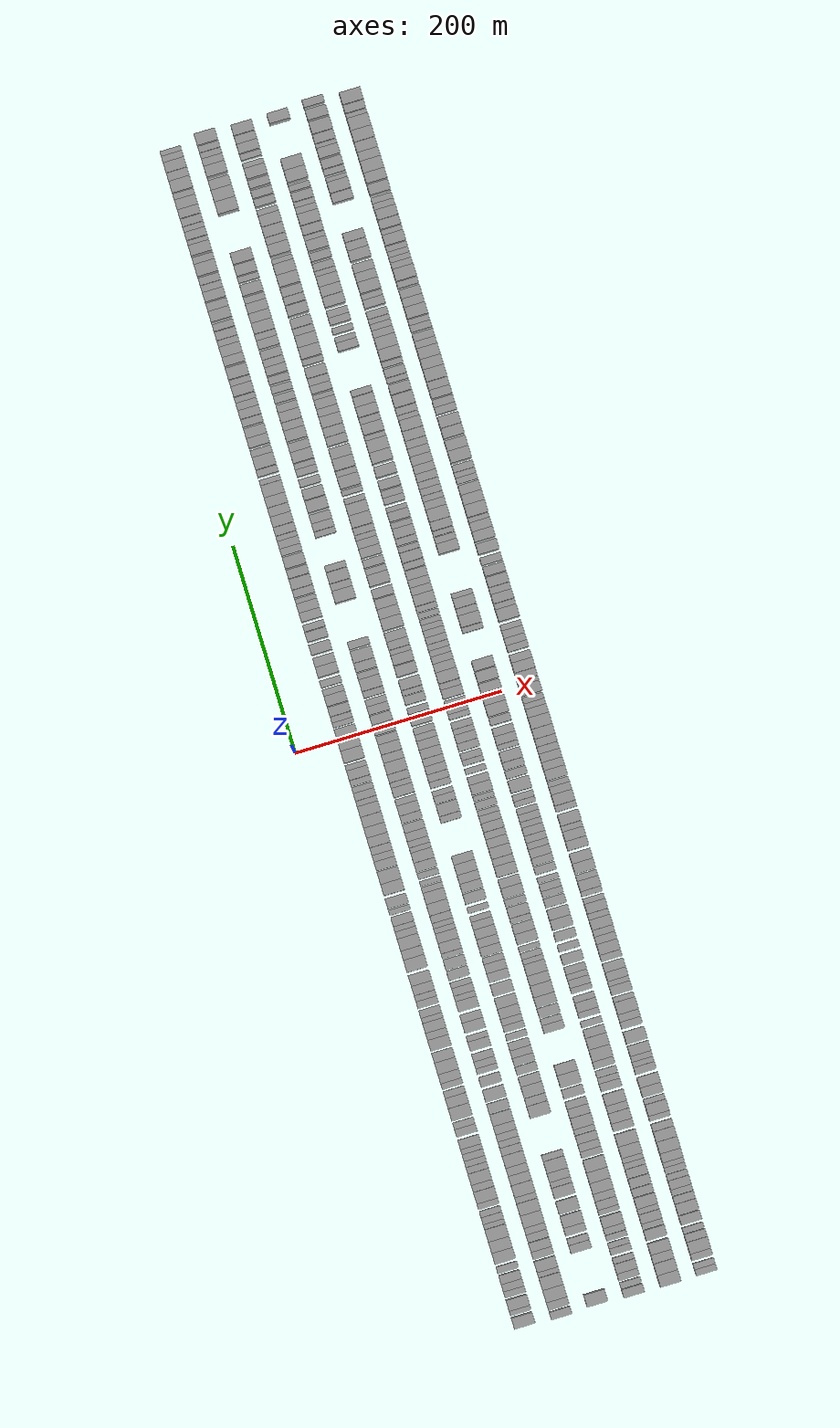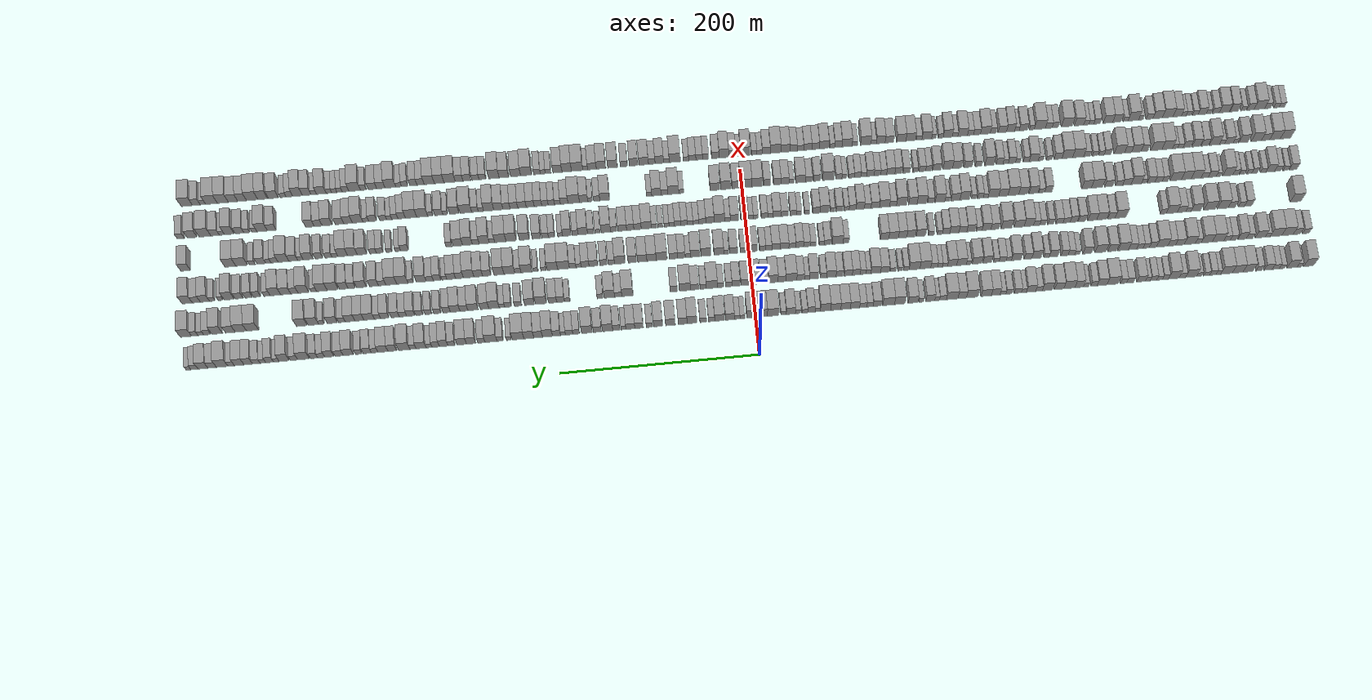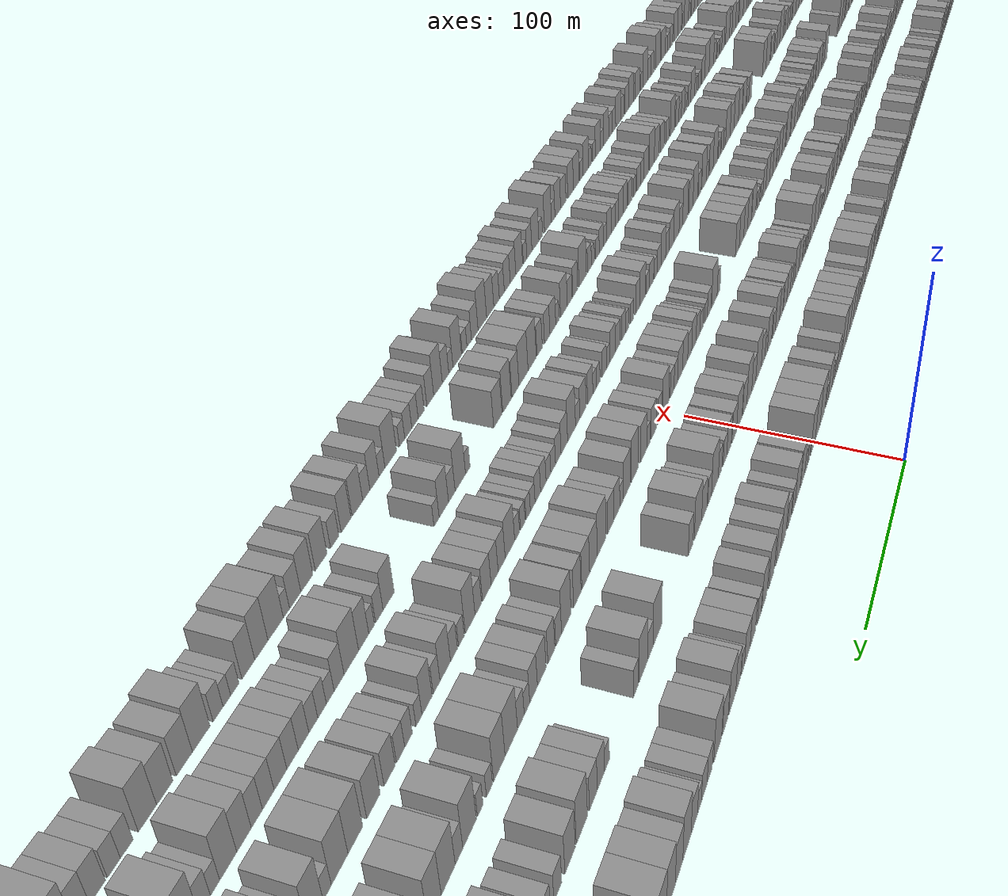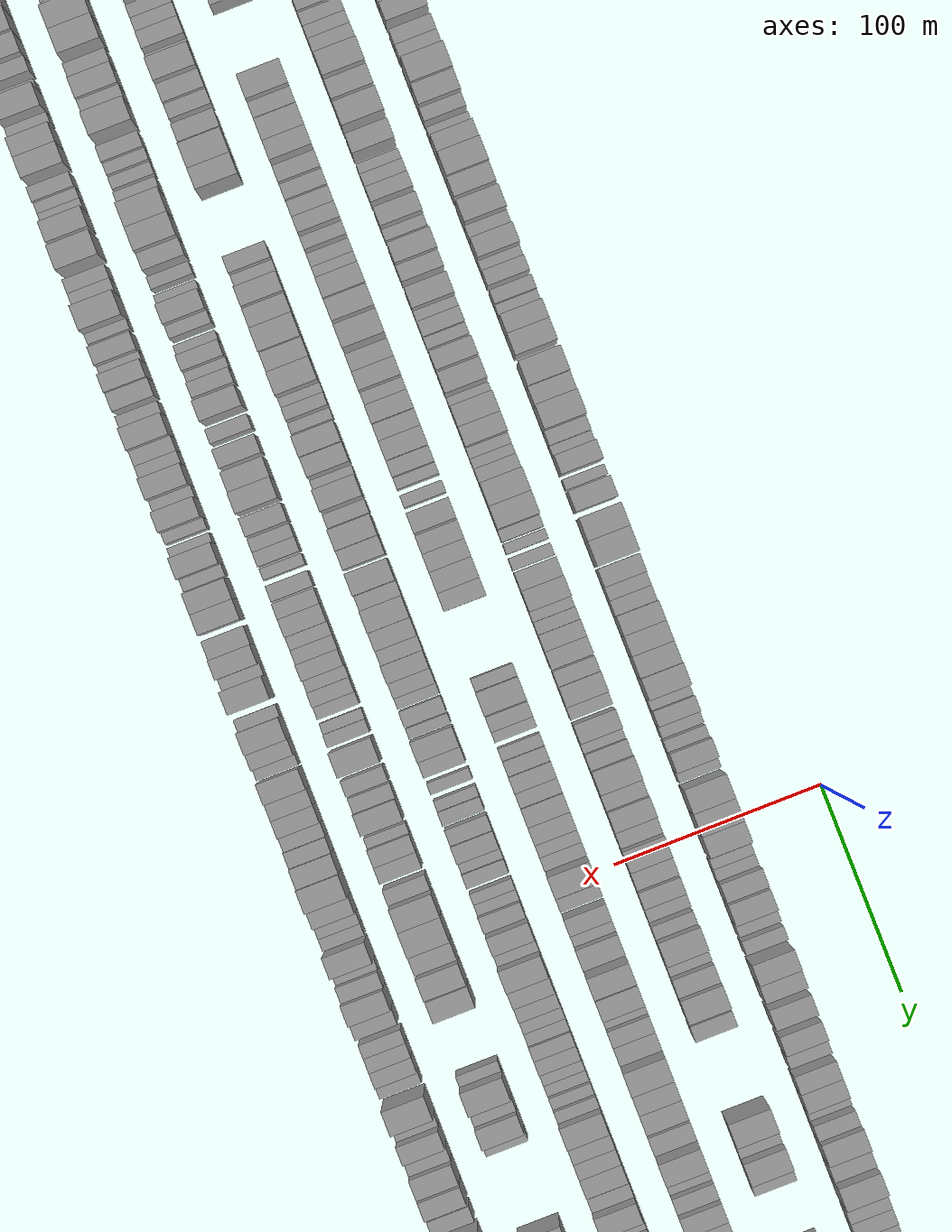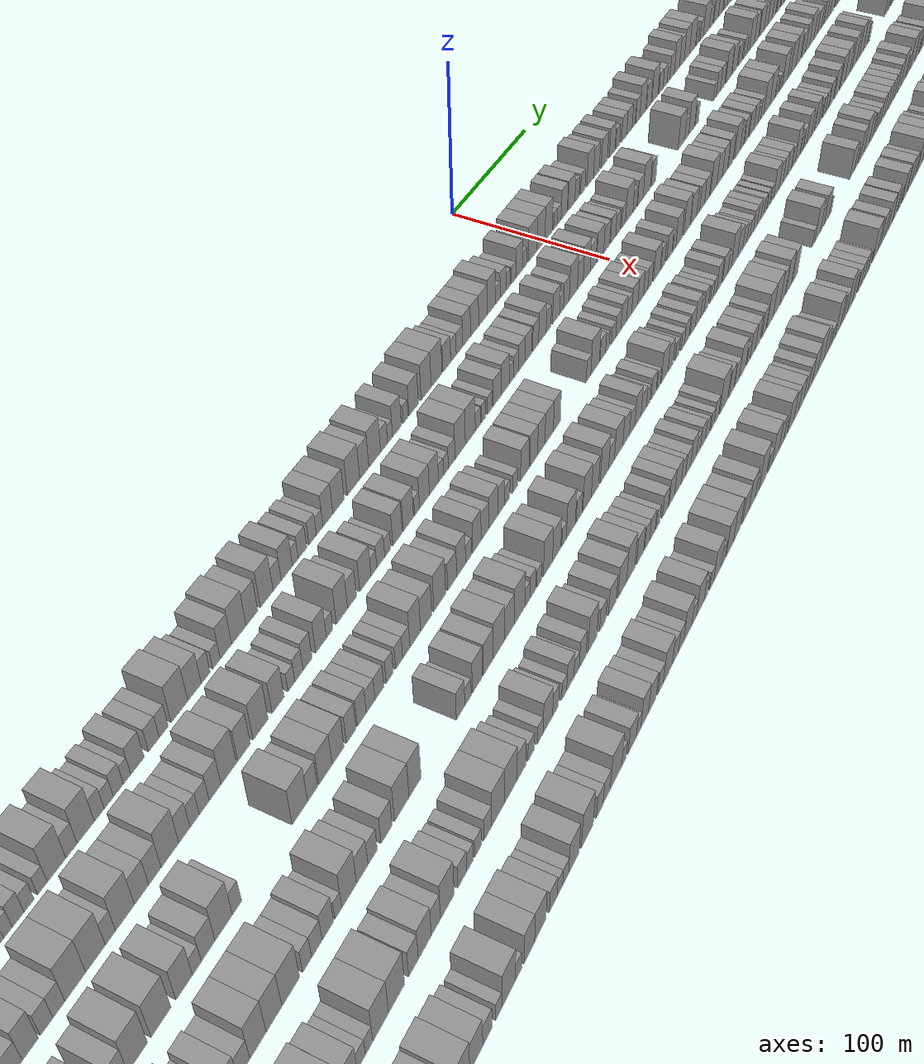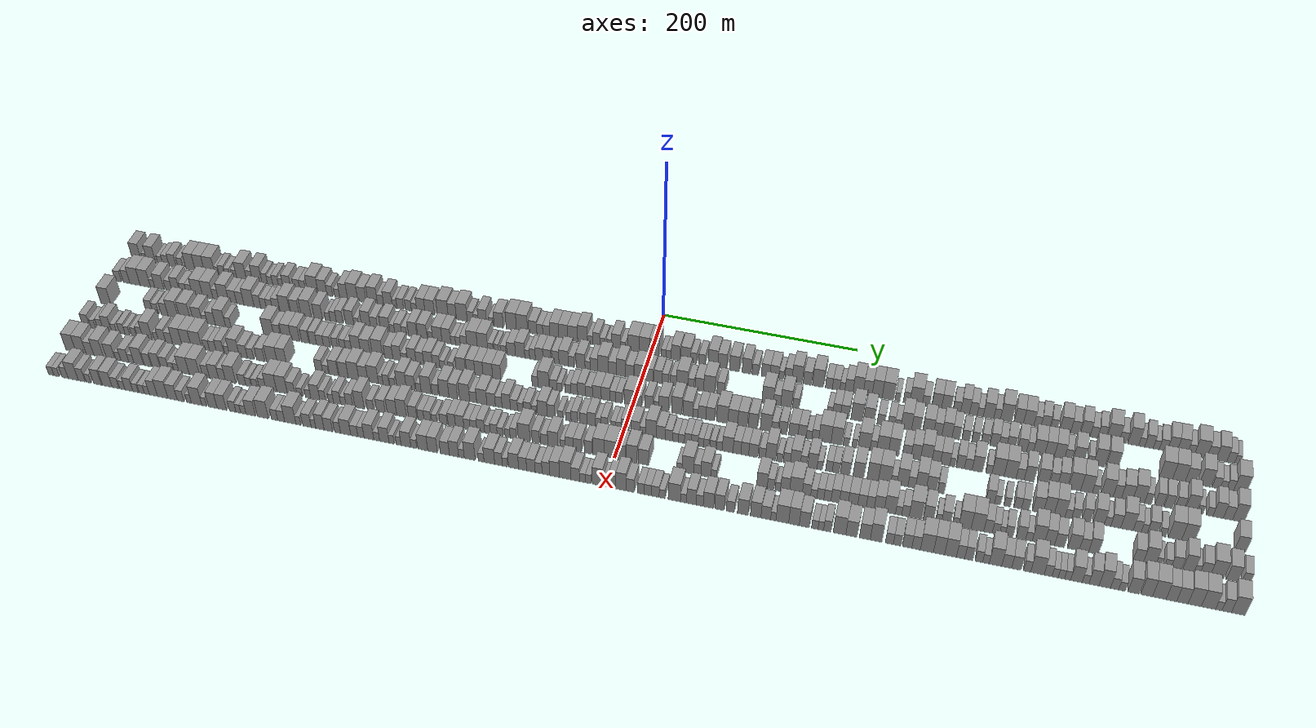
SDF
<sdf version="1.6">
 <world name="default">
  <scene>
   <sky><clouds><speed>12</speed></clouds></sky>
   <ambient>0.4 0.4 0.4 1</ambient>
   <background>0.7 0.7 0.7 1</background>
   <shadows>1</shadows>
  </scene>
  <gravity>0 0 -9.8066</gravity>
  <magnetic_field>6e-06 2.3e-05 -4.2e-05</magnetic_field>
  <physics default="0" name="default_physics" type="ode">
   <ode>
    <solver>
     <type>quick</type>
     <iters>10</iters>
     <sor>1.0</sor>
     <use_dynamic_moi_rescaling>0</use_dynamic_moi_rescaling>
    </solver>
    <constraints>
     <cfm>0</cfm>
     <erp>0.2</erp>
     <contact_max_correcting_vel>100</contact_max_correcting_vel>
     <contact_surface_layer>0.001</contact_surface_layer>
    </constraints>
   </ode>
   <max_step_size>0.004</max_step_size>
   <real_time_factor>1</real_time_factor>
   <real_time_update_rate>250</real_time_update_rate>
  </physics>
  <light name="sun" type="directional">
   <pose>0 0 10 0 0 0</pose>
   <diffuse>0.8 0.8 0.8 1</diffuse>
   <specular>0.2 0.2 0.2 1</specular>
   <attenuation>
    <range>1000</range>
    <constant>0.9</constant>
    <linear>0.01</linear>
    <quadratic>0.001</quadratic>
   </attenuation>
   <direction>-0.5 0.1 -0.9</direction>
  </light>
  <model name="building_1">
   <static>1</static>
   <pose>50.0000 -562.8323 0 0.000000 0.000000 0.000000</pose>
   <link name="link">
    <pose>0 0 12.00 0 0 0</pose>
    <collision name="collision"><geometry><box><size>20.0000 10.3353 24.0000</size></box></geometry></collision>
    <visual name="visual">
     <cast_shadows>0</cast_shadows>
     <geometry><box><size>20.0000 10.3353 24.0000</size></box></geometry>
     <material>
      <script>
       <uri>model://grey_wall/materials/scripts</uri>
       <uri>model://grey_wall/materials/textures</uri>
       <name>vrc/grey_wall</name>
      </script>
     </material>
    </visual>
   </link>
  </model>
  <model name="building_2">
   <static>1</static>
   <pose>50.0000 -553.2587 0 0.000000 0.000000 0.000000</pose>
   <link name="link">
    <pose>0 0 6.00 0 0 0</pose>
    <collision name="collision"><geometry><box><size>20.0000 4.8121 12.0000</size></box></geometry></collision>
    <visual name="visual">
     <cast_shadows>0</cast_shadows>
     <geometry><box><size>20.0000 4.8121 12.0000</size></box></geometry>
     <material>
      <script>
       <uri>model://grey_wall/materials/scripts</uri>
       <uri>model://grey_wall/materials/textures</uri>
       <name>vrc/grey_wall</name>
      </script>
     </material>
    </visual>
   </link>
  </model>
  <model name="building_3">
   <static>1</static>
   <pose>50.0000 -545.6910 0 0.000000 0.000000 0.000000</pose>
   <link name="link">
    <pose>0 0 12.00 0 0 0</pose>
    <collision name="collision"><geometry><box><size>20.0000 10.3233 24.0000</size></box></geometry></collision>
    <visual name="visual">
     <cast_shadows>0</cast_shadows>
     <geometry><box><size>20.0000 10.3233 24.0000</size></box></geometry>
     <material>
      <script>
       <uri>model://grey_wall/materials/scripts</uri>
       <uri>model://grey_wall/materials/textures</uri>
       <name>vrc/grey_wall</name>
      </script>
     </material>
    </visual>
   </link>
  </model>
  <model name="building_4">
   <static>1</static>
   <pose>50.0000 -535.5660 0 0.000000 0.000000 0.000000</pose>
   <link name="link">
    <pose>0 0 6.00 0 0 0</pose>
    <collision name="collision"><geometry><box><size>20.0000 5.9265 12.0000</size></box></geometry></collision>
    <visual name="visual">
     <cast_shadows>0</cast_shadows>
     <geometry><box><size>20.0000 5.9265 12.0000</size></box></geometry>
     <material>
      <script>
       <uri>model://grey_wall/materials/scripts</uri>
       <uri>model://grey_wall/materials/textures</uri>
       <name>vrc/grey_wall</name>
      </script>
     </material>
    </visual>
   </link>
  </model>
  <model name="building_5">
   <static>1</static>
   <pose>50.0000 -529.0180 0 0.000000 0.000000 0.000000</pose>
   <link name="link">
    <pose>0 0 7.50 0 0 0</pose>
    <collision name="collision"><geometry><box><size>20.0000 7.1696 15.0000</size></box></geometry></collision>
    <visual name="visual">
     <cast_shadows>0</cast_shadows>
     <geometry><box><size>20.0000 7.1696 15.0000</size></box></geometry>
     <material>
      <script>
       <uri>model://grey_wall/materials/scripts</uri>
       <uri>model://grey_wall/materials/textures</uri>
       <name>vrc/grey_wall</name>
      </script>
     </material>
    </visual>
   </link>
  </model>
  <model name="building_6">
   <static>1</static>
   <pose>50.0000 -521.2506 0 0.000000 0.000000 0.000000</pose>
   <link name="link">
    <pose>0 0 9.00 0 0 0</pose>
    <collision name="collision"><geometry><box><size>20.0000 8.3651 18.0000</size></box></geometry></collision>
    <visual name="visual">
     <cast_shadows>0</cast_shadows>
     <geometry><box><size>20.0000 8.3651 18.0000</size></box></geometry>
     <material>
      <script>
       <uri>model://grey_wall/materials/scripts</uri>
       <uri>model://grey_wall/materials/textures</uri>
       <name>vrc/grey_wall</name>
      </script>
     </material>
    </visual>
   </link>
  </model>
  <model name="building_7">
   <static>1</static>
   <pose>50.0000 -511.9560 0 0.000000 0.000000 0.000000</pose>
   <link name="link">
    <pose>0 0 7.50 0 0 0</pose>
    <collision name="collision"><geometry><box><size>20.0000 6.2241 15.0000</size></box></geometry></collision>
    <visual name="visual">
     <cast_shadows>0</cast_shadows>
     <geometry><box><size>20.0000 6.2241 15.0000</size></box></geometry>
     <material>
      <script>
       <uri>model://grey_wall/materials/scripts</uri>
       <uri>model://grey_wall/materials/textures</uri>
       <name>vrc/grey_wall</name>
      </script>
     </material>
    </visual>
   </link>
  </model>
  <model name="building_8">
   <static>1</static>
   <pose>50.0000 -500.5548 0 0.000000 0.000000 0.000000</pose>
   <link name="link">
    <pose>0 0 12.00 0 0 0</pose>
    <collision name="collision"><geometry><box><size>20.0000 10.5784 24.0000</size></box></geometry></collision>
    <visual name="visual">
     <cast_shadows>0</cast_shadows>
     <geometry><box><size>20.0000 10.5784 24.0000</size></box></geometry>
     <material>
      <script>
       <uri>model://grey_wall/materials/scripts</uri>
       <uri>model://grey_wall/materials/textures</uri>
       <name>vrc/grey_wall</name>
      </script>
     </material>
    </visual>
   </link>
  </model>
  <model name="building_9">
   <static>1</static>
   <pose>50.0000 -489.8678 0 0.000000 0.000000 0.000000</pose>
   <link name="link">
    <pose>0 0 12.00 0 0 0</pose>
    <collision name="collision"><geometry><box><size>20.0000 10.7955 24.0000</size></box></geometry></collision>
    <visual name="visual">
     <cast_shadows>0</cast_shadows>
     <geometry><box><size>20.0000 10.7955 24.0000</size></box></geometry>
     <material>
      <script>
       <uri>model://grey_wall/materials/scripts</uri>
       <uri>model://grey_wall/materials/textures</uri>
       <name>vrc/grey_wall</name>
      </script>
     </material>
    </visual>
   </link>
  </model>
  <model name="building_10">
   <static>1</static>
   <pose>50.0000 -478.5496 0 0.000000 0.000000 0.000000</pose>
   <link name="link">
    <pose>0 0 12.00 0 0 0</pose>
    <collision name="collision"><geometry><box><size>20.0000 11.8408 24.0000</size></box></geometry></collision>
    <visual name="visual">
     <cast_shadows>0</cast_shadows>
     <geometry><box><size>20.0000 11.8408 24.0000</size></box></geometry>
     <material>
      <script>
       <uri>model://grey_wall/materials/scripts</uri>
       <uri>model://grey_wall/materials/textures</uri>
       <name>vrc/grey_wall</name>
      </script>
     </material>
    </visual>
   </link>
  </model>
  <model name="building_11">
   <static>1</static>
   <pose>50.0000 -470.2141 0 0.000000 0.000000 0.000000</pose>
   <link name="link">
    <pose>0 0 6.00 0 0 0</pose>
    <collision name="collision"><geometry><box><size>20.0000 4.8303 12.0000</size></box></geometry></collision>
    <visual name="visual">
     <cast_shadows>0</cast_shadows>
     <geometry><box><size>20.0000 4.8303 12.0000</size></box></geometry>
     <material>
      <script>
       <uri>model://grey_wall/materials/scripts</uri>
       <uri>model://grey_wall/materials/textures</uri>
       <name>vrc/grey_wall</name>
      </script>
     </material>
    </visual>
   </link>
  </model>
  <model name="building_12">
   <static>1</static>
   <pose>50.0000 -464.5048 0 0.000000 0.000000 0.000000</pose>
   <link name="link">
    <pose>0 0 7.50 0 0 0</pose>
    <collision name="collision"><geometry><box><size>20.0000 6.5882 15.0000</size></box></geometry></collision>
    <visual name="visual">
     <cast_shadows>0</cast_shadows>
     <geometry><box><size>20.0000 6.5882 15.0000</size></box></geometry>
     <material>
      <script>
       <uri>model://grey_wall/materials/scripts</uri>
       <uri>model://grey_wall/materials/textures</uri>
       <name>vrc/grey_wall</name>
      </script>
     </material>
    </visual>
   </link>
  </model>
  <model name="building_13">
   <static>1</static>
   <pose>50.0000 -458.3120 0 0.000000 0.000000 0.000000</pose>
   <link name="link">
    <pose>0 0 6.00 0 0 0</pose>
    <collision name="collision"><geometry><box><size>20.0000 5.7974 12.0000</size></box></geometry></collision>
    <visual name="visual">
     <cast_shadows>0</cast_shadows>
     <geometry><box><size>20.0000 5.7974 12.0000</size></box></geometry>
     <material>
      <script>
       <uri>model://grey_wall/materials/scripts</uri>
       <uri>model://grey_wall/materials/textures</uri>
       <name>vrc/grey_wall</name>
      </script>
     </material>
    </visual>
   </link>
  </model>
  <model name="building_14">
   <static>1</static>
   <pose>50.0000 -450.5928 0 0.000000 0.000000 0.000000</pose>
   <link name="link">
    <pose>0 0 6.00 0 0 0</pose>
    <collision name="collision"><geometry><box><size>20.0000 5.6410 12.0000</size></box></geometry></collision>
    <visual name="visual">
     <cast_shadows>0</cast_shadows>
     <geometry><box><size>20.0000 5.6410 12.0000</size></box></geometry>
     <material>
      <script>
       <uri>model://grey_wall/materials/scripts</uri>
       <uri>model://grey_wall/materials/textures</uri>
       <name>vrc/grey_wall</name>
      </script>
     </material>
    </visual>
   </link>
  </model>
  <model name="building_15">
   <static>1</static>
   <pose>50.0000 -442.2257 0 0.000000 0.000000 0.000000</pose>
   <link name="link">
    <pose>0 0 12.00 0 0 0</pose>
    <collision name="collision"><geometry><box><size>20.0000 11.0932 24.0000</size></box></geometry></collision>
    <visual name="visual">
     <cast_shadows>0</cast_shadows>
     <geometry><box><size>20.0000 11.0932 24.0000</size></box></geometry>
     <material>
      <script>
       <uri>model://grey_wall/materials/scripts</uri>
       <uri>model://grey_wall/materials/textures</uri>
       <name>vrc/grey_wall</name>
      </script>
     </material>
    </visual>
   </link>
  </model>
  <model name="building_16">
   <static>1</static>
   <pose>50.0000 -433.2365 0 0.000000 0.000000 0.000000</pose>
   <link name="link">
    <pose>0 0 7.50 0 0 0</pose>
    <collision name="collision"><geometry><box><size>20.0000 6.8852 15.0000</size></box></geometry></collision>
    <visual name="visual">
     <cast_shadows>0</cast_shadows>
     <geometry><box><size>20.0000 6.8852 15.0000</size></box></geometry>
     <material>
      <script>
       <uri>model://grey_wall/materials/scripts</uri>
       <uri>model://grey_wall/materials/textures</uri>
       <name>vrc/grey_wall</name>
      </script>
     </material>
    </visual>
   </link>
  </model>
  <model name="building_17">
   <static>1</static>
   <pose>50.0000 -424.4515 0 0.000000 0.000000 0.000000</pose>
   <link name="link">
    <pose>0 0 12.00 0 0 0</pose>
    <collision name="collision"><geometry><box><size>20.0000 10.6849 24.0000</size></box></geometry></collision>
    <visual name="visual">
     <cast_shadows>0</cast_shadows>
     <geometry><box><size>20.0000 10.6849 24.0000</size></box></geometry>
     <material>
      <script>
       <uri>model://grey_wall/materials/scripts</uri>
       <uri>model://grey_wall/materials/textures</uri>
       <name>vrc/grey_wall</name>
      </script>
     </material>
    </visual>
   </link>
  </model>
  <model name="building_18">
   <static>1</static>
   <pose>50.0000 -416.0181 0 0.000000 0.000000 0.000000</pose>
   <link name="link">
    <pose>0 0 7.50 0 0 0</pose>
    <collision name="collision"><geometry><box><size>20.0000 6.1817 15.0000</size></box></geometry></collision>
    <visual name="visual">
     <cast_shadows>0</cast_shadows>
     <geometry><box><size>20.0000 6.1817 15.0000</size></box></geometry>
     <material>
      <script>
       <uri>model://grey_wall/materials/scripts</uri>
       <uri>model://grey_wall/materials/textures</uri>
       <name>vrc/grey_wall</name>
      </script>
     </material>
    </visual>
   </link>
  </model>
  <model name="building_19">
   <static>1</static>
   <pose>50.0000 -409.9744 0 0.000000 0.000000 0.000000</pose>
   <link name="link">
    <pose>0 0 6.00 0 0 0</pose>
    <collision name="collision"><geometry><box><size>20.0000 5.9059 12.0000</size></box></geometry></collision>
    <visual name="visual">
     <cast_shadows>0</cast_shadows>
     <geometry><box><size>20.0000 5.9059 12.0000</size></box></geometry>
     <material>
      <script>
       <uri>model://grey_wall/materials/scripts</uri>
       <uri>model://grey_wall/materials/textures</uri>
       <name>vrc/grey_wall</name>
      </script>
     </material>
    </visual>
   </link>
  </model>
  <model name="building_20">
   <static>1</static>
   <pose>50.0000 -403.7748 0 0.000000 0.000000 0.000000</pose>
   <link name="link">
    <pose>0 0 7.50 0 0 0</pose>
    <collision name="collision"><geometry><box><size>20.0000 6.4932 15.0000</size></box></geometry></collision>
    <visual name="visual">
     <cast_shadows>0</cast_shadows>
     <geometry><box><size>20.0000 6.4932 15.0000</size></box></geometry>
     <material>
      <script>
       <uri>model://grey_wall/materials/scripts</uri>
       <uri>model://grey_wall/materials/textures</uri>
       <name>vrc/grey_wall</name>
      </script>
     </material>
    </visual>
   </link>
  </model>
  <model name="building_21">
   <static>1</static>
   <pose>50.0000 -398.0769 0 0.000000 0.000000 0.000000</pose>
   <link name="link">
    <pose>0 0 6.00 0 0 0</pose>
    <collision name="collision"><geometry><box><size>20.0000 4.9025 12.0000</size></box></geometry></collision>
    <visual name="visual">
     <cast_shadows>0</cast_shadows>
     <geometry><box><size>20.0000 4.9025 12.0000</size></box></geometry>
     <material>
      <script>
       <uri>model://grey_wall/materials/scripts</uri>
       <uri>model://grey_wall/materials/textures</uri>
       <name>vrc/grey_wall</name>
      </script>
     </material>
    </visual>
   </link>
  </model>
  <model name="building_22">
   <static>1</static>
   <pose>50.0000 -391.1550 0 0.000000 0.000000 0.000000</pose>
   <link name="link">
    <pose>0 0 9.00 0 0 0</pose>
    <collision name="collision"><geometry><box><size>20.0000 8.9414 18.0000</size></box></geometry></collision>
    <visual name="visual">
     <cast_shadows>0</cast_shadows>
     <geometry><box><size>20.0000 8.9414 18.0000</size></box></geometry>
     <material>
      <script>
       <uri>model://grey_wall/materials/scripts</uri>
       <uri>model://grey_wall/materials/textures</uri>
       <name>vrc/grey_wall</name>
      </script>
     </material>
    </visual>
   </link>
  </model>
  <model name="building_23">
   <static>1</static>
   <pose>50.0000 -380.0222 0 0.000000 0.000000 0.000000</pose>
   <link name="link">
    <pose>0 0 7.50 0 0 0</pose>
    <collision name="collision"><geometry><box><size>20.0000 7.3244 15.0000</size></box></geometry></collision>
    <visual name="visual">
     <cast_shadows>0</cast_shadows>
     <geometry><box><size>20.0000 7.3244 15.0000</size></box></geometry>
     <material>
      <script>
       <uri>model://grey_wall/materials/scripts</uri>
       <uri>model://grey_wall/materials/textures</uri>
       <name>vrc/grey_wall</name>
      </script>
     </material>
    </visual>
   </link>
  </model>
  <model name="building_24">
   <static>1</static>
   <pose>50.0000 -373.2017 0 0.000000 0.000000 0.000000</pose>
   <link name="link">
    <pose>0 0 7.50 0 0 0</pose>
    <collision name="collision"><geometry><box><size>20.0000 6.3165 15.0000</size></box></geometry></collision>
    <visual name="visual">
     <cast_shadows>0</cast_shadows>
     <geometry><box><size>20.0000 6.3165 15.0000</size></box></geometry>
     <material>
      <script>
       <uri>model://grey_wall/materials/scripts</uri>
       <uri>model://grey_wall/materials/textures</uri>
       <name>vrc/grey_wall</name>
      </script>
     </material>
    </visual>
   </link>
  </model>
  <model name="building_25">
   <static>1</static>
   <pose>50.0000 -362.0631 0 0.000000 0.000000 0.000000</pose>
   <link name="link">
    <pose>0 0 12.00 0 0 0</pose>
    <collision name="collision"><geometry><box><size>20.0000 11.9609 24.0000</size></box></geometry></collision>
    <visual name="visual">
     <cast_shadows>0</cast_shadows>
     <geometry><box><size>20.0000 11.9609 24.0000</size></box></geometry>
     <material>
      <script>
       <uri>model://grey_wall/materials/scripts</uri>
       <uri>model://grey_wall/materials/textures</uri>
       <name>vrc/grey_wall</name>
      </script>
     </material>
    </visual>
   </link>
  </model>
  <model name="building_26">
   <static>1</static>
   <pose>50.0000 -351.2172 0 0.000000 0.000000 0.000000</pose>
   <link name="link">
    <pose>0 0 10.50 0 0 0</pose>
    <collision name="collision"><geometry><box><size>20.0000 9.7309 21.0000</size></box></geometry></collision>
    <visual name="visual">
     <cast_shadows>0</cast_shadows>
     <geometry><box><size>20.0000 9.7309 21.0000</size></box></geometry>
     <material>
      <script>
       <uri>model://grey_wall/materials/scripts</uri>
       <uri>model://grey_wall/materials/textures</uri>
       <name>vrc/grey_wall</name>
      </script>
     </material>
    </visual>
   </link>
  </model>
  <model name="building_27">
   <static>1</static>
   <pose>50.0000 -343.0850 0 0.000000 0.000000 0.000000</pose>
   <link name="link">
    <pose>0 0 7.50 0 0 0</pose>
    <collision name="collision"><geometry><box><size>20.0000 6.5336 15.0000</size></box></geometry></collision>
    <visual name="visual">
     <cast_shadows>0</cast_shadows>
     <geometry><box><size>20.0000 6.5336 15.0000</size></box></geometry>
     <material>
      <script>
       <uri>model://grey_wall/materials/scripts</uri>
       <uri>model://grey_wall/materials/textures</uri>
       <name>vrc/grey_wall</name>
      </script>
     </material>
    </visual>
   </link>
  </model>
  <model name="building_28">
   <static>1</static>
   <pose>50.0000 -334.9886 0 0.000000 0.000000 0.000000</pose>
   <link name="link">
    <pose>0 0 6.00 0 0 0</pose>
    <collision name="collision"><geometry><box><size>20.0000 5.6591 12.0000</size></box></geometry></collision>
    <visual name="visual">
     <cast_shadows>0</cast_shadows>
     <geometry><box><size>20.0000 5.6591 12.0000</size></box></geometry>
     <material>
      <script>
       <uri>model://grey_wall/materials/scripts</uri>
       <uri>model://grey_wall/materials/textures</uri>
       <name>vrc/grey_wall</name>
      </script>
     </material>
    </visual>
   </link>
  </model>
  <model name="building_29">
   <static>1</static>
   <pose>50.0000 -327.7946 0 0.000000 0.000000 0.000000</pose>
   <link name="link">
    <pose>0 0 10.50 0 0 0</pose>
    <collision name="collision"><geometry><box><size>20.0000 8.7289 21.0000</size></box></geometry></collision>
    <visual name="visual">
     <cast_shadows>0</cast_shadows>
     <geometry><box><size>20.0000 8.7289 21.0000</size></box></geometry>
     <material>
      <script>
       <uri>model://grey_wall/materials/scripts</uri>
       <uri>model://grey_wall/materials/textures</uri>
       <name>vrc/grey_wall</name>
      </script>
     </material>
    </visual>
   </link>
  </model>
  <model name="building_30">
   <static>1</static>
   <pose>50.0000 -317.7794 0 0.000000 0.000000 0.000000</pose>
   <link name="link">
    <pose>0 0 12.00 0 0 0</pose>
    <collision name="collision"><geometry><box><size>20.0000 11.3015 24.0000</size></box></geometry></collision>
    <visual name="visual">
     <cast_shadows>0</cast_shadows>
     <geometry><box><size>20.0000 11.3015 24.0000</size></box></geometry>
     <material>
      <script>
       <uri>model://grey_wall/materials/scripts</uri>
       <uri>model://grey_wall/materials/textures</uri>
       <name>vrc/grey_wall</name>
      </script>
     </material>
    </visual>
   </link>
  </model>
  <model name="building_31">
   <static>1</static>
   <pose>50.0000 -307.4623 0 0.000000 0.000000 0.000000</pose>
   <link name="link">
    <pose>0 0 10.50 0 0 0</pose>
    <collision name="collision"><geometry><box><size>20.0000 9.3325 21.0000</size></box></geometry></collision>
    <visual name="visual">
     <cast_shadows>0</cast_shadows>
     <geometry><box><size>20.0000 9.3325 21.0000</size></box></geometry>
     <material>
      <script>
       <uri>model://grey_wall/materials/scripts</uri>
       <uri>model://grey_wall/materials/textures</uri>
       <name>vrc/grey_wall</name>
      </script>
     </material>
    </visual>
   </link>
  </model>
  <model name="building_32">
   <static>1</static>
   <pose>50.0000 -295.5357 0 0.000000 0.000000 0.000000</pose>
   <link name="link">
    <pose>0 0 12.00 0 0 0</pose>
    <collision name="collision"><geometry><box><size>20.0000 10.5207 24.0000</size></box></geometry></collision>
    <visual name="visual">
     <cast_shadows>0</cast_shadows>
     <geometry><box><size>20.0000 10.5207 24.0000</size></box></geometry>
     <material>
      <script>
       <uri>model://grey_wall/materials/scripts</uri>
       <uri>model://grey_wall/materials/textures</uri>
       <name>vrc/grey_wall</name>
      </script>
     </material>
    </visual>
   </link>
  </model>
  <model name="building_33">
   <static>1</static>
   <pose>50.0000 -286.8878 0 0.000000 0.000000 0.000000</pose>
   <link name="link">
    <pose>0 0 7.50 0 0 0</pose>
    <collision name="collision"><geometry><box><size>20.0000 6.7751 15.0000</size></box></geometry></collision>
    <visual name="visual">
     <cast_shadows>0</cast_shadows>
     <geometry><box><size>20.0000 6.7751 15.0000</size></box></geometry>
     <material>
      <script>
       <uri>model://grey_wall/materials/scripts</uri>
       <uri>model://grey_wall/materials/textures</uri>
       <name>vrc/grey_wall</name>
      </script>
     </material>
    </visual>
   </link>
  </model>
  <model name="building_34">
   <static>1</static>
   <pose>50.0000 -278.7941 0 0.000000 0.000000 0.000000</pose>
   <link name="link">
    <pose>0 0 10.50 0 0 0</pose>
    <collision name="collision"><geometry><box><size>20.0000 9.4123 21.0000</size></box></geometry></collision>
    <visual name="visual">
     <cast_shadows>0</cast_shadows>
     <geometry><box><size>20.0000 9.4123 21.0000</size></box></geometry>
     <material>
      <script>
       <uri>model://grey_wall/materials/scripts</uri>
       <uri>model://grey_wall/materials/textures</uri>
       <name>vrc/grey_wall</name>
      </script>
     </material>
    </visual>
   </link>
  </model>
  <model name="building_35">
   <static>1</static>
   <pose>50.0000 -271.5590 0 0.000000 0.000000 0.000000</pose>
   <link name="link">
    <pose>0 0 6.00 0 0 0</pose>
    <collision name="collision"><geometry><box><size>20.0000 5.0578 12.0000</size></box></geometry></collision>
    <visual name="visual">
     <cast_shadows>0</cast_shadows>
     <geometry><box><size>20.0000 5.0578 12.0000</size></box></geometry>
     <material>
      <script>
       <uri>model://grey_wall/materials/scripts</uri>
       <uri>model://grey_wall/materials/textures</uri>
       <name>vrc/grey_wall</name>
      </script>
     </material>
    </visual>
   </link>
  </model>
  <model name="building_36">
   <static>1</static>
   <pose>50.0000 -265.3924 0 0.000000 0.000000 0.000000</pose>
   <link name="link">
    <pose>0 0 7.50 0 0 0</pose>
    <collision name="collision"><geometry><box><size>20.0000 7.2756 15.0000</size></box></geometry></collision>
    <visual name="visual">
     <cast_shadows>0</cast_shadows>
     <geometry><box><size>20.0000 7.2756 15.0000</size></box></geometry>
     <material>
      <script>
       <uri>model://grey_wall/materials/scripts</uri>
       <uri>model://grey_wall/materials/textures</uri>
       <name>vrc/grey_wall</name>
      </script>
     </material>
    </visual>
   </link>
  </model>
  <model name="building_37">
   <static>1</static>
   <pose>50.0000 -256.4576 0 0.000000 0.000000 0.000000</pose>
   <link name="link">
    <pose>0 0 7.50 0 0 0</pose>
    <collision name="collision"><geometry><box><size>20.0000 6.5939 15.0000</size></box></geometry></collision>
    <visual name="visual">
     <cast_shadows>0</cast_shadows>
     <geometry><box><size>20.0000 6.5939 15.0000</size></box></geometry>
     <material>
      <script>
       <uri>model://grey_wall/materials/scripts</uri>
       <uri>model://grey_wall/materials/textures</uri>
       <name>vrc/grey_wall</name>
      </script>
     </material>
    </visual>
   </link>
  </model>
  <model name="building_38">
   <static>1</static>
   <pose>50.0000 -250.2285 0 0.000000 0.000000 0.000000</pose>
   <link name="link">
    <pose>0 0 6.00 0 0 0</pose>
    <collision name="collision"><geometry><box><size>20.0000 5.8642 12.0000</size></box></geometry></collision>
    <visual name="visual">
     <cast_shadows>0</cast_shadows>
     <geometry><box><size>20.0000 5.8642 12.0000</size></box></geometry>
     <material>
      <script>
       <uri>model://grey_wall/materials/scripts</uri>
       <uri>model://grey_wall/materials/textures</uri>
       <name>vrc/grey_wall</name>
      </script>
     </material>
    </visual>
   </link>
  </model>
  <model name="building_39">
   <static>1</static>
   <pose>50.0000 -242.7977 0 0.000000 0.000000 0.000000</pose>
   <link name="link">
    <pose>0 0 10.50 0 0 0</pose>
    <collision name="collision"><geometry><box><size>20.0000 8.9975 21.0000</size></box></geometry></collision>
    <visual name="visual">
     <cast_shadows>0</cast_shadows>
     <geometry><box><size>20.0000 8.9975 21.0000</size></box></geometry>
     <material>
      <script>
       <uri>model://grey_wall/materials/scripts</uri>
       <uri>model://grey_wall/materials/textures</uri>
       <name>vrc/grey_wall</name>
      </script>
     </material>
    </visual>
   </link>
  </model>
  <model name="building_40">
   <static>1</static>
   <pose>50.0000 -233.1098 0 0.000000 0.000000 0.000000</pose>
   <link name="link">
    <pose>0 0 10.50 0 0 0</pose>
    <collision name="collision"><geometry><box><size>20.0000 10.3783 21.0000</size></box></geometry></collision>
    <visual name="visual">
     <cast_shadows>0</cast_shadows>
     <geometry><box><size>20.0000 10.3783 21.0000</size></box></geometry>
     <material>
      <script>
       <uri>model://grey_wall/materials/scripts</uri>
       <uri>model://grey_wall/materials/textures</uri>
       <name>vrc/grey_wall</name>
      </script>
     </material>
    </visual>
   </link>
  </model>
  <model name="building_41">
   <static>1</static>
   <pose>50.0000 -219.0202 0 0.000000 0.000000 0.000000</pose>
   <link name="link">
    <pose>0 0 12.00 0 0 0</pose>
    <collision name="collision"><geometry><box><size>20.0000 11.8010 24.0000</size></box></geometry></collision>
    <visual name="visual">
     <cast_shadows>0</cast_shadows>
     <geometry><box><size>20.0000 11.8010 24.0000</size></box></geometry>
     <material>
      <script>
       <uri>model://grey_wall/materials/scripts</uri>
       <uri>model://grey_wall/materials/textures</uri>
       <name>vrc/grey_wall</name>
      </script>
     </material>
    </visual>
   </link>
  </model>
  <model name="building_42">
   <static>1</static>
   <pose>50.0000 -208.7219 0 0.000000 0.000000 0.000000</pose>
   <link name="link">
    <pose>0 0 10.50 0 0 0</pose>
    <collision name="collision"><geometry><box><size>20.0000 8.7955 21.0000</size></box></geometry></collision>
    <visual name="visual">
     <cast_shadows>0</cast_shadows>
     <geometry><box><size>20.0000 8.7955 21.0000</size></box></geometry>
     <material>
      <script>
       <uri>model://grey_wall/materials/scripts</uri>
       <uri>model://grey_wall/materials/textures</uri>
       <name>vrc/grey_wall</name>
      </script>
     </material>
    </visual>
   </link>
  </model>
  <model name="building_43">
   <static>1</static>
   <pose>50.0000 -198.5086 0 0.000000 0.000000 0.000000</pose>
   <link name="link">
    <pose>0 0 12.00 0 0 0</pose>
    <collision name="collision"><geometry><box><size>20.0000 11.6310 24.0000</size></box></geometry></collision>
    <visual name="visual">
     <cast_shadows>0</cast_shadows>
     <geometry><box><size>20.0000 11.6310 24.0000</size></box></geometry>
     <material>
      <script>
       <uri>model://grey_wall/materials/scripts</uri>
       <uri>model://grey_wall/materials/textures</uri>
       <name>vrc/grey_wall</name>
      </script>
     </material>
    </visual>
   </link>
  </model>
  <model name="building_44">
   <static>1</static>
   <pose>50.0000 -189.2512 0 0.000000 0.000000 0.000000</pose>
   <link name="link">
    <pose>0 0 7.50 0 0 0</pose>
    <collision name="collision"><geometry><box><size>20.0000 6.8839 15.0000</size></box></geometry></collision>
    <visual name="visual">
     <cast_shadows>0</cast_shadows>
     <geometry><box><size>20.0000 6.8839 15.0000</size></box></geometry>
     <material>
      <script>
       <uri>model://grey_wall/materials/scripts</uri>
       <uri>model://grey_wall/materials/textures</uri>
       <name>vrc/grey_wall</name>
      </script>
     </material>
    </visual>
   </link>
  </model>
  <model name="building_45">
   <static>1</static>
   <pose>50.0000 -183.2836 0 0.000000 0.000000 0.000000</pose>
   <link name="link">
    <pose>0 0 6.00 0 0 0</pose>
    <collision name="collision"><geometry><box><size>20.0000 5.0514 12.0000</size></box></geometry></collision>
    <visual name="visual">
     <cast_shadows>0</cast_shadows>
     <geometry><box><size>20.0000 5.0514 12.0000</size></box></geometry>
     <material>
      <script>
       <uri>model://grey_wall/materials/scripts</uri>
       <uri>model://grey_wall/materials/textures</uri>
       <name>vrc/grey_wall</name>
      </script>
     </material>
    </visual>
   </link>
  </model>
  <model name="building_46">
   <static>1</static>
   <pose>50.0000 -176.2720 0 0.000000 0.000000 0.000000</pose>
   <link name="link">
    <pose>0 0 10.50 0 0 0</pose>
    <collision name="collision"><geometry><box><size>20.0000 8.9718 21.0000</size></box></geometry></collision>
    <visual name="visual">
     <cast_shadows>0</cast_shadows>
     <geometry><box><size>20.0000 8.9718 21.0000</size></box></geometry>
     <material>
      <script>
       <uri>model://grey_wall/materials/scripts</uri>
       <uri>model://grey_wall/materials/textures</uri>
       <name>vrc/grey_wall</name>
      </script>
     </material>
    </visual>
   </link>
  </model>
  <model name="building_47">
   <static>1</static>
   <pose>50.0000 -167.2965 0 0.000000 0.000000 0.000000</pose>
   <link name="link">
    <pose>0 0 6.00 0 0 0</pose>
    <collision name="collision"><geometry><box><size>20.0000 4.9792 12.0000</size></box></geometry></collision>
    <visual name="visual">
     <cast_shadows>0</cast_shadows>
     <geometry><box><size>20.0000 4.9792 12.0000</size></box></geometry>
     <material>
      <script>
       <uri>model://grey_wall/materials/scripts</uri>
       <uri>model://grey_wall/materials/textures</uri>
       <name>vrc/grey_wall</name>
      </script>
     </material>
    </visual>
   </link>
  </model>
  <model name="building_48">
   <static>1</static>
   <pose>50.0000 -158.8689 0 0.000000 0.000000 0.000000</pose>
   <link name="link">
    <pose>0 0 10.50 0 0 0</pose>
    <collision name="collision"><geometry><box><size>20.0000 9.8760 21.0000</size></box></geometry></collision>
    <visual name="visual">
     <cast_shadows>0</cast_shadows>
     <geometry><box><size>20.0000 9.8760 21.0000</size></box></geometry>
     <material>
      <script>
       <uri>model://grey_wall/materials/scripts</uri>
       <uri>model://grey_wall/materials/textures</uri>
       <name>vrc/grey_wall</name>
      </script>
     </material>
    </visual>
   </link>
  </model>
  <model name="building_49">
   <static>1</static>
   <pose>50.0000 -145.4547 0 0.000000 0.000000 0.000000</pose>
   <link name="link">
    <pose>0 0 12.00 0 0 0</pose>
    <collision name="collision"><geometry><box><size>20.0000 10.9523 24.0000</size></box></geometry></collision>
    <visual name="visual">
     <cast_shadows>0</cast_shadows>
     <geometry><box><size>20.0000 10.9523 24.0000</size></box></geometry>
     <material>
      <script>
       <uri>model://grey_wall/materials/scripts</uri>
       <uri>model://grey_wall/materials/textures</uri>
       <name>vrc/grey_wall</name>
      </script>
     </material>
    </visual>
   </link>
  </model>
  <model name="building_50">
   <static>1</static>
   <pose>50.0000 -134.0115 0 0.000000 0.000000 0.000000</pose>
   <link name="link">
    <pose>0 0 12.00 0 0 0</pose>
    <collision name="collision"><geometry><box><size>20.0000 11.9341 24.0000</size></box></geometry></collision>
    <visual name="visual">
     <cast_shadows>0</cast_shadows>
     <geometry><box><size>20.0000 11.9341 24.0000</size></box></geometry>
     <material>
      <script>
       <uri>model://grey_wall/materials/scripts</uri>
       <uri>model://grey_wall/materials/textures</uri>
       <name>vrc/grey_wall</name>
      </script>
     </material>
    </visual>
   </link>
  </model>
  <model name="building_51">
   <static>1</static>
   <pose>50.0000 -122.6873 0 0.000000 0.000000 0.000000</pose>
   <link name="link">
    <pose>0 0 9.00 0 0 0</pose>
    <collision name="collision"><geometry><box><size>20.0000 8.7145 18.0000</size></box></geometry></collision>
    <visual name="visual">
     <cast_shadows>0</cast_shadows>
     <geometry><box><size>20.0000 8.7145 18.0000</size></box></geometry>
     <material>
      <script>
       <uri>model://grey_wall/materials/scripts</uri>
       <uri>model://grey_wall/materials/textures</uri>
       <name>vrc/grey_wall</name>
      </script>
     </material>
    </visual>
   </link>
  </model>
  <model name="building_52">
   <static>1</static>
   <pose>50.0000 -115.1407 0 0.000000 0.000000 0.000000</pose>
   <link name="link">
    <pose>0 0 7.50 0 0 0</pose>
    <collision name="collision"><geometry><box><size>20.0000 6.3788 15.0000</size></box></geometry></collision>
    <visual name="visual">
     <cast_shadows>0</cast_shadows>
     <geometry><box><size>20.0000 6.3788 15.0000</size></box></geometry>
     <material>
      <script>
       <uri>model://grey_wall/materials/scripts</uri>
       <uri>model://grey_wall/materials/textures</uri>
       <name>vrc/grey_wall</name>
      </script>
     </material>
    </visual>
   </link>
  </model>
  <model name="building_53">
   <static>1</static>
   <pose>50.0000 -108.3035 0 0.000000 0.000000 0.000000</pose>
   <link name="link">
    <pose>0 0 7.50 0 0 0</pose>
    <collision name="collision"><geometry><box><size>20.0000 7.2955 15.0000</size></box></geometry></collision>
    <visual name="visual">
     <cast_shadows>0</cast_shadows>
     <geometry><box><size>20.0000 7.2955 15.0000</size></box></geometry>
     <material>
      <script>
       <uri>model://grey_wall/materials/scripts</uri>
       <uri>model://grey_wall/materials/textures</uri>
       <name>vrc/grey_wall</name>
      </script>
     </material>
    </visual>
   </link>
  </model>
  <model name="building_54">
   <static>1</static>
   <pose>50.0000 -99.9604 0 0.000000 0.000000 0.000000</pose>
   <link name="link">
    <pose>0 0 10.50 0 0 0</pose>
    <collision name="collision"><geometry><box><size>20.0000 9.3906 21.0000</size></box></geometry></collision>
    <visual name="visual">
     <cast_shadows>0</cast_shadows>
     <geometry><box><size>20.0000 9.3906 21.0000</size></box></geometry>
     <material>
      <script>
       <uri>model://grey_wall/materials/scripts</uri>
       <uri>model://grey_wall/materials/textures</uri>
       <name>vrc/grey_wall</name>
      </script>
     </material>
    </visual>
   </link>
  </model>
  <model name="building_55">
   <static>1</static>
   <pose>50.0000 -90.4165 0 0.000000 0.000000 0.000000</pose>
   <link name="link">
    <pose>0 0 10.50 0 0 0</pose>
    <collision name="collision"><geometry><box><size>20.0000 9.6972 21.0000</size></box></geometry></collision>
    <visual name="visual">
     <cast_shadows>0</cast_shadows>
     <geometry><box><size>20.0000 9.6972 21.0000</size></box></geometry>
     <material>
      <script>
       <uri>model://grey_wall/materials/scripts</uri>
       <uri>model://grey_wall/materials/textures</uri>
       <name>vrc/grey_wall</name>
      </script>
     </material>
    </visual>
   </link>
  </model>
  <model name="building_56">
   <static>1</static>
   <pose>50.0000 -80.4084 0 0.000000 0.000000 0.000000</pose>
   <link name="link">
    <pose>0 0 10.50 0 0 0</pose>
    <collision name="collision"><geometry><box><size>20.0000 10.3191 21.0000</size></box></geometry></collision>
    <visual name="visual">
     <cast_shadows>0</cast_shadows>
     <geometry><box><size>20.0000 10.3191 21.0000</size></box></geometry>
     <material>
      <script>
       <uri>model://grey_wall/materials/scripts</uri>
       <uri>model://grey_wall/materials/textures</uri>
       <name>vrc/grey_wall</name>
      </script>
     </material>
    </visual>
   </link>
  </model>
  <model name="building_57">
   <static>1</static>
   <pose>50.0000 -70.0947 0 0.000000 0.000000 0.000000</pose>
   <link name="link">
    <pose>0 0 12.00 0 0 0</pose>
    <collision name="collision"><geometry><box><size>20.0000 10.3084 24.0000</size></box></geometry></collision>
    <visual name="visual">
     <cast_shadows>0</cast_shadows>
     <geometry><box><size>20.0000 10.3084 24.0000</size></box></geometry>
     <material>
      <script>
       <uri>model://grey_wall/materials/scripts</uri>
       <uri>model://grey_wall/materials/textures</uri>
       <name>vrc/grey_wall</name>
      </script>
     </material>
    </visual>
   </link>
  </model>
  <model name="building_58">
   <static>1</static>
   <pose>50.0000 -62.2498 0 0.000000 0.000000 0.000000</pose>
   <link name="link">
    <pose>0 0 6.00 0 0 0</pose>
    <collision name="collision"><geometry><box><size>20.0000 5.3814 12.0000</size></box></geometry></collision>
    <visual name="visual">
     <cast_shadows>0</cast_shadows>
     <geometry><box><size>20.0000 5.3814 12.0000</size></box></geometry>
     <material>
      <script>
       <uri>model://grey_wall/materials/scripts</uri>
       <uri>model://grey_wall/materials/textures</uri>
       <name>vrc/grey_wall</name>
      </script>
     </material>
    </visual>
   </link>
  </model>
  <model name="building_59">
   <static>1</static>
   <pose>50.0000 -55.8324 0 0.000000 0.000000 0.000000</pose>
   <link name="link">
    <pose>0 0 9.00 0 0 0</pose>
    <collision name="collision"><geometry><box><size>20.0000 7.4535 18.0000</size></box></geometry></collision>
    <visual name="visual">
     <cast_shadows>0</cast_shadows>
     <geometry><box><size>20.0000 7.4535 18.0000</size></box></geometry>
     <material>
      <script>
       <uri>model://grey_wall/materials/scripts</uri>
       <uri>model://grey_wall/materials/textures</uri>
       <name>vrc/grey_wall</name>
      </script>
     </material>
    </visual>
   </link>
  </model>
  <model name="building_60">
   <static>1</static>
   <pose>50.0000 -49.2117 0 0.000000 0.000000 0.000000</pose>
   <link name="link">
    <pose>0 0 6.00 0 0 0</pose>
    <collision name="collision"><geometry><box><size>20.0000 5.7879 12.0000</size></box></geometry></collision>
    <visual name="visual">
     <cast_shadows>0</cast_shadows>
     <geometry><box><size>20.0000 5.7879 12.0000</size></box></geometry>
     <material>
      <script>
       <uri>model://grey_wall/materials/scripts</uri>
       <uri>model://grey_wall/materials/textures</uri>
       <name>vrc/grey_wall</name>
      </script>
     </material>
    </visual>
   </link>
  </model>
  <model name="building_61">
   <static>1</static>
   <pose>50.0000 -42.4862 0 0.000000 0.000000 0.000000</pose>
   <link name="link">
    <pose>0 0 6.00 0 0 0</pose>
    <collision name="collision"><geometry><box><size>20.0000 5.6632 12.0000</size></box></geometry></collision>
    <visual name="visual">
     <cast_shadows>0</cast_shadows>
     <geometry><box><size>20.0000 5.6632 12.0000</size></box></geometry>
     <material>
      <script>
       <uri>model://grey_wall/materials/scripts</uri>
       <uri>model://grey_wall/materials/textures</uri>
       <name>vrc/grey_wall</name>
      </script>
     </material>
    </visual>
   </link>
  </model>
  <model name="building_62">
   <static>1</static>
   <pose>50.0000 -35.0525 0 0.000000 0.000000 0.000000</pose>
   <link name="link">
    <pose>0 0 10.50 0 0 0</pose>
    <collision name="collision"><geometry><box><size>20.0000 9.2043 21.0000</size></box></geometry></collision>
    <visual name="visual">
     <cast_shadows>0</cast_shadows>
     <geometry><box><size>20.0000 9.2043 21.0000</size></box></geometry>
     <material>
      <script>
       <uri>model://grey_wall/materials/scripts</uri>
       <uri>model://grey_wall/materials/textures</uri>
       <name>vrc/grey_wall</name>
      </script>
     </material>
    </visual>
   </link>
  </model>
  <model name="building_63">
   <static>1</static>
   <pose>50.0000 -27.7514 0 0.000000 0.000000 0.000000</pose>
   <link name="link">
    <pose>0 0 6.00 0 0 0</pose>
    <collision name="collision"><geometry><box><size>20.0000 5.3979 12.0000</size></box></geometry></collision>
    <visual name="visual">
     <cast_shadows>0</cast_shadows>
     <geometry><box><size>20.0000 5.3979 12.0000</size></box></geometry>
     <material>
      <script>
       <uri>model://grey_wall/materials/scripts</uri>
       <uri>model://grey_wall/materials/textures</uri>
       <name>vrc/grey_wall</name>
      </script>
     </material>
    </visual>
   </link>
  </model>
  <model name="building_64">
   <static>1</static>
   <pose>50.0000 -17.2545 0 0.000000 0.000000 0.000000</pose>
   <link name="link">
    <pose>0 0 12.00 0 0 0</pose>
    <collision name="collision"><geometry><box><size>20.0000 11.5959 24.0000</size></box></geometry></collision>
    <visual name="visual">
     <cast_shadows>0</cast_shadows>
     <geometry><box><size>20.0000 11.5959 24.0000</size></box></geometry>
     <material>
      <script>
       <uri>model://grey_wall/materials/scripts</uri>
       <uri>model://grey_wall/materials/textures</uri>
       <name>vrc/grey_wall</name>
      </script>
     </material>
    </visual>
   </link>
  </model>
  <model name="building_65">
   <static>1</static>
   <pose>50.0000 -6.0727 0 0.000000 0.000000 0.000000</pose>
   <link name="link">
    <pose>0 0 12.00 0 0 0</pose>
    <collision name="collision"><geometry><box><size>20.0000 10.7678 24.0000</size></box></geometry></collision>
    <visual name="visual">
     <cast_shadows>0</cast_shadows>
     <geometry><box><size>20.0000 10.7678 24.0000</size></box></geometry>
     <material>
      <script>
       <uri>model://grey_wall/materials/scripts</uri>
       <uri>model://grey_wall/materials/textures</uri>
       <name>vrc/grey_wall</name>
      </script>
     </material>
    </visual>
   </link>
  </model>
  <model name="building_66">
   <static>1</static>
   <pose>50.0000 4.3286 0 0.000000 0.000000 0.000000</pose>
   <link name="link">
    <pose>0 0 12.00 0 0 0</pose>
    <collision name="collision"><geometry><box><size>20.0000 10.0348 24.0000</size></box></geometry></collision>
    <visual name="visual">
     <cast_shadows>0</cast_shadows>
     <geometry><box><size>20.0000 10.0348 24.0000</size></box></geometry>
     <material>
      <script>
       <uri>model://grey_wall/materials/scripts</uri>
       <uri>model://grey_wall/materials/textures</uri>
       <name>vrc/grey_wall</name>
      </script>
     </material>
    </visual>
   </link>
  </model>
  <model name="building_67">
   <static>1</static>
   <pose>50.0000 13.8316 0 0.000000 0.000000 0.000000</pose>
   <link name="link">
    <pose>0 0 6.00 0 0 0</pose>
    <collision name="collision"><geometry><box><size>20.0000 4.9713 12.0000</size></box></geometry></collision>
    <visual name="visual">
     <cast_shadows>0</cast_shadows>
     <geometry><box><size>20.0000 4.9713 12.0000</size></box></geometry>
     <material>
      <script>
       <uri>model://grey_wall/materials/scripts</uri>
       <uri>model://grey_wall/materials/textures</uri>
       <name>vrc/grey_wall</name>
      </script>
     </material>
    </visual>
   </link>
  </model>
  <model name="building_68">
   <static>1</static>
   <pose>50.0000 19.0926 0 0.000000 0.000000 0.000000</pose>
   <link name="link">
    <pose>0 0 6.00 0 0 0</pose>
    <collision name="collision"><geometry><box><size>20.0000 5.5507 12.0000</size></box></geometry></collision>
    <visual name="visual">
     <cast_shadows>0</cast_shadows>
     <geometry><box><size>20.0000 5.5507 12.0000</size></box></geometry>
     <material>
      <script>
       <uri>model://grey_wall/materials/scripts</uri>
       <uri>model://grey_wall/materials/textures</uri>
       <name>vrc/grey_wall</name>
      </script>
     </material>
    </visual>
   </link>
  </model>
  <model name="building_69">
   <static>1</static>
   <pose>50.0000 26.3345 0 0.000000 0.000000 0.000000</pose>
   <link name="link">
    <pose>0 0 10.50 0 0 0</pose>
    <collision name="collision"><geometry><box><size>20.0000 8.9330 21.0000</size></box></geometry></collision>
    <visual name="visual">
     <cast_shadows>0</cast_shadows>
     <geometry><box><size>20.0000 8.9330 21.0000</size></box></geometry>
     <material>
      <script>
       <uri>model://grey_wall/materials/scripts</uri>
       <uri>model://grey_wall/materials/textures</uri>
       <name>vrc/grey_wall</name>
      </script>
     </material>
    </visual>
   </link>
  </model>
  <model name="building_70">
   <static>1</static>
   <pose>50.0000 36.7902 0 0.000000 0.000000 0.000000</pose>
   <link name="link">
    <pose>0 0 10.50 0 0 0</pose>
    <collision name="collision"><geometry><box><size>20.0000 9.9783 21.0000</size></box></geometry></collision>
    <visual name="visual">
     <cast_shadows>0</cast_shadows>
     <geometry><box><size>20.0000 9.9783 21.0000</size></box></geometry>
     <material>
      <script>
       <uri>model://grey_wall/materials/scripts</uri>
       <uri>model://grey_wall/materials/textures</uri>
       <name>vrc/grey_wall</name>
      </script>
     </material>
    </visual>
   </link>
  </model>
  <model name="building_71">
   <static>1</static>
   <pose>50.0000 44.8989 0 0.000000 0.000000 0.000000</pose>
   <link name="link">
    <pose>0 0 7.50 0 0 0</pose>
    <collision name="collision"><geometry><box><size>20.0000 6.2391 15.0000</size></box></geometry></collision>
    <visual name="visual">
     <cast_shadows>0</cast_shadows>
     <geometry><box><size>20.0000 6.2391 15.0000</size></box></geometry>
     <material>
      <script>
       <uri>model://grey_wall/materials/scripts</uri>
       <uri>model://grey_wall/materials/textures</uri>
       <name>vrc/grey_wall</name>
      </script>
     </material>
    </visual>
   </link>
  </model>
  <model name="building_72">
   <static>1</static>
   <pose>50.0000 53.3557 0 0.000000 0.000000 0.000000</pose>
   <link name="link">
    <pose>0 0 7.50 0 0 0</pose>
    <collision name="collision"><geometry><box><size>20.0000 6.6746 15.0000</size></box></geometry></collision>
    <visual name="visual">
     <cast_shadows>0</cast_shadows>
     <geometry><box><size>20.0000 6.6746 15.0000</size></box></geometry>
     <material>
      <script>
       <uri>model://grey_wall/materials/scripts</uri>
       <uri>model://grey_wall/materials/textures</uri>
       <name>vrc/grey_wall</name>
      </script>
     </material>
    </visual>
   </link>
  </model>
  <model name="building_73">
   <static>1</static>
   <pose>50.0000 64.6066 0 0.000000 0.000000 0.000000</pose>
   <link name="link">
    <pose>0 0 12.00 0 0 0</pose>
    <collision name="collision"><geometry><box><size>20.0000 9.8271 24.0000</size></box></geometry></collision>
    <visual name="visual">
     <cast_shadows>0</cast_shadows>
     <geometry><box><size>20.0000 9.8271 24.0000</size></box></geometry>
     <material>
      <script>
       <uri>model://grey_wall/materials/scripts</uri>
       <uri>model://grey_wall/materials/textures</uri>
       <name>vrc/grey_wall</name>
      </script>
     </material>
    </visual>
   </link>
  </model>
  <model name="building_74">
   <static>1</static>
   <pose>50.0000 73.9853 0 0.000000 0.000000 0.000000</pose>
   <link name="link">
    <pose>0 0 10.50 0 0 0</pose>
    <collision name="collision"><geometry><box><size>20.0000 8.9303 21.0000</size></box></geometry></collision>
    <visual name="visual">
     <cast_shadows>0</cast_shadows>
     <geometry><box><size>20.0000 8.9303 21.0000</size></box></geometry>
     <material>
      <script>
       <uri>model://grey_wall/materials/scripts</uri>
       <uri>model://grey_wall/materials/textures</uri>
       <name>vrc/grey_wall</name>
      </script>
     </material>
    </visual>
   </link>
  </model>
  <model name="building_75">
   <static>1</static>
   <pose>50.0000 86.3121 0 0.000000 0.000000 0.000000</pose>
   <link name="link">
    <pose>0 0 10.50 0 0 0</pose>
    <collision name="collision"><geometry><box><size>20.0000 9.7234 21.0000</size></box></geometry></collision>
    <visual name="visual">
     <cast_shadows>0</cast_shadows>
     <geometry><box><size>20.0000 9.7234 21.0000</size></box></geometry>
     <material>
      <script>
       <uri>model://grey_wall/materials/scripts</uri>
       <uri>model://grey_wall/materials/textures</uri>
       <name>vrc/grey_wall</name>
      </script>
     </material>
    </visual>
   </link>
  </model>
  <model name="building_76">
   <static>1</static>
   <pose>50.0000 98.7060 0 0.000000 0.000000 0.000000</pose>
   <link name="link">
    <pose>0 0 10.50 0 0 0</pose>
    <collision name="collision"><geometry><box><size>20.0000 9.0643 21.0000</size></box></geometry></collision>
    <visual name="visual">
     <cast_shadows>0</cast_shadows>
     <geometry><box><size>20.0000 9.0643 21.0000</size></box></geometry>
     <material>
      <script>
       <uri>model://grey_wall/materials/scripts</uri>
       <uri>model://grey_wall/materials/textures</uri>
       <name>vrc/grey_wall</name>
      </script>
     </material>
    </visual>
   </link>
  </model>
  <model name="building_77">
   <static>1</static>
   <pose>50.0000 107.4176 0 0.000000 0.000000 0.000000</pose>
   <link name="link">
    <pose>0 0 7.50 0 0 0</pose>
    <collision name="collision"><geometry><box><size>20.0000 6.3589 15.0000</size></box></geometry></collision>
    <visual name="visual">
     <cast_shadows>0</cast_shadows>
     <geometry><box><size>20.0000 6.3589 15.0000</size></box></geometry>
     <material>
      <script>
       <uri>model://grey_wall/materials/scripts</uri>
       <uri>model://grey_wall/materials/textures</uri>
       <name>vrc/grey_wall</name>
      </script>
     </material>
    </visual>
   </link>
  </model>
  <model name="building_78">
   <static>1</static>
   <pose>50.0000 117.9117 0 0.000000 0.000000 0.000000</pose>
   <link name="link">
    <pose>0 0 9.00 0 0 0</pose>
    <collision name="collision"><geometry><box><size>20.0000 8.6293 18.0000</size></box></geometry></collision>
    <visual name="visual">
     <cast_shadows>0</cast_shadows>
     <geometry><box><size>20.0000 8.6293 18.0000</size></box></geometry>
     <material>
      <script>
       <uri>model://grey_wall/materials/scripts</uri>
       <uri>model://grey_wall/materials/textures</uri>
       <name>vrc/grey_wall</name>
      </script>
     </material>
    </visual>
   </link>
  </model>
  <model name="building_79">
   <static>1</static>
   <pose>50.0000 126.6801 0 0.000000 0.000000 0.000000</pose>
   <link name="link">
    <pose>0 0 9.00 0 0 0</pose>
    <collision name="collision"><geometry><box><size>20.0000 8.9076 18.0000</size></box></geometry></collision>
    <visual name="visual">
     <cast_shadows>0</cast_shadows>
     <geometry><box><size>20.0000 8.9076 18.0000</size></box></geometry>
     <material>
      <script>
       <uri>model://grey_wall/materials/scripts</uri>
       <uri>model://grey_wall/materials/textures</uri>
       <name>vrc/grey_wall</name>
      </script>
     </material>
    </visual>
   </link>
  </model>
  <model name="building_80">
   <static>1</static>
   <pose>50.0000 133.5759 0 0.000000 0.000000 0.000000</pose>
   <link name="link">
    <pose>0 0 6.00 0 0 0</pose>
    <collision name="collision"><geometry><box><size>20.0000 4.8840 12.0000</size></box></geometry></collision>
    <visual name="visual">
     <cast_shadows>0</cast_shadows>
     <geometry><box><size>20.0000 4.8840 12.0000</size></box></geometry>
     <material>
      <script>
       <uri>model://grey_wall/materials/scripts</uri>
       <uri>model://grey_wall/materials/textures</uri>
       <name>vrc/grey_wall</name>
      </script>
     </material>
    </visual>
   </link>
  </model>
  <model name="building_81">
   <static>1</static>
   <pose>50.0000 140.6579 0 0.000000 0.000000 0.000000</pose>
   <link name="link">
    <pose>0 0 9.00 0 0 0</pose>
    <collision name="collision"><geometry><box><size>20.0000 7.2801 18.0000</size></box></geometry></collision>
    <visual name="visual">
     <cast_shadows>0</cast_shadows>
     <geometry><box><size>20.0000 7.2801 18.0000</size></box></geometry>
     <material>
      <script>
       <uri>model://grey_wall/materials/scripts</uri>
       <uri>model://grey_wall/materials/textures</uri>
       <name>vrc/grey_wall</name>
      </script>
     </material>
    </visual>
   </link>
  </model>
  <model name="building_82">
   <static>1</static>
   <pose>50.0000 149.4227 0 0.000000 0.000000 0.000000</pose>
   <link name="link">
    <pose>0 0 12.00 0 0 0</pose>
    <collision name="collision"><geometry><box><size>20.0000 10.2495 24.0000</size></box></geometry></collision>
    <visual name="visual">
     <cast_shadows>0</cast_shadows>
     <geometry><box><size>20.0000 10.2495 24.0000</size></box></geometry>
     <material>
      <script>
       <uri>model://grey_wall/materials/scripts</uri>
       <uri>model://grey_wall/materials/textures</uri>
       <name>vrc/grey_wall</name>
      </script>
     </material>
    </visual>
   </link>
  </model>
  <model name="building_83">
   <static>1</static>
   <pose>50.0000 159.6834 0 0.000000 0.000000 0.000000</pose>
   <link name="link">
    <pose>0 0 9.00 0 0 0</pose>
    <collision name="collision"><geometry><box><size>20.0000 8.2721 18.0000</size></box></geometry></collision>
    <visual name="visual">
     <cast_shadows>0</cast_shadows>
     <geometry><box><size>20.0000 8.2721 18.0000</size></box></geometry>
     <material>
      <script>
       <uri>model://grey_wall/materials/scripts</uri>
       <uri>model://grey_wall/materials/textures</uri>
       <name>vrc/grey_wall</name>
      </script>
     </material>
    </visual>
   </link>
  </model>
  <model name="building_84">
   <static>1</static>
   <pose>50.0000 170.2281 0 0.000000 0.000000 0.000000</pose>
   <link name="link">
    <pose>0 0 12.00 0 0 0</pose>
    <collision name="collision"><geometry><box><size>20.0000 10.8172 24.0000</size></box></geometry></collision>
    <visual name="visual">
     <cast_shadows>0</cast_shadows>
     <geometry><box><size>20.0000 10.8172 24.0000</size></box></geometry>
     <material>
      <script>
       <uri>model://grey_wall/materials/scripts</uri>
       <uri>model://grey_wall/materials/textures</uri>
       <name>vrc/grey_wall</name>
      </script>
     </material>
    </visual>
   </link>
  </model>
  <model name="building_85">
   <static>1</static>
   <pose>50.0000 181.0844 0 0.000000 0.000000 0.000000</pose>
   <link name="link">
    <pose>0 0 7.50 0 0 0</pose>
    <collision name="collision"><geometry><box><size>20.0000 6.8954 15.0000</size></box></geometry></collision>
    <visual name="visual">
     <cast_shadows>0</cast_shadows>
     <geometry><box><size>20.0000 6.8954 15.0000</size></box></geometry>
     <material>
      <script>
       <uri>model://grey_wall/materials/scripts</uri>
       <uri>model://grey_wall/materials/textures</uri>
       <name>vrc/grey_wall</name>
      </script>
     </material>
    </visual>
   </link>
  </model>
  <model name="building_86">
   <static>1</static>
   <pose>50.0000 188.2424 0 0.000000 0.000000 0.000000</pose>
   <link name="link">
    <pose>0 0 7.50 0 0 0</pose>
    <collision name="collision"><geometry><box><size>20.0000 7.4207 15.0000</size></box></geometry></collision>
    <visual name="visual">
     <cast_shadows>0</cast_shadows>
     <geometry><box><size>20.0000 7.4207 15.0000</size></box></geometry>
     <material>
      <script>
       <uri>model://grey_wall/materials/scripts</uri>
       <uri>model://grey_wall/materials/textures</uri>
       <name>vrc/grey_wall</name>
      </script>
     </material>
    </visual>
   </link>
  </model>
  <model name="building_87">
   <static>1</static>
   <pose>50.0000 194.4109 0 0.000000 0.000000 0.000000</pose>
   <link name="link">
    <pose>0 0 6.00 0 0 0</pose>
    <collision name="collision"><geometry><box><size>20.0000 4.9163 12.0000</size></box></geometry></collision>
    <visual name="visual">
     <cast_shadows>0</cast_shadows>
     <geometry><box><size>20.0000 4.9163 12.0000</size></box></geometry>
     <material>
      <script>
       <uri>model://grey_wall/materials/scripts</uri>
       <uri>model://grey_wall/materials/textures</uri>
       <name>vrc/grey_wall</name>
      </script>
     </material>
    </visual>
   </link>
  </model>
  <model name="building_88">
   <static>1</static>
   <pose>50.0000 200.8878 0 0.000000 0.000000 0.000000</pose>
   <link name="link">
    <pose>0 0 9.00 0 0 0</pose>
    <collision name="collision"><geometry><box><size>20.0000 8.0375 18.0000</size></box></geometry></collision>
    <visual name="visual">
     <cast_shadows>0</cast_shadows>
     <geometry><box><size>20.0000 8.0375 18.0000</size></box></geometry>
     <material>
      <script>
       <uri>model://grey_wall/materials/scripts</uri>
       <uri>model://grey_wall/materials/textures</uri>
       <name>vrc/grey_wall</name>
      </script>
     </material>
    </visual>
   </link>
  </model>
  <model name="building_89">
   <static>1</static>
   <pose>50.0000 209.9086 0 0.000000 0.000000 0.000000</pose>
   <link name="link">
    <pose>0 0 12.00 0 0 0</pose>
    <collision name="collision"><geometry><box><size>20.0000 10.0042 24.0000</size></box></geometry></collision>
    <visual name="visual">
     <cast_shadows>0</cast_shadows>
     <geometry><box><size>20.0000 10.0042 24.0000</size></box></geometry>
     <material>
      <script>
       <uri>model://grey_wall/materials/scripts</uri>
       <uri>model://grey_wall/materials/textures</uri>
       <name>vrc/grey_wall</name>
      </script>
     </material>
    </visual>
   </link>
  </model>
  <model name="building_90">
   <static>1</static>
   <pose>50.0000 219.2931 0 0.000000 0.000000 0.000000</pose>
   <link name="link">
    <pose>0 0 10.50 0 0 0</pose>
    <collision name="collision"><geometry><box><size>20.0000 8.7649 21.0000</size></box></geometry></collision>
    <visual name="visual">
     <cast_shadows>0</cast_shadows>
     <geometry><box><size>20.0000 8.7649 21.0000</size></box></geometry>
     <material>
      <script>
       <uri>model://grey_wall/materials/scripts</uri>
       <uri>model://grey_wall/materials/textures</uri>
       <name>vrc/grey_wall</name>
      </script>
     </material>
    </visual>
   </link>
  </model>
  <model name="building_91">
   <static>1</static>
   <pose>50.0000 228.6174 0 0.000000 0.000000 0.000000</pose>
   <link name="link">
    <pose>0 0 12.00 0 0 0</pose>
    <collision name="collision"><geometry><box><size>20.0000 9.8837 24.0000</size></box></geometry></collision>
    <visual name="visual">
     <cast_shadows>0</cast_shadows>
     <geometry><box><size>20.0000 9.8837 24.0000</size></box></geometry>
     <material>
      <script>
       <uri>model://grey_wall/materials/scripts</uri>
       <uri>model://grey_wall/materials/textures</uri>
       <name>vrc/grey_wall</name>
      </script>
     </material>
    </visual>
   </link>
  </model>
  <model name="building_92">
   <static>1</static>
   <pose>50.0000 239.3772 0 0.000000 0.000000 0.000000</pose>
   <link name="link">
    <pose>0 0 12.00 0 0 0</pose>
    <collision name="collision"><geometry><box><size>20.0000 11.6358 24.0000</size></box></geometry></collision>
    <visual name="visual">
     <cast_shadows>0</cast_shadows>
     <geometry><box><size>20.0000 11.6358 24.0000</size></box></geometry>
     <material>
      <script>
       <uri>model://grey_wall/materials/scripts</uri>
       <uri>model://grey_wall/materials/textures</uri>
       <name>vrc/grey_wall</name>
      </script>
     </material>
    </visual>
   </link>
  </model>
  <model name="building_93">
   <static>1</static>
   <pose>50.0000 248.6963 0 0.000000 0.000000 0.000000</pose>
   <link name="link">
    <pose>0 0 6.00 0 0 0</pose>
    <collision name="collision"><geometry><box><size>20.0000 5.0024 12.0000</size></box></geometry></collision>
    <visual name="visual">
     <cast_shadows>0</cast_shadows>
     <geometry><box><size>20.0000 5.0024 12.0000</size></box></geometry>
     <material>
      <script>
       <uri>model://grey_wall/materials/scripts</uri>
       <uri>model://grey_wall/materials/textures</uri>
       <name>vrc/grey_wall</name>
      </script>
     </material>
    </visual>
   </link>
  </model>
  <model name="building_94">
   <static>1</static>
   <pose>50.0000 257.4159 0 0.000000 0.000000 0.000000</pose>
   <link name="link">
    <pose>0 0 7.50 0 0 0</pose>
    <collision name="collision"><geometry><box><size>20.0000 6.4369 15.0000</size></box></geometry></collision>
    <visual name="visual">
     <cast_shadows>0</cast_shadows>
     <geometry><box><size>20.0000 6.4369 15.0000</size></box></geometry>
     <material>
      <script>
       <uri>model://grey_wall/materials/scripts</uri>
       <uri>model://grey_wall/materials/textures</uri>
       <name>vrc/grey_wall</name>
      </script>
     </material>
    </visual>
   </link>
  </model>
  <model name="building_95">
   <static>1</static>
   <pose>50.0000 266.6008 0 0.000000 0.000000 0.000000</pose>
   <link name="link">
    <pose>0 0 12.00 0 0 0</pose>
    <collision name="collision"><geometry><box><size>20.0000 11.9327 24.0000</size></box></geometry></collision>
    <visual name="visual">
     <cast_shadows>0</cast_shadows>
     <geometry><box><size>20.0000 11.9327 24.0000</size></box></geometry>
     <material>
      <script>
       <uri>model://grey_wall/materials/scripts</uri>
       <uri>model://grey_wall/materials/textures</uri>
       <name>vrc/grey_wall</name>
      </script>
     </material>
    </visual>
   </link>
  </model>
  <model name="building_96">
   <static>1</static>
   <pose>50.0000 276.2049 0 0.000000 0.000000 0.000000</pose>
   <link name="link">
    <pose>0 0 7.50 0 0 0</pose>
    <collision name="collision"><geometry><box><size>20.0000 7.2756 15.0000</size></box></geometry></collision>
    <visual name="visual">
     <cast_shadows>0</cast_shadows>
     <geometry><box><size>20.0000 7.2756 15.0000</size></box></geometry>
     <material>
      <script>
       <uri>model://grey_wall/materials/scripts</uri>
       <uri>model://grey_wall/materials/textures</uri>
       <name>vrc/grey_wall</name>
      </script>
     </material>
    </visual>
   </link>
  </model>
  <model name="building_97">
   <static>1</static>
   <pose>50.0000 286.5255 0 0.000000 0.000000 0.000000</pose>
   <link name="link">
    <pose>0 0 10.50 0 0 0</pose>
    <collision name="collision"><geometry><box><size>20.0000 9.3657 21.0000</size></box></geometry></collision>
    <visual name="visual">
     <cast_shadows>0</cast_shadows>
     <geometry><box><size>20.0000 9.3657 21.0000</size></box></geometry>
     <material>
      <script>
       <uri>model://grey_wall/materials/scripts</uri>
       <uri>model://grey_wall/materials/textures</uri>
       <name>vrc/grey_wall</name>
      </script>
     </material>
    </visual>
   </link>
  </model>
  <model name="building_98">
   <static>1</static>
   <pose>50.0000 295.8890 0 0.000000 0.000000 0.000000</pose>
   <link name="link">
    <pose>0 0 10.50 0 0 0</pose>
    <collision name="collision"><geometry><box><size>20.0000 9.3614 21.0000</size></box></geometry></collision>
    <visual name="visual">
     <cast_shadows>0</cast_shadows>
     <geometry><box><size>20.0000 9.3614 21.0000</size></box></geometry>
     <material>
      <script>
       <uri>model://grey_wall/materials/scripts</uri>
       <uri>model://grey_wall/materials/textures</uri>
       <name>vrc/grey_wall</name>
      </script>
     </material>
    </visual>
   </link>
  </model>
  <model name="building_99">
   <static>1</static>
   <pose>50.0000 306.1776 0 0.000000 0.000000 0.000000</pose>
   <link name="link">
    <pose>0 0 7.50 0 0 0</pose>
    <collision name="collision"><geometry><box><size>20.0000 7.2157 15.0000</size></box></geometry></collision>
    <visual name="visual">
     <cast_shadows>0</cast_shadows>
     <geometry><box><size>20.0000 7.2157 15.0000</size></box></geometry>
     <material>
      <script>
       <uri>model://grey_wall/materials/scripts</uri>
       <uri>model://grey_wall/materials/textures</uri>
       <name>vrc/grey_wall</name>
      </script>
     </material>
    </visual>
   </link>
  </model>
  <model name="building_100">
   <static>1</static>
   <pose>50.0000 314.0619 0 0.000000 0.000000 0.000000</pose>
   <link name="link">
    <pose>0 0 10.50 0 0 0</pose>
    <collision name="collision"><geometry><box><size>20.0000 8.5529 21.0000</size></box></geometry></collision>
    <visual name="visual">
     <cast_shadows>0</cast_shadows>
     <geometry><box><size>20.0000 8.5529 21.0000</size></box></geometry>
     <material>
      <script>
       <uri>model://grey_wall/materials/scripts</uri>
       <uri>model://grey_wall/materials/textures</uri>
       <name>vrc/grey_wall</name>
      </script>
     </material>
    </visual>
   </link>
  </model>
  <model name="building_101">
   <static>1</static>
   <pose>50.0000 322.0440 0 0.000000 0.000000 0.000000</pose>
   <link name="link">
    <pose>0 0 9.00 0 0 0</pose>
    <collision name="collision"><geometry><box><size>20.0000 7.4112 18.0000</size></box></geometry></collision>
    <visual name="visual">
     <cast_shadows>0</cast_shadows>
     <geometry><box><size>20.0000 7.4112 18.0000</size></box></geometry>
     <material>
      <script>
       <uri>model://grey_wall/materials/scripts</uri>
       <uri>model://grey_wall/materials/textures</uri>
       <name>vrc/grey_wall</name>
      </script>
     </material>
    </visual>
   </link>
  </model>
  <model name="building_102">
   <static>1</static>
   <pose>50.0000 328.6626 0 0.000000 0.000000 0.000000</pose>
   <link name="link">
    <pose>0 0 6.00 0 0 0</pose>
    <collision name="collision"><geometry><box><size>20.0000 5.8260 12.0000</size></box></geometry></collision>
    <visual name="visual">
     <cast_shadows>0</cast_shadows>
     <geometry><box><size>20.0000 5.8260 12.0000</size></box></geometry>
     <material>
      <script>
       <uri>model://grey_wall/materials/scripts</uri>
       <uri>model://grey_wall/materials/textures</uri>
       <name>vrc/grey_wall</name>
      </script>
     </material>
    </visual>
   </link>
  </model>
  <model name="building_103">
   <static>1</static>
   <pose>50.0000 336.5577 0 0.000000 0.000000 0.000000</pose>
   <link name="link">
    <pose>0 0 10.50 0 0 0</pose>
    <collision name="collision"><geometry><box><size>20.0000 9.9642 21.0000</size></box></geometry></collision>
    <visual name="visual">
     <cast_shadows>0</cast_shadows>
     <geometry><box><size>20.0000 9.9642 21.0000</size></box></geometry>
     <material>
      <script>
       <uri>model://grey_wall/materials/scripts</uri>
       <uri>model://grey_wall/materials/textures</uri>
       <name>vrc/grey_wall</name>
      </script>
     </material>
    </visual>
   </link>
  </model>
  <model name="building_104">
   <static>1</static>
   <pose>50.0000 344.7074 0 0.000000 0.000000 0.000000</pose>
   <link name="link">
    <pose>0 0 7.50 0 0 0</pose>
    <collision name="collision"><geometry><box><size>20.0000 6.3351 15.0000</size></box></geometry></collision>
    <visual name="visual">
     <cast_shadows>0</cast_shadows>
     <geometry><box><size>20.0000 6.3351 15.0000</size></box></geometry>
     <material>
      <script>
       <uri>model://grey_wall/materials/scripts</uri>
       <uri>model://grey_wall/materials/textures</uri>
       <name>vrc/grey_wall</name>
      </script>
     </material>
    </visual>
   </link>
  </model>
  <model name="building_105">
   <static>1</static>
   <pose>50.0000 353.4525 0 0.000000 0.000000 0.000000</pose>
   <link name="link">
    <pose>0 0 12.00 0 0 0</pose>
    <collision name="collision"><geometry><box><size>20.0000 11.1551 24.0000</size></box></geometry></collision>
    <visual name="visual">
     <cast_shadows>0</cast_shadows>
     <geometry><box><size>20.0000 11.1551 24.0000</size></box></geometry>
     <material>
      <script>
       <uri>model://grey_wall/materials/scripts</uri>
       <uri>model://grey_wall/materials/textures</uri>
       <name>vrc/grey_wall</name>
      </script>
     </material>
    </visual>
   </link>
  </model>
  <model name="building_106">
   <static>1</static>
   <pose>50.0000 365.4084 0 0.000000 0.000000 0.000000</pose>
   <link name="link">
    <pose>0 0 10.50 0 0 0</pose>
    <collision name="collision"><geometry><box><size>20.0000 8.7568 21.0000</size></box></geometry></collision>
    <visual name="visual">
     <cast_shadows>0</cast_shadows>
     <geometry><box><size>20.0000 8.7568 21.0000</size></box></geometry>
     <material>
      <script>
       <uri>model://grey_wall/materials/scripts</uri>
       <uri>model://grey_wall/materials/textures</uri>
       <name>vrc/grey_wall</name>
      </script>
     </material>
    </visual>
   </link>
  </model>
  <model name="building_107">
   <static>1</static>
   <pose>50.0000 374.8156 0 0.000000 0.000000 0.000000</pose>
   <link name="link">
    <pose>0 0 10.50 0 0 0</pose>
    <collision name="collision"><geometry><box><size>20.0000 10.0576 21.0000</size></box></geometry></collision>
    <visual name="visual">
     <cast_shadows>0</cast_shadows>
     <geometry><box><size>20.0000 10.0576 21.0000</size></box></geometry>
     <material>
      <script>
       <uri>model://grey_wall/materials/scripts</uri>
       <uri>model://grey_wall/materials/textures</uri>
       <name>vrc/grey_wall</name>
      </script>
     </material>
    </visual>
   </link>
  </model>
  <model name="building_108">
   <static>1</static>
   <pose>50.0000 383.1178 0 0.000000 0.000000 0.000000</pose>
   <link name="link">
    <pose>0 0 7.50 0 0 0</pose>
    <collision name="collision"><geometry><box><size>20.0000 6.5469 15.0000</size></box></geometry></collision>
    <visual name="visual">
     <cast_shadows>0</cast_shadows>
     <geometry><box><size>20.0000 6.5469 15.0000</size></box></geometry>
     <material>
      <script>
       <uri>model://grey_wall/materials/scripts</uri>
       <uri>model://grey_wall/materials/textures</uri>
       <name>vrc/grey_wall</name>
      </script>
     </material>
    </visual>
   </link>
  </model>
  <model name="building_109">
   <static>1</static>
   <pose>50.0000 390.4465 0 0.000000 0.000000 0.000000</pose>
   <link name="link">
    <pose>0 0 9.00 0 0 0</pose>
    <collision name="collision"><geometry><box><size>20.0000 8.1104 18.0000</size></box></geometry></collision>
    <visual name="visual">
     <cast_shadows>0</cast_shadows>
     <geometry><box><size>20.0000 8.1104 18.0000</size></box></geometry>
     <material>
      <script>
       <uri>model://grey_wall/materials/scripts</uri>
       <uri>model://grey_wall/materials/textures</uri>
       <name>vrc/grey_wall</name>
      </script>
     </material>
    </visual>
   </link>
  </model>
  <model name="building_110">
   <static>1</static>
   <pose>50.0000 398.8363 0 0.000000 0.000000 0.000000</pose>
   <link name="link">
    <pose>0 0 7.50 0 0 0</pose>
    <collision name="collision"><geometry><box><size>20.0000 6.6693 15.0000</size></box></geometry></collision>
    <visual name="visual">
     <cast_shadows>0</cast_shadows>
     <geometry><box><size>20.0000 6.6693 15.0000</size></box></geometry>
     <material>
      <script>
       <uri>model://grey_wall/materials/scripts</uri>
       <uri>model://grey_wall/materials/textures</uri>
       <name>vrc/grey_wall</name>
      </script>
     </material>
    </visual>
   </link>
  </model>
  <model name="building_111">
   <static>1</static>
   <pose>50.0000 409.3232 0 0.000000 0.000000 0.000000</pose>
   <link name="link">
    <pose>0 0 10.50 0 0 0</pose>
    <collision name="collision"><geometry><box><size>20.0000 10.3045 21.0000</size></box></geometry></collision>
    <visual name="visual">
     <cast_shadows>0</cast_shadows>
     <geometry><box><size>20.0000 10.3045 21.0000</size></box></geometry>
     <material>
      <script>
       <uri>model://grey_wall/materials/scripts</uri>
       <uri>model://grey_wall/materials/textures</uri>
       <name>vrc/grey_wall</name>
      </script>
     </material>
    </visual>
   </link>
  </model>
  <model name="building_112">
   <static>1</static>
   <pose>50.0000 418.5209 0 0.000000 0.000000 0.000000</pose>
   <link name="link">
    <pose>0 0 9.00 0 0 0</pose>
    <collision name="collision"><geometry><box><size>20.0000 8.0910 18.0000</size></box></geometry></collision>
    <visual name="visual">
     <cast_shadows>0</cast_shadows>
     <geometry><box><size>20.0000 8.0910 18.0000</size></box></geometry>
     <material>
      <script>
       <uri>model://grey_wall/materials/scripts</uri>
       <uri>model://grey_wall/materials/textures</uri>
       <name>vrc/grey_wall</name>
      </script>
     </material>
    </visual>
   </link>
  </model>
  <model name="building_113">
   <static>1</static>
   <pose>50.0000 428.2059 0 0.000000 0.000000 0.000000</pose>
   <link name="link">
    <pose>0 0 10.50 0 0 0</pose>
    <collision name="collision"><geometry><box><size>20.0000 9.2790 21.0000</size></box></geometry></collision>
    <visual name="visual">
     <cast_shadows>0</cast_shadows>
     <geometry><box><size>20.0000 9.2790 21.0000</size></box></geometry>
     <material>
      <script>
       <uri>model://grey_wall/materials/scripts</uri>
       <uri>model://grey_wall/materials/textures</uri>
       <name>vrc/grey_wall</name>
      </script>
     </material>
    </visual>
   </link>
  </model>
  <model name="building_114">
   <static>1</static>
   <pose>50.0000 436.3634 0 0.000000 0.000000 0.000000</pose>
   <link name="link">
    <pose>0 0 7.50 0 0 0</pose>
    <collision name="collision"><geometry><box><size>20.0000 7.0360 15.0000</size></box></geometry></collision>
    <visual name="visual">
     <cast_shadows>0</cast_shadows>
     <geometry><box><size>20.0000 7.0360 15.0000</size></box></geometry>
     <material>
      <script>
       <uri>model://grey_wall/materials/scripts</uri>
       <uri>model://grey_wall/materials/textures</uri>
       <name>vrc/grey_wall</name>
      </script>
     </material>
    </visual>
   </link>
  </model>
  <model name="building_115">
   <static>1</static>
   <pose>50.0000 443.4965 0 0.000000 0.000000 0.000000</pose>
   <link name="link">
    <pose>0 0 9.00 0 0 0</pose>
    <collision name="collision"><geometry><box><size>20.0000 7.2303 18.0000</size></box></geometry></collision>
    <visual name="visual">
     <cast_shadows>0</cast_shadows>
     <geometry><box><size>20.0000 7.2303 18.0000</size></box></geometry>
     <material>
      <script>
       <uri>model://grey_wall/materials/scripts</uri>
       <uri>model://grey_wall/materials/textures</uri>
       <name>vrc/grey_wall</name>
      </script>
     </material>
    </visual>
   </link>
  </model>
  <model name="building_116">
   <static>1</static>
   <pose>50.0000 453.9854 0 0.000000 0.000000 0.000000</pose>
   <link name="link">
    <pose>0 0 12.00 0 0 0</pose>
    <collision name="collision"><geometry><box><size>20.0000 11.7475 24.0000</size></box></geometry></collision>
    <visual name="visual">
     <cast_shadows>0</cast_shadows>
     <geometry><box><size>20.0000 11.7475 24.0000</size></box></geometry>
     <material>
      <script>
       <uri>model://grey_wall/materials/scripts</uri>
       <uri>model://grey_wall/materials/textures</uri>
       <name>vrc/grey_wall</name>
      </script>
     </material>
    </visual>
   </link>
  </model>
  <model name="building_117">
   <static>1</static>
   <pose>50.0000 463.5008 0 0.000000 0.000000 0.000000</pose>
   <link name="link">
    <pose>0 0 7.50 0 0 0</pose>
    <collision name="collision"><geometry><box><size>20.0000 7.2831 15.0000</size></box></geometry></collision>
    <visual name="visual">
     <cast_shadows>0</cast_shadows>
     <geometry><box><size>20.0000 7.2831 15.0000</size></box></geometry>
     <material>
      <script>
       <uri>model://grey_wall/materials/scripts</uri>
       <uri>model://grey_wall/materials/textures</uri>
       <name>vrc/grey_wall</name>
      </script>
     </material>
    </visual>
   </link>
  </model>
  <model name="building_118">
   <static>1</static>
   <pose>50.0000 473.2054 0 0.000000 0.000000 0.000000</pose>
   <link name="link">
    <pose>0 0 12.00 0 0 0</pose>
    <collision name="collision"><geometry><box><size>20.0000 10.1261 24.0000</size></box></geometry></collision>
    <visual name="visual">
     <cast_shadows>0</cast_shadows>
     <geometry><box><size>20.0000 10.1261 24.0000</size></box></geometry>
     <material>
      <script>
       <uri>model://grey_wall/materials/scripts</uri>
       <uri>model://grey_wall/materials/textures</uri>
       <name>vrc/grey_wall</name>
      </script>
     </material>
    </visual>
   </link>
  </model>
  <model name="building_119">
   <static>1</static>
   <pose>50.0000 481.0421 0 0.000000 0.000000 0.000000</pose>
   <link name="link">
    <pose>0 0 6.00 0 0 0</pose>
    <collision name="collision"><geometry><box><size>20.0000 5.5474 12.0000</size></box></geometry></collision>
    <visual name="visual">
     <cast_shadows>0</cast_shadows>
     <geometry><box><size>20.0000 5.5474 12.0000</size></box></geometry>
     <material>
      <script>
       <uri>model://grey_wall/materials/scripts</uri>
       <uri>model://grey_wall/materials/textures</uri>
       <name>vrc/grey_wall</name>
      </script>
     </material>
    </visual>
   </link>
  </model>
  <model name="building_120">
   <static>1</static>
   <pose>50.0000 487.7304 0 0.000000 0.000000 0.000000</pose>
   <link name="link">
    <pose>0 0 9.00 0 0 0</pose>
    <collision name="collision"><geometry><box><size>20.0000 7.8290 18.0000</size></box></geometry></collision>
    <visual name="visual">
     <cast_shadows>0</cast_shadows>
     <geometry><box><size>20.0000 7.8290 18.0000</size></box></geometry>
     <material>
      <script>
       <uri>model://grey_wall/materials/scripts</uri>
       <uri>model://grey_wall/materials/textures</uri>
       <name>vrc/grey_wall</name>
      </script>
     </material>
    </visual>
   </link>
  </model>
  <model name="building_121">
   <static>1</static>
   <pose>50.0000 494.4669 0 0.000000 0.000000 0.000000</pose>
   <link name="link">
    <pose>0 0 6.00 0 0 0</pose>
    <collision name="collision"><geometry><box><size>20.0000 5.6440 12.0000</size></box></geometry></collision>
    <visual name="visual">
     <cast_shadows>0</cast_shadows>
     <geometry><box><size>20.0000 5.6440 12.0000</size></box></geometry>
     <material>
      <script>
       <uri>model://grey_wall/materials/scripts</uri>
       <uri>model://grey_wall/materials/textures</uri>
       <name>vrc/grey_wall</name>
      </script>
     </material>
    </visual>
   </link>
  </model>
  <model name="building_122">
   <static>1</static>
   <pose>50.0000 500.9648 0 0.000000 0.000000 0.000000</pose>
   <link name="link">
    <pose>0 0 7.50 0 0 0</pose>
    <collision name="collision"><geometry><box><size>20.0000 7.3519 15.0000</size></box></geometry></collision>
    <visual name="visual">
     <cast_shadows>0</cast_shadows>
     <geometry><box><size>20.0000 7.3519 15.0000</size></box></geometry>
     <material>
      <script>
       <uri>model://grey_wall/materials/scripts</uri>
       <uri>model://grey_wall/materials/textures</uri>
       <name>vrc/grey_wall</name>
      </script>
     </material>
    </visual>
   </link>
  </model>
  <model name="building_123">
   <static>1</static>
   <pose>50.0000 508.9335 0 0.000000 0.000000 0.000000</pose>
   <link name="link">
    <pose>0 0 10.50 0 0 0</pose>
    <collision name="collision"><geometry><box><size>20.0000 8.5855 21.0000</size></box></geometry></collision>
    <visual name="visual">
     <cast_shadows>0</cast_shadows>
     <geometry><box><size>20.0000 8.5855 21.0000</size></box></geometry>
     <material>
      <script>
       <uri>model://grey_wall/materials/scripts</uri>
       <uri>model://grey_wall/materials/textures</uri>
       <name>vrc/grey_wall</name>
      </script>
     </material>
    </visual>
   </link>
  </model>
  <model name="building_124">
   <static>1</static>
   <pose>50.0000 518.0370 0 0.000000 0.000000 0.000000</pose>
   <link name="link">
    <pose>0 0 10.50 0 0 0</pose>
    <collision name="collision"><geometry><box><size>20.0000 9.6216 21.0000</size></box></geometry></collision>
    <visual name="visual">
     <cast_shadows>0</cast_shadows>
     <geometry><box><size>20.0000 9.6216 21.0000</size></box></geometry>
     <material>
      <script>
       <uri>model://grey_wall/materials/scripts</uri>
       <uri>model://grey_wall/materials/textures</uri>
       <name>vrc/grey_wall</name>
      </script>
     </material>
    </visual>
   </link>
  </model>
  <model name="building_125">
   <static>1</static>
   <pose>50.0000 526.0159 0 0.000000 0.000000 0.000000</pose>
   <link name="link">
    <pose>0 0 7.50 0 0 0</pose>
    <collision name="collision"><geometry><box><size>20.0000 6.3361 15.0000</size></box></geometry></collision>
    <visual name="visual">
     <cast_shadows>0</cast_shadows>
     <geometry><box><size>20.0000 6.3361 15.0000</size></box></geometry>
     <material>
      <script>
       <uri>model://grey_wall/materials/scripts</uri>
       <uri>model://grey_wall/materials/textures</uri>
       <name>vrc/grey_wall</name>
      </script>
     </material>
    </visual>
   </link>
  </model>
  <model name="building_126">
   <static>1</static>
   <pose>50.0000 534.9378 0 0.000000 0.000000 0.000000</pose>
   <link name="link">
    <pose>0 0 12.00 0 0 0</pose>
    <collision name="collision"><geometry><box><size>20.0000 11.5076 24.0000</size></box></geometry></collision>
    <visual name="visual">
     <cast_shadows>0</cast_shadows>
     <geometry><box><size>20.0000 11.5076 24.0000</size></box></geometry>
     <material>
      <script>
       <uri>model://grey_wall/materials/scripts</uri>
       <uri>model://grey_wall/materials/textures</uri>
       <name>vrc/grey_wall</name>
      </script>
     </material>
    </visual>
   </link>
  </model>
  <model name="building_127">
   <static>1</static>
   <pose>50.0000 544.9117 0 0.000000 0.000000 0.000000</pose>
   <link name="link">
    <pose>0 0 9.00 0 0 0</pose>
    <collision name="collision"><geometry><box><size>20.0000 8.4402 18.0000</size></box></geometry></collision>
    <visual name="visual">
     <cast_shadows>0</cast_shadows>
     <geometry><box><size>20.0000 8.4402 18.0000</size></box></geometry>
     <material>
      <script>
       <uri>model://grey_wall/materials/scripts</uri>
       <uri>model://grey_wall/materials/textures</uri>
       <name>vrc/grey_wall</name>
      </script>
     </material>
    </visual>
   </link>
  </model>
  <model name="building_128">
   <static>1</static>
   <pose>50.0000 554.0801 0 0.000000 0.000000 0.000000</pose>
   <link name="link">
    <pose>0 0 10.50 0 0 0</pose>
    <collision name="collision"><geometry><box><size>20.0000 9.8966 21.0000</size></box></geometry></collision>
    <visual name="visual">
     <cast_shadows>0</cast_shadows>
     <geometry><box><size>20.0000 9.8966 21.0000</size></box></geometry>
     <material>
      <script>
       <uri>model://grey_wall/materials/scripts</uri>
       <uri>model://grey_wall/materials/textures</uri>
       <name>vrc/grey_wall</name>
      </script>
     </material>
    </visual>
   </link>
  </model>
  <model name="building_129">
   <static>1</static>
   <pose>50.0000 562.5044 0 0.000000 0.000000 0.000000</pose>
   <link name="link">
    <pose>0 0 7.50 0 0 0</pose>
    <collision name="collision"><geometry><box><size>20.0000 6.9521 15.0000</size></box></geometry></collision>
    <visual name="visual">
     <cast_shadows>0</cast_shadows>
     <geometry><box><size>20.0000 6.9521 15.0000</size></box></geometry>
     <material>
      <script>
       <uri>model://grey_wall/materials/scripts</uri>
       <uri>model://grey_wall/materials/textures</uri>
       <name>vrc/grey_wall</name>
      </script>
     </material>
    </visual>
   </link>
  </model>
  <model name="building_130">
   <static>1</static>
   <pose>50.0000 568.4292 0 0.000000 0.000000 0.000000</pose>
   <link name="link">
    <pose>0 0 6.00 0 0 0</pose>
    <collision name="collision"><geometry><box><size>20.0000 4.8976 12.0000</size></box></geometry></collision>
    <visual name="visual">
     <cast_shadows>0</cast_shadows>
     <geometry><box><size>20.0000 4.8976 12.0000</size></box></geometry>
     <material>
      <script>
       <uri>model://grey_wall/materials/scripts</uri>
       <uri>model://grey_wall/materials/textures</uri>
       <name>vrc/grey_wall</name>
      </script>
     </material>
    </visual>
   </link>
  </model>
  <model name="building_131">
   <static>1</static>
   <pose>85.0000 -566.4186 0 0.000000 0.000000 0.000000</pose>
   <link name="link">
    <pose>0 0 7.50 0 0 0</pose>
    <collision name="collision"><geometry><box><size>20.0000 7.1627 15.0000</size></box></geometry></collision>
    <visual name="visual">
     <cast_shadows>0</cast_shadows>
     <geometry><box><size>20.0000 7.1627 15.0000</size></box></geometry>
     <material>
      <script>
       <uri>model://grey_wall/materials/scripts</uri>
       <uri>model://grey_wall/materials/textures</uri>
       <name>vrc/grey_wall</name>
      </script>
     </material>
    </visual>
   </link>
  </model>
  <model name="building_132">
   <static>1</static>
   <pose>85.0000 -557.0410 0 0.000000 0.000000 0.000000</pose>
   <link name="link">
    <pose>0 0 9.00 0 0 0</pose>
    <collision name="collision"><geometry><box><size>20.0000 7.5925 18.0000</size></box></geometry></collision>
    <visual name="visual">
     <cast_shadows>0</cast_shadows>
     <geometry><box><size>20.0000 7.5925 18.0000</size></box></geometry>
     <material>
      <script>
       <uri>model://grey_wall/materials/scripts</uri>
       <uri>model://grey_wall/materials/textures</uri>
       <name>vrc/grey_wall</name>
      </script>
     </material>
    </visual>
   </link>
  </model>
  <model name="building_133">
   <static>1</static>
   <pose>85.0000 -547.3091 0 0.000000 0.000000 0.000000</pose>
   <link name="link">
    <pose>0 0 12.00 0 0 0</pose>
    <collision name="collision"><geometry><box><size>20.0000 11.8714 24.0000</size></box></geometry></collision>
    <visual name="visual">
     <cast_shadows>0</cast_shadows>
     <geometry><box><size>20.0000 11.8714 24.0000</size></box></geometry>
     <material>
      <script>
       <uri>model://grey_wall/materials/scripts</uri>
       <uri>model://grey_wall/materials/textures</uri>
       <name>vrc/grey_wall</name>
      </script>
     </material>
    </visual>
   </link>
  </model>
  <model name="building_134">
   <static>1</static>
   <pose>85.0000 -535.4757 0 0.000000 0.000000 0.000000</pose>
   <link name="link">
    <pose>0 0 12.00 0 0 0</pose>
    <collision name="collision"><geometry><box><size>20.0000 11.7954 24.0000</size></box></geometry></collision>
    <visual name="visual">
     <cast_shadows>0</cast_shadows>
     <geometry><box><size>20.0000 11.7954 24.0000</size></box></geometry>
     <material>
      <script>
       <uri>model://grey_wall/materials/scripts</uri>
       <uri>model://grey_wall/materials/textures</uri>
       <name>vrc/grey_wall</name>
      </script>
     </material>
    </visual>
   </link>
  </model>
  <model name="building_135">
   <static>1</static>
   <pose>85.0000 -527.0134 0 0.000000 0.000000 0.000000</pose>
   <link name="link">
    <pose>0 0 6.00 0 0 0</pose>
    <collision name="collision"><geometry><box><size>20.0000 5.1292 12.0000</size></box></geometry></collision>
    <visual name="visual">
     <cast_shadows>0</cast_shadows>
     <geometry><box><size>20.0000 5.1292 12.0000</size></box></geometry>
     <material>
      <script>
       <uri>model://grey_wall/materials/scripts</uri>
       <uri>model://grey_wall/materials/textures</uri>
       <name>vrc/grey_wall</name>
      </script>
     </material>
    </visual>
   </link>
  </model>
  <model name="building_136">
   <static>1</static>
   <pose>85.0000 -519.2457 0 0.000000 0.000000 0.000000</pose>
   <link name="link">
    <pose>0 0 10.50 0 0 0</pose>
    <collision name="collision"><geometry><box><size>20.0000 10.4062 21.0000</size></box></geometry></collision>
    <visual name="visual">
     <cast_shadows>0</cast_shadows>
     <geometry><box><size>20.0000 10.4062 21.0000</size></box></geometry>
     <material>
      <script>
       <uri>model://grey_wall/materials/scripts</uri>
       <uri>model://grey_wall/materials/textures</uri>
       <name>vrc/grey_wall</name>
      </script>
     </material>
    </visual>
   </link>
  </model>
  <model name="building_137">
   <static>1</static>
   <pose>85.0000 -508.4442 0 0.000000 0.000000 0.000000</pose>
   <link name="link">
    <pose>0 0 7.50 0 0 0</pose>
    <collision name="collision"><geometry><box><size>20.0000 7.1969 15.0000</size></box></geometry></collision>
    <visual name="visual">
     <cast_shadows>0</cast_shadows>
     <geometry><box><size>20.0000 7.1969 15.0000</size></box></geometry>
     <material>
      <script>
       <uri>model://grey_wall/materials/scripts</uri>
       <uri>model://grey_wall/materials/textures</uri>
       <name>vrc/grey_wall</name>
      </script>
     </material>
    </visual>
   </link>
  </model>
  <model name="building_138">
   <static>1</static>
   <pose>85.0000 -500.5424 0 0.000000 0.000000 0.000000</pose>
   <link name="link">
    <pose>0 0 10.50 0 0 0</pose>
    <collision name="collision"><geometry><box><size>20.0000 8.6066 21.0000</size></box></geometry></collision>
    <visual name="visual">
     <cast_shadows>0</cast_shadows>
     <geometry><box><size>20.0000 8.6066 21.0000</size></box></geometry>
     <material>
      <script>
       <uri>model://grey_wall/materials/scripts</uri>
       <uri>model://grey_wall/materials/textures</uri>
       <name>vrc/grey_wall</name>
      </script>
     </material>
    </visual>
   </link>
  </model>
  <model name="building_139">
   <static>1</static>
   <pose>85.0000 -491.7993 0 0.000000 0.000000 0.000000</pose>
   <link name="link">
    <pose>0 0 7.50 0 0 0</pose>
    <collision name="collision"><geometry><box><size>20.0000 6.8798 15.0000</size></box></geometry></collision>
    <visual name="visual">
     <cast_shadows>0</cast_shadows>
     <geometry><box><size>20.0000 6.8798 15.0000</size></box></geometry>
     <material>
      <script>
       <uri>model://grey_wall/materials/scripts</uri>
       <uri>model://grey_wall/materials/textures</uri>
       <name>vrc/grey_wall</name>
      </script>
     </material>
    </visual>
   </link>
  </model>
  <model name="building_140">
   <static>1</static>
   <pose>85.0000 -485.0322 0 0.000000 0.000000 0.000000</pose>
   <link name="link">
    <pose>0 0 7.50 0 0 0</pose>
    <collision name="collision"><geometry><box><size>20.0000 6.6544 15.0000</size></box></geometry></collision>
    <visual name="visual">
     <cast_shadows>0</cast_shadows>
     <geometry><box><size>20.0000 6.6544 15.0000</size></box></geometry>
     <material>
      <script>
       <uri>model://grey_wall/materials/scripts</uri>
       <uri>model://grey_wall/materials/textures</uri>
       <name>vrc/grey_wall</name>
      </script>
     </material>
    </visual>
   </link>
  </model>
  <model name="building_141">
   <static>1</static>
   <pose>85.0000 -475.7824 0 0.000000 0.000000 0.000000</pose>
   <link name="link">
    <pose>0 0 12.00 0 0 0</pose>
    <collision name="collision"><geometry><box><size>20.0000 11.8452 24.0000</size></box></geometry></collision>
    <visual name="visual">
     <cast_shadows>0</cast_shadows>
     <geometry><box><size>20.0000 11.8452 24.0000</size></box></geometry>
     <material>
      <script>
       <uri>model://grey_wall/materials/scripts</uri>
       <uri>model://grey_wall/materials/textures</uri>
       <name>vrc/grey_wall</name>
      </script>
     </material>
    </visual>
   </link>
  </model>
  <model name="building_142">
   <static>1</static>
   <pose>85.0000 -464.1575 0 0.000000 0.000000 0.000000</pose>
   <link name="link">
    <pose>0 0 12.00 0 0 0</pose>
    <collision name="collision"><geometry><box><size>20.0000 11.4046 24.0000</size></box></geometry></collision>
    <visual name="visual">
     <cast_shadows>0</cast_shadows>
     <geometry><box><size>20.0000 11.4046 24.0000</size></box></geometry>
     <material>
      <script>
       <uri>model://grey_wall/materials/scripts</uri>
       <uri>model://grey_wall/materials/textures</uri>
       <name>vrc/grey_wall</name>
      </script>
     </material>
    </visual>
   </link>
  </model>
  <model name="building_143">
   <static>1</static>
   <pose>85.0000 -455.3902 0 0.000000 0.000000 0.000000</pose>
   <link name="link">
    <pose>0 0 7.50 0 0 0</pose>
    <collision name="collision"><geometry><box><size>20.0000 6.1301 15.0000</size></box></geometry></collision>
    <visual name="visual">
     <cast_shadows>0</cast_shadows>
     <geometry><box><size>20.0000 6.1301 15.0000</size></box></geometry>
     <material>
      <script>
       <uri>model://grey_wall/materials/scripts</uri>
       <uri>model://grey_wall/materials/textures</uri>
       <name>vrc/grey_wall</name>
      </script>
     </material>
    </visual>
   </link>
  </model>
  <model name="building_144">
   <static>1</static>
   <pose>85.0000 -446.5937 0 0.000000 0.000000 0.000000</pose>
   <link name="link">
    <pose>0 0 12.00 0 0 0</pose>
    <collision name="collision"><geometry><box><size>20.0000 11.4629 24.0000</size></box></geometry></collision>
    <visual name="visual">
     <cast_shadows>0</cast_shadows>
     <geometry><box><size>20.0000 11.4629 24.0000</size></box></geometry>
     <material>
      <script>
       <uri>model://grey_wall/materials/scripts</uri>
       <uri>model://grey_wall/materials/textures</uri>
       <name>vrc/grey_wall</name>
      </script>
     </material>
    </visual>
   </link>
  </model>
  <model name="building_145">
   <static>1</static>
   <pose>85.0000 -436.4054 0 0.000000 0.000000 0.000000</pose>
   <link name="link">
    <pose>0 0 9.00 0 0 0</pose>
    <collision name="collision"><geometry><box><size>20.0000 8.9136 18.0000</size></box></geometry></collision>
    <visual name="visual">
     <cast_shadows>0</cast_shadows>
     <geometry><box><size>20.0000 8.9136 18.0000</size></box></geometry>
     <material>
      <script>
       <uri>model://grey_wall/materials/scripts</uri>
       <uri>model://grey_wall/materials/textures</uri>
       <name>vrc/grey_wall</name>
      </script>
     </material>
    </visual>
   </link>
  </model>
  <model name="building_146">
   <static>1</static>
   <pose>85.0000 -427.9742 0 0.000000 0.000000 0.000000</pose>
   <link name="link">
    <pose>0 0 9.00 0 0 0</pose>
    <collision name="collision"><geometry><box><size>20.0000 7.9489 18.0000</size></box></geometry></collision>
    <visual name="visual">
     <cast_shadows>0</cast_shadows>
     <geometry><box><size>20.0000 7.9489 18.0000</size></box></geometry>
     <material>
      <script>
       <uri>model://grey_wall/materials/scripts</uri>
       <uri>model://grey_wall/materials/textures</uri>
       <name>vrc/grey_wall</name>
      </script>
     </material>
    </visual>
   </link>
  </model>
  <model name="building_147">
   <static>1</static>
   <pose>85.0000 -418.2193 0 0.000000 0.000000 0.000000</pose>
   <link name="link">
    <pose>0 0 12.00 0 0 0</pose>
    <collision name="collision"><geometry><box><size>20.0000 11.5608 24.0000</size></box></geometry></collision>
    <visual name="visual">
     <cast_shadows>0</cast_shadows>
     <geometry><box><size>20.0000 11.5608 24.0000</size></box></geometry>
     <material>
      <script>
       <uri>model://grey_wall/materials/scripts</uri>
       <uri>model://grey_wall/materials/textures</uri>
       <name>vrc/grey_wall</name>
      </script>
     </material>
    </visual>
   </link>
  </model>
  <model name="building_148">
   <static>1</static>
   <pose>85.0000 -408.7284 0 0.000000 0.000000 0.000000</pose>
   <link name="link">
    <pose>0 0 9.00 0 0 0</pose>
    <collision name="collision"><geometry><box><size>20.0000 7.4210 18.0000</size></box></geometry></collision>
    <visual name="visual">
     <cast_shadows>0</cast_shadows>
     <geometry><box><size>20.0000 7.4210 18.0000</size></box></geometry>
     <material>
      <script>
       <uri>model://grey_wall/materials/scripts</uri>
       <uri>model://grey_wall/materials/textures</uri>
       <name>vrc/grey_wall</name>
      </script>
     </material>
    </visual>
   </link>
  </model>
  <model name="building_149">
   <static>1</static>
   <pose>85.0000 -401.8857 0 0.000000 0.000000 0.000000</pose>
   <link name="link">
    <pose>0 0 7.50 0 0 0</pose>
    <collision name="collision"><geometry><box><size>20.0000 6.2645 15.0000</size></box></geometry></collision>
    <visual name="visual">
     <cast_shadows>0</cast_shadows>
     <geometry><box><size>20.0000 6.2645 15.0000</size></box></geometry>
     <material>
      <script>
       <uri>model://grey_wall/materials/scripts</uri>
       <uri>model://grey_wall/materials/textures</uri>
       <name>vrc/grey_wall</name>
      </script>
     </material>
    </visual>
   </link>
  </model>
  <model name="building_150">
   <static>1</static>
   <pose>85.0000 -395.3337 0 0.000000 0.000000 0.000000</pose>
   <link name="link">
    <pose>0 0 7.50 0 0 0</pose>
    <collision name="collision"><geometry><box><size>20.0000 6.8396 15.0000</size></box></geometry></collision>
    <visual name="visual">
     <cast_shadows>0</cast_shadows>
     <geometry><box><size>20.0000 6.8396 15.0000</size></box></geometry>
     <material>
      <script>
       <uri>model://grey_wall/materials/scripts</uri>
       <uri>model://grey_wall/materials/textures</uri>
       <name>vrc/grey_wall</name>
      </script>
     </material>
    </visual>
   </link>
  </model>
  <model name="building_151">
   <static>1</static>
   <pose>85.0000 -387.8292 0 0.000000 0.000000 0.000000</pose>
   <link name="link">
    <pose>0 0 9.00 0 0 0</pose>
    <collision name="collision"><geometry><box><size>20.0000 8.1693 18.0000</size></box></geometry></collision>
    <visual name="visual">
     <cast_shadows>0</cast_shadows>
     <geometry><box><size>20.0000 8.1693 18.0000</size></box></geometry>
     <material>
      <script>
       <uri>model://grey_wall/materials/scripts</uri>
       <uri>model://grey_wall/materials/textures</uri>
       <name>vrc/grey_wall</name>
      </script>
     </material>
    </visual>
   </link>
  </model>
  <model name="building_152">
   <static>1</static>
   <pose>85.0000 -378.1938 0 0.000000 0.000000 0.000000</pose>
   <link name="link">
    <pose>0 0 12.00 0 0 0</pose>
    <collision name="collision"><geometry><box><size>20.0000 11.1014 24.0000</size></box></geometry></collision>
    <visual name="visual">
     <cast_shadows>0</cast_shadows>
     <geometry><box><size>20.0000 11.1014 24.0000</size></box></geometry>
     <material>
      <script>
       <uri>model://grey_wall/materials/scripts</uri>
       <uri>model://grey_wall/materials/textures</uri>
       <name>vrc/grey_wall</name>
      </script>
     </material>
    </visual>
   </link>
  </model>
  <model name="building_153">
   <static>1</static>
   <pose>85.0000 -367.0574 0 0.000000 0.000000 0.000000</pose>
   <link name="link">
    <pose>0 0 10.50 0 0 0</pose>
    <collision name="collision"><geometry><box><size>20.0000 9.1714 21.0000</size></box></geometry></collision>
    <visual name="visual">
     <cast_shadows>0</cast_shadows>
     <geometry><box><size>20.0000 9.1714 21.0000</size></box></geometry>
     <material>
      <script>
       <uri>model://grey_wall/materials/scripts</uri>
       <uri>model://grey_wall/materials/textures</uri>
       <name>vrc/grey_wall</name>
      </script>
     </material>
    </visual>
   </link>
  </model>
  <model name="building_154">
   <static>1</static>
   <pose>85.0000 -354.7837 0 0.000000 0.000000 0.000000</pose>
   <link name="link">
    <pose>0 0 12.00 0 0 0</pose>
    <collision name="collision"><geometry><box><size>20.0000 11.3760 24.0000</size></box></geometry></collision>
    <visual name="visual">
     <cast_shadows>0</cast_shadows>
     <geometry><box><size>20.0000 11.3760 24.0000</size></box></geometry>
     <material>
      <script>
       <uri>model://grey_wall/materials/scripts</uri>
       <uri>model://grey_wall/materials/textures</uri>
       <name>vrc/grey_wall</name>
      </script>
     </material>
    </visual>
   </link>
  </model>
  <model name="building_155">
   <static>1</static>
   <pose>85.0000 -341.4377 0 0.000000 0.000000 0.000000</pose>
   <link name="link">
    <pose>0 0 10.50 0 0 0</pose>
    <collision name="collision"><geometry><box><size>20.0000 9.3159 21.0000</size></box></geometry></collision>
    <visual name="visual">
     <cast_shadows>0</cast_shadows>
     <geometry><box><size>20.0000 9.3159 21.0000</size></box></geometry>
     <material>
      <script>
       <uri>model://grey_wall/materials/scripts</uri>
       <uri>model://grey_wall/materials/textures</uri>
       <name>vrc/grey_wall</name>
      </script>
     </material>
    </visual>
   </link>
  </model>
  <model name="building_156">
   <static>1</static>
   <pose>85.0000 -331.0874 0 0.000000 0.000000 0.000000</pose>
   <link name="link">
    <pose>0 0 6.00 0 0 0</pose>
    <collision name="collision"><geometry><box><size>20.0000 5.3848 12.0000</size></box></geometry></collision>
    <visual name="visual">
     <cast_shadows>0</cast_shadows>
     <geometry><box><size>20.0000 5.3848 12.0000</size></box></geometry>
     <material>
      <script>
       <uri>model://grey_wall/materials/scripts</uri>
       <uri>model://grey_wall/materials/textures</uri>
       <name>vrc/grey_wall</name>
      </script>
     </material>
    </visual>
   </link>
  </model>
  <model name="building_157">
   <static>1</static>
   <pose>85.0000 -325.0475 0 0.000000 0.000000 0.000000</pose>
   <link name="link">
    <pose>0 0 7.50 0 0 0</pose>
    <collision name="collision"><geometry><box><size>20.0000 6.6949 15.0000</size></box></geometry></collision>
    <visual name="visual">
     <cast_shadows>0</cast_shadows>
     <geometry><box><size>20.0000 6.6949 15.0000</size></box></geometry>
     <material>
      <script>
       <uri>model://grey_wall/materials/scripts</uri>
       <uri>model://grey_wall/materials/textures</uri>
       <name>vrc/grey_wall</name>
      </script>
     </material>
    </visual>
   </link>
  </model>
  <model name="building_158">
   <static>1</static>
   <pose>85.0000 -318.0757 0 0.000000 0.000000 0.000000</pose>
   <link name="link">
    <pose>0 0 9.00 0 0 0</pose>
    <collision name="collision"><geometry><box><size>20.0000 7.2486 18.0000</size></box></geometry></collision>
    <visual name="visual">
     <cast_shadows>0</cast_shadows>
     <geometry><box><size>20.0000 7.2486 18.0000</size></box></geometry>
     <material>
      <script>
       <uri>model://grey_wall/materials/scripts</uri>
       <uri>model://grey_wall/materials/textures</uri>
       <name>vrc/grey_wall</name>
      </script>
     </material>
    </visual>
   </link>
  </model>
  <model name="building_159">
   <static>1</static>
   <pose>85.0000 -306.9884 0 0.000000 0.000000 0.000000</pose>
   <link name="link">
    <pose>0 0 10.50 0 0 0</pose>
    <collision name="collision"><geometry><box><size>20.0000 8.9261 21.0000</size></box></geometry></collision>
    <visual name="visual">
     <cast_shadows>0</cast_shadows>
     <geometry><box><size>20.0000 8.9261 21.0000</size></box></geometry>
     <material>
      <script>
       <uri>model://grey_wall/materials/scripts</uri>
       <uri>model://grey_wall/materials/textures</uri>
       <name>vrc/grey_wall</name>
      </script>
     </material>
    </visual>
   </link>
  </model>
  <model name="building_160">
   <static>1</static>
   <pose>85.0000 -299.8065 0 0.000000 0.000000 0.000000</pose>
   <link name="link">
    <pose>0 0 6.00 0 0 0</pose>
    <collision name="collision"><geometry><box><size>20.0000 5.4377 12.0000</size></box></geometry></collision>
    <visual name="visual">
     <cast_shadows>0</cast_shadows>
     <geometry><box><size>20.0000 5.4377 12.0000</size></box></geometry>
     <material>
      <script>
       <uri>model://grey_wall/materials/scripts</uri>
       <uri>model://grey_wall/materials/textures</uri>
       <name>vrc/grey_wall</name>
      </script>
     </material>
    </visual>
   </link>
  </model>
  <model name="building_161">
   <static>1</static>
   <pose>85.0000 -289.2377 0 0.000000 0.000000 0.000000</pose>
   <link name="link">
    <pose>0 0 12.00 0 0 0</pose>
    <collision name="collision"><geometry><box><size>20.0000 9.6999 24.0000</size></box></geometry></collision>
    <visual name="visual">
     <cast_shadows>0</cast_shadows>
     <geometry><box><size>20.0000 9.6999 24.0000</size></box></geometry>
     <material>
      <script>
       <uri>model://grey_wall/materials/scripts</uri>
       <uri>model://grey_wall/materials/textures</uri>
       <name>vrc/grey_wall</name>
      </script>
     </material>
    </visual>
   </link>
  </model>
  <model name="building_162">
   <static>1</static>
   <pose>85.0000 -280.5113 0 0.000000 0.000000 0.000000</pose>
   <link name="link">
    <pose>0 0 9.00 0 0 0</pose>
    <collision name="collision"><geometry><box><size>20.0000 7.7529 18.0000</size></box></geometry></collision>
    <visual name="visual">
     <cast_shadows>0</cast_shadows>
     <geometry><box><size>20.0000 7.7529 18.0000</size></box></geometry>
     <material>
      <script>
       <uri>model://grey_wall/materials/scripts</uri>
       <uri>model://grey_wall/materials/textures</uri>
       <name>vrc/grey_wall</name>
      </script>
     </material>
    </visual>
   </link>
  </model>
  <model name="building_163">
   <static>1</static>
   <pose>85.0000 -268.6424 0 0.000000 0.000000 0.000000</pose>
   <link name="link">
    <pose>0 0 10.50 0 0 0</pose>
    <collision name="collision"><geometry><box><size>20.0000 9.9849 21.0000</size></box></geometry></collision>
    <visual name="visual">
     <cast_shadows>0</cast_shadows>
     <geometry><box><size>20.0000 9.9849 21.0000</size></box></geometry>
     <material>
      <script>
       <uri>model://grey_wall/materials/scripts</uri>
       <uri>model://grey_wall/materials/textures</uri>
       <name>vrc/grey_wall</name>
      </script>
     </material>
    </visual>
   </link>
  </model>
  <model name="building_164">
   <static>1</static>
   <pose>85.0000 -260.9876 0 0.000000 0.000000 0.000000</pose>
   <link name="link">
    <pose>0 0 6.00 0 0 0</pose>
    <collision name="collision"><geometry><box><size>20.0000 5.3248 12.0000</size></box></geometry></collision>
    <visual name="visual">
     <cast_shadows>0</cast_shadows>
     <geometry><box><size>20.0000 5.3248 12.0000</size></box></geometry>
     <material>
      <script>
       <uri>model://grey_wall/materials/scripts</uri>
       <uri>model://grey_wall/materials/textures</uri>
       <name>vrc/grey_wall</name>
      </script>
     </material>
    </visual>
   </link>
  </model>
  <model name="building_165">
   <static>1</static>
   <pose>85.0000 -254.6397 0 0.000000 0.000000 0.000000</pose>
   <link name="link">
    <pose>0 0 7.50 0 0 0</pose>
    <collision name="collision"><geometry><box><size>20.0000 7.3711 15.0000</size></box></geometry></collision>
    <visual name="visual">
     <cast_shadows>0</cast_shadows>
     <geometry><box><size>20.0000 7.3711 15.0000</size></box></geometry>
     <material>
      <script>
       <uri>model://grey_wall/materials/scripts</uri>
       <uri>model://grey_wall/materials/textures</uri>
       <name>vrc/grey_wall</name>
      </script>
     </material>
    </visual>
   </link>
  </model>
  <model name="building_166">
   <static>1</static>
   <pose>85.0000 -248.1887 0 0.000000 0.000000 0.000000</pose>
   <link name="link">
    <pose>0 0 6.00 0 0 0</pose>
    <collision name="collision"><geometry><box><size>20.0000 5.5309 12.0000</size></box></geometry></collision>
    <visual name="visual">
     <cast_shadows>0</cast_shadows>
     <geometry><box><size>20.0000 5.5309 12.0000</size></box></geometry>
     <material>
      <script>
       <uri>model://grey_wall/materials/scripts</uri>
       <uri>model://grey_wall/materials/textures</uri>
       <name>vrc/grey_wall</name>
      </script>
     </material>
    </visual>
   </link>
  </model>
  <model name="building_167">
   <static>1</static>
   <pose>85.0000 -238.9296 0 0.000000 0.000000 0.000000</pose>
   <link name="link">
    <pose>0 0 10.50 0 0 0</pose>
    <collision name="collision"><geometry><box><size>20.0000 8.9874 21.0000</size></box></geometry></collision>
    <visual name="visual">
     <cast_shadows>0</cast_shadows>
     <geometry><box><size>20.0000 8.9874 21.0000</size></box></geometry>
     <material>
      <script>
       <uri>model://grey_wall/materials/scripts</uri>
       <uri>model://grey_wall/materials/textures</uri>
       <name>vrc/grey_wall</name>
      </script>
     </material>
    </visual>
   </link>
  </model>
  <model name="building_168">
   <static>1</static>
   <pose>85.0000 -228.4484 0 0.000000 0.000000 0.000000</pose>
   <link name="link">
    <pose>0 0 10.50 0 0 0</pose>
    <collision name="collision"><geometry><box><size>20.0000 9.9750 21.0000</size></box></geometry></collision>
    <visual name="visual">
     <cast_shadows>0</cast_shadows>
     <geometry><box><size>20.0000 9.9750 21.0000</size></box></geometry>
     <material>
      <script>
       <uri>model://grey_wall/materials/scripts</uri>
       <uri>model://grey_wall/materials/textures</uri>
       <name>vrc/grey_wall</name>
      </script>
     </material>
    </visual>
   </link>
  </model>
  <model name="building_169">
   <static>1</static>
   <pose>85.0000 -219.9961 0 0.000000 0.000000 0.000000</pose>
   <link name="link">
    <pose>0 0 6.00 0 0 0</pose>
    <collision name="collision"><geometry><box><size>20.0000 4.9294 12.0000</size></box></geometry></collision>
    <visual name="visual">
     <cast_shadows>0</cast_shadows>
     <geometry><box><size>20.0000 4.9294 12.0000</size></box></geometry>
     <material>
      <script>
       <uri>model://grey_wall/materials/scripts</uri>
       <uri>model://grey_wall/materials/textures</uri>
       <name>vrc/grey_wall</name>
      </script>
     </material>
    </visual>
   </link>
  </model>
  <model name="building_170">
   <static>1</static>
   <pose>85.0000 -212.5803 0 0.000000 0.000000 0.000000</pose>
   <link name="link">
    <pose>0 0 10.50 0 0 0</pose>
    <collision name="collision"><geometry><box><size>20.0000 9.9023 21.0000</size></box></geometry></collision>
    <visual name="visual">
     <cast_shadows>0</cast_shadows>
     <geometry><box><size>20.0000 9.9023 21.0000</size></box></geometry>
     <material>
      <script>
       <uri>model://grey_wall/materials/scripts</uri>
       <uri>model://grey_wall/materials/textures</uri>
       <name>vrc/grey_wall</name>
      </script>
     </material>
    </visual>
   </link>
  </model>
  <model name="building_171">
   <static>1</static>
   <pose>85.0000 -202.9934 0 0.000000 0.000000 0.000000</pose>
   <link name="link">
    <pose>0 0 10.50 0 0 0</pose>
    <collision name="collision"><geometry><box><size>20.0000 9.2715 21.0000</size></box></geometry></collision>
    <visual name="visual">
     <cast_shadows>0</cast_shadows>
     <geometry><box><size>20.0000 9.2715 21.0000</size></box></geometry>
     <material>
      <script>
       <uri>model://grey_wall/materials/scripts</uri>
       <uri>model://grey_wall/materials/textures</uri>
       <name>vrc/grey_wall</name>
      </script>
     </material>
    </visual>
   </link>
  </model>
  <model name="building_172">
   <static>1</static>
   <pose>85.0000 -195.7732 0 0.000000 0.000000 0.000000</pose>
   <link name="link">
    <pose>0 0 6.00 0 0 0</pose>
    <collision name="collision"><geometry><box><size>20.0000 5.1690 12.0000</size></box></geometry></collision>
    <visual name="visual">
     <cast_shadows>0</cast_shadows>
     <geometry><box><size>20.0000 5.1690 12.0000</size></box></geometry>
     <material>
      <script>
       <uri>model://grey_wall/materials/scripts</uri>
       <uri>model://grey_wall/materials/textures</uri>
       <name>vrc/grey_wall</name>
      </script>
     </material>
    </visual>
   </link>
  </model>
  <model name="building_173">
   <static>1</static>
   <pose>85.0000 -190.6806 0 0.000000 0.000000 0.000000</pose>
   <link name="link">
    <pose>0 0 6.00 0 0 0</pose>
    <collision name="collision"><geometry><box><size>20.0000 5.0160 12.0000</size></box></geometry></collision>
    <visual name="visual">
     <cast_shadows>0</cast_shadows>
     <geometry><box><size>20.0000 5.0160 12.0000</size></box></geometry>
     <material>
      <script>
       <uri>model://grey_wall/materials/scripts</uri>
       <uri>model://grey_wall/materials/textures</uri>
       <name>vrc/grey_wall</name>
      </script>
     </material>
    </visual>
   </link>
  </model>
  <model name="building_174">
   <static>1</static>
   <pose>85.0000 -184.6226 0 0.000000 0.000000 0.000000</pose>
   <link name="link">
    <pose>0 0 7.50 0 0 0</pose>
    <collision name="collision"><geometry><box><size>20.0000 7.1000 15.0000</size></box></geometry></collision>
    <visual name="visual">
     <cast_shadows>0</cast_shadows>
     <geometry><box><size>20.0000 7.1000 15.0000</size></box></geometry>
     <material>
      <script>
       <uri>model://grey_wall/materials/scripts</uri>
       <uri>model://grey_wall/materials/textures</uri>
       <name>vrc/grey_wall</name>
      </script>
     </material>
    </visual>
   </link>
  </model>
  <model name="building_175">
   <static>1</static>
   <pose>85.0000 -175.5420 0 0.000000 0.000000 0.000000</pose>
   <link name="link">
    <pose>0 0 12.00 0 0 0</pose>
    <collision name="collision"><geometry><box><size>20.0000 11.0612 24.0000</size></box></geometry></collision>
    <visual name="visual">
     <cast_shadows>0</cast_shadows>
     <geometry><box><size>20.0000 11.0612 24.0000</size></box></geometry>
     <material>
      <script>
       <uri>model://grey_wall/materials/scripts</uri>
       <uri>model://grey_wall/materials/textures</uri>
       <name>vrc/grey_wall</name>
      </script>
     </material>
    </visual>
   </link>
  </model>
  <model name="building_176">
   <static>1</static>
   <pose>85.0000 -164.5656 0 0.000000 0.000000 0.000000</pose>
   <link name="link">
    <pose>0 0 12.00 0 0 0</pose>
    <collision name="collision"><geometry><box><size>20.0000 10.8916 24.0000</size></box></geometry></collision>
    <visual name="visual">
     <cast_shadows>0</cast_shadows>
     <geometry><box><size>20.0000 10.8916 24.0000</size></box></geometry>
     <material>
      <script>
       <uri>model://grey_wall/materials/scripts</uri>
       <uri>model://grey_wall/materials/textures</uri>
       <name>vrc/grey_wall</name>
      </script>
     </material>
    </visual>
   </link>
  </model>
  <model name="building_177">
   <static>1</static>
   <pose>85.0000 -156.3131 0 0.000000 0.000000 0.000000</pose>
   <link name="link">
    <pose>0 0 6.00 0 0 0</pose>
    <collision name="collision"><geometry><box><size>20.0000 5.6133 12.0000</size></box></geometry></collision>
    <visual name="visual">
     <cast_shadows>0</cast_shadows>
     <geometry><box><size>20.0000 5.6133 12.0000</size></box></geometry>
     <material>
      <script>
       <uri>model://grey_wall/materials/scripts</uri>
       <uri>model://grey_wall/materials/textures</uri>
       <name>vrc/grey_wall</name>
      </script>
     </material>
    </visual>
   </link>
  </model>
  <model name="building_178">
   <static>1</static>
   <pose>85.0000 -150.0978 0 0.000000 0.000000 0.000000</pose>
   <link name="link">
    <pose>0 0 6.00 0 0 0</pose>
    <collision name="collision"><geometry><box><size>20.0000 4.8173 12.0000</size></box></geometry></collision>
    <visual name="visual">
     <cast_shadows>0</cast_shadows>
     <geometry><box><size>20.0000 4.8173 12.0000</size></box></geometry>
     <material>
      <script>
       <uri>model://grey_wall/materials/scripts</uri>
       <uri>model://grey_wall/materials/textures</uri>
       <name>vrc/grey_wall</name>
      </script>
     </material>
    </visual>
   </link>
  </model>
  <model name="building_179">
   <static>1</static>
   <pose>85.0000 -142.8063 0 0.000000 0.000000 0.000000</pose>
   <link name="link">
    <pose>0 0 6.00 0 0 0</pose>
    <collision name="collision"><geometry><box><size>20.0000 5.7657 12.0000</size></box></geometry></collision>
    <visual name="visual">
     <cast_shadows>0</cast_shadows>
     <geometry><box><size>20.0000 5.7657 12.0000</size></box></geometry>
     <material>
      <script>
       <uri>model://grey_wall/materials/scripts</uri>
       <uri>model://grey_wall/materials/textures</uri>
       <name>vrc/grey_wall</name>
      </script>
     </material>
    </visual>
   </link>
  </model>
  <model name="building_180">
   <static>1</static>
   <pose>85.0000 -134.4712 0 0.000000 0.000000 0.000000</pose>
   <link name="link">
    <pose>0 0 9.00 0 0 0</pose>
    <collision name="collision"><geometry><box><size>20.0000 8.9044 18.0000</size></box></geometry></collision>
    <visual name="visual">
     <cast_shadows>0</cast_shadows>
     <geometry><box><size>20.0000 8.9044 18.0000</size></box></geometry>
     <material>
      <script>
       <uri>model://grey_wall/materials/scripts</uri>
       <uri>model://grey_wall/materials/textures</uri>
       <name>vrc/grey_wall</name>
      </script>
     </material>
    </visual>
   </link>
  </model>
  <model name="building_181">
   <static>1</static>
   <pose>85.0000 -125.1379 0 0.000000 0.000000 0.000000</pose>
   <link name="link">
    <pose>0 0 10.50 0 0 0</pose>
    <collision name="collision"><geometry><box><size>20.0000 9.7623 21.0000</size></box></geometry></collision>
    <visual name="visual">
     <cast_shadows>0</cast_shadows>
     <geometry><box><size>20.0000 9.7623 21.0000</size></box></geometry>
     <material>
      <script>
       <uri>model://grey_wall/materials/scripts</uri>
       <uri>model://grey_wall/materials/textures</uri>
       <name>vrc/grey_wall</name>
      </script>
     </material>
    </visual>
   </link>
  </model>
  <model name="building_182">
   <static>1</static>
   <pose>85.0000 -117.7365 0 0.000000 0.000000 0.000000</pose>
   <link name="link">
    <pose>0 0 6.00 0 0 0</pose>
    <collision name="collision"><geometry><box><size>20.0000 5.0405 12.0000</size></box></geometry></collision>
    <visual name="visual">
     <cast_shadows>0</cast_shadows>
     <geometry><box><size>20.0000 5.0405 12.0000</size></box></geometry>
     <material>
      <script>
       <uri>model://grey_wall/materials/scripts</uri>
       <uri>model://grey_wall/materials/textures</uri>
       <name>vrc/grey_wall</name>
      </script>
     </material>
    </visual>
   </link>
  </model>
  <model name="building_183">
   <static>1</static>
   <pose>85.0000 -112.2111 0 0.000000 0.000000 0.000000</pose>
   <link name="link">
    <pose>0 0 7.50 0 0 0</pose>
    <collision name="collision"><geometry><box><size>20.0000 6.0103 15.0000</size></box></geometry></collision>
    <visual name="visual">
     <cast_shadows>0</cast_shadows>
     <geometry><box><size>20.0000 6.0103 15.0000</size></box></geometry>
     <material>
      <script>
       <uri>model://grey_wall/materials/scripts</uri>
       <uri>model://grey_wall/materials/textures</uri>
       <name>vrc/grey_wall</name>
      </script>
     </material>
    </visual>
   </link>
  </model>
  <model name="building_184">
   <static>1</static>
   <pose>85.0000 -105.2247 0 0.000000 0.000000 0.000000</pose>
   <link name="link">
    <pose>0 0 9.00 0 0 0</pose>
    <collision name="collision"><geometry><box><size>20.0000 7.9626 18.0000</size></box></geometry></collision>
    <visual name="visual">
     <cast_shadows>0</cast_shadows>
     <geometry><box><size>20.0000 7.9626 18.0000</size></box></geometry>
     <material>
      <script>
       <uri>model://grey_wall/materials/scripts</uri>
       <uri>model://grey_wall/materials/textures</uri>
       <name>vrc/grey_wall</name>
      </script>
     </material>
    </visual>
   </link>
  </model>
  <model name="building_185">
   <static>1</static>
   <pose>85.0000 -97.1164 0 0.000000 0.000000 0.000000</pose>
   <link name="link">
    <pose>0 0 9.00 0 0 0</pose>
    <collision name="collision"><geometry><box><size>20.0000 8.2541 18.0000</size></box></geometry></collision>
    <visual name="visual">
     <cast_shadows>0</cast_shadows>
     <geometry><box><size>20.0000 8.2541 18.0000</size></box></geometry>
     <material>
      <script>
       <uri>model://grey_wall/materials/scripts</uri>
       <uri>model://grey_wall/materials/textures</uri>
       <name>vrc/grey_wall</name>
      </script>
     </material>
    </visual>
   </link>
  </model>
  <model name="building_186">
   <static>1</static>
   <pose>85.0000 -88.3049 0 0.000000 0.000000 0.000000</pose>
   <link name="link">
    <pose>0 0 9.00 0 0 0</pose>
    <collision name="collision"><geometry><box><size>20.0000 7.3688 18.0000</size></box></geometry></collision>
    <visual name="visual">
     <cast_shadows>0</cast_shadows>
     <geometry><box><size>20.0000 7.3688 18.0000</size></box></geometry>
     <material>
      <script>
       <uri>model://grey_wall/materials/scripts</uri>
       <uri>model://grey_wall/materials/textures</uri>
       <name>vrc/grey_wall</name>
      </script>
     </material>
    </visual>
   </link>
  </model>
  <model name="building_187">
   <static>1</static>
   <pose>85.0000 -79.7971 0 0.000000 0.000000 0.000000</pose>
   <link name="link">
    <pose>0 0 10.50 0 0 0</pose>
    <collision name="collision"><geometry><box><size>20.0000 9.6469 21.0000</size></box></geometry></collision>
    <visual name="visual">
     <cast_shadows>0</cast_shadows>
     <geometry><box><size>20.0000 9.6469 21.0000</size></box></geometry>
     <material>
      <script>
       <uri>model://grey_wall/materials/scripts</uri>
       <uri>model://grey_wall/materials/textures</uri>
       <name>vrc/grey_wall</name>
      </script>
     </material>
    </visual>
   </link>
  </model>
  <model name="building_188">
   <static>1</static>
   <pose>85.0000 -71.9018 0 0.000000 0.000000 0.000000</pose>
   <link name="link">
    <pose>0 0 7.50 0 0 0</pose>
    <collision name="collision"><geometry><box><size>20.0000 6.1437 15.0000</size></box></geometry></collision>
    <visual name="visual">
     <cast_shadows>0</cast_shadows>
     <geometry><box><size>20.0000 6.1437 15.0000</size></box></geometry>
     <material>
      <script>
       <uri>model://grey_wall/materials/scripts</uri>
       <uri>model://grey_wall/materials/textures</uri>
       <name>vrc/grey_wall</name>
      </script>
     </material>
    </visual>
   </link>
  </model>
  <model name="building_189">
   <static>1</static>
   <pose>85.0000 -62.2679 0 0.000000 0.000000 0.000000</pose>
   <link name="link">
    <pose>0 0 10.50 0 0 0</pose>
    <collision name="collision"><geometry><box><size>20.0000 9.1241 21.0000</size></box></geometry></collision>
    <visual name="visual">
     <cast_shadows>0</cast_shadows>
     <geometry><box><size>20.0000 9.1241 21.0000</size></box></geometry>
     <material>
      <script>
       <uri>model://grey_wall/materials/scripts</uri>
       <uri>model://grey_wall/materials/textures</uri>
       <name>vrc/grey_wall</name>
      </script>
     </material>
    </visual>
   </link>
  </model>
  <model name="building_190">
   <static>1</static>
   <pose>85.0000 -55.0927 0 0.000000 0.000000 0.000000</pose>
   <link name="link">
    <pose>0 0 6.00 0 0 0</pose>
    <collision name="collision"><geometry><box><size>20.0000 5.2264 12.0000</size></box></geometry></collision>
    <visual name="visual">
     <cast_shadows>0</cast_shadows>
     <geometry><box><size>20.0000 5.2264 12.0000</size></box></geometry>
     <material>
      <script>
       <uri>model://grey_wall/materials/scripts</uri>
       <uri>model://grey_wall/materials/textures</uri>
       <name>vrc/grey_wall</name>
      </script>
     </material>
    </visual>
   </link>
  </model>
  <model name="building_191">
   <static>1</static>
   <pose>85.0000 -48.6452 0 0.000000 0.000000 0.000000</pose>
   <link name="link">
    <pose>0 0 9.00 0 0 0</pose>
    <collision name="collision"><geometry><box><size>20.0000 7.6686 18.0000</size></box></geometry></collision>
    <visual name="visual">
     <cast_shadows>0</cast_shadows>
     <geometry><box><size>20.0000 7.6686 18.0000</size></box></geometry>
     <material>
      <script>
       <uri>model://grey_wall/materials/scripts</uri>
       <uri>model://grey_wall/materials/textures</uri>
       <name>vrc/grey_wall</name>
      </script>
     </material>
    </visual>
   </link>
  </model>
  <model name="building_192">
   <static>1</static>
   <pose>85.0000 -39.2685 0 0.000000 0.000000 0.000000</pose>
   <link name="link">
    <pose>0 0 12.00 0 0 0</pose>
    <collision name="collision"><geometry><box><size>20.0000 11.0847 24.0000</size></box></geometry></collision>
    <visual name="visual">
     <cast_shadows>0</cast_shadows>
     <geometry><box><size>20.0000 11.0847 24.0000</size></box></geometry>
     <material>
      <script>
       <uri>model://grey_wall/materials/scripts</uri>
       <uri>model://grey_wall/materials/textures</uri>
       <name>vrc/grey_wall</name>
      </script>
     </material>
    </visual>
   </link>
  </model>
  <model name="building_193">
   <static>1</static>
   <pose>85.0000 -29.7207 0 0.000000 0.000000 0.000000</pose>
   <link name="link">
    <pose>0 0 9.00 0 0 0</pose>
    <collision name="collision"><geometry><box><size>20.0000 8.0111 18.0000</size></box></geometry></collision>
    <visual name="visual">
     <cast_shadows>0</cast_shadows>
     <geometry><box><size>20.0000 8.0111 18.0000</size></box></geometry>
     <material>
      <script>
       <uri>model://grey_wall/materials/scripts</uri>
       <uri>model://grey_wall/materials/textures</uri>
       <name>vrc/grey_wall</name>
      </script>
     </material>
    </visual>
   </link>
  </model>
  <model name="building_194">
   <static>1</static>
   <pose>85.0000 -20.8688 0 0.000000 0.000000 0.000000</pose>
   <link name="link">
    <pose>0 0 12.00 0 0 0</pose>
    <collision name="collision"><geometry><box><size>20.0000 9.6927 24.0000</size></box></geometry></collision>
    <visual name="visual">
     <cast_shadows>0</cast_shadows>
     <geometry><box><size>20.0000 9.6927 24.0000</size></box></geometry>
     <material>
      <script>
       <uri>model://grey_wall/materials/scripts</uri>
       <uri>model://grey_wall/materials/textures</uri>
       <name>vrc/grey_wall</name>
      </script>
     </material>
    </visual>
   </link>
  </model>
  <model name="building_195">
   <static>1</static>
   <pose>85.0000 -11.9870 0 0.000000 0.000000 0.000000</pose>
   <link name="link">
    <pose>0 0 9.00 0 0 0</pose>
    <collision name="collision"><geometry><box><size>20.0000 8.0708 18.0000</size></box></geometry></collision>
    <visual name="visual">
     <cast_shadows>0</cast_shadows>
     <geometry><box><size>20.0000 8.0708 18.0000</size></box></geometry>
     <material>
      <script>
       <uri>model://grey_wall/materials/scripts</uri>
       <uri>model://grey_wall/materials/textures</uri>
       <name>vrc/grey_wall</name>
      </script>
     </material>
    </visual>
   </link>
  </model>
  <model name="building_196">
   <static>1</static>
   <pose>85.0000 -1.8293 0 0.000000 0.000000 0.000000</pose>
   <link name="link">
    <pose>0 0 10.50 0 0 0</pose>
    <collision name="collision"><geometry><box><size>20.0000 10.2447 21.0000</size></box></geometry></collision>
    <visual name="visual">
     <cast_shadows>0</cast_shadows>
     <geometry><box><size>20.0000 10.2447 21.0000</size></box></geometry>
     <material>
      <script>
       <uri>model://grey_wall/materials/scripts</uri>
       <uri>model://grey_wall/materials/textures</uri>
       <name>vrc/grey_wall</name>
      </script>
     </material>
    </visual>
   </link>
  </model>
  <model name="building_197">
   <static>1</static>
   <pose>85.0000 7.6390 0 0.000000 0.000000 0.000000</pose>
   <link name="link">
    <pose>0 0 9.00 0 0 0</pose>
    <collision name="collision"><geometry><box><size>20.0000 8.6920 18.0000</size></box></geometry></collision>
    <visual name="visual">
     <cast_shadows>0</cast_shadows>
     <geometry><box><size>20.0000 8.6920 18.0000</size></box></geometry>
     <material>
      <script>
       <uri>model://grey_wall/materials/scripts</uri>
       <uri>model://grey_wall/materials/textures</uri>
       <name>vrc/grey_wall</name>
      </script>
     </material>
    </visual>
   </link>
  </model>
  <model name="building_198">
   <static>1</static>
   <pose>85.0000 16.9771 0 0.000000 0.000000 0.000000</pose>
   <link name="link">
    <pose>0 0 9.00 0 0 0</pose>
    <collision name="collision"><geometry><box><size>20.0000 7.9841 18.0000</size></box></geometry></collision>
    <visual name="visual">
     <cast_shadows>0</cast_shadows>
     <geometry><box><size>20.0000 7.9841 18.0000</size></box></geometry>
     <material>
      <script>
       <uri>model://grey_wall/materials/scripts</uri>
       <uri>model://grey_wall/materials/textures</uri>
       <name>vrc/grey_wall</name>
      </script>
     </material>
    </visual>
   </link>
  </model>
  <model name="building_199">
   <static>1</static>
   <pose>85.0000 24.1959 0 0.000000 0.000000 0.000000</pose>
   <link name="link">
    <pose>0 0 7.50 0 0 0</pose>
    <collision name="collision"><geometry><box><size>20.0000 6.4535 15.0000</size></box></geometry></collision>
    <visual name="visual">
     <cast_shadows>0</cast_shadows>
     <geometry><box><size>20.0000 6.4535 15.0000</size></box></geometry>
     <material>
      <script>
       <uri>model://grey_wall/materials/scripts</uri>
       <uri>model://grey_wall/materials/textures</uri>
       <name>vrc/grey_wall</name>
      </script>
     </material>
    </visual>
   </link>
  </model>
  <model name="building_200">
   <static>1</static>
   <pose>85.0000 32.5408 0 0.000000 0.000000 0.000000</pose>
   <link name="link">
    <pose>0 0 7.50 0 0 0</pose>
    <collision name="collision"><geometry><box><size>20.0000 6.2364 15.0000</size></box></geometry></collision>
    <visual name="visual">
     <cast_shadows>0</cast_shadows>
     <geometry><box><size>20.0000 6.2364 15.0000</size></box></geometry>
     <material>
      <script>
       <uri>model://grey_wall/materials/scripts</uri>
       <uri>model://grey_wall/materials/textures</uri>
       <name>vrc/grey_wall</name>
      </script>
     </material>
    </visual>
   </link>
  </model>
  <model name="building_201">
   <static>1</static>
   <pose>85.0000 41.3455 0 0.000000 0.000000 0.000000</pose>
   <link name="link">
    <pose>0 0 12.00 0 0 0</pose>
    <collision name="collision"><geometry><box><size>20.0000 11.3730 24.0000</size></box></geometry></collision>
    <visual name="visual">
     <cast_shadows>0</cast_shadows>
     <geometry><box><size>20.0000 11.3730 24.0000</size></box></geometry>
     <material>
      <script>
       <uri>model://grey_wall/materials/scripts</uri>
       <uri>model://grey_wall/materials/textures</uri>
       <name>vrc/grey_wall</name>
      </script>
     </material>
    </visual>
   </link>
  </model>
  <model name="building_202">
   <static>1</static>
   <pose>85.0000 50.1529 0 0.000000 0.000000 0.000000</pose>
   <link name="link">
    <pose>0 0 7.50 0 0 0</pose>
    <collision name="collision"><geometry><box><size>20.0000 6.2417 15.0000</size></box></geometry></collision>
    <visual name="visual">
     <cast_shadows>0</cast_shadows>
     <geometry><box><size>20.0000 6.2417 15.0000</size></box></geometry>
     <material>
      <script>
       <uri>model://grey_wall/materials/scripts</uri>
       <uri>model://grey_wall/materials/textures</uri>
       <name>vrc/grey_wall</name>
      </script>
     </material>
    </visual>
   </link>
  </model>
  <model name="building_203">
   <static>1</static>
   <pose>85.0000 58.6098 0 0.000000 0.000000 0.000000</pose>
   <link name="link">
    <pose>0 0 9.00 0 0 0</pose>
    <collision name="collision"><geometry><box><size>20.0000 8.6721 18.0000</size></box></geometry></collision>
    <visual name="visual">
     <cast_shadows>0</cast_shadows>
     <geometry><box><size>20.0000 8.6721 18.0000</size></box></geometry>
     <material>
      <script>
       <uri>model://grey_wall/materials/scripts</uri>
       <uri>model://grey_wall/materials/textures</uri>
       <name>vrc/grey_wall</name>
      </script>
     </material>
    </visual>
   </link>
  </model>
  <model name="building_204">
   <static>1</static>
   <pose>85.0000 68.6152 0 0.000000 0.000000 0.000000</pose>
   <link name="link">
    <pose>0 0 12.00 0 0 0</pose>
    <collision name="collision"><geometry><box><size>20.0000 11.3387 24.0000</size></box></geometry></collision>
    <visual name="visual">
     <cast_shadows>0</cast_shadows>
     <geometry><box><size>20.0000 11.3387 24.0000</size></box></geometry>
     <material>
      <script>
       <uri>model://grey_wall/materials/scripts</uri>
       <uri>model://grey_wall/materials/textures</uri>
       <name>vrc/grey_wall</name>
      </script>
     </material>
    </visual>
   </link>
  </model>
  <model name="building_205">
   <static>1</static>
   <pose>85.0000 79.9646 0 0.000000 0.000000 0.000000</pose>
   <link name="link">
    <pose>0 0 9.00 0 0 0</pose>
    <collision name="collision"><geometry><box><size>20.0000 7.3601 18.0000</size></box></geometry></collision>
    <visual name="visual">
     <cast_shadows>0</cast_shadows>
     <geometry><box><size>20.0000 7.3601 18.0000</size></box></geometry>
     <material>
      <script>
       <uri>model://grey_wall/materials/scripts</uri>
       <uri>model://grey_wall/materials/textures</uri>
       <name>vrc/grey_wall</name>
      </script>
     </material>
    </visual>
   </link>
  </model>
  <model name="building_206">
   <static>1</static>
   <pose>85.0000 126.7617 0 0.000000 0.000000 0.000000</pose>
   <link name="link">
    <pose>0 0 12.00 0 0 0</pose>
    <collision name="collision"><geometry><box><size>20.0000 11.4113 24.0000</size></box></geometry></collision>
    <visual name="visual">
     <cast_shadows>0</cast_shadows>
     <geometry><box><size>20.0000 11.4113 24.0000</size></box></geometry>
     <material>
      <script>
       <uri>model://grey_wall/materials/scripts</uri>
       <uri>model://grey_wall/materials/textures</uri>
       <name>vrc/grey_wall</name>
      </script>
     </material>
    </visual>
   </link>
  </model>
  <model name="building_207">
   <static>1</static>
   <pose>85.0000 136.0954 0 0.000000 0.000000 0.000000</pose>
   <link name="link">
    <pose>0 0 7.50 0 0 0</pose>
    <collision name="collision"><geometry><box><size>20.0000 7.2561 15.0000</size></box></geometry></collision>
    <visual name="visual">
     <cast_shadows>0</cast_shadows>
     <geometry><box><size>20.0000 7.2561 15.0000</size></box></geometry>
     <material>
      <script>
       <uri>model://grey_wall/materials/scripts</uri>
       <uri>model://grey_wall/materials/textures</uri>
       <name>vrc/grey_wall</name>
      </script>
     </material>
    </visual>
   </link>
  </model>
  <model name="building_208">
   <static>1</static>
   <pose>85.0000 145.0219 0 0.000000 0.000000 0.000000</pose>
   <link name="link">
    <pose>0 0 12.00 0 0 0</pose>
    <collision name="collision"><geometry><box><size>20.0000 10.5969 24.0000</size></box></geometry></collision>
    <visual name="visual">
     <cast_shadows>0</cast_shadows>
     <geometry><box><size>20.0000 10.5969 24.0000</size></box></geometry>
     <material>
      <script>
       <uri>model://grey_wall/materials/scripts</uri>
       <uri>model://grey_wall/materials/textures</uri>
       <name>vrc/grey_wall</name>
      </script>
     </material>
    </visual>
   </link>
  </model>
  <model name="building_209">
   <static>1</static>
   <pose>85.0000 154.3644 0 0.000000 0.000000 0.000000</pose>
   <link name="link">
    <pose>0 0 7.50 0 0 0</pose>
    <collision name="collision"><geometry><box><size>20.0000 6.0882 15.0000</size></box></geometry></collision>
    <visual name="visual">
     <cast_shadows>0</cast_shadows>
     <geometry><box><size>20.0000 6.0882 15.0000</size></box></geometry>
     <material>
      <script>
       <uri>model://grey_wall/materials/scripts</uri>
       <uri>model://grey_wall/materials/textures</uri>
       <name>vrc/grey_wall</name>
      </script>
     </material>
    </visual>
   </link>
  </model>
  <model name="building_210">
   <static>1</static>
   <pose>85.0000 187.7151 0 0.000000 0.000000 0.000000</pose>
   <link name="link">
    <pose>0 0 6.00 0 0 0</pose>
    <collision name="collision"><geometry><box><size>20.0000 5.5377 12.0000</size></box></geometry></collision>
    <visual name="visual">
     <cast_shadows>0</cast_shadows>
     <geometry><box><size>20.0000 5.5377 12.0000</size></box></geometry>
     <material>
      <script>
       <uri>model://grey_wall/materials/scripts</uri>
       <uri>model://grey_wall/materials/textures</uri>
       <name>vrc/grey_wall</name>
      </script>
     </material>
    </visual>
   </link>
  </model>
  <model name="building_211">
   <static>1</static>
   <pose>85.0000 194.3301 0 0.000000 0.000000 0.000000</pose>
   <link name="link">
    <pose>0 0 9.00 0 0 0</pose>
    <collision name="collision"><geometry><box><size>20.0000 7.6924 18.0000</size></box></geometry></collision>
    <visual name="visual">
     <cast_shadows>0</cast_shadows>
     <geometry><box><size>20.0000 7.6924 18.0000</size></box></geometry>
     <material>
      <script>
       <uri>model://grey_wall/materials/scripts</uri>
       <uri>model://grey_wall/materials/textures</uri>
       <name>vrc/grey_wall</name>
      </script>
     </material>
    </visual>
   </link>
  </model>
  <model name="building_212">
   <static>1</static>
   <pose>85.0000 202.2963 0 0.000000 0.000000 0.000000</pose>
   <link name="link">
    <pose>0 0 9.00 0 0 0</pose>
    <collision name="collision"><geometry><box><size>20.0000 8.2400 18.0000</size></box></geometry></collision>
    <visual name="visual">
     <cast_shadows>0</cast_shadows>
     <geometry><box><size>20.0000 8.2400 18.0000</size></box></geometry>
     <material>
      <script>
       <uri>model://grey_wall/materials/scripts</uri>
       <uri>model://grey_wall/materials/textures</uri>
       <name>vrc/grey_wall</name>
      </script>
     </material>
    </visual>
   </link>
  </model>
  <model name="building_213">
   <static>1</static>
   <pose>85.0000 214.0444 0 0.000000 0.000000 0.000000</pose>
   <link name="link">
    <pose>0 0 12.00 0 0 0</pose>
    <collision name="collision"><geometry><box><size>20.0000 11.2562 24.0000</size></box></geometry></collision>
    <visual name="visual">
     <cast_shadows>0</cast_shadows>
     <geometry><box><size>20.0000 11.2562 24.0000</size></box></geometry>
     <material>
      <script>
       <uri>model://grey_wall/materials/scripts</uri>
       <uri>model://grey_wall/materials/textures</uri>
       <name>vrc/grey_wall</name>
      </script>
     </material>
    </visual>
   </link>
  </model>
  <model name="building_214">
   <static>1</static>
   <pose>85.0000 225.6694 0 0.000000 0.000000 0.000000</pose>
   <link name="link">
    <pose>0 0 10.50 0 0 0</pose>
    <collision name="collision"><geometry><box><size>20.0000 9.9937 21.0000</size></box></geometry></collision>
    <visual name="visual">
     <cast_shadows>0</cast_shadows>
     <geometry><box><size>20.0000 9.9937 21.0000</size></box></geometry>
     <material>
      <script>
       <uri>model://grey_wall/materials/scripts</uri>
       <uri>model://grey_wall/materials/textures</uri>
       <name>vrc/grey_wall</name>
      </script>
     </material>
    </visual>
   </link>
  </model>
  <model name="building_215">
   <static>1</static>
   <pose>85.0000 237.2993 0 0.000000 0.000000 0.000000</pose>
   <link name="link">
    <pose>0 0 7.50 0 0 0</pose>
    <collision name="collision"><geometry><box><size>20.0000 7.2660 15.0000</size></box></geometry></collision>
    <visual name="visual">
     <cast_shadows>0</cast_shadows>
     <geometry><box><size>20.0000 7.2660 15.0000</size></box></geometry>
     <material>
      <script>
       <uri>model://grey_wall/materials/scripts</uri>
       <uri>model://grey_wall/materials/textures</uri>
       <name>vrc/grey_wall</name>
      </script>
     </material>
    </visual>
   </link>
  </model>
  <model name="building_216">
   <static>1</static>
   <pose>85.0000 247.3315 0 0.000000 0.000000 0.000000</pose>
   <link name="link">
    <pose>0 0 7.50 0 0 0</pose>
    <collision name="collision"><geometry><box><size>20.0000 6.7985 15.0000</size></box></geometry></collision>
    <visual name="visual">
     <cast_shadows>0</cast_shadows>
     <geometry><box><size>20.0000 6.7985 15.0000</size></box></geometry>
     <material>
      <script>
       <uri>model://grey_wall/materials/scripts</uri>
       <uri>model://grey_wall/materials/textures</uri>
       <name>vrc/grey_wall</name>
      </script>
     </material>
    </visual>
   </link>
  </model>
  <model name="building_217">
   <static>1</static>
   <pose>85.0000 253.5375 0 0.000000 0.000000 0.000000</pose>
   <link name="link">
    <pose>0 0 6.00 0 0 0</pose>
    <collision name="collision"><geometry><box><size>20.0000 5.6137 12.0000</size></box></geometry></collision>
    <visual name="visual">
     <cast_shadows>0</cast_shadows>
     <geometry><box><size>20.0000 5.6137 12.0000</size></box></geometry>
     <material>
      <script>
       <uri>model://grey_wall/materials/scripts</uri>
       <uri>model://grey_wall/materials/textures</uri>
       <name>vrc/grey_wall</name>
      </script>
     </material>
    </visual>
   </link>
  </model>
  <model name="building_218">
   <static>1</static>
   <pose>85.0000 261.5443 0 0.000000 0.000000 0.000000</pose>
   <link name="link">
    <pose>0 0 12.00 0 0 0</pose>
    <collision name="collision"><geometry><box><size>20.0000 10.3999 24.0000</size></box></geometry></collision>
    <visual name="visual">
     <cast_shadows>0</cast_shadows>
     <geometry><box><size>20.0000 10.3999 24.0000</size></box></geometry>
     <material>
      <script>
       <uri>model://grey_wall/materials/scripts</uri>
       <uri>model://grey_wall/materials/textures</uri>
       <name>vrc/grey_wall</name>
      </script>
     </material>
    </visual>
   </link>
  </model>
  <model name="building_219">
   <static>1</static>
   <pose>85.0000 271.0660 0 0.000000 0.000000 0.000000</pose>
   <link name="link">
    <pose>0 0 10.50 0 0 0</pose>
    <collision name="collision"><geometry><box><size>20.0000 8.6435 21.0000</size></box></geometry></collision>
    <visual name="visual">
     <cast_shadows>0</cast_shadows>
     <geometry><box><size>20.0000 8.6435 21.0000</size></box></geometry>
     <material>
      <script>
       <uri>model://grey_wall/materials/scripts</uri>
       <uri>model://grey_wall/materials/textures</uri>
       <name>vrc/grey_wall</name>
      </script>
     </material>
    </visual>
   </link>
  </model>
  <model name="building_220">
   <static>1</static>
   <pose>85.0000 282.6341 0 0.000000 0.000000 0.000000</pose>
   <link name="link">
    <pose>0 0 10.50 0 0 0</pose>
    <collision name="collision"><geometry><box><size>20.0000 10.4928 21.0000</size></box></geometry></collision>
    <visual name="visual">
     <cast_shadows>0</cast_shadows>
     <geometry><box><size>20.0000 10.4928 21.0000</size></box></geometry>
     <material>
      <script>
       <uri>model://grey_wall/materials/scripts</uri>
       <uri>model://grey_wall/materials/textures</uri>
       <name>vrc/grey_wall</name>
      </script>
     </material>
    </visual>
   </link>
  </model>
  <model name="building_221">
   <static>1</static>
   <pose>85.0000 291.7943 0 0.000000 0.000000 0.000000</pose>
   <link name="link">
    <pose>0 0 9.00 0 0 0</pose>
    <collision name="collision"><geometry><box><size>20.0000 7.8276 18.0000</size></box></geometry></collision>
    <visual name="visual">
     <cast_shadows>0</cast_shadows>
     <geometry><box><size>20.0000 7.8276 18.0000</size></box></geometry>
     <material>
      <script>
       <uri>model://grey_wall/materials/scripts</uri>
       <uri>model://grey_wall/materials/textures</uri>
       <name>vrc/grey_wall</name>
      </script>
     </material>
    </visual>
   </link>
  </model>
  <model name="building_222">
   <static>1</static>
   <pose>85.0000 300.5497 0 0.000000 0.000000 0.000000</pose>
   <link name="link">
    <pose>0 0 10.50 0 0 0</pose>
    <collision name="collision"><geometry><box><size>20.0000 9.6831 21.0000</size></box></geometry></collision>
    <visual name="visual">
     <cast_shadows>0</cast_shadows>
     <geometry><box><size>20.0000 9.6831 21.0000</size></box></geometry>
     <material>
      <script>
       <uri>model://grey_wall/materials/scripts</uri>
       <uri>model://grey_wall/materials/textures</uri>
       <name>vrc/grey_wall</name>
      </script>
     </material>
    </visual>
   </link>
  </model>
  <model name="building_223">
   <static>1</static>
   <pose>85.0000 309.1389 0 0.000000 0.000000 0.000000</pose>
   <link name="link">
    <pose>0 0 9.00 0 0 0</pose>
    <collision name="collision"><geometry><box><size>20.0000 7.4954 18.0000</size></box></geometry></collision>
    <visual name="visual">
     <cast_shadows>0</cast_shadows>
     <geometry><box><size>20.0000 7.4954 18.0000</size></box></geometry>
     <material>
      <script>
       <uri>model://grey_wall/materials/scripts</uri>
       <uri>model://grey_wall/materials/textures</uri>
       <name>vrc/grey_wall</name>
      </script>
     </material>
    </visual>
   </link>
  </model>
  <model name="building_224">
   <static>1</static>
   <pose>85.0000 318.5538 0 0.000000 0.000000 0.000000</pose>
   <link name="link">
    <pose>0 0 7.50 0 0 0</pose>
    <collision name="collision"><geometry><box><size>20.0000 7.3344 15.0000</size></box></geometry></collision>
    <visual name="visual">
     <cast_shadows>0</cast_shadows>
     <geometry><box><size>20.0000 7.3344 15.0000</size></box></geometry>
     <material>
      <script>
       <uri>model://grey_wall/materials/scripts</uri>
       <uri>model://grey_wall/materials/textures</uri>
       <name>vrc/grey_wall</name>
      </script>
     </material>
    </visual>
   </link>
  </model>
  <model name="building_225">
   <static>1</static>
   <pose>85.0000 327.6606 0 0.000000 0.000000 0.000000</pose>
   <link name="link">
    <pose>0 0 7.50 0 0 0</pose>
    <collision name="collision"><geometry><box><size>20.0000 6.8792 15.0000</size></box></geometry></collision>
    <visual name="visual">
     <cast_shadows>0</cast_shadows>
     <geometry><box><size>20.0000 6.8792 15.0000</size></box></geometry>
     <material>
      <script>
       <uri>model://grey_wall/materials/scripts</uri>
       <uri>model://grey_wall/materials/textures</uri>
       <name>vrc/grey_wall</name>
      </script>
     </material>
    </visual>
   </link>
  </model>
  <model name="building_226">
   <static>1</static>
   <pose>85.0000 336.7010 0 0.000000 0.000000 0.000000</pose>
   <link name="link">
    <pose>0 0 7.50 0 0 0</pose>
    <collision name="collision"><geometry><box><size>20.0000 7.2016 15.0000</size></box></geometry></collision>
    <visual name="visual">
     <cast_shadows>0</cast_shadows>
     <geometry><box><size>20.0000 7.2016 15.0000</size></box></geometry>
     <material>
      <script>
       <uri>model://grey_wall/materials/scripts</uri>
       <uri>model://grey_wall/materials/textures</uri>
       <name>vrc/grey_wall</name>
      </script>
     </material>
    </visual>
   </link>
  </model>
  <model name="building_227">
   <static>1</static>
   <pose>85.0000 345.4311 0 0.000000 0.000000 0.000000</pose>
   <link name="link">
    <pose>0 0 9.00 0 0 0</pose>
    <collision name="collision"><geometry><box><size>20.0000 8.2585 18.0000</size></box></geometry></collision>
    <visual name="visual">
     <cast_shadows>0</cast_shadows>
     <geometry><box><size>20.0000 8.2585 18.0000</size></box></geometry>
     <material>
      <script>
       <uri>model://grey_wall/materials/scripts</uri>
       <uri>model://grey_wall/materials/textures</uri>
       <name>vrc/grey_wall</name>
      </script>
     </material>
    </visual>
   </link>
  </model>
  <model name="building_228">
   <static>1</static>
   <pose>85.0000 353.2008 0 0.000000 0.000000 0.000000</pose>
   <link name="link">
    <pose>0 0 7.50 0 0 0</pose>
    <collision name="collision"><geometry><box><size>20.0000 7.2810 15.0000</size></box></geometry></collision>
    <visual name="visual">
     <cast_shadows>0</cast_shadows>
     <geometry><box><size>20.0000 7.2810 15.0000</size></box></geometry>
     <material>
      <script>
       <uri>model://grey_wall/materials/scripts</uri>
       <uri>model://grey_wall/materials/textures</uri>
       <name>vrc/grey_wall</name>
      </script>
     </material>
    </visual>
   </link>
  </model>
  <model name="building_229">
   <static>1</static>
   <pose>85.0000 360.9821 0 0.000000 0.000000 0.000000</pose>
   <link name="link">
    <pose>0 0 9.00 0 0 0</pose>
    <collision name="collision"><geometry><box><size>20.0000 8.2816 18.0000</size></box></geometry></collision>
    <visual name="visual">
     <cast_shadows>0</cast_shadows>
     <geometry><box><size>20.0000 8.2816 18.0000</size></box></geometry>
     <material>
      <script>
       <uri>model://grey_wall/materials/scripts</uri>
       <uri>model://grey_wall/materials/textures</uri>
       <name>vrc/grey_wall</name>
      </script>
     </material>
    </visual>
   </link>
  </model>
  <model name="building_230">
   <static>1</static>
   <pose>85.0000 371.3952 0 0.000000 0.000000 0.000000</pose>
   <link name="link">
    <pose>0 0 9.00 0 0 0</pose>
    <collision name="collision"><geometry><box><size>20.0000 8.5446 18.0000</size></box></geometry></collision>
    <visual name="visual">
     <cast_shadows>0</cast_shadows>
     <geometry><box><size>20.0000 8.5446 18.0000</size></box></geometry>
     <material>
      <script>
       <uri>model://grey_wall/materials/scripts</uri>
       <uri>model://grey_wall/materials/textures</uri>
       <name>vrc/grey_wall</name>
      </script>
     </material>
    </visual>
   </link>
  </model>
  <model name="building_231">
   <static>1</static>
   <pose>85.0000 378.7827 0 0.000000 0.000000 0.000000</pose>
   <link name="link">
    <pose>0 0 7.50 0 0 0</pose>
    <collision name="collision"><geometry><box><size>20.0000 6.2304 15.0000</size></box></geometry></collision>
    <visual name="visual">
     <cast_shadows>0</cast_shadows>
     <geometry><box><size>20.0000 6.2304 15.0000</size></box></geometry>
     <material>
      <script>
       <uri>model://grey_wall/materials/scripts</uri>
       <uri>model://grey_wall/materials/textures</uri>
       <name>vrc/grey_wall</name>
      </script>
     </material>
    </visual>
   </link>
  </model>
  <model name="building_232">
   <static>1</static>
   <pose>85.0000 387.1448 0 0.000000 0.000000 0.000000</pose>
   <link name="link">
    <pose>0 0 10.50 0 0 0</pose>
    <collision name="collision"><geometry><box><size>20.0000 10.4939 21.0000</size></box></geometry></collision>
    <visual name="visual">
     <cast_shadows>0</cast_shadows>
     <geometry><box><size>20.0000 10.4939 21.0000</size></box></geometry>
     <material>
      <script>
       <uri>model://grey_wall/materials/scripts</uri>
       <uri>model://grey_wall/materials/textures</uri>
       <name>vrc/grey_wall</name>
      </script>
     </material>
    </visual>
   </link>
  </model>
  <model name="building_233">
   <static>1</static>
   <pose>85.0000 396.9102 0 0.000000 0.000000 0.000000</pose>
   <link name="link">
    <pose>0 0 10.50 0 0 0</pose>
    <collision name="collision"><geometry><box><size>20.0000 9.0370 21.0000</size></box></geometry></collision>
    <visual name="visual">
     <cast_shadows>0</cast_shadows>
     <geometry><box><size>20.0000 9.0370 21.0000</size></box></geometry>
     <material>
      <script>
       <uri>model://grey_wall/materials/scripts</uri>
       <uri>model://grey_wall/materials/textures</uri>
       <name>vrc/grey_wall</name>
      </script>
     </material>
    </visual>
   </link>
  </model>
  <model name="building_234">
   <static>1</static>
   <pose>85.0000 406.2211 0 0.000000 0.000000 0.000000</pose>
   <link name="link">
    <pose>0 0 10.50 0 0 0</pose>
    <collision name="collision"><geometry><box><size>20.0000 9.5847 21.0000</size></box></geometry></collision>
    <visual name="visual">
     <cast_shadows>0</cast_shadows>
     <geometry><box><size>20.0000 9.5847 21.0000</size></box></geometry>
     <material>
      <script>
       <uri>model://grey_wall/materials/scripts</uri>
       <uri>model://grey_wall/materials/textures</uri>
       <name>vrc/grey_wall</name>
      </script>
     </material>
    </visual>
   </link>
  </model>
  <model name="building_235">
   <static>1</static>
   <pose>85.0000 414.4042 0 0.000000 0.000000 0.000000</pose>
   <link name="link">
    <pose>0 0 7.50 0 0 0</pose>
    <collision name="collision"><geometry><box><size>20.0000 6.7814 15.0000</size></box></geometry></collision>
    <visual name="visual">
     <cast_shadows>0</cast_shadows>
     <geometry><box><size>20.0000 6.7814 15.0000</size></box></geometry>
     <material>
      <script>
       <uri>model://grey_wall/materials/scripts</uri>
       <uri>model://grey_wall/materials/textures</uri>
       <name>vrc/grey_wall</name>
      </script>
     </material>
    </visual>
   </link>
  </model>
  <model name="building_236">
   <static>1</static>
   <pose>85.0000 423.9820 0 0.000000 0.000000 0.000000</pose>
   <link name="link">
    <pose>0 0 10.50 0 0 0</pose>
    <collision name="collision"><geometry><box><size>20.0000 10.3743 21.0000</size></box></geometry></collision>
    <visual name="visual">
     <cast_shadows>0</cast_shadows>
     <geometry><box><size>20.0000 10.3743 21.0000</size></box></geometry>
     <material>
      <script>
       <uri>model://grey_wall/materials/scripts</uri>
       <uri>model://grey_wall/materials/textures</uri>
       <name>vrc/grey_wall</name>
      </script>
     </material>
    </visual>
   </link>
  </model>
  <model name="building_237">
   <static>1</static>
   <pose>85.0000 434.9537 0 0.000000 0.000000 0.000000</pose>
   <link name="link">
    <pose>0 0 6.00 0 0 0</pose>
    <collision name="collision"><geometry><box><size>20.0000 5.5690 12.0000</size></box></geometry></collision>
    <visual name="visual">
     <cast_shadows>0</cast_shadows>
     <geometry><box><size>20.0000 5.5690 12.0000</size></box></geometry>
     <material>
      <script>
       <uri>model://grey_wall/materials/scripts</uri>
       <uri>model://grey_wall/materials/textures</uri>
       <name>vrc/grey_wall</name>
      </script>
     </material>
    </visual>
   </link>
  </model>
  <model name="building_238">
   <static>1</static>
   <pose>85.0000 442.9683 0 0.000000 0.000000 0.000000</pose>
   <link name="link">
    <pose>0 0 12.00 0 0 0</pose>
    <collision name="collision"><geometry><box><size>20.0000 10.4602 24.0000</size></box></geometry></collision>
    <visual name="visual">
     <cast_shadows>0</cast_shadows>
     <geometry><box><size>20.0000 10.4602 24.0000</size></box></geometry>
     <material>
      <script>
       <uri>model://grey_wall/materials/scripts</uri>
       <uri>model://grey_wall/materials/textures</uri>
       <name>vrc/grey_wall</name>
      </script>
     </material>
    </visual>
   </link>
  </model>
  <model name="building_239">
   <static>1</static>
   <pose>85.0000 454.6854 0 0.000000 0.000000 0.000000</pose>
   <link name="link">
    <pose>0 0 12.00 0 0 0</pose>
    <collision name="collision"><geometry><box><size>20.0000 10.9742 24.0000</size></box></geometry></collision>
    <visual name="visual">
     <cast_shadows>0</cast_shadows>
     <geometry><box><size>20.0000 10.9742 24.0000</size></box></geometry>
     <material>
      <script>
       <uri>model://grey_wall/materials/scripts</uri>
       <uri>model://grey_wall/materials/textures</uri>
       <name>vrc/grey_wall</name>
      </script>
     </material>
    </visual>
   </link>
  </model>
  <model name="building_240">
   <static>1</static>
   <pose>85.0000 503.9974 0 0.000000 0.000000 0.000000</pose>
   <link name="link">
    <pose>0 0 12.00 0 0 0</pose>
    <collision name="collision"><geometry><box><size>20.0000 11.8833 24.0000</size></box></geometry></collision>
    <visual name="visual">
     <cast_shadows>0</cast_shadows>
     <geometry><box><size>20.0000 11.8833 24.0000</size></box></geometry>
     <material>
      <script>
       <uri>model://grey_wall/materials/scripts</uri>
       <uri>model://grey_wall/materials/textures</uri>
       <name>vrc/grey_wall</name>
      </script>
     </material>
    </visual>
   </link>
  </model>
  <model name="building_241">
   <static>1</static>
   <pose>85.0000 515.6759 0 0.000000 0.000000 0.000000</pose>
   <link name="link">
    <pose>0 0 12.00 0 0 0</pose>
    <collision name="collision"><geometry><box><size>20.0000 11.4737 24.0000</size></box></geometry></collision>
    <visual name="visual">
     <cast_shadows>0</cast_shadows>
     <geometry><box><size>20.0000 11.4737 24.0000</size></box></geometry>
     <material>
      <script>
       <uri>model://grey_wall/materials/scripts</uri>
       <uri>model://grey_wall/materials/textures</uri>
       <name>vrc/grey_wall</name>
      </script>
     </material>
    </visual>
   </link>
  </model>
  <model name="building_242">
   <static>1</static>
   <pose>85.0000 526.2453 0 0.000000 0.000000 0.000000</pose>
   <link name="link">
    <pose>0 0 10.50 0 0 0</pose>
    <collision name="collision"><geometry><box><size>20.0000 9.6649 21.0000</size></box></geometry></collision>
    <visual name="visual">
     <cast_shadows>0</cast_shadows>
     <geometry><box><size>20.0000 9.6649 21.0000</size></box></geometry>
     <material>
      <script>
       <uri>model://grey_wall/materials/scripts</uri>
       <uri>model://grey_wall/materials/textures</uri>
       <name>vrc/grey_wall</name>
      </script>
     </material>
    </visual>
   </link>
  </model>
  <model name="building_243">
   <static>1</static>
   <pose>85.0000 539.3878 0 0.000000 0.000000 0.000000</pose>
   <link name="link">
    <pose>0 0 12.00 0 0 0</pose>
    <collision name="collision"><geometry><box><size>20.0000 10.6202 24.0000</size></box></geometry></collision>
    <visual name="visual">
     <cast_shadows>0</cast_shadows>
     <geometry><box><size>20.0000 10.6202 24.0000</size></box></geometry>
     <material>
      <script>
       <uri>model://grey_wall/materials/scripts</uri>
       <uri>model://grey_wall/materials/textures</uri>
       <name>vrc/grey_wall</name>
      </script>
     </material>
    </visual>
   </link>
  </model>
  <model name="building_244">
   <static>1</static>
   <pose>85.0000 549.2724 0 0.000000 0.000000 0.000000</pose>
   <link name="link">
    <pose>0 0 7.50 0 0 0</pose>
    <collision name="collision"><geometry><box><size>20.0000 7.1488 15.0000</size></box></geometry></collision>
    <visual name="visual">
     <cast_shadows>0</cast_shadows>
     <geometry><box><size>20.0000 7.1488 15.0000</size></box></geometry>
     <material>
      <script>
       <uri>model://grey_wall/materials/scripts</uri>
       <uri>model://grey_wall/materials/textures</uri>
       <name>vrc/grey_wall</name>
      </script>
     </material>
    </visual>
   </link>
  </model>
  <model name="building_245">
   <static>1</static>
   <pose>85.0000 555.7522 0 0.000000 0.000000 0.000000</pose>
   <link name="link">
    <pose>0 0 6.00 0 0 0</pose>
    <collision name="collision"><geometry><box><size>20.0000 5.8108 12.0000</size></box></geometry></collision>
    <visual name="visual">
     <cast_shadows>0</cast_shadows>
     <geometry><box><size>20.0000 5.8108 12.0000</size></box></geometry>
     <material>
      <script>
       <uri>model://grey_wall/materials/scripts</uri>
       <uri>model://grey_wall/materials/textures</uri>
       <name>vrc/grey_wall</name>
      </script>
     </material>
    </visual>
   </link>
  </model>
  <model name="building_246">
   <static>1</static>
   <pose>85.0000 561.7723 0 0.000000 0.000000 0.000000</pose>
   <link name="link">
    <pose>0 0 7.50 0 0 0</pose>
    <collision name="collision"><geometry><box><size>20.0000 6.2294 15.0000</size></box></geometry></collision>
    <visual name="visual">
     <cast_shadows>0</cast_shadows>
     <geometry><box><size>20.0000 6.2294 15.0000</size></box></geometry>
     <material>
      <script>
       <uri>model://grey_wall/materials/scripts</uri>
       <uri>model://grey_wall/materials/textures</uri>
       <name>vrc/grey_wall</name>
      </script>
     </material>
    </visual>
   </link>
  </model>
  <model name="building_247">
   <static>1</static>
   <pose>85.0000 570.5486 0 0.000000 0.000000 0.000000</pose>
   <link name="link">
    <pose>0 0 12.00 0 0 0</pose>
    <collision name="collision"><geometry><box><size>20.0000 11.3231 24.0000</size></box></geometry></collision>
    <visual name="visual">
     <cast_shadows>0</cast_shadows>
     <geometry><box><size>20.0000 11.3231 24.0000</size></box></geometry>
     <material>
      <script>
       <uri>model://grey_wall/materials/scripts</uri>
       <uri>model://grey_wall/materials/textures</uri>
       <name>vrc/grey_wall</name>
      </script>
     </material>
    </visual>
   </link>
  </model>
  <model name="building_248">
   <static>1</static>
   <pose>120.0000 -562.2762 0 0.000000 0.000000 0.000000</pose>
   <link name="link">
    <pose>0 0 12.00 0 0 0</pose>
    <collision name="collision"><geometry><box><size>20.0000 11.4477 24.0000</size></box></geometry></collision>
    <visual name="visual">
     <cast_shadows>0</cast_shadows>
     <geometry><box><size>20.0000 11.4477 24.0000</size></box></geometry>
     <material>
      <script>
       <uri>model://grey_wall/materials/scripts</uri>
       <uri>model://grey_wall/materials/textures</uri>
       <name>vrc/grey_wall</name>
      </script>
     </material>
    </visual>
   </link>
  </model>
  <model name="building_249">
   <static>1</static>
   <pose>120.0000 -512.9852 0 0.000000 0.000000 0.000000</pose>
   <link name="link">
    <pose>0 0 9.00 0 0 0</pose>
    <collision name="collision"><geometry><box><size>20.0000 7.7114 18.0000</size></box></geometry></collision>
    <visual name="visual">
     <cast_shadows>0</cast_shadows>
     <geometry><box><size>20.0000 7.7114 18.0000</size></box></geometry>
     <material>
      <script>
       <uri>model://grey_wall/materials/scripts</uri>
       <uri>model://grey_wall/materials/textures</uri>
       <name>vrc/grey_wall</name>
      </script>
     </material>
    </visual>
   </link>
  </model>
  <model name="building_250">
   <static>1</static>
   <pose>120.0000 -506.0079 0 0.000000 0.000000 0.000000</pose>
   <link name="link">
    <pose>0 0 7.50 0 0 0</pose>
    <collision name="collision"><geometry><box><size>20.0000 6.2433 15.0000</size></box></geometry></collision>
    <visual name="visual">
     <cast_shadows>0</cast_shadows>
     <geometry><box><size>20.0000 6.2433 15.0000</size></box></geometry>
     <material>
      <script>
       <uri>model://grey_wall/materials/scripts</uri>
       <uri>model://grey_wall/materials/textures</uri>
       <name>vrc/grey_wall</name>
      </script>
     </material>
    </visual>
   </link>
  </model>
  <model name="building_251">
   <static>1</static>
   <pose>120.0000 -496.0637 0 0.000000 0.000000 0.000000</pose>
   <link name="link">
    <pose>0 0 9.00 0 0 0</pose>
    <collision name="collision"><geometry><box><size>20.0000 7.6452 18.0000</size></box></geometry></collision>
    <visual name="visual">
     <cast_shadows>0</cast_shadows>
     <geometry><box><size>20.0000 7.6452 18.0000</size></box></geometry>
     <material>
      <script>
       <uri>model://grey_wall/materials/scripts</uri>
       <uri>model://grey_wall/materials/textures</uri>
       <name>vrc/grey_wall</name>
      </script>
     </material>
    </visual>
   </link>
  </model>
  <model name="building_252">
   <static>1</static>
   <pose>120.0000 -486.5959 0 0.000000 0.000000 0.000000</pose>
   <link name="link">
    <pose>0 0 12.00 0 0 0</pose>
    <collision name="collision"><geometry><box><size>20.0000 11.2903 24.0000</size></box></geometry></collision>
    <visual name="visual">
     <cast_shadows>0</cast_shadows>
     <geometry><box><size>20.0000 11.2903 24.0000</size></box></geometry>
     <material>
      <script>
       <uri>model://grey_wall/materials/scripts</uri>
       <uri>model://grey_wall/materials/textures</uri>
       <name>vrc/grey_wall</name>
      </script>
     </material>
    </visual>
   </link>
  </model>
  <model name="building_253">
   <static>1</static>
   <pose>120.0000 -473.0051 0 0.000000 0.000000 0.000000</pose>
   <link name="link">
    <pose>0 0 12.00 0 0 0</pose>
    <collision name="collision"><geometry><box><size>20.0000 11.8915 24.0000</size></box></geometry></collision>
    <visual name="visual">
     <cast_shadows>0</cast_shadows>
     <geometry><box><size>20.0000 11.8915 24.0000</size></box></geometry>
     <material>
      <script>
       <uri>model://grey_wall/materials/scripts</uri>
       <uri>model://grey_wall/materials/textures</uri>
       <name>vrc/grey_wall</name>
      </script>
     </material>
    </visual>
   </link>
  </model>
  <model name="building_254">
   <static>1</static>
   <pose>120.0000 -459.0033 0 0.000000 0.000000 0.000000</pose>
   <link name="link">
    <pose>0 0 10.50 0 0 0</pose>
    <collision name="collision"><geometry><box><size>20.0000 10.1121 21.0000</size></box></geometry></collision>
    <visual name="visual">
     <cast_shadows>0</cast_shadows>
     <geometry><box><size>20.0000 10.1121 21.0000</size></box></geometry>
     <material>
      <script>
       <uri>model://grey_wall/materials/scripts</uri>
       <uri>model://grey_wall/materials/textures</uri>
       <name>vrc/grey_wall</name>
      </script>
     </material>
    </visual>
   </link>
  </model>
  <model name="building_255">
   <static>1</static>
   <pose>120.0000 -451.1449 0 0.000000 0.000000 0.000000</pose>
   <link name="link">
    <pose>0 0 6.00 0 0 0</pose>
    <collision name="collision"><geometry><box><size>20.0000 5.6046 12.0000</size></box></geometry></collision>
    <visual name="visual">
     <cast_shadows>0</cast_shadows>
     <geometry><box><size>20.0000 5.6046 12.0000</size></box></geometry>
     <material>
      <script>
       <uri>model://grey_wall/materials/scripts</uri>
       <uri>model://grey_wall/materials/textures</uri>
       <name>vrc/grey_wall</name>
      </script>
     </material>
    </visual>
   </link>
  </model>
  <model name="building_256">
   <static>1</static>
   <pose>120.0000 -443.9745 0 0.000000 0.000000 0.000000</pose>
   <link name="link">
    <pose>0 0 9.00 0 0 0</pose>
    <collision name="collision"><geometry><box><size>20.0000 8.7362 18.0000</size></box></geometry></collision>
    <visual name="visual">
     <cast_shadows>0</cast_shadows>
     <geometry><box><size>20.0000 8.7362 18.0000</size></box></geometry>
     <material>
      <script>
       <uri>model://grey_wall/materials/scripts</uri>
       <uri>model://grey_wall/materials/textures</uri>
       <name>vrc/grey_wall</name>
      </script>
     </material>
    </visual>
   </link>
  </model>
  <model name="building_257">
   <static>1</static>
   <pose>120.0000 -433.9365 0 0.000000 0.000000 0.000000</pose>
   <link name="link">
    <pose>0 0 12.00 0 0 0</pose>
    <collision name="collision"><geometry><box><size>20.0000 11.3397 24.0000</size></box></geometry></collision>
    <visual name="visual">
     <cast_shadows>0</cast_shadows>
     <geometry><box><size>20.0000 11.3397 24.0000</size></box></geometry>
     <material>
      <script>
       <uri>model://grey_wall/materials/scripts</uri>
       <uri>model://grey_wall/materials/textures</uri>
       <name>vrc/grey_wall</name>
      </script>
     </material>
    </visual>
   </link>
  </model>
  <model name="building_258">
   <static>1</static>
   <pose>120.0000 -425.1990 0 0.000000 0.000000 0.000000</pose>
   <link name="link">
    <pose>0 0 7.50 0 0 0</pose>
    <collision name="collision"><geometry><box><size>20.0000 6.1353 15.0000</size></box></geometry></collision>
    <visual name="visual">
     <cast_shadows>0</cast_shadows>
     <geometry><box><size>20.0000 6.1353 15.0000</size></box></geometry>
     <material>
      <script>
       <uri>model://grey_wall/materials/scripts</uri>
       <uri>model://grey_wall/materials/textures</uri>
       <name>vrc/grey_wall</name>
      </script>
     </material>
    </visual>
   </link>
  </model>
  <model name="building_259">
   <static>1</static>
   <pose>120.0000 -380.9547 0 0.000000 0.000000 0.000000</pose>
   <link name="link">
    <pose>0 0 12.00 0 0 0</pose>
    <collision name="collision"><geometry><box><size>20.0000 11.4512 24.0000</size></box></geometry></collision>
    <visual name="visual">
     <cast_shadows>0</cast_shadows>
     <geometry><box><size>20.0000 11.4512 24.0000</size></box></geometry>
     <material>
      <script>
       <uri>model://grey_wall/materials/scripts</uri>
       <uri>model://grey_wall/materials/textures</uri>
       <name>vrc/grey_wall</name>
      </script>
     </material>
    </visual>
   </link>
  </model>
  <model name="building_260">
   <static>1</static>
   <pose>120.0000 -371.4617 0 0.000000 0.000000 0.000000</pose>
   <link name="link">
    <pose>0 0 9.00 0 0 0</pose>
    <collision name="collision"><geometry><box><size>20.0000 7.5347 18.0000</size></box></geometry></collision>
    <visual name="visual">
     <cast_shadows>0</cast_shadows>
     <geometry><box><size>20.0000 7.5347 18.0000</size></box></geometry>
     <material>
      <script>
       <uri>model://grey_wall/materials/scripts</uri>
       <uri>model://grey_wall/materials/textures</uri>
       <name>vrc/grey_wall</name>
      </script>
     </material>
    </visual>
   </link>
  </model>
  <model name="building_261">
   <static>1</static>
   <pose>120.0000 -361.5631 0 0.000000 0.000000 0.000000</pose>
   <link name="link">
    <pose>0 0 10.50 0 0 0</pose>
    <collision name="collision"><geometry><box><size>20.0000 10.2625 21.0000</size></box></geometry></collision>
    <visual name="visual">
     <cast_shadows>0</cast_shadows>
     <geometry><box><size>20.0000 10.2625 21.0000</size></box></geometry>
     <material>
      <script>
       <uri>model://grey_wall/materials/scripts</uri>
       <uri>model://grey_wall/materials/textures</uri>
       <name>vrc/grey_wall</name>
      </script>
     </material>
    </visual>
   </link>
  </model>
  <model name="building_262">
   <static>1</static>
   <pose>120.0000 -351.8129 0 0.000000 0.000000 0.000000</pose>
   <link name="link">
    <pose>0 0 10.50 0 0 0</pose>
    <collision name="collision"><geometry><box><size>20.0000 9.2379 21.0000</size></box></geometry></collision>
    <visual name="visual">
     <cast_shadows>0</cast_shadows>
     <geometry><box><size>20.0000 9.2379 21.0000</size></box></geometry>
     <material>
      <script>
       <uri>model://grey_wall/materials/scripts</uri>
       <uri>model://grey_wall/materials/textures</uri>
       <name>vrc/grey_wall</name>
      </script>
     </material>
    </visual>
   </link>
  </model>
  <model name="building_263">
   <static>1</static>
   <pose>120.0000 -341.2696 0 0.000000 0.000000 0.000000</pose>
   <link name="link">
    <pose>0 0 9.00 0 0 0</pose>
    <collision name="collision"><geometry><box><size>20.0000 7.8487 18.0000</size></box></geometry></collision>
    <visual name="visual">
     <cast_shadows>0</cast_shadows>
     <geometry><box><size>20.0000 7.8487 18.0000</size></box></geometry>
     <material>
      <script>
       <uri>model://grey_wall/materials/scripts</uri>
       <uri>model://grey_wall/materials/textures</uri>
       <name>vrc/grey_wall</name>
      </script>
     </material>
    </visual>
   </link>
  </model>
  <model name="building_264">
   <static>1</static>
   <pose>120.0000 -332.6612 0 0.000000 0.000000 0.000000</pose>
   <link name="link">
    <pose>0 0 9.00 0 0 0</pose>
    <collision name="collision"><geometry><box><size>20.0000 7.3683 18.0000</size></box></geometry></collision>
    <visual name="visual">
     <cast_shadows>0</cast_shadows>
     <geometry><box><size>20.0000 7.3683 18.0000</size></box></geometry>
     <material>
      <script>
       <uri>model://grey_wall/materials/scripts</uri>
       <uri>model://grey_wall/materials/textures</uri>
       <name>vrc/grey_wall</name>
      </script>
     </material>
    </visual>
   </link>
  </model>
  <model name="building_265">
   <static>1</static>
   <pose>120.0000 -325.2985 0 0.000000 0.000000 0.000000</pose>
   <link name="link">
    <pose>0 0 7.50 0 0 0</pose>
    <collision name="collision"><geometry><box><size>20.0000 7.3570 15.0000</size></box></geometry></collision>
    <visual name="visual">
     <cast_shadows>0</cast_shadows>
     <geometry><box><size>20.0000 7.3570 15.0000</size></box></geometry>
     <material>
      <script>
       <uri>model://grey_wall/materials/scripts</uri>
       <uri>model://grey_wall/materials/textures</uri>
       <name>vrc/grey_wall</name>
      </script>
     </material>
    </visual>
   </link>
  </model>
  <model name="building_266">
   <static>1</static>
   <pose>120.0000 -317.8775 0 0.000000 0.000000 0.000000</pose>
   <link name="link">
    <pose>0 0 7.50 0 0 0</pose>
    <collision name="collision"><geometry><box><size>20.0000 7.4851 15.0000</size></box></geometry></collision>
    <visual name="visual">
     <cast_shadows>0</cast_shadows>
     <geometry><box><size>20.0000 7.4851 15.0000</size></box></geometry>
     <material>
      <script>
       <uri>model://grey_wall/materials/scripts</uri>
       <uri>model://grey_wall/materials/textures</uri>
       <name>vrc/grey_wall</name>
      </script>
     </material>
    </visual>
   </link>
  </model>
  <model name="building_267">
   <static>1</static>
   <pose>120.0000 -309.0582 0 0.000000 0.000000 0.000000</pose>
   <link name="link">
    <pose>0 0 7.50 0 0 0</pose>
    <collision name="collision"><geometry><box><size>20.0000 6.1536 15.0000</size></box></geometry></collision>
    <visual name="visual">
     <cast_shadows>0</cast_shadows>
     <geometry><box><size>20.0000 6.1536 15.0000</size></box></geometry>
     <material>
      <script>
       <uri>model://grey_wall/materials/scripts</uri>
       <uri>model://grey_wall/materials/textures</uri>
       <name>vrc/grey_wall</name>
      </script>
     </material>
    </visual>
   </link>
  </model>
  <model name="building_268">
   <static>1</static>
   <pose>120.0000 -300.8452 0 0.000000 0.000000 0.000000</pose>
   <link name="link">
    <pose>0 0 7.50 0 0 0</pose>
    <collision name="collision"><geometry><box><size>20.0000 6.2723 15.0000</size></box></geometry></collision>
    <visual name="visual">
     <cast_shadows>0</cast_shadows>
     <geometry><box><size>20.0000 6.2723 15.0000</size></box></geometry>
     <material>
      <script>
       <uri>model://grey_wall/materials/scripts</uri>
       <uri>model://grey_wall/materials/textures</uri>
       <name>vrc/grey_wall</name>
      </script>
     </material>
    </visual>
   </link>
  </model>
  <model name="building_269">
   <static>1</static>
   <pose>120.0000 -294.4442 0 0.000000 0.000000 0.000000</pose>
   <link name="link">
    <pose>0 0 7.50 0 0 0</pose>
    <collision name="collision"><geometry><box><size>20.0000 6.5297 15.0000</size></box></geometry></collision>
    <visual name="visual">
     <cast_shadows>0</cast_shadows>
     <geometry><box><size>20.0000 6.5297 15.0000</size></box></geometry>
     <material>
      <script>
       <uri>model://grey_wall/materials/scripts</uri>
       <uri>model://grey_wall/materials/textures</uri>
       <name>vrc/grey_wall</name>
      </script>
     </material>
    </visual>
   </link>
  </model>
  <model name="building_270">
   <static>1</static>
   <pose>120.0000 -286.3304 0 0.000000 0.000000 0.000000</pose>
   <link name="link">
    <pose>0 0 12.00 0 0 0</pose>
    <collision name="collision"><geometry><box><size>20.0000 9.6978 24.0000</size></box></geometry></collision>
    <visual name="visual">
     <cast_shadows>0</cast_shadows>
     <geometry><box><size>20.0000 9.6978 24.0000</size></box></geometry>
     <material>
      <script>
       <uri>model://grey_wall/materials/scripts</uri>
       <uri>model://grey_wall/materials/textures</uri>
       <name>vrc/grey_wall</name>
      </script>
     </material>
    </visual>
   </link>
  </model>
  <model name="building_271">
   <static>1</static>
   <pose>120.0000 -276.3362 0 0.000000 0.000000 0.000000</pose>
   <link name="link">
    <pose>0 0 10.50 0 0 0</pose>
    <collision name="collision"><geometry><box><size>20.0000 10.2906 21.0000</size></box></geometry></collision>
    <visual name="visual">
     <cast_shadows>0</cast_shadows>
     <geometry><box><size>20.0000 10.2906 21.0000</size></box></geometry>
     <material>
      <script>
       <uri>model://grey_wall/materials/scripts</uri>
       <uri>model://grey_wall/materials/textures</uri>
       <name>vrc/grey_wall</name>
      </script>
     </material>
    </visual>
   </link>
  </model>
  <model name="building_272">
   <static>1</static>
   <pose>120.0000 -263.5703 0 0.000000 0.000000 0.000000</pose>
   <link name="link">
    <pose>0 0 12.00 0 0 0</pose>
    <collision name="collision"><geometry><box><size>20.0000 11.2413 24.0000</size></box></geometry></collision>
    <visual name="visual">
     <cast_shadows>0</cast_shadows>
     <geometry><box><size>20.0000 11.2413 24.0000</size></box></geometry>
     <material>
      <script>
       <uri>model://grey_wall/materials/scripts</uri>
       <uri>model://grey_wall/materials/textures</uri>
       <name>vrc/grey_wall</name>
      </script>
     </material>
    </visual>
   </link>
  </model>
  <model name="building_273">
   <static>1</static>
   <pose>120.0000 -251.5744 0 0.000000 0.000000 0.000000</pose>
   <link name="link">
    <pose>0 0 9.00 0 0 0</pose>
    <collision name="collision"><geometry><box><size>20.0000 8.7504 18.0000</size></box></geometry></collision>
    <visual name="visual">
     <cast_shadows>0</cast_shadows>
     <geometry><box><size>20.0000 8.7504 18.0000</size></box></geometry>
     <material>
      <script>
       <uri>model://grey_wall/materials/scripts</uri>
       <uri>model://grey_wall/materials/textures</uri>
       <name>vrc/grey_wall</name>
      </script>
     </material>
    </visual>
   </link>
  </model>
  <model name="building_274">
   <static>1</static>
   <pose>120.0000 -242.8021 0 0.000000 0.000000 0.000000</pose>
   <link name="link">
    <pose>0 0 10.50 0 0 0</pose>
    <collision name="collision"><geometry><box><size>20.0000 8.7941 21.0000</size></box></geometry></collision>
    <visual name="visual">
     <cast_shadows>0</cast_shadows>
     <geometry><box><size>20.0000 8.7941 21.0000</size></box></geometry>
     <material>
      <script>
       <uri>model://grey_wall/materials/scripts</uri>
       <uri>model://grey_wall/materials/textures</uri>
       <name>vrc/grey_wall</name>
      </script>
     </material>
    </visual>
   </link>
  </model>
  <model name="building_275">
   <static>1</static>
   <pose>120.0000 -235.4195 0 0.000000 0.000000 0.000000</pose>
   <link name="link">
    <pose>0 0 6.00 0 0 0</pose>
    <collision name="collision"><geometry><box><size>20.0000 5.9712 12.0000</size></box></geometry></collision>
    <visual name="visual">
     <cast_shadows>0</cast_shadows>
     <geometry><box><size>20.0000 5.9712 12.0000</size></box></geometry>
     <material>
      <script>
       <uri>model://grey_wall/materials/scripts</uri>
       <uri>model://grey_wall/materials/textures</uri>
       <name>vrc/grey_wall</name>
      </script>
     </material>
    </visual>
   </link>
  </model>
  <model name="building_276">
   <static>1</static>
   <pose>120.0000 -227.0287 0 0.000000 0.000000 0.000000</pose>
   <link name="link">
    <pose>0 0 10.50 0 0 0</pose>
    <collision name="collision"><geometry><box><size>20.0000 8.8104 21.0000</size></box></geometry></collision>
    <visual name="visual">
     <cast_shadows>0</cast_shadows>
     <geometry><box><size>20.0000 8.8104 21.0000</size></box></geometry>
     <material>
      <script>
       <uri>model://grey_wall/materials/scripts</uri>
       <uri>model://grey_wall/materials/textures</uri>
       <name>vrc/grey_wall</name>
      </script>
     </material>
    </visual>
   </link>
  </model>
  <model name="building_277">
   <static>1</static>
   <pose>120.0000 -218.5419 0 0.000000 0.000000 0.000000</pose>
   <link name="link">
    <pose>0 0 9.00 0 0 0</pose>
    <collision name="collision"><geometry><box><size>20.0000 8.1634 18.0000</size></box></geometry></collision>
    <visual name="visual">
     <cast_shadows>0</cast_shadows>
     <geometry><box><size>20.0000 8.1634 18.0000</size></box></geometry>
     <material>
      <script>
       <uri>model://grey_wall/materials/scripts</uri>
       <uri>model://grey_wall/materials/textures</uri>
       <name>vrc/grey_wall</name>
      </script>
     </material>
    </visual>
   </link>
  </model>
  <model name="building_278">
   <static>1</static>
   <pose>120.0000 -209.8249 0 0.000000 0.000000 0.000000</pose>
   <link name="link">
    <pose>0 0 10.50 0 0 0</pose>
    <collision name="collision"><geometry><box><size>20.0000 9.2706 21.0000</size></box></geometry></collision>
    <visual name="visual">
     <cast_shadows>0</cast_shadows>
     <geometry><box><size>20.0000 9.2706 21.0000</size></box></geometry>
     <material>
      <script>
       <uri>model://grey_wall/materials/scripts</uri>
       <uri>model://grey_wall/materials/textures</uri>
       <name>vrc/grey_wall</name>
      </script>
     </material>
    </visual>
   </link>
  </model>
  <model name="building_279">
   <static>1</static>
   <pose>120.0000 -201.4038 0 0.000000 0.000000 0.000000</pose>
   <link name="link">
    <pose>0 0 9.00 0 0 0</pose>
    <collision name="collision"><geometry><box><size>20.0000 7.5715 18.0000</size></box></geometry></collision>
    <visual name="visual">
     <cast_shadows>0</cast_shadows>
     <geometry><box><size>20.0000 7.5715 18.0000</size></box></geometry>
     <material>
      <script>
       <uri>model://grey_wall/materials/scripts</uri>
       <uri>model://grey_wall/materials/textures</uri>
       <name>vrc/grey_wall</name>
      </script>
     </material>
    </visual>
   </link>
  </model>
  <model name="building_280">
   <static>1</static>
   <pose>120.0000 -194.9046 0 0.000000 0.000000 0.000000</pose>
   <link name="link">
    <pose>0 0 6.00 0 0 0</pose>
    <collision name="collision"><geometry><box><size>20.0000 5.4269 12.0000</size></box></geometry></collision>
    <visual name="visual">
     <cast_shadows>0</cast_shadows>
     <geometry><box><size>20.0000 5.4269 12.0000</size></box></geometry>
     <material>
      <script>
       <uri>model://grey_wall/materials/scripts</uri>
       <uri>model://grey_wall/materials/textures</uri>
       <name>vrc/grey_wall</name>
      </script>
     </material>
    </visual>
   </link>
  </model>
  <model name="building_281">
   <static>1</static>
   <pose>120.0000 -186.3194 0 0.000000 0.000000 0.000000</pose>
   <link name="link">
    <pose>0 0 6.00 0 0 0</pose>
    <collision name="collision"><geometry><box><size>20.0000 5.7435 12.0000</size></box></geometry></collision>
    <visual name="visual">
     <cast_shadows>0</cast_shadows>
     <geometry><box><size>20.0000 5.7435 12.0000</size></box></geometry>
     <material>
      <script>
       <uri>model://grey_wall/materials/scripts</uri>
       <uri>model://grey_wall/materials/textures</uri>
       <name>vrc/grey_wall</name>
      </script>
     </material>
    </visual>
   </link>
  </model>
  <model name="building_282">
   <static>1</static>
   <pose>120.0000 -175.5884 0 0.000000 0.000000 0.000000</pose>
   <link name="link">
    <pose>0 0 10.50 0 0 0</pose>
    <collision name="collision"><geometry><box><size>20.0000 9.7186 21.0000</size></box></geometry></collision>
    <visual name="visual">
     <cast_shadows>0</cast_shadows>
     <geometry><box><size>20.0000 9.7186 21.0000</size></box></geometry>
     <material>
      <script>
       <uri>model://grey_wall/materials/scripts</uri>
       <uri>model://grey_wall/materials/textures</uri>
       <name>vrc/grey_wall</name>
      </script>
     </material>
    </visual>
   </link>
  </model>
  <model name="building_283">
   <static>1</static>
   <pose>120.0000 -165.3524 0 0.000000 0.000000 0.000000</pose>
   <link name="link">
    <pose>0 0 10.50 0 0 0</pose>
    <collision name="collision"><geometry><box><size>20.0000 8.7532 21.0000</size></box></geometry></collision>
    <visual name="visual">
     <cast_shadows>0</cast_shadows>
     <geometry><box><size>20.0000 8.7532 21.0000</size></box></geometry>
     <material>
      <script>
       <uri>model://grey_wall/materials/scripts</uri>
       <uri>model://grey_wall/materials/textures</uri>
       <name>vrc/grey_wall</name>
      </script>
     </material>
    </visual>
   </link>
  </model>
  <model name="building_284">
   <static>1</static>
   <pose>120.0000 -156.7097 0 0.000000 0.000000 0.000000</pose>
   <link name="link">
    <pose>0 0 10.50 0 0 0</pose>
    <collision name="collision"><geometry><box><size>20.0000 8.5322 21.0000</size></box></geometry></collision>
    <visual name="visual">
     <cast_shadows>0</cast_shadows>
     <geometry><box><size>20.0000 8.5322 21.0000</size></box></geometry>
     <material>
      <script>
       <uri>model://grey_wall/materials/scripts</uri>
       <uri>model://grey_wall/materials/textures</uri>
       <name>vrc/grey_wall</name>
      </script>
     </material>
    </visual>
   </link>
  </model>
  <model name="building_285">
   <static>1</static>
   <pose>120.0000 -147.4664 0 0.000000 0.000000 0.000000</pose>
   <link name="link">
    <pose>0 0 10.50 0 0 0</pose>
    <collision name="collision"><geometry><box><size>20.0000 9.9545 21.0000</size></box></geometry></collision>
    <visual name="visual">
     <cast_shadows>0</cast_shadows>
     <geometry><box><size>20.0000 9.9545 21.0000</size></box></geometry>
     <material>
      <script>
       <uri>model://grey_wall/materials/scripts</uri>
       <uri>model://grey_wall/materials/textures</uri>
       <name>vrc/grey_wall</name>
      </script>
     </material>
    </visual>
   </link>
  </model>
  <model name="building_286">
   <static>1</static>
   <pose>120.0000 -138.2405 0 0.000000 0.000000 0.000000</pose>
   <link name="link">
    <pose>0 0 10.50 0 0 0</pose>
    <collision name="collision"><geometry><box><size>20.0000 8.4972 21.0000</size></box></geometry></collision>
    <visual name="visual">
     <cast_shadows>0</cast_shadows>
     <geometry><box><size>20.0000 8.4972 21.0000</size></box></geometry>
     <material>
      <script>
       <uri>model://grey_wall/materials/scripts</uri>
       <uri>model://grey_wall/materials/textures</uri>
       <name>vrc/grey_wall</name>
      </script>
     </material>
    </visual>
   </link>
  </model>
  <model name="building_287">
   <static>1</static>
   <pose>120.0000 -98.8208 0 0.000000 0.000000 0.000000</pose>
   <link name="link">
    <pose>0 0 7.50 0 0 0</pose>
    <collision name="collision"><geometry><box><size>20.0000 6.1141 15.0000</size></box></geometry></collision>
    <visual name="visual">
     <cast_shadows>0</cast_shadows>
     <geometry><box><size>20.0000 6.1141 15.0000</size></box></geometry>
     <material>
      <script>
       <uri>model://grey_wall/materials/scripts</uri>
       <uri>model://grey_wall/materials/textures</uri>
       <name>vrc/grey_wall</name>
      </script>
     </material>
    </visual>
   </link>
  </model>
  <model name="building_288">
   <static>1</static>
   <pose>120.0000 -90.2107 0 0.000000 0.000000 0.000000</pose>
   <link name="link">
    <pose>0 0 12.00 0 0 0</pose>
    <collision name="collision"><geometry><box><size>20.0000 11.1062 24.0000</size></box></geometry></collision>
    <visual name="visual">
     <cast_shadows>0</cast_shadows>
     <geometry><box><size>20.0000 11.1062 24.0000</size></box></geometry>
     <material>
      <script>
       <uri>model://grey_wall/materials/scripts</uri>
       <uri>model://grey_wall/materials/textures</uri>
       <name>vrc/grey_wall</name>
      </script>
     </material>
    </visual>
   </link>
  </model>
  <model name="building_289">
   <static>1</static>
   <pose>120.0000 -80.0466 0 0.000000 0.000000 0.000000</pose>
   <link name="link">
    <pose>0 0 7.50 0 0 0</pose>
    <collision name="collision"><geometry><box><size>20.0000 7.2221 15.0000</size></box></geometry></collision>
    <visual name="visual">
     <cast_shadows>0</cast_shadows>
     <geometry><box><size>20.0000 7.2221 15.0000</size></box></geometry>
     <material>
      <script>
       <uri>model://grey_wall/materials/scripts</uri>
       <uri>model://grey_wall/materials/textures</uri>
       <name>vrc/grey_wall</name>
      </script>
     </material>
    </visual>
   </link>
  </model>
  <model name="building_290">
   <static>1</static>
   <pose>120.0000 -73.9264 0 0.000000 0.000000 0.000000</pose>
   <link name="link">
    <pose>0 0 6.00 0 0 0</pose>
    <collision name="collision"><geometry><box><size>20.0000 5.0183 12.0000</size></box></geometry></collision>
    <visual name="visual">
     <cast_shadows>0</cast_shadows>
     <geometry><box><size>20.0000 5.0183 12.0000</size></box></geometry>
     <material>
      <script>
       <uri>model://grey_wall/materials/scripts</uri>
       <uri>model://grey_wall/materials/textures</uri>
       <name>vrc/grey_wall</name>
      </script>
     </material>
    </visual>
   </link>
  </model>
  <model name="building_291">
   <static>1</static>
   <pose>120.0000 -65.4470 0 0.000000 0.000000 0.000000</pose>
   <link name="link">
    <pose>0 0 6.00 0 0 0</pose>
    <collision name="collision"><geometry><box><size>20.0000 5.9405 12.0000</size></box></geometry></collision>
    <visual name="visual">
     <cast_shadows>0</cast_shadows>
     <geometry><box><size>20.0000 5.9405 12.0000</size></box></geometry>
     <material>
      <script>
       <uri>model://grey_wall/materials/scripts</uri>
       <uri>model://grey_wall/materials/textures</uri>
       <name>vrc/grey_wall</name>
      </script>
     </material>
    </visual>
   </link>
  </model>
  <model name="building_292">
   <static>1</static>
   <pose>120.0000 -58.9150 0 0.000000 0.000000 0.000000</pose>
   <link name="link">
    <pose>0 0 7.50 0 0 0</pose>
    <collision name="collision"><geometry><box><size>20.0000 7.1235 15.0000</size></box></geometry></collision>
    <visual name="visual">
     <cast_shadows>0</cast_shadows>
     <geometry><box><size>20.0000 7.1235 15.0000</size></box></geometry>
     <material>
      <script>
       <uri>model://grey_wall/materials/scripts</uri>
       <uri>model://grey_wall/materials/textures</uri>
       <name>vrc/grey_wall</name>
      </script>
     </material>
    </visual>
   </link>
  </model>
  <model name="building_293">
   <static>1</static>
   <pose>120.0000 -51.4471 0 0.000000 0.000000 0.000000</pose>
   <link name="link">
    <pose>0 0 9.00 0 0 0</pose>
    <collision name="collision"><geometry><box><size>20.0000 7.8122 18.0000</size></box></geometry></collision>
    <visual name="visual">
     <cast_shadows>0</cast_shadows>
     <geometry><box><size>20.0000 7.8122 18.0000</size></box></geometry>
     <material>
      <script>
       <uri>model://grey_wall/materials/scripts</uri>
       <uri>model://grey_wall/materials/textures</uri>
       <name>vrc/grey_wall</name>
      </script>
     </material>
    </visual>
   </link>
  </model>
  <model name="building_294">
   <static>1</static>
   <pose>120.0000 -43.9200 0 0.000000 0.000000 0.000000</pose>
   <link name="link">
    <pose>0 0 7.50 0 0 0</pose>
    <collision name="collision"><geometry><box><size>20.0000 7.2420 15.0000</size></box></geometry></collision>
    <visual name="visual">
     <cast_shadows>0</cast_shadows>
     <geometry><box><size>20.0000 7.2420 15.0000</size></box></geometry>
     <material>
      <script>
       <uri>model://grey_wall/materials/scripts</uri>
       <uri>model://grey_wall/materials/textures</uri>
       <name>vrc/grey_wall</name>
      </script>
     </material>
    </visual>
   </link>
  </model>
  <model name="building_295">
   <static>1</static>
   <pose>120.0000 -35.8579 0 0.000000 0.000000 0.000000</pose>
   <link name="link">
    <pose>0 0 9.00 0 0 0</pose>
    <collision name="collision"><geometry><box><size>20.0000 8.8821 18.0000</size></box></geometry></collision>
    <visual name="visual">
     <cast_shadows>0</cast_shadows>
     <geometry><box><size>20.0000 8.8821 18.0000</size></box></geometry>
     <material>
      <script>
       <uri>model://grey_wall/materials/scripts</uri>
       <uri>model://grey_wall/materials/textures</uri>
       <name>vrc/grey_wall</name>
      </script>
     </material>
    </visual>
   </link>
  </model>
  <model name="building_296">
   <static>1</static>
   <pose>120.0000 -27.1878 0 0.000000 0.000000 0.000000</pose>
   <link name="link">
    <pose>0 0 9.00 0 0 0</pose>
    <collision name="collision"><geometry><box><size>20.0000 8.4581 18.0000</size></box></geometry></collision>
    <visual name="visual">
     <cast_shadows>0</cast_shadows>
     <geometry><box><size>20.0000 8.4581 18.0000</size></box></geometry>
     <material>
      <script>
       <uri>model://grey_wall/materials/scripts</uri>
       <uri>model://grey_wall/materials/textures</uri>
       <name>vrc/grey_wall</name>
      </script>
     </material>
    </visual>
   </link>
  </model>
  <model name="building_297">
   <static>1</static>
   <pose>120.0000 -19.8874 0 0.000000 0.000000 0.000000</pose>
   <link name="link">
    <pose>0 0 7.50 0 0 0</pose>
    <collision name="collision"><geometry><box><size>20.0000 6.1427 15.0000</size></box></geometry></collision>
    <visual name="visual">
     <cast_shadows>0</cast_shadows>
     <geometry><box><size>20.0000 6.1427 15.0000</size></box></geometry>
     <material>
      <script>
       <uri>model://grey_wall/materials/scripts</uri>
       <uri>model://grey_wall/materials/textures</uri>
       <name>vrc/grey_wall</name>
      </script>
     </material>
    </visual>
   </link>
  </model>
  <model name="building_298">
   <static>1</static>
   <pose>120.0000 -13.5991 0 0.000000 0.000000 0.000000</pose>
   <link name="link">
    <pose>0 0 7.50 0 0 0</pose>
    <collision name="collision"><geometry><box><size>20.0000 6.4340 15.0000</size></box></geometry></collision>
    <visual name="visual">
     <cast_shadows>0</cast_shadows>
     <geometry><box><size>20.0000 6.4340 15.0000</size></box></geometry>
     <material>
      <script>
       <uri>model://grey_wall/materials/scripts</uri>
       <uri>model://grey_wall/materials/textures</uri>
       <name>vrc/grey_wall</name>
      </script>
     </material>
    </visual>
   </link>
  </model>
  <model name="building_299">
   <static>1</static>
   <pose>120.0000 -3.1627 0 0.000000 0.000000 0.000000</pose>
   <link name="link">
    <pose>0 0 10.50 0 0 0</pose>
    <collision name="collision"><geometry><box><size>20.0000 10.4388 21.0000</size></box></geometry></collision>
    <visual name="visual">
     <cast_shadows>0</cast_shadows>
     <geometry><box><size>20.0000 10.4388 21.0000</size></box></geometry>
     <material>
      <script>
       <uri>model://grey_wall/materials/scripts</uri>
       <uri>model://grey_wall/materials/textures</uri>
       <name>vrc/grey_wall</name>
      </script>
     </material>
    </visual>
   </link>
  </model>
  <model name="building_300">
   <static>1</static>
   <pose>120.0000 6.0774 0 0.000000 0.000000 0.000000</pose>
   <link name="link">
    <pose>0 0 7.50 0 0 0</pose>
    <collision name="collision"><geometry><box><size>20.0000 6.0415 15.0000</size></box></geometry></collision>
    <visual name="visual">
     <cast_shadows>0</cast_shadows>
     <geometry><box><size>20.0000 6.0415 15.0000</size></box></geometry>
     <material>
      <script>
       <uri>model://grey_wall/materials/scripts</uri>
       <uri>model://grey_wall/materials/textures</uri>
       <name>vrc/grey_wall</name>
      </script>
     </material>
    </visual>
   </link>
  </model>
  <model name="building_301">
   <static>1</static>
   <pose>120.0000 16.1306 0 0.000000 0.000000 0.000000</pose>
   <link name="link">
    <pose>0 0 9.00 0 0 0</pose>
    <collision name="collision"><geometry><box><size>20.0000 8.0649 18.0000</size></box></geometry></collision>
    <visual name="visual">
     <cast_shadows>0</cast_shadows>
     <geometry><box><size>20.0000 8.0649 18.0000</size></box></geometry>
     <material>
      <script>
       <uri>model://grey_wall/materials/scripts</uri>
       <uri>model://grey_wall/materials/textures</uri>
       <name>vrc/grey_wall</name>
      </script>
     </material>
    </visual>
   </link>
  </model>
  <model name="building_302">
   <static>1</static>
   <pose>120.0000 23.6280 0 0.000000 0.000000 0.000000</pose>
   <link name="link">
    <pose>0 0 6.00 0 0 0</pose>
    <collision name="collision"><geometry><box><size>20.0000 4.9298 12.0000</size></box></geometry></collision>
    <visual name="visual">
     <cast_shadows>0</cast_shadows>
     <geometry><box><size>20.0000 4.9298 12.0000</size></box></geometry>
     <material>
      <script>
       <uri>model://grey_wall/materials/scripts</uri>
       <uri>model://grey_wall/materials/textures</uri>
       <name>vrc/grey_wall</name>
      </script>
     </material>
    </visual>
   </link>
  </model>
  <model name="building_303">
   <static>1</static>
   <pose>120.0000 31.0612 0 0.000000 0.000000 0.000000</pose>
   <link name="link">
    <pose>0 0 10.50 0 0 0</pose>
    <collision name="collision"><geometry><box><size>20.0000 9.9366 21.0000</size></box></geometry></collision>
    <visual name="visual">
     <cast_shadows>0</cast_shadows>
     <geometry><box><size>20.0000 9.9366 21.0000</size></box></geometry>
     <material>
      <script>
       <uri>model://grey_wall/materials/scripts</uri>
       <uri>model://grey_wall/materials/textures</uri>
       <name>vrc/grey_wall</name>
      </script>
     </material>
    </visual>
   </link>
  </model>
  <model name="building_304">
   <static>1</static>
   <pose>120.0000 44.1324 0 0.000000 0.000000 0.000000</pose>
   <link name="link">
    <pose>0 0 12.00 0 0 0</pose>
    <collision name="collision"><geometry><box><size>20.0000 10.2057 24.0000</size></box></geometry></collision>
    <visual name="visual">
     <cast_shadows>0</cast_shadows>
     <geometry><box><size>20.0000 10.2057 24.0000</size></box></geometry>
     <material>
      <script>
       <uri>model://grey_wall/materials/scripts</uri>
       <uri>model://grey_wall/materials/textures</uri>
       <name>vrc/grey_wall</name>
      </script>
     </material>
    </visual>
   </link>
  </model>
  <model name="building_305">
   <static>1</static>
   <pose>120.0000 55.1293 0 0.000000 0.000000 0.000000</pose>
   <link name="link">
    <pose>0 0 10.50 0 0 0</pose>
    <collision name="collision"><geometry><box><size>20.0000 9.7881 21.0000</size></box></geometry></collision>
    <visual name="visual">
     <cast_shadows>0</cast_shadows>
     <geometry><box><size>20.0000 9.7881 21.0000</size></box></geometry>
     <material>
      <script>
       <uri>model://grey_wall/materials/scripts</uri>
       <uri>model://grey_wall/materials/textures</uri>
       <name>vrc/grey_wall</name>
      </script>
     </material>
    </visual>
   </link>
  </model>
  <model name="building_306">
   <static>1</static>
   <pose>120.0000 62.6433 0 0.000000 0.000000 0.000000</pose>
   <link name="link">
    <pose>0 0 6.00 0 0 0</pose>
    <collision name="collision"><geometry><box><size>20.0000 5.2399 12.0000</size></box></geometry></collision>
    <visual name="visual">
     <cast_shadows>0</cast_shadows>
     <geometry><box><size>20.0000 5.2399 12.0000</size></box></geometry>
     <material>
      <script>
       <uri>model://grey_wall/materials/scripts</uri>
       <uri>model://grey_wall/materials/textures</uri>
       <name>vrc/grey_wall</name>
      </script>
     </material>
    </visual>
   </link>
  </model>
  <model name="building_307">
   <static>1</static>
   <pose>120.0000 69.1378 0 0.000000 0.000000 0.000000</pose>
   <link name="link">
    <pose>0 0 9.00 0 0 0</pose>
    <collision name="collision"><geometry><box><size>20.0000 7.7492 18.0000</size></box></geometry></collision>
    <visual name="visual">
     <cast_shadows>0</cast_shadows>
     <geometry><box><size>20.0000 7.7492 18.0000</size></box></geometry>
     <material>
      <script>
       <uri>model://grey_wall/materials/scripts</uri>
       <uri>model://grey_wall/materials/textures</uri>
       <name>vrc/grey_wall</name>
      </script>
     </material>
    </visual>
   </link>
  </model>
  <model name="building_308">
   <static>1</static>
   <pose>120.0000 77.2965 0 0.000000 0.000000 0.000000</pose>
   <link name="link">
    <pose>0 0 9.00 0 0 0</pose>
    <collision name="collision"><geometry><box><size>20.0000 8.5682 18.0000</size></box></geometry></collision>
    <visual name="visual">
     <cast_shadows>0</cast_shadows>
     <geometry><box><size>20.0000 8.5682 18.0000</size></box></geometry>
     <material>
      <script>
       <uri>model://grey_wall/materials/scripts</uri>
       <uri>model://grey_wall/materials/textures</uri>
       <name>vrc/grey_wall</name>
      </script>
     </material>
    </visual>
   </link>
  </model>
  <model name="building_309">
   <static>1</static>
   <pose>120.0000 89.1655 0 0.000000 0.000000 0.000000</pose>
   <link name="link">
    <pose>0 0 12.00 0 0 0</pose>
    <collision name="collision"><geometry><box><size>20.0000 11.1696 24.0000</size></box></geometry></collision>
    <visual name="visual">
     <cast_shadows>0</cast_shadows>
     <geometry><box><size>20.0000 11.1696 24.0000</size></box></geometry>
     <material>
      <script>
       <uri>model://grey_wall/materials/scripts</uri>
       <uri>model://grey_wall/materials/textures</uri>
       <name>vrc/grey_wall</name>
      </script>
     </material>
    </visual>
   </link>
  </model>
  <model name="building_310">
   <static>1</static>
   <pose>120.0000 99.5489 0 0.000000 0.000000 0.000000</pose>
   <link name="link">
    <pose>0 0 10.50 0 0 0</pose>
    <collision name="collision"><geometry><box><size>20.0000 9.5973 21.0000</size></box></geometry></collision>
    <visual name="visual">
     <cast_shadows>0</cast_shadows>
     <geometry><box><size>20.0000 9.5973 21.0000</size></box></geometry>
     <material>
      <script>
       <uri>model://grey_wall/materials/scripts</uri>
       <uri>model://grey_wall/materials/textures</uri>
       <name>vrc/grey_wall</name>
      </script>
     </material>
    </visual>
   </link>
  </model>
  <model name="building_311">
   <static>1</static>
   <pose>120.0000 109.0068 0 0.000000 0.000000 0.000000</pose>
   <link name="link">
    <pose>0 0 10.50 0 0 0</pose>
    <collision name="collision"><geometry><box><size>20.0000 9.3184 21.0000</size></box></geometry></collision>
    <visual name="visual">
     <cast_shadows>0</cast_shadows>
     <geometry><box><size>20.0000 9.3184 21.0000</size></box></geometry>
     <material>
      <script>
       <uri>model://grey_wall/materials/scripts</uri>
       <uri>model://grey_wall/materials/textures</uri>
       <name>vrc/grey_wall</name>
      </script>
     </material>
    </visual>
   </link>
  </model>
  <model name="building_312">
   <static>1</static>
   <pose>120.0000 119.0253 0 0.000000 0.000000 0.000000</pose>
   <link name="link">
    <pose>0 0 10.50 0 0 0</pose>
    <collision name="collision"><geometry><box><size>20.0000 8.7186 21.0000</size></box></geometry></collision>
    <visual name="visual">
     <cast_shadows>0</cast_shadows>
     <geometry><box><size>20.0000 8.7186 21.0000</size></box></geometry>
     <material>
      <script>
       <uri>model://grey_wall/materials/scripts</uri>
       <uri>model://grey_wall/materials/textures</uri>
       <name>vrc/grey_wall</name>
      </script>
     </material>
    </visual>
   </link>
  </model>
  <model name="building_313">
   <static>1</static>
   <pose>120.0000 131.7497 0 0.000000 0.000000 0.000000</pose>
   <link name="link">
    <pose>0 0 12.00 0 0 0</pose>
    <collision name="collision"><geometry><box><size>20.0000 10.7303 24.0000</size></box></geometry></collision>
    <visual name="visual">
     <cast_shadows>0</cast_shadows>
     <geometry><box><size>20.0000 10.7303 24.0000</size></box></geometry>
     <material>
      <script>
       <uri>model://grey_wall/materials/scripts</uri>
       <uri>model://grey_wall/materials/textures</uri>
       <name>vrc/grey_wall</name>
      </script>
     </material>
    </visual>
   </link>
  </model>
  <model name="building_314">
   <static>1</static>
   <pose>120.0000 140.3352 0 0.000000 0.000000 0.000000</pose>
   <link name="link">
    <pose>0 0 7.50 0 0 0</pose>
    <collision name="collision"><geometry><box><size>20.0000 6.4406 15.0000</size></box></geometry></collision>
    <visual name="visual">
     <cast_shadows>0</cast_shadows>
     <geometry><box><size>20.0000 6.4406 15.0000</size></box></geometry>
     <material>
      <script>
       <uri>model://grey_wall/materials/scripts</uri>
       <uri>model://grey_wall/materials/textures</uri>
       <name>vrc/grey_wall</name>
      </script>
     </material>
    </visual>
   </link>
  </model>
  <model name="building_315">
   <static>1</static>
   <pose>120.0000 148.2932 0 0.000000 0.000000 0.000000</pose>
   <link name="link">
    <pose>0 0 9.00 0 0 0</pose>
    <collision name="collision"><geometry><box><size>20.0000 7.4754 18.0000</size></box></geometry></collision>
    <visual name="visual">
     <cast_shadows>0</cast_shadows>
     <geometry><box><size>20.0000 7.4754 18.0000</size></box></geometry>
     <material>
      <script>
       <uri>model://grey_wall/materials/scripts</uri>
       <uri>model://grey_wall/materials/textures</uri>
       <name>vrc/grey_wall</name>
      </script>
     </material>
    </visual>
   </link>
  </model>
  <model name="building_316">
   <static>1</static>
   <pose>120.0000 158.5292 0 0.000000 0.000000 0.000000</pose>
   <link name="link">
    <pose>0 0 9.00 0 0 0</pose>
    <collision name="collision"><geometry><box><size>20.0000 8.9966 18.0000</size></box></geometry></collision>
    <visual name="visual">
     <cast_shadows>0</cast_shadows>
     <geometry><box><size>20.0000 8.9966 18.0000</size></box></geometry>
     <material>
      <script>
       <uri>model://grey_wall/materials/scripts</uri>
       <uri>model://grey_wall/materials/textures</uri>
       <name>vrc/grey_wall</name>
      </script>
     </material>
    </visual>
   </link>
  </model>
  <model name="building_317">
   <static>1</static>
   <pose>120.0000 166.9829 0 0.000000 0.000000 0.000000</pose>
   <link name="link">
    <pose>0 0 9.00 0 0 0</pose>
    <collision name="collision"><geometry><box><size>20.0000 7.9108 18.0000</size></box></geometry></collision>
    <visual name="visual">
     <cast_shadows>0</cast_shadows>
     <geometry><box><size>20.0000 7.9108 18.0000</size></box></geometry>
     <material>
      <script>
       <uri>model://grey_wall/materials/scripts</uri>
       <uri>model://grey_wall/materials/textures</uri>
       <name>vrc/grey_wall</name>
      </script>
     </material>
    </visual>
   </link>
  </model>
  <model name="building_318">
   <static>1</static>
   <pose>120.0000 173.6834 0 0.000000 0.000000 0.000000</pose>
   <link name="link">
    <pose>0 0 6.00 0 0 0</pose>
    <collision name="collision"><geometry><box><size>20.0000 5.4902 12.0000</size></box></geometry></collision>
    <visual name="visual">
     <cast_shadows>0</cast_shadows>
     <geometry><box><size>20.0000 5.4902 12.0000</size></box></geometry>
     <material>
      <script>
       <uri>model://grey_wall/materials/scripts</uri>
       <uri>model://grey_wall/materials/textures</uri>
       <name>vrc/grey_wall</name>
      </script>
     </material>
    </visual>
   </link>
  </model>
  <model name="building_319">
   <static>1</static>
   <pose>120.0000 179.7215 0 0.000000 0.000000 0.000000</pose>
   <link name="link">
    <pose>0 0 7.50 0 0 0</pose>
    <collision name="collision"><geometry><box><size>20.0000 6.5859 15.0000</size></box></geometry></collision>
    <visual name="visual">
     <cast_shadows>0</cast_shadows>
     <geometry><box><size>20.0000 6.5859 15.0000</size></box></geometry>
     <material>
      <script>
       <uri>model://grey_wall/materials/scripts</uri>
       <uri>model://grey_wall/materials/textures</uri>
       <name>vrc/grey_wall</name>
      </script>
     </material>
    </visual>
   </link>
  </model>
  <model name="building_320">
   <static>1</static>
   <pose>120.0000 188.9652 0 0.000000 0.000000 0.000000</pose>
   <link name="link">
    <pose>0 0 12.00 0 0 0</pose>
    <collision name="collision"><geometry><box><size>20.0000 11.9015 24.0000</size></box></geometry></collision>
    <visual name="visual">
     <cast_shadows>0</cast_shadows>
     <geometry><box><size>20.0000 11.9015 24.0000</size></box></geometry>
     <material>
      <script>
       <uri>model://grey_wall/materials/scripts</uri>
       <uri>model://grey_wall/materials/textures</uri>
       <name>vrc/grey_wall</name>
      </script>
     </material>
    </visual>
   </link>
  </model>
  <model name="building_321">
   <static>1</static>
   <pose>120.0000 200.1909 0 0.000000 0.000000 0.000000</pose>
   <link name="link">
    <pose>0 0 12.00 0 0 0</pose>
    <collision name="collision"><geometry><box><size>20.0000 10.5499 24.0000</size></box></geometry></collision>
    <visual name="visual">
     <cast_shadows>0</cast_shadows>
     <geometry><box><size>20.0000 10.5499 24.0000</size></box></geometry>
     <material>
      <script>
       <uri>model://grey_wall/materials/scripts</uri>
       <uri>model://grey_wall/materials/textures</uri>
       <name>vrc/grey_wall</name>
      </script>
     </material>
    </visual>
   </link>
  </model>
  <model name="building_322">
   <static>1</static>
   <pose>120.0000 209.1626 0 0.000000 0.000000 0.000000</pose>
   <link name="link">
    <pose>0 0 6.00 0 0 0</pose>
    <collision name="collision"><geometry><box><size>20.0000 5.3935 12.0000</size></box></geometry></collision>
    <visual name="visual">
     <cast_shadows>0</cast_shadows>
     <geometry><box><size>20.0000 5.3935 12.0000</size></box></geometry>
     <material>
      <script>
       <uri>model://grey_wall/materials/scripts</uri>
       <uri>model://grey_wall/materials/textures</uri>
       <name>vrc/grey_wall</name>
      </script>
     </material>
    </visual>
   </link>
  </model>
  <model name="building_323">
   <static>1</static>
   <pose>120.0000 217.3057 0 0.000000 0.000000 0.000000</pose>
   <link name="link">
    <pose>0 0 6.00 0 0 0</pose>
    <collision name="collision"><geometry><box><size>20.0000 4.8926 12.0000</size></box></geometry></collision>
    <visual name="visual">
     <cast_shadows>0</cast_shadows>
     <geometry><box><size>20.0000 4.8926 12.0000</size></box></geometry>
     <material>
      <script>
       <uri>model://grey_wall/materials/scripts</uri>
       <uri>model://grey_wall/materials/textures</uri>
       <name>vrc/grey_wall</name>
      </script>
     </material>
    </visual>
   </link>
  </model>
  <model name="building_324">
   <static>1</static>
   <pose>120.0000 226.4345 0 0.000000 0.000000 0.000000</pose>
   <link name="link">
    <pose>0 0 12.00 0 0 0</pose>
    <collision name="collision"><geometry><box><size>20.0000 11.3651 24.0000</size></box></geometry></collision>
    <visual name="visual">
     <cast_shadows>0</cast_shadows>
     <geometry><box><size>20.0000 11.3651 24.0000</size></box></geometry>
     <material>
      <script>
       <uri>model://grey_wall/materials/scripts</uri>
       <uri>model://grey_wall/materials/textures</uri>
       <name>vrc/grey_wall</name>
      </script>
     </material>
    </visual>
   </link>
  </model>
  <model name="building_325">
   <static>1</static>
   <pose>120.0000 235.2301 0 0.000000 0.000000 0.000000</pose>
   <link name="link">
    <pose>0 0 7.50 0 0 0</pose>
    <collision name="collision"><geometry><box><size>20.0000 6.2260 15.0000</size></box></geometry></collision>
    <visual name="visual">
     <cast_shadows>0</cast_shadows>
     <geometry><box><size>20.0000 6.2260 15.0000</size></box></geometry>
     <material>
      <script>
       <uri>model://grey_wall/materials/scripts</uri>
       <uri>model://grey_wall/materials/textures</uri>
       <name>vrc/grey_wall</name>
      </script>
     </material>
    </visual>
   </link>
  </model>
  <model name="building_326">
   <static>1</static>
   <pose>120.0000 243.8750 0 0.000000 0.000000 0.000000</pose>
   <link name="link">
    <pose>0 0 12.00 0 0 0</pose>
    <collision name="collision"><geometry><box><size>20.0000 11.0638 24.0000</size></box></geometry></collision>
    <visual name="visual">
     <cast_shadows>0</cast_shadows>
     <geometry><box><size>20.0000 11.0638 24.0000</size></box></geometry>
     <material>
      <script>
       <uri>model://grey_wall/materials/scripts</uri>
       <uri>model://grey_wall/materials/textures</uri>
       <name>vrc/grey_wall</name>
      </script>
     </material>
    </visual>
   </link>
  </model>
  <model name="building_327">
   <static>1</static>
   <pose>120.0000 254.4738 0 0.000000 0.000000 0.000000</pose>
   <link name="link">
    <pose>0 0 12.00 0 0 0</pose>
    <collision name="collision"><geometry><box><size>20.0000 10.1339 24.0000</size></box></geometry></collision>
    <visual name="visual">
     <cast_shadows>0</cast_shadows>
     <geometry><box><size>20.0000 10.1339 24.0000</size></box></geometry>
     <material>
      <script>
       <uri>model://grey_wall/materials/scripts</uri>
       <uri>model://grey_wall/materials/textures</uri>
       <name>vrc/grey_wall</name>
      </script>
     </material>
    </visual>
   </link>
  </model>
  <model name="building_328">
   <static>1</static>
   <pose>120.0000 266.7231 0 0.000000 0.000000 0.000000</pose>
   <link name="link">
    <pose>0 0 9.00 0 0 0</pose>
    <collision name="collision"><geometry><box><size>20.0000 8.3647 18.0000</size></box></geometry></collision>
    <visual name="visual">
     <cast_shadows>0</cast_shadows>
     <geometry><box><size>20.0000 8.3647 18.0000</size></box></geometry>
     <material>
      <script>
       <uri>model://grey_wall/materials/scripts</uri>
       <uri>model://grey_wall/materials/textures</uri>
       <name>vrc/grey_wall</name>
      </script>
     </material>
    </visual>
   </link>
  </model>
  <model name="building_329">
   <static>1</static>
   <pose>120.0000 275.3216 0 0.000000 0.000000 0.000000</pose>
   <link name="link">
    <pose>0 0 10.50 0 0 0</pose>
    <collision name="collision"><geometry><box><size>20.0000 8.8323 21.0000</size></box></geometry></collision>
    <visual name="visual">
     <cast_shadows>0</cast_shadows>
     <geometry><box><size>20.0000 8.8323 21.0000</size></box></geometry>
     <material>
      <script>
       <uri>model://grey_wall/materials/scripts</uri>
       <uri>model://grey_wall/materials/textures</uri>
       <name>vrc/grey_wall</name>
      </script>
     </material>
    </visual>
   </link>
  </model>
  <model name="building_330">
   <static>1</static>
   <pose>120.0000 285.0841 0 0.000000 0.000000 0.000000</pose>
   <link name="link">
    <pose>0 0 12.00 0 0 0</pose>
    <collision name="collision"><geometry><box><size>20.0000 10.6927 24.0000</size></box></geometry></collision>
    <visual name="visual">
     <cast_shadows>0</cast_shadows>
     <geometry><box><size>20.0000 10.6927 24.0000</size></box></geometry>
     <material>
      <script>
       <uri>model://grey_wall/materials/scripts</uri>
       <uri>model://grey_wall/materials/textures</uri>
       <name>vrc/grey_wall</name>
      </script>
     </material>
    </visual>
   </link>
  </model>
  <model name="building_331">
   <static>1</static>
   <pose>120.0000 294.4161 0 0.000000 0.000000 0.000000</pose>
   <link name="link">
    <pose>0 0 9.00 0 0 0</pose>
    <collision name="collision"><geometry><box><size>20.0000 7.9714 18.0000</size></box></geometry></collision>
    <visual name="visual">
     <cast_shadows>0</cast_shadows>
     <geometry><box><size>20.0000 7.9714 18.0000</size></box></geometry>
     <material>
      <script>
       <uri>model://grey_wall/materials/scripts</uri>
       <uri>model://grey_wall/materials/textures</uri>
       <name>vrc/grey_wall</name>
      </script>
     </material>
    </visual>
   </link>
  </model>
  <model name="building_332">
   <static>1</static>
   <pose>120.0000 302.8595 0 0.000000 0.000000 0.000000</pose>
   <link name="link">
    <pose>0 0 9.00 0 0 0</pose>
    <collision name="collision"><geometry><box><size>20.0000 8.9153 18.0000</size></box></geometry></collision>
    <visual name="visual">
     <cast_shadows>0</cast_shadows>
     <geometry><box><size>20.0000 8.9153 18.0000</size></box></geometry>
     <material>
      <script>
       <uri>model://grey_wall/materials/scripts</uri>
       <uri>model://grey_wall/materials/textures</uri>
       <name>vrc/grey_wall</name>
      </script>
     </material>
    </visual>
   </link>
  </model>
  <model name="building_333">
   <static>1</static>
   <pose>120.0000 309.8301 0 0.000000 0.000000 0.000000</pose>
   <link name="link">
    <pose>0 0 6.00 0 0 0</pose>
    <collision name="collision"><geometry><box><size>20.0000 5.0261 12.0000</size></box></geometry></collision>
    <visual name="visual">
     <cast_shadows>0</cast_shadows>
     <geometry><box><size>20.0000 5.0261 12.0000</size></box></geometry>
     <material>
      <script>
       <uri>model://grey_wall/materials/scripts</uri>
       <uri>model://grey_wall/materials/textures</uri>
       <name>vrc/grey_wall</name>
      </script>
     </material>
    </visual>
   </link>
  </model>
  <model name="building_334">
   <static>1</static>
   <pose>120.0000 317.1547 0 0.000000 0.000000 0.000000</pose>
   <link name="link">
    <pose>0 0 9.00 0 0 0</pose>
    <collision name="collision"><geometry><box><size>20.0000 7.6230 18.0000</size></box></geometry></collision>
    <visual name="visual">
     <cast_shadows>0</cast_shadows>
     <geometry><box><size>20.0000 7.6230 18.0000</size></box></geometry>
     <material>
      <script>
       <uri>model://grey_wall/materials/scripts</uri>
       <uri>model://grey_wall/materials/textures</uri>
       <name>vrc/grey_wall</name>
      </script>
     </material>
    </visual>
   </link>
  </model>
  <model name="building_335">
   <static>1</static>
   <pose>120.0000 324.5552 0 0.000000 0.000000 0.000000</pose>
   <link name="link">
    <pose>0 0 7.50 0 0 0</pose>
    <collision name="collision"><geometry><box><size>20.0000 7.1780 15.0000</size></box></geometry></collision>
    <visual name="visual">
     <cast_shadows>0</cast_shadows>
     <geometry><box><size>20.0000 7.1780 15.0000</size></box></geometry>
     <material>
      <script>
       <uri>model://grey_wall/materials/scripts</uri>
       <uri>model://grey_wall/materials/textures</uri>
       <name>vrc/grey_wall</name>
      </script>
     </material>
    </visual>
   </link>
  </model>
  <model name="building_336">
   <static>1</static>
   <pose>120.0000 333.0835 0 0.000000 0.000000 0.000000</pose>
   <link name="link">
    <pose>0 0 10.50 0 0 0</pose>
    <collision name="collision"><geometry><box><size>20.0000 9.8786 21.0000</size></box></geometry></collision>
    <visual name="visual">
     <cast_shadows>0</cast_shadows>
     <geometry><box><size>20.0000 9.8786 21.0000</size></box></geometry>
     <material>
      <script>
       <uri>model://grey_wall/materials/scripts</uri>
       <uri>model://grey_wall/materials/textures</uri>
       <name>vrc/grey_wall</name>
      </script>
     </material>
    </visual>
   </link>
  </model>
  <model name="building_337">
   <static>1</static>
   <pose>120.0000 343.8261 0 0.000000 0.000000 0.000000</pose>
   <link name="link">
    <pose>0 0 6.00 0 0 0</pose>
    <collision name="collision"><geometry><box><size>20.0000 5.6065 12.0000</size></box></geometry></collision>
    <visual name="visual">
     <cast_shadows>0</cast_shadows>
     <geometry><box><size>20.0000 5.6065 12.0000</size></box></geometry>
     <material>
      <script>
       <uri>model://grey_wall/materials/scripts</uri>
       <uri>model://grey_wall/materials/textures</uri>
       <name>vrc/grey_wall</name>
      </script>
     </material>
    </visual>
   </link>
  </model>
  <model name="building_338">
   <static>1</static>
   <pose>120.0000 352.2219 0 0.000000 0.000000 0.000000</pose>
   <link name="link">
    <pose>0 0 12.00 0 0 0</pose>
    <collision name="collision"><geometry><box><size>20.0000 11.1851 24.0000</size></box></geometry></collision>
    <visual name="visual">
     <cast_shadows>0</cast_shadows>
     <geometry><box><size>20.0000 11.1851 24.0000</size></box></geometry>
     <material>
      <script>
       <uri>model://grey_wall/materials/scripts</uri>
       <uri>model://grey_wall/materials/textures</uri>
       <name>vrc/grey_wall</name>
      </script>
     </material>
    </visual>
   </link>
  </model>
  <model name="building_339">
   <static>1</static>
   <pose>120.0000 363.3524 0 0.000000 0.000000 0.000000</pose>
   <link name="link">
    <pose>0 0 12.00 0 0 0</pose>
    <collision name="collision"><geometry><box><size>20.0000 11.0761 24.0000</size></box></geometry></collision>
    <visual name="visual">
     <cast_shadows>0</cast_shadows>
     <geometry><box><size>20.0000 11.0761 24.0000</size></box></geometry>
     <material>
      <script>
       <uri>model://grey_wall/materials/scripts</uri>
       <uri>model://grey_wall/materials/textures</uri>
       <name>vrc/grey_wall</name>
      </script>
     </material>
    </visual>
   </link>
  </model>
  <model name="building_340">
   <static>1</static>
   <pose>120.0000 372.6185 0 0.000000 0.000000 0.000000</pose>
   <link name="link">
    <pose>0 0 7.50 0 0 0</pose>
    <collision name="collision"><geometry><box><size>20.0000 7.4561 15.0000</size></box></geometry></collision>
    <visual name="visual">
     <cast_shadows>0</cast_shadows>
     <geometry><box><size>20.0000 7.4561 15.0000</size></box></geometry>
     <material>
      <script>
       <uri>model://grey_wall/materials/scripts</uri>
       <uri>model://grey_wall/materials/textures</uri>
       <name>vrc/grey_wall</name>
      </script>
     </material>
    </visual>
   </link>
  </model>
  <model name="building_341">
   <static>1</static>
   <pose>120.0000 380.8803 0 0.000000 0.000000 0.000000</pose>
   <link name="link">
    <pose>0 0 10.50 0 0 0</pose>
    <collision name="collision"><geometry><box><size>20.0000 9.0677 21.0000</size></box></geometry></collision>
    <visual name="visual">
     <cast_shadows>0</cast_shadows>
     <geometry><box><size>20.0000 9.0677 21.0000</size></box></geometry>
     <material>
      <script>
       <uri>model://grey_wall/materials/scripts</uri>
       <uri>model://grey_wall/materials/textures</uri>
       <name>vrc/grey_wall</name>
      </script>
     </material>
    </visual>
   </link>
  </model>
  <model name="building_342">
   <static>1</static>
   <pose>120.0000 393.4251 0 0.000000 0.000000 0.000000</pose>
   <link name="link">
    <pose>0 0 10.50 0 0 0</pose>
    <collision name="collision"><geometry><box><size>20.0000 10.0218 21.0000</size></box></geometry></collision>
    <visual name="visual">
     <cast_shadows>0</cast_shadows>
     <geometry><box><size>20.0000 10.0218 21.0000</size></box></geometry>
     <material>
      <script>
       <uri>model://grey_wall/materials/scripts</uri>
       <uri>model://grey_wall/materials/textures</uri>
       <name>vrc/grey_wall</name>
      </script>
     </material>
    </visual>
   </link>
  </model>
  <model name="building_343">
   <static>1</static>
   <pose>120.0000 403.1614 0 0.000000 0.000000 0.000000</pose>
   <link name="link">
    <pose>0 0 9.00 0 0 0</pose>
    <collision name="collision"><geometry><box><size>20.0000 7.4509 18.0000</size></box></geometry></collision>
    <visual name="visual">
     <cast_shadows>0</cast_shadows>
     <geometry><box><size>20.0000 7.4509 18.0000</size></box></geometry>
     <material>
      <script>
       <uri>model://grey_wall/materials/scripts</uri>
       <uri>model://grey_wall/materials/textures</uri>
       <name>vrc/grey_wall</name>
      </script>
     </material>
    </visual>
   </link>
  </model>
  <model name="building_344">
   <static>1</static>
   <pose>120.0000 411.2711 0 0.000000 0.000000 0.000000</pose>
   <link name="link">
    <pose>0 0 10.50 0 0 0</pose>
    <collision name="collision"><geometry><box><size>20.0000 8.7684 21.0000</size></box></geometry></collision>
    <visual name="visual">
     <cast_shadows>0</cast_shadows>
     <geometry><box><size>20.0000 8.7684 21.0000</size></box></geometry>
     <material>
      <script>
       <uri>model://grey_wall/materials/scripts</uri>
       <uri>model://grey_wall/materials/textures</uri>
       <name>vrc/grey_wall</name>
      </script>
     </material>
    </visual>
   </link>
  </model>
  <model name="building_345">
   <static>1</static>
   <pose>120.0000 422.3543 0 0.000000 0.000000 0.000000</pose>
   <link name="link">
    <pose>0 0 12.00 0 0 0</pose>
    <collision name="collision"><geometry><box><size>20.0000 11.3979 24.0000</size></box></geometry></collision>
    <visual name="visual">
     <cast_shadows>0</cast_shadows>
     <geometry><box><size>20.0000 11.3979 24.0000</size></box></geometry>
     <material>
      <script>
       <uri>model://grey_wall/materials/scripts</uri>
       <uri>model://grey_wall/materials/textures</uri>
       <name>vrc/grey_wall</name>
      </script>
     </material>
    </visual>
   </link>
  </model>
  <model name="building_346">
   <static>1</static>
   <pose>120.0000 433.3521 0 0.000000 0.000000 0.000000</pose>
   <link name="link">
    <pose>0 0 12.00 0 0 0</pose>
    <collision name="collision"><geometry><box><size>20.0000 10.5977 24.0000</size></box></geometry></collision>
    <visual name="visual">
     <cast_shadows>0</cast_shadows>
     <geometry><box><size>20.0000 10.5977 24.0000</size></box></geometry>
     <material>
      <script>
       <uri>model://grey_wall/materials/scripts</uri>
       <uri>model://grey_wall/materials/textures</uri>
       <name>vrc/grey_wall</name>
      </script>
     </material>
    </visual>
   </link>
  </model>
  <model name="building_347">
   <static>1</static>
   <pose>120.0000 441.5757 0 0.000000 0.000000 0.000000</pose>
   <link name="link">
    <pose>0 0 6.00 0 0 0</pose>
    <collision name="collision"><geometry><box><size>20.0000 5.8495 12.0000</size></box></geometry></collision>
    <visual name="visual">
     <cast_shadows>0</cast_shadows>
     <geometry><box><size>20.0000 5.8495 12.0000</size></box></geometry>
     <material>
      <script>
       <uri>model://grey_wall/materials/scripts</uri>
       <uri>model://grey_wall/materials/textures</uri>
       <name>vrc/grey_wall</name>
      </script>
     </material>
    </visual>
   </link>
  </model>
  <model name="building_348">
   <static>1</static>
   <pose>120.0000 451.9521 0 0.000000 0.000000 0.000000</pose>
   <link name="link">
    <pose>0 0 12.00 0 0 0</pose>
    <collision name="collision"><geometry><box><size>20.0000 10.9035 24.0000</size></box></geometry></collision>
    <visual name="visual">
     <cast_shadows>0</cast_shadows>
     <geometry><box><size>20.0000 10.9035 24.0000</size></box></geometry>
     <material>
      <script>
       <uri>model://grey_wall/materials/scripts</uri>
       <uri>model://grey_wall/materials/textures</uri>
       <name>vrc/grey_wall</name>
      </script>
     </material>
    </visual>
   </link>
  </model>
  <model name="building_349">
   <static>1</static>
   <pose>120.0000 461.1477 0 0.000000 0.000000 0.000000</pose>
   <link name="link">
    <pose>0 0 9.00 0 0 0</pose>
    <collision name="collision"><geometry><box><size>20.0000 7.4877 18.0000</size></box></geometry></collision>
    <visual name="visual">
     <cast_shadows>0</cast_shadows>
     <geometry><box><size>20.0000 7.4877 18.0000</size></box></geometry>
     <material>
      <script>
       <uri>model://grey_wall/materials/scripts</uri>
       <uri>model://grey_wall/materials/textures</uri>
       <name>vrc/grey_wall</name>
      </script>
     </material>
    </visual>
   </link>
  </model>
  <model name="building_350">
   <static>1</static>
   <pose>120.0000 469.9141 0 0.000000 0.000000 0.000000</pose>
   <link name="link">
    <pose>0 0 10.50 0 0 0</pose>
    <collision name="collision"><geometry><box><size>20.0000 10.0451 21.0000</size></box></geometry></collision>
    <visual name="visual">
     <cast_shadows>0</cast_shadows>
     <geometry><box><size>20.0000 10.0451 21.0000</size></box></geometry>
     <material>
      <script>
       <uri>model://grey_wall/materials/scripts</uri>
       <uri>model://grey_wall/materials/textures</uri>
       <name>vrc/grey_wall</name>
      </script>
     </material>
    </visual>
   </link>
  </model>
  <model name="building_351">
   <static>1</static>
   <pose>120.0000 480.2510 0 0.000000 0.000000 0.000000</pose>
   <link name="link">
    <pose>0 0 12.00 0 0 0</pose>
    <collision name="collision"><geometry><box><size>20.0000 10.6288 24.0000</size></box></geometry></collision>
    <visual name="visual">
     <cast_shadows>0</cast_shadows>
     <geometry><box><size>20.0000 10.6288 24.0000</size></box></geometry>
     <material>
      <script>
       <uri>model://grey_wall/materials/scripts</uri>
       <uri>model://grey_wall/materials/textures</uri>
       <name>vrc/grey_wall</name>
      </script>
     </material>
    </visual>
   </link>
  </model>
  <model name="building_352">
   <static>1</static>
   <pose>120.0000 488.7197 0 0.000000 0.000000 0.000000</pose>
   <link name="link">
    <pose>0 0 7.50 0 0 0</pose>
    <collision name="collision"><geometry><box><size>20.0000 6.3085 15.0000</size></box></geometry></collision>
    <visual name="visual">
     <cast_shadows>0</cast_shadows>
     <geometry><box><size>20.0000 6.3085 15.0000</size></box></geometry>
     <material>
      <script>
       <uri>model://grey_wall/materials/scripts</uri>
       <uri>model://grey_wall/materials/textures</uri>
       <name>vrc/grey_wall</name>
      </script>
     </material>
    </visual>
   </link>
  </model>
  <model name="building_353">
   <static>1</static>
   <pose>120.0000 498.5288 0 0.000000 0.000000 0.000000</pose>
   <link name="link">
    <pose>0 0 9.00 0 0 0</pose>
    <collision name="collision"><geometry><box><size>20.0000 7.3097 18.0000</size></box></geometry></collision>
    <visual name="visual">
     <cast_shadows>0</cast_shadows>
     <geometry><box><size>20.0000 7.3097 18.0000</size></box></geometry>
     <material>
      <script>
       <uri>model://grey_wall/materials/scripts</uri>
       <uri>model://grey_wall/materials/textures</uri>
       <name>vrc/grey_wall</name>
      </script>
     </material>
    </visual>
   </link>
  </model>
  <model name="building_354">
   <static>1</static>
   <pose>120.0000 506.9851 0 0.000000 0.000000 0.000000</pose>
   <link name="link">
    <pose>0 0 9.00 0 0 0</pose>
    <collision name="collision"><geometry><box><size>20.0000 7.6027 18.0000</size></box></geometry></collision>
    <visual name="visual">
     <cast_shadows>0</cast_shadows>
     <geometry><box><size>20.0000 7.6027 18.0000</size></box></geometry>
     <material>
      <script>
       <uri>model://grey_wall/materials/scripts</uri>
       <uri>model://grey_wall/materials/textures</uri>
       <name>vrc/grey_wall</name>
      </script>
     </material>
    </visual>
   </link>
  </model>
  <model name="building_355">
   <static>1</static>
   <pose>120.0000 516.7044 0 0.000000 0.000000 0.000000</pose>
   <link name="link">
    <pose>0 0 9.00 0 0 0</pose>
    <collision name="collision"><geometry><box><size>20.0000 7.8359 18.0000</size></box></geometry></collision>
    <visual name="visual">
     <cast_shadows>0</cast_shadows>
     <geometry><box><size>20.0000 7.8359 18.0000</size></box></geometry>
     <material>
      <script>
       <uri>model://grey_wall/materials/scripts</uri>
       <uri>model://grey_wall/materials/textures</uri>
       <name>vrc/grey_wall</name>
      </script>
     </material>
    </visual>
   </link>
  </model>
  <model name="building_356">
   <static>1</static>
   <pose>120.0000 526.7466 0 0.000000 0.000000 0.000000</pose>
   <link name="link">
    <pose>0 0 12.00 0 0 0</pose>
    <collision name="collision"><geometry><box><size>20.0000 10.2485 24.0000</size></box></geometry></collision>
    <visual name="visual">
     <cast_shadows>0</cast_shadows>
     <geometry><box><size>20.0000 10.2485 24.0000</size></box></geometry>
     <material>
      <script>
       <uri>model://grey_wall/materials/scripts</uri>
       <uri>model://grey_wall/materials/textures</uri>
       <name>vrc/grey_wall</name>
      </script>
     </material>
    </visual>
   </link>
  </model>
  <model name="building_357">
   <static>1</static>
   <pose>120.0000 535.3848 0 0.000000 0.000000 0.000000</pose>
   <link name="link">
    <pose>0 0 6.00 0 0 0</pose>
    <collision name="collision"><geometry><box><size>20.0000 5.0279 12.0000</size></box></geometry></collision>
    <visual name="visual">
     <cast_shadows>0</cast_shadows>
     <geometry><box><size>20.0000 5.0279 12.0000</size></box></geometry>
     <material>
      <script>
       <uri>model://grey_wall/materials/scripts</uri>
       <uri>model://grey_wall/materials/textures</uri>
       <name>vrc/grey_wall</name>
      </script>
     </material>
    </visual>
   </link>
  </model>
  <model name="building_358">
   <static>1</static>
   <pose>120.0000 543.7488 0 0.000000 0.000000 0.000000</pose>
   <link name="link">
    <pose>0 0 6.00 0 0 0</pose>
    <collision name="collision"><geometry><box><size>20.0000 5.7002 12.0000</size></box></geometry></collision>
    <visual name="visual">
     <cast_shadows>0</cast_shadows>
     <geometry><box><size>20.0000 5.7002 12.0000</size></box></geometry>
     <material>
      <script>
       <uri>model://grey_wall/materials/scripts</uri>
       <uri>model://grey_wall/materials/textures</uri>
       <name>vrc/grey_wall</name>
      </script>
     </material>
    </visual>
   </link>
  </model>
  <model name="building_359">
   <static>1</static>
   <pose>120.0000 551.1893 0 0.000000 0.000000 0.000000</pose>
   <link name="link">
    <pose>0 0 10.50 0 0 0</pose>
    <collision name="collision"><geometry><box><size>20.0000 9.1807 21.0000</size></box></geometry></collision>
    <visual name="visual">
     <cast_shadows>0</cast_shadows>
     <geometry><box><size>20.0000 9.1807 21.0000</size></box></geometry>
     <material>
      <script>
       <uri>model://grey_wall/materials/scripts</uri>
       <uri>model://grey_wall/materials/textures</uri>
       <name>vrc/grey_wall</name>
      </script>
     </material>
    </visual>
   </link>
  </model>
  <model name="building_360">
   <static>1</static>
   <pose>120.0000 559.8015 0 0.000000 0.000000 0.000000</pose>
   <link name="link">
    <pose>0 0 9.00 0 0 0</pose>
    <collision name="collision"><geometry><box><size>20.0000 8.0438 18.0000</size></box></geometry></collision>
    <visual name="visual">
     <cast_shadows>0</cast_shadows>
     <geometry><box><size>20.0000 8.0438 18.0000</size></box></geometry>
     <material>
      <script>
       <uri>model://grey_wall/materials/scripts</uri>
       <uri>model://grey_wall/materials/textures</uri>
       <name>vrc/grey_wall</name>
      </script>
     </material>
    </visual>
   </link>
  </model>
  <model name="building_361">
   <static>1</static>
   <pose>120.0000 568.9303 0 0.000000 0.000000 0.000000</pose>
   <link name="link">
    <pose>0 0 12.00 0 0 0</pose>
    <collision name="collision"><geometry><box><size>20.0000 10.2139 24.0000</size></box></geometry></collision>
    <visual name="visual">
     <cast_shadows>0</cast_shadows>
     <geometry><box><size>20.0000 10.2139 24.0000</size></box></geometry>
     <material>
      <script>
       <uri>model://grey_wall/materials/scripts</uri>
       <uri>model://grey_wall/materials/textures</uri>
       <name>vrc/grey_wall</name>
      </script>
     </material>
    </visual>
   </link>
  </model>
  <model name="building_362">
   <static>1</static>
   <pose>155.0000 -565.9865 0 0.000000 0.000000 0.000000</pose>
   <link name="link">
    <pose>0 0 9.00 0 0 0</pose>
    <collision name="collision"><geometry><box><size>20.0000 8.0269 18.0000</size></box></geometry></collision>
    <visual name="visual">
     <cast_shadows>0</cast_shadows>
     <geometry><box><size>20.0000 8.0269 18.0000</size></box></geometry>
     <material>
      <script>
       <uri>model://grey_wall/materials/scripts</uri>
       <uri>model://grey_wall/materials/textures</uri>
       <name>vrc/grey_wall</name>
      </script>
     </material>
    </visual>
   </link>
  </model>
  <model name="building_363">
   <static>1</static>
   <pose>155.0000 -558.2904 0 0.000000 0.000000 0.000000</pose>
   <link name="link">
    <pose>0 0 6.00 0 0 0</pose>
    <collision name="collision"><geometry><box><size>20.0000 5.3653 12.0000</size></box></geometry></collision>
    <visual name="visual">
     <cast_shadows>0</cast_shadows>
     <geometry><box><size>20.0000 5.3653 12.0000</size></box></geometry>
     <material>
      <script>
       <uri>model://grey_wall/materials/scripts</uri>
       <uri>model://grey_wall/materials/textures</uri>
       <name>vrc/grey_wall</name>
      </script>
     </material>
    </visual>
   </link>
  </model>
  <model name="building_364">
   <static>1</static>
   <pose>155.0000 -550.2143 0 0.000000 0.000000 0.000000</pose>
   <link name="link">
    <pose>0 0 7.50 0 0 0</pose>
    <collision name="collision"><geometry><box><size>20.0000 6.7869 15.0000</size></box></geometry></collision>
    <visual name="visual">
     <cast_shadows>0</cast_shadows>
     <geometry><box><size>20.0000 6.7869 15.0000</size></box></geometry>
     <material>
      <script>
       <uri>model://grey_wall/materials/scripts</uri>
       <uri>model://grey_wall/materials/textures</uri>
       <name>vrc/grey_wall</name>
      </script>
     </material>
    </visual>
   </link>
  </model>
  <model name="building_365">
   <static>1</static>
   <pose>155.0000 -542.2878 0 0.000000 0.000000 0.000000</pose>
   <link name="link">
    <pose>0 0 10.50 0 0 0</pose>
    <collision name="collision"><geometry><box><size>20.0000 9.0662 21.0000</size></box></geometry></collision>
    <visual name="visual">
     <cast_shadows>0</cast_shadows>
     <geometry><box><size>20.0000 9.0662 21.0000</size></box></geometry>
     <material>
      <script>
       <uri>model://grey_wall/materials/scripts</uri>
       <uri>model://grey_wall/materials/textures</uri>
       <name>vrc/grey_wall</name>
      </script>
     </material>
    </visual>
   </link>
  </model>
  <model name="building_366">
   <static>1</static>
   <pose>155.0000 -534.8938 0 0.000000 0.000000 0.000000</pose>
   <link name="link">
    <pose>0 0 6.00 0 0 0</pose>
    <collision name="collision"><geometry><box><size>20.0000 5.7220 12.0000</size></box></geometry></collision>
    <visual name="visual">
     <cast_shadows>0</cast_shadows>
     <geometry><box><size>20.0000 5.7220 12.0000</size></box></geometry>
     <material>
      <script>
       <uri>model://grey_wall/materials/scripts</uri>
       <uri>model://grey_wall/materials/textures</uri>
       <name>vrc/grey_wall</name>
      </script>
     </material>
    </visual>
   </link>
  </model>
  <model name="building_367">
   <static>1</static>
   <pose>155.0000 -525.9514 0 0.000000 0.000000 0.000000</pose>
   <link name="link">
    <pose>0 0 7.50 0 0 0</pose>
    <collision name="collision"><geometry><box><size>20.0000 6.1628 15.0000</size></box></geometry></collision>
    <visual name="visual">
     <cast_shadows>0</cast_shadows>
     <geometry><box><size>20.0000 6.1628 15.0000</size></box></geometry>
     <material>
      <script>
       <uri>model://grey_wall/materials/scripts</uri>
       <uri>model://grey_wall/materials/textures</uri>
       <name>vrc/grey_wall</name>
      </script>
     </material>
    </visual>
   </link>
  </model>
  <model name="building_368">
   <static>1</static>
   <pose>155.0000 -520.2103 0 0.000000 0.000000 0.000000</pose>
   <link name="link">
    <pose>0 0 6.00 0 0 0</pose>
    <collision name="collision"><geometry><box><size>20.0000 5.3193 12.0000</size></box></geometry></collision>
    <visual name="visual">
     <cast_shadows>0</cast_shadows>
     <geometry><box><size>20.0000 5.3193 12.0000</size></box></geometry>
     <material>
      <script>
       <uri>model://grey_wall/materials/scripts</uri>
       <uri>model://grey_wall/materials/textures</uri>
       <name>vrc/grey_wall</name>
      </script>
     </material>
    </visual>
   </link>
  </model>
  <model name="building_369">
   <static>1</static>
   <pose>155.0000 -512.9075 0 0.000000 0.000000 0.000000</pose>
   <link name="link">
    <pose>0 0 6.00 0 0 0</pose>
    <collision name="collision"><geometry><box><size>20.0000 5.2864 12.0000</size></box></geometry></collision>
    <visual name="visual">
     <cast_shadows>0</cast_shadows>
     <geometry><box><size>20.0000 5.2864 12.0000</size></box></geometry>
     <material>
      <script>
       <uri>model://grey_wall/materials/scripts</uri>
       <uri>model://grey_wall/materials/textures</uri>
       <name>vrc/grey_wall</name>
      </script>
     </material>
    </visual>
   </link>
  </model>
  <model name="building_370">
   <static>1</static>
   <pose>155.0000 -506.1717 0 0.000000 0.000000 0.000000</pose>
   <link name="link">
    <pose>0 0 7.50 0 0 0</pose>
    <collision name="collision"><geometry><box><size>20.0000 6.1853 15.0000</size></box></geometry></collision>
    <visual name="visual">
     <cast_shadows>0</cast_shadows>
     <geometry><box><size>20.0000 6.1853 15.0000</size></box></geometry>
     <material>
      <script>
       <uri>model://grey_wall/materials/scripts</uri>
       <uri>model://grey_wall/materials/textures</uri>
       <name>vrc/grey_wall</name>
      </script>
     </material>
    </visual>
   </link>
  </model>
  <model name="building_371">
   <static>1</static>
   <pose>155.0000 -497.8439 0 0.000000 0.000000 0.000000</pose>
   <link name="link">
    <pose>0 0 12.00 0 0 0</pose>
    <collision name="collision"><geometry><box><size>20.0000 10.4702 24.0000</size></box></geometry></collision>
    <visual name="visual">
     <cast_shadows>0</cast_shadows>
     <geometry><box><size>20.0000 10.4702 24.0000</size></box></geometry>
     <material>
      <script>
       <uri>model://grey_wall/materials/scripts</uri>
       <uri>model://grey_wall/materials/textures</uri>
       <name>vrc/grey_wall</name>
      </script>
     </material>
    </visual>
   </link>
  </model>
  <model name="building_372">
   <static>1</static>
   <pose>155.0000 -488.2043 0 0.000000 0.000000 0.000000</pose>
   <link name="link">
    <pose>0 0 6.00 0 0 0</pose>
    <collision name="collision"><geometry><box><size>20.0000 4.8091 12.0000</size></box></geometry></collision>
    <visual name="visual">
     <cast_shadows>0</cast_shadows>
     <geometry><box><size>20.0000 4.8091 12.0000</size></box></geometry>
     <material>
      <script>
       <uri>model://grey_wall/materials/scripts</uri>
       <uri>model://grey_wall/materials/textures</uri>
       <name>vrc/grey_wall</name>
      </script>
     </material>
    </visual>
   </link>
  </model>
  <model name="building_373">
   <static>1</static>
   <pose>155.0000 -481.7441 0 0.000000 0.000000 0.000000</pose>
   <link name="link">
    <pose>0 0 9.00 0 0 0</pose>
    <collision name="collision"><geometry><box><size>20.0000 8.1113 18.0000</size></box></geometry></collision>
    <visual name="visual">
     <cast_shadows>0</cast_shadows>
     <geometry><box><size>20.0000 8.1113 18.0000</size></box></geometry>
     <material>
      <script>
       <uri>model://grey_wall/materials/scripts</uri>
       <uri>model://grey_wall/materials/textures</uri>
       <name>vrc/grey_wall</name>
      </script>
     </material>
    </visual>
   </link>
  </model>
  <model name="building_374">
   <static>1</static>
   <pose>155.0000 -473.9432 0 0.000000 0.000000 0.000000</pose>
   <link name="link">
    <pose>0 0 7.50 0 0 0</pose>
    <collision name="collision"><geometry><box><size>20.0000 7.4904 15.0000</size></box></geometry></collision>
    <visual name="visual">
     <cast_shadows>0</cast_shadows>
     <geometry><box><size>20.0000 7.4904 15.0000</size></box></geometry>
     <material>
      <script>
       <uri>model://grey_wall/materials/scripts</uri>
       <uri>model://grey_wall/materials/textures</uri>
       <name>vrc/grey_wall</name>
      </script>
     </material>
    </visual>
   </link>
  </model>
  <model name="building_375">
   <static>1</static>
   <pose>155.0000 -465.0239 0 0.000000 0.000000 0.000000</pose>
   <link name="link">
    <pose>0 0 12.00 0 0 0</pose>
    <collision name="collision"><geometry><box><size>20.0000 10.3484 24.0000</size></box></geometry></collision>
    <visual name="visual">
     <cast_shadows>0</cast_shadows>
     <geometry><box><size>20.0000 10.3484 24.0000</size></box></geometry>
     <material>
      <script>
       <uri>model://grey_wall/materials/scripts</uri>
       <uri>model://grey_wall/materials/textures</uri>
       <name>vrc/grey_wall</name>
      </script>
     </material>
    </visual>
   </link>
  </model>
  <model name="building_376">
   <static>1</static>
   <pose>155.0000 -454.7123 0 0.000000 0.000000 0.000000</pose>
   <link name="link">
    <pose>0 0 12.00 0 0 0</pose>
    <collision name="collision"><geometry><box><size>20.0000 10.2747 24.0000</size></box></geometry></collision>
    <visual name="visual">
     <cast_shadows>0</cast_shadows>
     <geometry><box><size>20.0000 10.2747 24.0000</size></box></geometry>
     <material>
      <script>
       <uri>model://grey_wall/materials/scripts</uri>
       <uri>model://grey_wall/materials/textures</uri>
       <name>vrc/grey_wall</name>
      </script>
     </material>
    </visual>
   </link>
  </model>
  <model name="building_377">
   <static>1</static>
   <pose>155.0000 -443.6824 0 0.000000 0.000000 0.000000</pose>
   <link name="link">
    <pose>0 0 12.00 0 0 0</pose>
    <collision name="collision"><geometry><box><size>20.0000 11.7852 24.0000</size></box></geometry></collision>
    <visual name="visual">
     <cast_shadows>0</cast_shadows>
     <geometry><box><size>20.0000 11.7852 24.0000</size></box></geometry>
     <material>
      <script>
       <uri>model://grey_wall/materials/scripts</uri>
       <uri>model://grey_wall/materials/textures</uri>
       <name>vrc/grey_wall</name>
      </script>
     </material>
    </visual>
   </link>
  </model>
  <model name="building_378">
   <static>1</static>
   <pose>155.0000 -432.7246 0 0.000000 0.000000 0.000000</pose>
   <link name="link">
    <pose>0 0 7.50 0 0 0</pose>
    <collision name="collision"><geometry><box><size>20.0000 6.1304 15.0000</size></box></geometry></collision>
    <visual name="visual">
     <cast_shadows>0</cast_shadows>
     <geometry><box><size>20.0000 6.1304 15.0000</size></box></geometry>
     <material>
      <script>
       <uri>model://grey_wall/materials/scripts</uri>
       <uri>model://grey_wall/materials/textures</uri>
       <name>vrc/grey_wall</name>
      </script>
     </material>
    </visual>
   </link>
  </model>
  <model name="building_379">
   <static>1</static>
   <pose>155.0000 -425.9634 0 0.000000 0.000000 0.000000</pose>
   <link name="link">
    <pose>0 0 7.50 0 0 0</pose>
    <collision name="collision"><geometry><box><size>20.0000 7.3920 15.0000</size></box></geometry></collision>
    <visual name="visual">
     <cast_shadows>0</cast_shadows>
     <geometry><box><size>20.0000 7.3920 15.0000</size></box></geometry>
     <material>
      <script>
       <uri>model://grey_wall/materials/scripts</uri>
       <uri>model://grey_wall/materials/textures</uri>
       <name>vrc/grey_wall</name>
      </script>
     </material>
    </visual>
   </link>
  </model>
  <model name="building_380">
   <static>1</static>
   <pose>155.0000 -418.2074 0 0.000000 0.000000 0.000000</pose>
   <link name="link">
    <pose>0 0 9.00 0 0 0</pose>
    <collision name="collision"><geometry><box><size>20.0000 8.1200 18.0000</size></box></geometry></collision>
    <visual name="visual">
     <cast_shadows>0</cast_shadows>
     <geometry><box><size>20.0000 8.1200 18.0000</size></box></geometry>
     <material>
      <script>
       <uri>model://grey_wall/materials/scripts</uri>
       <uri>model://grey_wall/materials/textures</uri>
       <name>vrc/grey_wall</name>
      </script>
     </material>
    </visual>
   </link>
  </model>
  <model name="building_381">
   <static>1</static>
   <pose>155.0000 -410.6882 0 0.000000 0.000000 0.000000</pose>
   <link name="link">
    <pose>0 0 6.00 0 0 0</pose>
    <collision name="collision"><geometry><box><size>20.0000 4.9184 12.0000</size></box></geometry></collision>
    <visual name="visual">
     <cast_shadows>0</cast_shadows>
     <geometry><box><size>20.0000 4.9184 12.0000</size></box></geometry>
     <material>
      <script>
       <uri>model://grey_wall/materials/scripts</uri>
       <uri>model://grey_wall/materials/textures</uri>
       <name>vrc/grey_wall</name>
      </script>
     </material>
    </visual>
   </link>
  </model>
  <model name="building_382">
   <static>1</static>
   <pose>155.0000 -402.7854 0 0.000000 0.000000 0.000000</pose>
   <link name="link">
    <pose>0 0 12.00 0 0 0</pose>
    <collision name="collision"><geometry><box><size>20.0000 10.8872 24.0000</size></box></geometry></collision>
    <visual name="visual">
     <cast_shadows>0</cast_shadows>
     <geometry><box><size>20.0000 10.8872 24.0000</size></box></geometry>
     <material>
      <script>
       <uri>model://grey_wall/materials/scripts</uri>
       <uri>model://grey_wall/materials/textures</uri>
       <name>vrc/grey_wall</name>
      </script>
     </material>
    </visual>
   </link>
  </model>
  <model name="building_383">
   <static>1</static>
   <pose>155.0000 -393.0057 0 0.000000 0.000000 0.000000</pose>
   <link name="link">
    <pose>0 0 9.00 0 0 0</pose>
    <collision name="collision"><geometry><box><size>20.0000 8.6722 18.0000</size></box></geometry></collision>
    <visual name="visual">
     <cast_shadows>0</cast_shadows>
     <geometry><box><size>20.0000 8.6722 18.0000</size></box></geometry>
     <material>
      <script>
       <uri>model://grey_wall/materials/scripts</uri>
       <uri>model://grey_wall/materials/textures</uri>
       <name>vrc/grey_wall</name>
      </script>
     </material>
    </visual>
   </link>
  </model>
  <model name="building_384">
   <static>1</static>
   <pose>155.0000 -385.1058 0 0.000000 0.000000 0.000000</pose>
   <link name="link">
    <pose>0 0 7.50 0 0 0</pose>
    <collision name="collision"><geometry><box><size>20.0000 7.1275 15.0000</size></box></geometry></collision>
    <visual name="visual">
     <cast_shadows>0</cast_shadows>
     <geometry><box><size>20.0000 7.1275 15.0000</size></box></geometry>
     <material>
      <script>
       <uri>model://grey_wall/materials/scripts</uri>
       <uri>model://grey_wall/materials/textures</uri>
       <name>vrc/grey_wall</name>
      </script>
     </material>
    </visual>
   </link>
  </model>
  <model name="building_385">
   <static>1</static>
   <pose>155.0000 -374.2365 0 0.000000 0.000000 0.000000</pose>
   <link name="link">
    <pose>0 0 9.00 0 0 0</pose>
    <collision name="collision"><geometry><box><size>20.0000 8.6112 18.0000</size></box></geometry></collision>
    <visual name="visual">
     <cast_shadows>0</cast_shadows>
     <geometry><box><size>20.0000 8.6112 18.0000</size></box></geometry>
     <material>
      <script>
       <uri>model://grey_wall/materials/scripts</uri>
       <uri>model://grey_wall/materials/textures</uri>
       <name>vrc/grey_wall</name>
      </script>
     </material>
    </visual>
   </link>
  </model>
  <model name="building_386">
   <static>1</static>
   <pose>155.0000 -362.0347 0 0.000000 0.000000 0.000000</pose>
   <link name="link">
    <pose>0 0 12.00 0 0 0</pose>
    <collision name="collision"><geometry><box><size>20.0000 11.7925 24.0000</size></box></geometry></collision>
    <visual name="visual">
     <cast_shadows>0</cast_shadows>
     <geometry><box><size>20.0000 11.7925 24.0000</size></box></geometry>
     <material>
      <script>
       <uri>model://grey_wall/materials/scripts</uri>
       <uri>model://grey_wall/materials/textures</uri>
       <name>vrc/grey_wall</name>
      </script>
     </material>
    </visual>
   </link>
  </model>
  <model name="building_387">
   <static>1</static>
   <pose>155.0000 -351.1388 0 0.000000 0.000000 0.000000</pose>
   <link name="link">
    <pose>0 0 12.00 0 0 0</pose>
    <collision name="collision"><geometry><box><size>20.0000 9.9992 24.0000</size></box></geometry></collision>
    <visual name="visual">
     <cast_shadows>0</cast_shadows>
     <geometry><box><size>20.0000 9.9992 24.0000</size></box></geometry>
     <material>
      <script>
       <uri>model://grey_wall/materials/scripts</uri>
       <uri>model://grey_wall/materials/textures</uri>
       <name>vrc/grey_wall</name>
      </script>
     </material>
    </visual>
   </link>
  </model>
  <model name="building_388">
   <static>1</static>
   <pose>155.0000 -311.6682 0 0.000000 0.000000 0.000000</pose>
   <link name="link">
    <pose>0 0 9.00 0 0 0</pose>
    <collision name="collision"><geometry><box><size>20.0000 7.6473 18.0000</size></box></geometry></collision>
    <visual name="visual">
     <cast_shadows>0</cast_shadows>
     <geometry><box><size>20.0000 7.6473 18.0000</size></box></geometry>
     <material>
      <script>
       <uri>model://grey_wall/materials/scripts</uri>
       <uri>model://grey_wall/materials/textures</uri>
       <name>vrc/grey_wall</name>
      </script>
     </material>
    </visual>
   </link>
  </model>
  <model name="building_389">
   <static>1</static>
   <pose>155.0000 -304.8635 0 0.000000 0.000000 0.000000</pose>
   <link name="link">
    <pose>0 0 6.00 0 0 0</pose>
    <collision name="collision"><geometry><box><size>20.0000 5.9621 12.0000</size></box></geometry></collision>
    <visual name="visual">
     <cast_shadows>0</cast_shadows>
     <geometry><box><size>20.0000 5.9621 12.0000</size></box></geometry>
     <material>
      <script>
       <uri>model://grey_wall/materials/scripts</uri>
       <uri>model://grey_wall/materials/textures</uri>
       <name>vrc/grey_wall</name>
      </script>
     </material>
    </visual>
   </link>
  </model>
  <model name="building_390">
   <static>1</static>
   <pose>155.0000 -296.2323 0 0.000000 0.000000 0.000000</pose>
   <link name="link">
    <pose>0 0 10.50 0 0 0</pose>
    <collision name="collision"><geometry><box><size>20.0000 9.3002 21.0000</size></box></geometry></collision>
    <visual name="visual">
     <cast_shadows>0</cast_shadows>
     <geometry><box><size>20.0000 9.3002 21.0000</size></box></geometry>
     <material>
      <script>
       <uri>model://grey_wall/materials/scripts</uri>
       <uri>model://grey_wall/materials/textures</uri>
       <name>vrc/grey_wall</name>
      </script>
     </material>
    </visual>
   </link>
  </model>
  <model name="building_391">
   <static>1</static>
   <pose>155.0000 -285.7749 0 0.000000 0.000000 0.000000</pose>
   <link name="link">
    <pose>0 0 10.50 0 0 0</pose>
    <collision name="collision"><geometry><box><size>20.0000 9.6145 21.0000</size></box></geometry></collision>
    <visual name="visual">
     <cast_shadows>0</cast_shadows>
     <geometry><box><size>20.0000 9.6145 21.0000</size></box></geometry>
     <material>
      <script>
       <uri>model://grey_wall/materials/scripts</uri>
       <uri>model://grey_wall/materials/textures</uri>
       <name>vrc/grey_wall</name>
      </script>
     </material>
    </visual>
   </link>
  </model>
  <model name="building_392">
   <static>1</static>
   <pose>155.0000 -275.3548 0 0.000000 0.000000 0.000000</pose>
   <link name="link">
    <pose>0 0 12.00 0 0 0</pose>
    <collision name="collision"><geometry><box><size>20.0000 11.2258 24.0000</size></box></geometry></collision>
    <visual name="visual">
     <cast_shadows>0</cast_shadows>
     <geometry><box><size>20.0000 11.2258 24.0000</size></box></geometry>
     <material>
      <script>
       <uri>model://grey_wall/materials/scripts</uri>
       <uri>model://grey_wall/materials/textures</uri>
       <name>vrc/grey_wall</name>
      </script>
     </material>
    </visual>
   </link>
  </model>
  <model name="building_393">
   <static>1</static>
   <pose>155.0000 -264.9722 0 0.000000 0.000000 0.000000</pose>
   <link name="link">
    <pose>0 0 10.50 0 0 0</pose>
    <collision name="collision"><geometry><box><size>20.0000 9.5394 21.0000</size></box></geometry></collision>
    <visual name="visual">
     <cast_shadows>0</cast_shadows>
     <geometry><box><size>20.0000 9.5394 21.0000</size></box></geometry>
     <material>
      <script>
       <uri>model://grey_wall/materials/scripts</uri>
       <uri>model://grey_wall/materials/textures</uri>
       <name>vrc/grey_wall</name>
      </script>
     </material>
    </visual>
   </link>
  </model>
  <model name="building_394">
   <static>1</static>
   <pose>155.0000 -254.7200 0 0.000000 0.000000 0.000000</pose>
   <link name="link">
    <pose>0 0 12.00 0 0 0</pose>
    <collision name="collision"><geometry><box><size>20.0000 10.9650 24.0000</size></box></geometry></collision>
    <visual name="visual">
     <cast_shadows>0</cast_shadows>
     <geometry><box><size>20.0000 10.9650 24.0000</size></box></geometry>
     <material>
      <script>
       <uri>model://grey_wall/materials/scripts</uri>
       <uri>model://grey_wall/materials/textures</uri>
       <name>vrc/grey_wall</name>
      </script>
     </material>
    </visual>
   </link>
  </model>
  <model name="building_395">
   <static>1</static>
   <pose>155.0000 -246.7789 0 0.000000 0.000000 0.000000</pose>
   <link name="link">
    <pose>0 0 6.00 0 0 0</pose>
    <collision name="collision"><geometry><box><size>20.0000 4.9172 12.0000</size></box></geometry></collision>
    <visual name="visual">
     <cast_shadows>0</cast_shadows>
     <geometry><box><size>20.0000 4.9172 12.0000</size></box></geometry>
     <material>
      <script>
       <uri>model://grey_wall/materials/scripts</uri>
       <uri>model://grey_wall/materials/textures</uri>
       <name>vrc/grey_wall</name>
      </script>
     </material>
    </visual>
   </link>
  </model>
  <model name="building_396">
   <static>1</static>
   <pose>155.0000 -241.3033 0 0.000000 0.000000 0.000000</pose>
   <link name="link">
    <pose>0 0 7.50 0 0 0</pose>
    <collision name="collision"><geometry><box><size>20.0000 6.0340 15.0000</size></box></geometry></collision>
    <visual name="visual">
     <cast_shadows>0</cast_shadows>
     <geometry><box><size>20.0000 6.0340 15.0000</size></box></geometry>
     <material>
      <script>
       <uri>model://grey_wall/materials/scripts</uri>
       <uri>model://grey_wall/materials/textures</uri>
       <name>vrc/grey_wall</name>
      </script>
     </material>
    </visual>
   </link>
  </model>
  <model name="building_397">
   <static>1</static>
   <pose>155.0000 -234.6429 0 0.000000 0.000000 0.000000</pose>
   <link name="link">
    <pose>0 0 6.00 0 0 0</pose>
    <collision name="collision"><geometry><box><size>20.0000 5.2868 12.0000</size></box></geometry></collision>
    <visual name="visual">
     <cast_shadows>0</cast_shadows>
     <geometry><box><size>20.0000 5.2868 12.0000</size></box></geometry>
     <material>
      <script>
       <uri>model://grey_wall/materials/scripts</uri>
       <uri>model://grey_wall/materials/textures</uri>
       <name>vrc/grey_wall</name>
      </script>
     </material>
    </visual>
   </link>
  </model>
  <model name="building_398">
   <static>1</static>
   <pose>155.0000 -225.0472 0 0.000000 0.000000 0.000000</pose>
   <link name="link">
    <pose>0 0 12.00 0 0 0</pose>
    <collision name="collision"><geometry><box><size>20.0000 9.9045 24.0000</size></box></geometry></collision>
    <visual name="visual">
     <cast_shadows>0</cast_shadows>
     <geometry><box><size>20.0000 9.9045 24.0000</size></box></geometry>
     <material>
      <script>
       <uri>model://grey_wall/materials/scripts</uri>
       <uri>model://grey_wall/materials/textures</uri>
       <name>vrc/grey_wall</name>
      </script>
     </material>
    </visual>
   </link>
  </model>
  <model name="building_399">
   <static>1</static>
   <pose>155.0000 -215.5094 0 0.000000 0.000000 0.000000</pose>
   <link name="link">
    <pose>0 0 10.50 0 0 0</pose>
    <collision name="collision"><geometry><box><size>20.0000 9.1712 21.0000</size></box></geometry></collision>
    <visual name="visual">
     <cast_shadows>0</cast_shadows>
     <geometry><box><size>20.0000 9.1712 21.0000</size></box></geometry>
     <material>
      <script>
       <uri>model://grey_wall/materials/scripts</uri>
       <uri>model://grey_wall/materials/textures</uri>
       <name>vrc/grey_wall</name>
      </script>
     </material>
    </visual>
   </link>
  </model>
  <model name="building_400">
   <static>1</static>
   <pose>155.0000 -207.3241 0 0.000000 0.000000 0.000000</pose>
   <link name="link">
    <pose>0 0 6.00 0 0 0</pose>
    <collision name="collision"><geometry><box><size>20.0000 5.1995 12.0000</size></box></geometry></collision>
    <visual name="visual">
     <cast_shadows>0</cast_shadows>
     <geometry><box><size>20.0000 5.1995 12.0000</size></box></geometry>
     <material>
      <script>
       <uri>model://grey_wall/materials/scripts</uri>
       <uri>model://grey_wall/materials/textures</uri>
       <name>vrc/grey_wall</name>
      </script>
     </material>
    </visual>
   </link>
  </model>
  <model name="building_401">
   <static>1</static>
   <pose>155.0000 -199.6340 0 0.000000 0.000000 0.000000</pose>
   <link name="link">
    <pose>0 0 12.00 0 0 0</pose>
    <collision name="collision"><geometry><box><size>20.0000 10.1807 24.0000</size></box></geometry></collision>
    <visual name="visual">
     <cast_shadows>0</cast_shadows>
     <geometry><box><size>20.0000 10.1807 24.0000</size></box></geometry>
     <material>
      <script>
       <uri>model://grey_wall/materials/scripts</uri>
       <uri>model://grey_wall/materials/textures</uri>
       <name>vrc/grey_wall</name>
      </script>
     </material>
    </visual>
   </link>
  </model>
  <model name="building_402">
   <static>1</static>
   <pose>155.0000 -190.2366 0 0.000000 0.000000 0.000000</pose>
   <link name="link">
    <pose>0 0 7.50 0 0 0</pose>
    <collision name="collision"><geometry><box><size>20.0000 6.6140 15.0000</size></box></geometry></collision>
    <visual name="visual">
     <cast_shadows>0</cast_shadows>
     <geometry><box><size>20.0000 6.6140 15.0000</size></box></geometry>
     <material>
      <script>
       <uri>model://grey_wall/materials/scripts</uri>
       <uri>model://grey_wall/materials/textures</uri>
       <name>vrc/grey_wall</name>
      </script>
     </material>
    </visual>
   </link>
  </model>
  <model name="building_403">
   <static>1</static>
   <pose>155.0000 -180.9460 0 0.000000 0.000000 0.000000</pose>
   <link name="link">
    <pose>0 0 12.00 0 0 0</pose>
    <collision name="collision"><geometry><box><size>20.0000 9.9672 24.0000</size></box></geometry></collision>
    <visual name="visual">
     <cast_shadows>0</cast_shadows>
     <geometry><box><size>20.0000 9.9672 24.0000</size></box></geometry>
     <material>
      <script>
       <uri>model://grey_wall/materials/scripts</uri>
       <uri>model://grey_wall/materials/textures</uri>
       <name>vrc/grey_wall</name>
      </script>
     </material>
    </visual>
   </link>
  </model>
  <model name="building_404">
   <static>1</static>
   <pose>155.0000 -171.5565 0 0.000000 0.000000 0.000000</pose>
   <link name="link">
    <pose>0 0 10.50 0 0 0</pose>
    <collision name="collision"><geometry><box><size>20.0000 8.8118 21.0000</size></box></geometry></collision>
    <visual name="visual">
     <cast_shadows>0</cast_shadows>
     <geometry><box><size>20.0000 8.8118 21.0000</size></box></geometry>
     <material>
      <script>
       <uri>model://grey_wall/materials/scripts</uri>
       <uri>model://grey_wall/materials/textures</uri>
       <name>vrc/grey_wall</name>
      </script>
     </material>
    </visual>
   </link>
  </model>
  <model name="building_405">
   <static>1</static>
   <pose>155.0000 -159.9297 0 0.000000 0.000000 0.000000</pose>
   <link name="link">
    <pose>0 0 12.00 0 0 0</pose>
    <collision name="collision"><geometry><box><size>20.0000 10.4418 24.0000</size></box></geometry></collision>
    <visual name="visual">
     <cast_shadows>0</cast_shadows>
     <geometry><box><size>20.0000 10.4418 24.0000</size></box></geometry>
     <material>
      <script>
       <uri>model://grey_wall/materials/scripts</uri>
       <uri>model://grey_wall/materials/textures</uri>
       <name>vrc/grey_wall</name>
      </script>
     </material>
    </visual>
   </link>
  </model>
  <model name="building_406">
   <static>1</static>
   <pose>155.0000 -151.1366 0 0.000000 0.000000 0.000000</pose>
   <link name="link">
    <pose>0 0 7.50 0 0 0</pose>
    <collision name="collision"><geometry><box><size>20.0000 7.1444 15.0000</size></box></geometry></collision>
    <visual name="visual">
     <cast_shadows>0</cast_shadows>
     <geometry><box><size>20.0000 7.1444 15.0000</size></box></geometry>
     <material>
      <script>
       <uri>model://grey_wall/materials/scripts</uri>
       <uri>model://grey_wall/materials/textures</uri>
       <name>vrc/grey_wall</name>
      </script>
     </material>
    </visual>
   </link>
  </model>
  <model name="building_407">
   <static>1</static>
   <pose>155.0000 -142.3623 0 0.000000 0.000000 0.000000</pose>
   <link name="link">
    <pose>0 0 10.50 0 0 0</pose>
    <collision name="collision"><geometry><box><size>20.0000 10.4043 21.0000</size></box></geometry></collision>
    <visual name="visual">
     <cast_shadows>0</cast_shadows>
     <geometry><box><size>20.0000 10.4043 21.0000</size></box></geometry>
     <material>
      <script>
       <uri>model://grey_wall/materials/scripts</uri>
       <uri>model://grey_wall/materials/textures</uri>
       <name>vrc/grey_wall</name>
      </script>
     </material>
    </visual>
   </link>
  </model>
  <model name="building_408">
   <static>1</static>
   <pose>155.0000 -132.8118 0 0.000000 0.000000 0.000000</pose>
   <link name="link">
    <pose>0 0 9.00 0 0 0</pose>
    <collision name="collision"><geometry><box><size>20.0000 8.6968 18.0000</size></box></geometry></collision>
    <visual name="visual">
     <cast_shadows>0</cast_shadows>
     <geometry><box><size>20.0000 8.6968 18.0000</size></box></geometry>
     <material>
      <script>
       <uri>model://grey_wall/materials/scripts</uri>
       <uri>model://grey_wall/materials/textures</uri>
       <name>vrc/grey_wall</name>
      </script>
     </material>
    </visual>
   </link>
  </model>
  <model name="building_409">
   <static>1</static>
   <pose>155.0000 -125.0507 0 0.000000 0.000000 0.000000</pose>
   <link name="link">
    <pose>0 0 7.50 0 0 0</pose>
    <collision name="collision"><geometry><box><size>20.0000 6.8254 15.0000</size></box></geometry></collision>
    <visual name="visual">
     <cast_shadows>0</cast_shadows>
     <geometry><box><size>20.0000 6.8254 15.0000</size></box></geometry>
     <material>
      <script>
       <uri>model://grey_wall/materials/scripts</uri>
       <uri>model://grey_wall/materials/textures</uri>
       <name>vrc/grey_wall</name>
      </script>
     </material>
    </visual>
   </link>
  </model>
  <model name="building_410">
   <static>1</static>
   <pose>155.0000 -117.4013 0 0.000000 0.000000 0.000000</pose>
   <link name="link">
    <pose>0 0 10.50 0 0 0</pose>
    <collision name="collision"><geometry><box><size>20.0000 8.4733 21.0000</size></box></geometry></collision>
    <visual name="visual">
     <cast_shadows>0</cast_shadows>
     <geometry><box><size>20.0000 8.4733 21.0000</size></box></geometry>
     <material>
      <script>
       <uri>model://grey_wall/materials/scripts</uri>
       <uri>model://grey_wall/materials/textures</uri>
       <name>vrc/grey_wall</name>
      </script>
     </material>
    </visual>
   </link>
  </model>
  <model name="building_411">
   <static>1</static>
   <pose>155.0000 -109.5475 0 0.000000 0.000000 0.000000</pose>
   <link name="link">
    <pose>0 0 7.50 0 0 0</pose>
    <collision name="collision"><geometry><box><size>20.0000 7.2344 15.0000</size></box></geometry></collision>
    <visual name="visual">
     <cast_shadows>0</cast_shadows>
     <geometry><box><size>20.0000 7.2344 15.0000</size></box></geometry>
     <material>
      <script>
       <uri>model://grey_wall/materials/scripts</uri>
       <uri>model://grey_wall/materials/textures</uri>
       <name>vrc/grey_wall</name>
      </script>
     </material>
    </visual>
   </link>
  </model>
  <model name="building_412">
   <static>1</static>
   <pose>155.0000 -103.3545 0 0.000000 0.000000 0.000000</pose>
   <link name="link">
    <pose>0 0 6.00 0 0 0</pose>
    <collision name="collision"><geometry><box><size>20.0000 5.1514 12.0000</size></box></geometry></collision>
    <visual name="visual">
     <cast_shadows>0</cast_shadows>
     <geometry><box><size>20.0000 5.1514 12.0000</size></box></geometry>
     <material>
      <script>
       <uri>model://grey_wall/materials/scripts</uri>
       <uri>model://grey_wall/materials/textures</uri>
       <name>vrc/grey_wall</name>
      </script>
     </material>
    </visual>
   </link>
  </model>
  <model name="building_413">
   <static>1</static>
   <pose>155.0000 -96.1472 0 0.000000 0.000000 0.000000</pose>
   <link name="link">
    <pose>0 0 7.50 0 0 0</pose>
    <collision name="collision"><geometry><box><size>20.0000 7.2633 15.0000</size></box></geometry></collision>
    <visual name="visual">
     <cast_shadows>0</cast_shadows>
     <geometry><box><size>20.0000 7.2633 15.0000</size></box></geometry>
     <material>
      <script>
       <uri>model://grey_wall/materials/scripts</uri>
       <uri>model://grey_wall/materials/textures</uri>
       <name>vrc/grey_wall</name>
      </script>
     </material>
    </visual>
   </link>
  </model>
  <model name="building_414">
   <static>1</static>
   <pose>155.0000 -89.0746 0 0.000000 0.000000 0.000000</pose>
   <link name="link">
    <pose>0 0 6.00 0 0 0</pose>
    <collision name="collision"><geometry><box><size>20.0000 4.8819 12.0000</size></box></geometry></collision>
    <visual name="visual">
     <cast_shadows>0</cast_shadows>
     <geometry><box><size>20.0000 4.8819 12.0000</size></box></geometry>
     <material>
      <script>
       <uri>model://grey_wall/materials/scripts</uri>
       <uri>model://grey_wall/materials/textures</uri>
       <name>vrc/grey_wall</name>
      </script>
     </material>
    </visual>
   </link>
  </model>
  <model name="building_415">
   <static>1</static>
   <pose>155.0000 -80.8366 0 0.000000 0.000000 0.000000</pose>
   <link name="link">
    <pose>0 0 10.50 0 0 0</pose>
    <collision name="collision"><geometry><box><size>20.0000 9.5941 21.0000</size></box></geometry></collision>
    <visual name="visual">
     <cast_shadows>0</cast_shadows>
     <geometry><box><size>20.0000 9.5941 21.0000</size></box></geometry>
     <material>
      <script>
       <uri>model://grey_wall/materials/scripts</uri>
       <uri>model://grey_wall/materials/textures</uri>
       <name>vrc/grey_wall</name>
      </script>
     </material>
    </visual>
   </link>
  </model>
  <model name="building_416">
   <static>1</static>
   <pose>155.0000 -72.2776 0 0.000000 0.000000 0.000000</pose>
   <link name="link">
    <pose>0 0 9.00 0 0 0</pose>
    <collision name="collision"><geometry><box><size>20.0000 7.5239 18.0000</size></box></geometry></collision>
    <visual name="visual">
     <cast_shadows>0</cast_shadows>
     <geometry><box><size>20.0000 7.5239 18.0000</size></box></geometry>
     <material>
      <script>
       <uri>model://grey_wall/materials/scripts</uri>
       <uri>model://grey_wall/materials/textures</uri>
       <name>vrc/grey_wall</name>
      </script>
     </material>
    </visual>
   </link>
  </model>
  <model name="building_417">
   <static>1</static>
   <pose>155.0000 -62.8114 0 0.000000 0.000000 0.000000</pose>
   <link name="link">
    <pose>0 0 6.00 0 0 0</pose>
    <collision name="collision"><geometry><box><size>20.0000 5.4085 12.0000</size></box></geometry></collision>
    <visual name="visual">
     <cast_shadows>0</cast_shadows>
     <geometry><box><size>20.0000 5.4085 12.0000</size></box></geometry>
     <material>
      <script>
       <uri>model://grey_wall/materials/scripts</uri>
       <uri>model://grey_wall/materials/textures</uri>
       <name>vrc/grey_wall</name>
      </script>
     </material>
    </visual>
   </link>
  </model>
  <model name="building_418">
   <static>1</static>
   <pose>155.0000 -54.5343 0 0.000000 0.000000 0.000000</pose>
   <link name="link">
    <pose>0 0 6.00 0 0 0</pose>
    <collision name="collision"><geometry><box><size>20.0000 5.1457 12.0000</size></box></geometry></collision>
    <visual name="visual">
     <cast_shadows>0</cast_shadows>
     <geometry><box><size>20.0000 5.1457 12.0000</size></box></geometry>
     <material>
      <script>
       <uri>model://grey_wall/materials/scripts</uri>
       <uri>model://grey_wall/materials/textures</uri>
       <name>vrc/grey_wall</name>
      </script>
     </material>
    </visual>
   </link>
  </model>
  <model name="building_419">
   <static>1</static>
   <pose>155.0000 -48.6627 0 0.000000 0.000000 0.000000</pose>
   <link name="link">
    <pose>0 0 7.50 0 0 0</pose>
    <collision name="collision"><geometry><box><size>20.0000 6.5975 15.0000</size></box></geometry></collision>
    <visual name="visual">
     <cast_shadows>0</cast_shadows>
     <geometry><box><size>20.0000 6.5975 15.0000</size></box></geometry>
     <material>
      <script>
       <uri>model://grey_wall/materials/scripts</uri>
       <uri>model://grey_wall/materials/textures</uri>
       <name>vrc/grey_wall</name>
      </script>
     </material>
    </visual>
   </link>
  </model>
  <model name="building_420">
   <static>1</static>
   <pose>155.0000 -39.6333 0 0.000000 0.000000 0.000000</pose>
   <link name="link">
    <pose>0 0 7.50 0 0 0</pose>
    <collision name="collision"><geometry><box><size>20.0000 7.4614 15.0000</size></box></geometry></collision>
    <visual name="visual">
     <cast_shadows>0</cast_shadows>
     <geometry><box><size>20.0000 7.4614 15.0000</size></box></geometry>
     <material>
      <script>
       <uri>model://grey_wall/materials/scripts</uri>
       <uri>model://grey_wall/materials/textures</uri>
       <name>vrc/grey_wall</name>
      </script>
     </material>
    </visual>
   </link>
  </model>
  <model name="building_421">
   <static>1</static>
   <pose>155.0000 -31.7392 0 0.000000 0.000000 0.000000</pose>
   <link name="link">
    <pose>0 0 9.00 0 0 0</pose>
    <collision name="collision"><geometry><box><size>20.0000 8.3268 18.0000</size></box></geometry></collision>
    <visual name="visual">
     <cast_shadows>0</cast_shadows>
     <geometry><box><size>20.0000 8.3268 18.0000</size></box></geometry>
     <material>
      <script>
       <uri>model://grey_wall/materials/scripts</uri>
       <uri>model://grey_wall/materials/textures</uri>
       <name>vrc/grey_wall</name>
      </script>
     </material>
    </visual>
   </link>
  </model>
  <model name="building_422">
   <static>1</static>
   <pose>155.0000 -24.9259 0 0.000000 0.000000 0.000000</pose>
   <link name="link">
    <pose>0 0 6.00 0 0 0</pose>
    <collision name="collision"><geometry><box><size>20.0000 5.2997 12.0000</size></box></geometry></collision>
    <visual name="visual">
     <cast_shadows>0</cast_shadows>
     <geometry><box><size>20.0000 5.2997 12.0000</size></box></geometry>
     <material>
      <script>
       <uri>model://grey_wall/materials/scripts</uri>
       <uri>model://grey_wall/materials/textures</uri>
       <name>vrc/grey_wall</name>
      </script>
     </material>
    </visual>
   </link>
  </model>
  <model name="building_423">
   <static>1</static>
   <pose>155.0000 -18.9570 0 0.000000 0.000000 0.000000</pose>
   <link name="link">
    <pose>0 0 7.50 0 0 0</pose>
    <collision name="collision"><geometry><box><size>20.0000 6.6382 15.0000</size></box></geometry></collision>
    <visual name="visual">
     <cast_shadows>0</cast_shadows>
     <geometry><box><size>20.0000 6.6382 15.0000</size></box></geometry>
     <material>
      <script>
       <uri>model://grey_wall/materials/scripts</uri>
       <uri>model://grey_wall/materials/textures</uri>
       <name>vrc/grey_wall</name>
      </script>
     </material>
    </visual>
   </link>
  </model>
  <model name="building_424">
   <static>1</static>
   <pose>155.0000 -10.0343 0 0.000000 0.000000 0.000000</pose>
   <link name="link">
    <pose>0 0 6.00 0 0 0</pose>
    <collision name="collision"><geometry><box><size>20.0000 5.2071 12.0000</size></box></geometry></collision>
    <visual name="visual">
     <cast_shadows>0</cast_shadows>
     <geometry><box><size>20.0000 5.2071 12.0000</size></box></geometry>
     <material>
      <script>
       <uri>model://grey_wall/materials/scripts</uri>
       <uri>model://grey_wall/materials/textures</uri>
       <name>vrc/grey_wall</name>
      </script>
     </material>
    </visual>
   </link>
  </model>
  <model name="building_425">
   <static>1</static>
   <pose>155.0000 -4.8627 0 0.000000 0.000000 0.000000</pose>
   <link name="link">
    <pose>0 0 6.00 0 0 0</pose>
    <collision name="collision"><geometry><box><size>20.0000 5.1360 12.0000</size></box></geometry></collision>
    <visual name="visual">
     <cast_shadows>0</cast_shadows>
     <geometry><box><size>20.0000 5.1360 12.0000</size></box></geometry>
     <material>
      <script>
       <uri>model://grey_wall/materials/scripts</uri>
       <uri>model://grey_wall/materials/textures</uri>
       <name>vrc/grey_wall</name>
      </script>
     </material>
    </visual>
   </link>
  </model>
  <model name="building_426">
   <static>1</static>
   <pose>155.0000 1.5224 0 0.000000 0.000000 0.000000</pose>
   <link name="link">
    <pose>0 0 9.00 0 0 0</pose>
    <collision name="collision"><geometry><box><size>20.0000 7.6342 18.0000</size></box></geometry></collision>
    <visual name="visual">
     <cast_shadows>0</cast_shadows>
     <geometry><box><size>20.0000 7.6342 18.0000</size></box></geometry>
     <material>
      <script>
       <uri>model://grey_wall/materials/scripts</uri>
       <uri>model://grey_wall/materials/textures</uri>
       <name>vrc/grey_wall</name>
      </script>
     </material>
    </visual>
   </link>
  </model>
  <model name="building_427">
   <static>1</static>
   <pose>155.0000 11.7195 0 0.000000 0.000000 0.000000</pose>
   <link name="link">
    <pose>0 0 9.00 0 0 0</pose>
    <collision name="collision"><geometry><box><size>20.0000 8.7600 18.0000</size></box></geometry></collision>
    <visual name="visual">
     <cast_shadows>0</cast_shadows>
     <geometry><box><size>20.0000 8.7600 18.0000</size></box></geometry>
     <material>
      <script>
       <uri>model://grey_wall/materials/scripts</uri>
       <uri>model://grey_wall/materials/textures</uri>
       <name>vrc/grey_wall</name>
      </script>
     </material>
    </visual>
   </link>
  </model>
  <model name="building_428">
   <static>1</static>
   <pose>155.0000 19.0190 0 0.000000 0.000000 0.000000</pose>
   <link name="link">
    <pose>0 0 6.00 0 0 0</pose>
    <collision name="collision"><geometry><box><size>20.0000 5.8390 12.0000</size></box></geometry></collision>
    <visual name="visual">
     <cast_shadows>0</cast_shadows>
     <geometry><box><size>20.0000 5.8390 12.0000</size></box></geometry>
     <material>
      <script>
       <uri>model://grey_wall/materials/scripts</uri>
       <uri>model://grey_wall/materials/textures</uri>
       <name>vrc/grey_wall</name>
      </script>
     </material>
    </visual>
   </link>
  </model>
  <model name="building_429">
   <static>1</static>
   <pose>155.0000 27.2425 0 0.000000 0.000000 0.000000</pose>
   <link name="link">
    <pose>0 0 12.00 0 0 0</pose>
    <collision name="collision"><geometry><box><size>20.0000 10.6080 24.0000</size></box></geometry></collision>
    <visual name="visual">
     <cast_shadows>0</cast_shadows>
     <geometry><box><size>20.0000 10.6080 24.0000</size></box></geometry>
     <material>
      <script>
       <uri>model://grey_wall/materials/scripts</uri>
       <uri>model://grey_wall/materials/textures</uri>
       <name>vrc/grey_wall</name>
      </script>
     </material>
    </visual>
   </link>
  </model>
  <model name="building_430">
   <static>1</static>
   <pose>155.0000 36.8437 0 0.000000 0.000000 0.000000</pose>
   <link name="link">
    <pose>0 0 9.00 0 0 0</pose>
    <collision name="collision"><geometry><box><size>20.0000 8.5944 18.0000</size></box></geometry></collision>
    <visual name="visual">
     <cast_shadows>0</cast_shadows>
     <geometry><box><size>20.0000 8.5944 18.0000</size></box></geometry>
     <material>
      <script>
       <uri>model://grey_wall/materials/scripts</uri>
       <uri>model://grey_wall/materials/textures</uri>
       <name>vrc/grey_wall</name>
      </script>
     </material>
    </visual>
   </link>
  </model>
  <model name="building_431">
   <static>1</static>
   <pose>155.0000 44.6771 0 0.000000 0.000000 0.000000</pose>
   <link name="link">
    <pose>0 0 7.50 0 0 0</pose>
    <collision name="collision"><geometry><box><size>20.0000 7.0725 15.0000</size></box></geometry></collision>
    <visual name="visual">
     <cast_shadows>0</cast_shadows>
     <geometry><box><size>20.0000 7.0725 15.0000</size></box></geometry>
     <material>
      <script>
       <uri>model://grey_wall/materials/scripts</uri>
       <uri>model://grey_wall/materials/textures</uri>
       <name>vrc/grey_wall</name>
      </script>
     </material>
    </visual>
   </link>
  </model>
  <model name="building_432">
   <static>1</static>
   <pose>155.0000 51.1963 0 0.000000 0.000000 0.000000</pose>
   <link name="link">
    <pose>0 0 6.00 0 0 0</pose>
    <collision name="collision"><geometry><box><size>20.0000 5.9659 12.0000</size></box></geometry></collision>
    <visual name="visual">
     <cast_shadows>0</cast_shadows>
     <geometry><box><size>20.0000 5.9659 12.0000</size></box></geometry>
     <material>
      <script>
       <uri>model://grey_wall/materials/scripts</uri>
       <uri>model://grey_wall/materials/textures</uri>
       <name>vrc/grey_wall</name>
      </script>
     </material>
    </visual>
   </link>
  </model>
  <model name="building_433">
   <static>1</static>
   <pose>155.0000 57.0636 0 0.000000 0.000000 0.000000</pose>
   <link name="link">
    <pose>0 0 6.00 0 0 0</pose>
    <collision name="collision"><geometry><box><size>20.0000 5.7688 12.0000</size></box></geometry></collision>
    <visual name="visual">
     <cast_shadows>0</cast_shadows>
     <geometry><box><size>20.0000 5.7688 12.0000</size></box></geometry>
     <material>
      <script>
       <uri>model://grey_wall/materials/scripts</uri>
       <uri>model://grey_wall/materials/textures</uri>
       <name>vrc/grey_wall</name>
      </script>
     </material>
    </visual>
   </link>
  </model>
  <model name="building_434">
   <static>1</static>
   <pose>155.0000 63.2870 0 0.000000 0.000000 0.000000</pose>
   <link name="link">
    <pose>0 0 7.50 0 0 0</pose>
    <collision name="collision"><geometry><box><size>20.0000 6.6780 15.0000</size></box></geometry></collision>
    <visual name="visual">
     <cast_shadows>0</cast_shadows>
     <geometry><box><size>20.0000 6.6780 15.0000</size></box></geometry>
     <material>
      <script>
       <uri>model://grey_wall/materials/scripts</uri>
       <uri>model://grey_wall/materials/textures</uri>
       <name>vrc/grey_wall</name>
      </script>
     </material>
    </visual>
   </link>
  </model>
  <model name="building_435">
   <static>1</static>
   <pose>155.0000 69.9739 0 0.000000 0.000000 0.000000</pose>
   <link name="link">
    <pose>0 0 7.50 0 0 0</pose>
    <collision name="collision"><geometry><box><size>20.0000 6.6958 15.0000</size></box></geometry></collision>
    <visual name="visual">
     <cast_shadows>0</cast_shadows>
     <geometry><box><size>20.0000 6.6958 15.0000</size></box></geometry>
     <material>
      <script>
       <uri>model://grey_wall/materials/scripts</uri>
       <uri>model://grey_wall/materials/textures</uri>
       <name>vrc/grey_wall</name>
      </script>
     </material>
    </visual>
   </link>
  </model>
  <model name="building_436">
   <static>1</static>
   <pose>155.0000 76.0796 0 0.000000 0.000000 0.000000</pose>
   <link name="link">
    <pose>0 0 6.00 0 0 0</pose>
    <collision name="collision"><geometry><box><size>20.0000 5.5156 12.0000</size></box></geometry></collision>
    <visual name="visual">
     <cast_shadows>0</cast_shadows>
     <geometry><box><size>20.0000 5.5156 12.0000</size></box></geometry>
     <material>
      <script>
       <uri>model://grey_wall/materials/scripts</uri>
       <uri>model://grey_wall/materials/textures</uri>
       <name>vrc/grey_wall</name>
      </script>
     </material>
    </visual>
   </link>
  </model>
  <model name="building_437">
   <static>1</static>
   <pose>155.0000 81.3612 0 0.000000 0.000000 0.000000</pose>
   <link name="link">
    <pose>0 0 6.00 0 0 0</pose>
    <collision name="collision"><geometry><box><size>20.0000 5.0476 12.0000</size></box></geometry></collision>
    <visual name="visual">
     <cast_shadows>0</cast_shadows>
     <geometry><box><size>20.0000 5.0476 12.0000</size></box></geometry>
     <material>
      <script>
       <uri>model://grey_wall/materials/scripts</uri>
       <uri>model://grey_wall/materials/textures</uri>
       <name>vrc/grey_wall</name>
      </script>
     </material>
    </visual>
   </link>
  </model>
  <model name="building_438">
   <static>1</static>
   <pose>155.0000 87.5659 0 0.000000 0.000000 0.000000</pose>
   <link name="link">
    <pose>0 0 6.00 0 0 0</pose>
    <collision name="collision"><geometry><box><size>20.0000 5.3619 12.0000</size></box></geometry></collision>
    <visual name="visual">
     <cast_shadows>0</cast_shadows>
     <geometry><box><size>20.0000 5.3619 12.0000</size></box></geometry>
     <material>
      <script>
       <uri>model://grey_wall/materials/scripts</uri>
       <uri>model://grey_wall/materials/textures</uri>
       <name>vrc/grey_wall</name>
      </script>
     </material>
    </visual>
   </link>
  </model>
  <model name="building_439">
   <static>1</static>
   <pose>155.0000 94.0089 0 0.000000 0.000000 0.000000</pose>
   <link name="link">
    <pose>0 0 6.00 0 0 0</pose>
    <collision name="collision"><geometry><box><size>20.0000 5.5240 12.0000</size></box></geometry></collision>
    <visual name="visual">
     <cast_shadows>0</cast_shadows>
     <geometry><box><size>20.0000 5.5240 12.0000</size></box></geometry>
     <material>
      <script>
       <uri>model://grey_wall/materials/scripts</uri>
       <uri>model://grey_wall/materials/textures</uri>
       <name>vrc/grey_wall</name>
      </script>
     </material>
    </visual>
   </link>
  </model>
  <model name="building_440">
   <static>1</static>
   <pose>155.0000 101.9690 0 0.000000 0.000000 0.000000</pose>
   <link name="link">
    <pose>0 0 10.50 0 0 0</pose>
    <collision name="collision"><geometry><box><size>20.0000 10.3962 21.0000</size></box></geometry></collision>
    <visual name="visual">
     <cast_shadows>0</cast_shadows>
     <geometry><box><size>20.0000 10.3962 21.0000</size></box></geometry>
     <material>
      <script>
       <uri>model://grey_wall/materials/scripts</uri>
       <uri>model://grey_wall/materials/textures</uri>
       <name>vrc/grey_wall</name>
      </script>
     </material>
    </visual>
   </link>
  </model>
  <model name="building_441">
   <static>1</static>
   <pose>155.0000 110.9566 0 0.000000 0.000000 0.000000</pose>
   <link name="link">
    <pose>0 0 9.00 0 0 0</pose>
    <collision name="collision"><geometry><box><size>20.0000 7.5789 18.0000</size></box></geometry></collision>
    <visual name="visual">
     <cast_shadows>0</cast_shadows>
     <geometry><box><size>20.0000 7.5789 18.0000</size></box></geometry>
     <material>
      <script>
       <uri>model://grey_wall/materials/scripts</uri>
       <uri>model://grey_wall/materials/textures</uri>
       <name>vrc/grey_wall</name>
      </script>
     </material>
    </visual>
   </link>
  </model>
  <model name="building_442">
   <static>1</static>
   <pose>155.0000 118.4421 0 0.000000 0.000000 0.000000</pose>
   <link name="link">
    <pose>0 0 9.00 0 0 0</pose>
    <collision name="collision"><geometry><box><size>20.0000 7.3921 18.0000</size></box></geometry></collision>
    <visual name="visual">
     <cast_shadows>0</cast_shadows>
     <geometry><box><size>20.0000 7.3921 18.0000</size></box></geometry>
     <material>
      <script>
       <uri>model://grey_wall/materials/scripts</uri>
       <uri>model://grey_wall/materials/textures</uri>
       <name>vrc/grey_wall</name>
      </script>
     </material>
    </visual>
   </link>
  </model>
  <model name="building_443">
   <static>1</static>
   <pose>155.0000 126.5543 0 0.000000 0.000000 0.000000</pose>
   <link name="link">
    <pose>0 0 9.00 0 0 0</pose>
    <collision name="collision"><geometry><box><size>20.0000 8.8324 18.0000</size></box></geometry></collision>
    <visual name="visual">
     <cast_shadows>0</cast_shadows>
     <geometry><box><size>20.0000 8.8324 18.0000</size></box></geometry>
     <material>
      <script>
       <uri>model://grey_wall/materials/scripts</uri>
       <uri>model://grey_wall/materials/textures</uri>
       <name>vrc/grey_wall</name>
      </script>
     </material>
    </visual>
   </link>
  </model>
  <model name="building_444">
   <static>1</static>
   <pose>155.0000 135.2045 0 0.000000 0.000000 0.000000</pose>
   <link name="link">
    <pose>0 0 7.50 0 0 0</pose>
    <collision name="collision"><geometry><box><size>20.0000 6.4680 15.0000</size></box></geometry></collision>
    <visual name="visual">
     <cast_shadows>0</cast_shadows>
     <geometry><box><size>20.0000 6.4680 15.0000</size></box></geometry>
     <material>
      <script>
       <uri>model://grey_wall/materials/scripts</uri>
       <uri>model://grey_wall/materials/textures</uri>
       <name>vrc/grey_wall</name>
      </script>
     </material>
    </visual>
   </link>
  </model>
  <model name="building_445">
   <static>1</static>
   <pose>155.0000 143.2508 0 0.000000 0.000000 0.000000</pose>
   <link name="link">
    <pose>0 0 12.00 0 0 0</pose>
    <collision name="collision"><geometry><box><size>20.0000 9.6246 24.0000</size></box></geometry></collision>
    <visual name="visual">
     <cast_shadows>0</cast_shadows>
     <geometry><box><size>20.0000 9.6246 24.0000</size></box></geometry>
     <material>
      <script>
       <uri>model://grey_wall/materials/scripts</uri>
       <uri>model://grey_wall/materials/textures</uri>
       <name>vrc/grey_wall</name>
      </script>
     </material>
    </visual>
   </link>
  </model>
  <model name="building_446">
   <static>1</static>
   <pose>155.0000 151.7857 0 0.000000 0.000000 0.000000</pose>
   <link name="link">
    <pose>0 0 6.00 0 0 0</pose>
    <collision name="collision"><geometry><box><size>20.0000 5.4452 12.0000</size></box></geometry></collision>
    <visual name="visual">
     <cast_shadows>0</cast_shadows>
     <geometry><box><size>20.0000 5.4452 12.0000</size></box></geometry>
     <material>
      <script>
       <uri>model://grey_wall/materials/scripts</uri>
       <uri>model://grey_wall/materials/textures</uri>
       <name>vrc/grey_wall</name>
      </script>
     </material>
    </visual>
   </link>
  </model>
  <model name="building_447">
   <static>1</static>
   <pose>155.0000 158.7790 0 0.000000 0.000000 0.000000</pose>
   <link name="link">
    <pose>0 0 7.50 0 0 0</pose>
    <collision name="collision"><geometry><box><size>20.0000 6.5415 15.0000</size></box></geometry></collision>
    <visual name="visual">
     <cast_shadows>0</cast_shadows>
     <geometry><box><size>20.0000 6.5415 15.0000</size></box></geometry>
     <material>
      <script>
       <uri>model://grey_wall/materials/scripts</uri>
       <uri>model://grey_wall/materials/textures</uri>
       <name>vrc/grey_wall</name>
      </script>
     </material>
    </visual>
   </link>
  </model>
  <model name="building_448">
   <static>1</static>
   <pose>155.0000 166.8410 0 0.000000 0.000000 0.000000</pose>
   <link name="link">
    <pose>0 0 10.50 0 0 0</pose>
    <collision name="collision"><geometry><box><size>20.0000 9.5825 21.0000</size></box></geometry></collision>
    <visual name="visual">
     <cast_shadows>0</cast_shadows>
     <geometry><box><size>20.0000 9.5825 21.0000</size></box></geometry>
     <material>
      <script>
       <uri>model://grey_wall/materials/scripts</uri>
       <uri>model://grey_wall/materials/textures</uri>
       <name>vrc/grey_wall</name>
      </script>
     </material>
    </visual>
   </link>
  </model>
  <model name="building_449">
   <static>1</static>
   <pose>155.0000 174.6378 0 0.000000 0.000000 0.000000</pose>
   <link name="link">
    <pose>0 0 7.50 0 0 0</pose>
    <collision name="collision"><geometry><box><size>20.0000 6.0113 15.0000</size></box></geometry></collision>
    <visual name="visual">
     <cast_shadows>0</cast_shadows>
     <geometry><box><size>20.0000 6.0113 15.0000</size></box></geometry>
     <material>
      <script>
       <uri>model://grey_wall/materials/scripts</uri>
       <uri>model://grey_wall/materials/textures</uri>
       <name>vrc/grey_wall</name>
      </script>
     </material>
    </visual>
   </link>
  </model>
  <model name="building_450">
   <static>1</static>
   <pose>155.0000 183.0548 0 0.000000 0.000000 0.000000</pose>
   <link name="link">
    <pose>0 0 10.50 0 0 0</pose>
    <collision name="collision"><geometry><box><size>20.0000 8.8227 21.0000</size></box></geometry></collision>
    <visual name="visual">
     <cast_shadows>0</cast_shadows>
     <geometry><box><size>20.0000 8.8227 21.0000</size></box></geometry>
     <material>
      <script>
       <uri>model://grey_wall/materials/scripts</uri>
       <uri>model://grey_wall/materials/textures</uri>
       <name>vrc/grey_wall</name>
      </script>
     </material>
    </visual>
   </link>
  </model>
  <model name="building_451">
   <static>1</static>
   <pose>155.0000 190.0133 0 0.000000 0.000000 0.000000</pose>
   <link name="link">
    <pose>0 0 6.00 0 0 0</pose>
    <collision name="collision"><geometry><box><size>20.0000 5.0944 12.0000</size></box></geometry></collision>
    <visual name="visual">
     <cast_shadows>0</cast_shadows>
     <geometry><box><size>20.0000 5.0944 12.0000</size></box></geometry>
     <material>
      <script>
       <uri>model://grey_wall/materials/scripts</uri>
       <uri>model://grey_wall/materials/textures</uri>
       <name>vrc/grey_wall</name>
      </script>
     </material>
    </visual>
   </link>
  </model>
  <model name="building_452">
   <static>1</static>
   <pose>155.0000 198.7390 0 0.000000 0.000000 0.000000</pose>
   <link name="link">
    <pose>0 0 7.50 0 0 0</pose>
    <collision name="collision"><geometry><box><size>20.0000 6.3568 15.0000</size></box></geometry></collision>
    <visual name="visual">
     <cast_shadows>0</cast_shadows>
     <geometry><box><size>20.0000 6.3568 15.0000</size></box></geometry>
     <material>
      <script>
       <uri>model://grey_wall/materials/scripts</uri>
       <uri>model://grey_wall/materials/textures</uri>
       <name>vrc/grey_wall</name>
      </script>
     </material>
    </visual>
   </link>
  </model>
  <model name="building_453">
   <static>1</static>
   <pose>155.0000 205.2823 0 0.000000 0.000000 0.000000</pose>
   <link name="link">
    <pose>0 0 7.50 0 0 0</pose>
    <collision name="collision"><geometry><box><size>20.0000 6.7298 15.0000</size></box></geometry></collision>
    <visual name="visual">
     <cast_shadows>0</cast_shadows>
     <geometry><box><size>20.0000 6.7298 15.0000</size></box></geometry>
     <material>
      <script>
       <uri>model://grey_wall/materials/scripts</uri>
       <uri>model://grey_wall/materials/textures</uri>
       <name>vrc/grey_wall</name>
      </script>
     </material>
    </visual>
   </link>
  </model>
  <model name="building_454">
   <static>1</static>
   <pose>155.0000 214.0289 0 0.000000 0.000000 0.000000</pose>
   <link name="link">
    <pose>0 0 9.00 0 0 0</pose>
    <collision name="collision"><geometry><box><size>20.0000 8.7636 18.0000</size></box></geometry></collision>
    <visual name="visual">
     <cast_shadows>0</cast_shadows>
     <geometry><box><size>20.0000 8.7636 18.0000</size></box></geometry>
     <material>
      <script>
       <uri>model://grey_wall/materials/scripts</uri>
       <uri>model://grey_wall/materials/textures</uri>
       <name>vrc/grey_wall</name>
      </script>
     </material>
    </visual>
   </link>
  </model>
  <model name="building_455">
   <static>1</static>
   <pose>155.0000 226.4869 0 0.000000 0.000000 0.000000</pose>
   <link name="link">
    <pose>0 0 10.50 0 0 0</pose>
    <collision name="collision"><geometry><box><size>20.0000 10.1524 21.0000</size></box></geometry></collision>
    <visual name="visual">
     <cast_shadows>0</cast_shadows>
     <geometry><box><size>20.0000 10.1524 21.0000</size></box></geometry>
     <material>
      <script>
       <uri>model://grey_wall/materials/scripts</uri>
       <uri>model://grey_wall/materials/textures</uri>
       <name>vrc/grey_wall</name>
      </script>
     </material>
    </visual>
   </link>
  </model>
  <model name="building_456">
   <static>1</static>
   <pose>155.0000 239.8889 0 0.000000 0.000000 0.000000</pose>
   <link name="link">
    <pose>0 0 12.00 0 0 0</pose>
    <collision name="collision"><geometry><box><size>20.0000 10.6514 24.0000</size></box></geometry></collision>
    <visual name="visual">
     <cast_shadows>0</cast_shadows>
     <geometry><box><size>20.0000 10.6514 24.0000</size></box></geometry>
     <material>
      <script>
       <uri>model://grey_wall/materials/scripts</uri>
       <uri>model://grey_wall/materials/textures</uri>
       <name>vrc/grey_wall</name>
      </script>
     </material>
    </visual>
   </link>
  </model>
  <model name="building_457">
   <static>1</static>
   <pose>155.0000 251.0143 0 0.000000 0.000000 0.000000</pose>
   <link name="link">
    <pose>0 0 12.00 0 0 0</pose>
    <collision name="collision"><geometry><box><size>20.0000 11.5995 24.0000</size></box></geometry></collision>
    <visual name="visual">
     <cast_shadows>0</cast_shadows>
     <geometry><box><size>20.0000 11.5995 24.0000</size></box></geometry>
     <material>
      <script>
       <uri>model://grey_wall/materials/scripts</uri>
       <uri>model://grey_wall/materials/textures</uri>
       <name>vrc/grey_wall</name>
      </script>
     </material>
    </visual>
   </link>
  </model>
  <model name="building_458">
   <static>1</static>
   <pose>155.0000 259.5809 0 0.000000 0.000000 0.000000</pose>
   <link name="link">
    <pose>0 0 6.00 0 0 0</pose>
    <collision name="collision"><geometry><box><size>20.0000 5.5337 12.0000</size></box></geometry></collision>
    <visual name="visual">
     <cast_shadows>0</cast_shadows>
     <geometry><box><size>20.0000 5.5337 12.0000</size></box></geometry>
     <material>
      <script>
       <uri>model://grey_wall/materials/scripts</uri>
       <uri>model://grey_wall/materials/textures</uri>
       <name>vrc/grey_wall</name>
      </script>
     </material>
    </visual>
   </link>
  </model>
  <model name="building_459">
   <static>1</static>
   <pose>155.0000 267.4757 0 0.000000 0.000000 0.000000</pose>
   <link name="link">
    <pose>0 0 12.00 0 0 0</pose>
    <collision name="collision"><geometry><box><size>20.0000 10.2559 24.0000</size></box></geometry></collision>
    <visual name="visual">
     <cast_shadows>0</cast_shadows>
     <geometry><box><size>20.0000 10.2559 24.0000</size></box></geometry>
     <material>
      <script>
       <uri>model://grey_wall/materials/scripts</uri>
       <uri>model://grey_wall/materials/textures</uri>
       <name>vrc/grey_wall</name>
      </script>
     </material>
    </visual>
   </link>
  </model>
  <model name="building_460">
   <static>1</static>
   <pose>155.0000 276.0703 0 0.000000 0.000000 0.000000</pose>
   <link name="link">
    <pose>0 0 7.50 0 0 0</pose>
    <collision name="collision"><geometry><box><size>20.0000 6.9334 15.0000</size></box></geometry></collision>
    <visual name="visual">
     <cast_shadows>0</cast_shadows>
     <geometry><box><size>20.0000 6.9334 15.0000</size></box></geometry>
     <material>
      <script>
       <uri>model://grey_wall/materials/scripts</uri>
       <uri>model://grey_wall/materials/textures</uri>
       <name>vrc/grey_wall</name>
      </script>
     </material>
    </visual>
   </link>
  </model>
  <model name="building_461">
   <static>1</static>
   <pose>155.0000 284.4874 0 0.000000 0.000000 0.000000</pose>
   <link name="link">
    <pose>0 0 12.00 0 0 0</pose>
    <collision name="collision"><geometry><box><size>20.0000 9.9008 24.0000</size></box></geometry></collision>
    <visual name="visual">
     <cast_shadows>0</cast_shadows>
     <geometry><box><size>20.0000 9.9008 24.0000</size></box></geometry>
     <material>
      <script>
       <uri>model://grey_wall/materials/scripts</uri>
       <uri>model://grey_wall/materials/textures</uri>
       <name>vrc/grey_wall</name>
      </script>
     </material>
    </visual>
   </link>
  </model>
  <model name="building_462">
   <static>1</static>
   <pose>155.0000 294.2658 0 0.000000 0.000000 0.000000</pose>
   <link name="link">
    <pose>0 0 10.50 0 0 0</pose>
    <collision name="collision"><geometry><box><size>20.0000 9.6559 21.0000</size></box></geometry></collision>
    <visual name="visual">
     <cast_shadows>0</cast_shadows>
     <geometry><box><size>20.0000 9.6559 21.0000</size></box></geometry>
     <material>
      <script>
       <uri>model://grey_wall/materials/scripts</uri>
       <uri>model://grey_wall/materials/textures</uri>
       <name>vrc/grey_wall</name>
      </script>
     </material>
    </visual>
   </link>
  </model>
  <model name="building_463">
   <static>1</static>
   <pose>155.0000 303.1693 0 0.000000 0.000000 0.000000</pose>
   <link name="link">
    <pose>0 0 7.50 0 0 0</pose>
    <collision name="collision"><geometry><box><size>20.0000 6.1513 15.0000</size></box></geometry></collision>
    <visual name="visual">
     <cast_shadows>0</cast_shadows>
     <geometry><box><size>20.0000 6.1513 15.0000</size></box></geometry>
     <material>
      <script>
       <uri>model://grey_wall/materials/scripts</uri>
       <uri>model://grey_wall/materials/textures</uri>
       <name>vrc/grey_wall</name>
      </script>
     </material>
    </visual>
   </link>
  </model>
  <model name="building_464">
   <static>1</static>
   <pose>155.0000 348.2800 0 0.000000 0.000000 0.000000</pose>
   <link name="link">
    <pose>0 0 9.00 0 0 0</pose>
    <collision name="collision"><geometry><box><size>20.0000 8.0233 18.0000</size></box></geometry></collision>
    <visual name="visual">
     <cast_shadows>0</cast_shadows>
     <geometry><box><size>20.0000 8.0233 18.0000</size></box></geometry>
     <material>
      <script>
       <uri>model://grey_wall/materials/scripts</uri>
       <uri>model://grey_wall/materials/textures</uri>
       <name>vrc/grey_wall</name>
      </script>
     </material>
    </visual>
   </link>
  </model>
  <model name="building_465">
   <static>1</static>
   <pose>155.0000 355.1424 0 0.000000 0.000000 0.000000</pose>
   <link name="link">
    <pose>0 0 6.00 0 0 0</pose>
    <collision name="collision"><geometry><box><size>20.0000 5.7015 12.0000</size></box></geometry></collision>
    <visual name="visual">
     <cast_shadows>0</cast_shadows>
     <geometry><box><size>20.0000 5.7015 12.0000</size></box></geometry>
     <material>
      <script>
       <uri>model://grey_wall/materials/scripts</uri>
       <uri>model://grey_wall/materials/textures</uri>
       <name>vrc/grey_wall</name>
      </script>
     </material>
    </visual>
   </link>
  </model>
  <model name="building_466">
   <static>1</static>
   <pose>155.0000 363.9572 0 0.000000 0.000000 0.000000</pose>
   <link name="link">
    <pose>0 0 6.00 0 0 0</pose>
    <collision name="collision"><geometry><box><size>20.0000 5.9280 12.0000</size></box></geometry></collision>
    <visual name="visual">
     <cast_shadows>0</cast_shadows>
     <geometry><box><size>20.0000 5.9280 12.0000</size></box></geometry>
     <material>
      <script>
       <uri>model://grey_wall/materials/scripts</uri>
       <uri>model://grey_wall/materials/textures</uri>
       <name>vrc/grey_wall</name>
      </script>
     </material>
    </visual>
   </link>
  </model>
  <model name="building_467">
   <static>1</static>
   <pose>155.0000 373.3849 0 0.000000 0.000000 0.000000</pose>
   <link name="link">
    <pose>0 0 7.50 0 0 0</pose>
    <collision name="collision"><geometry><box><size>20.0000 6.9273 15.0000</size></box></geometry></collision>
    <visual name="visual">
     <cast_shadows>0</cast_shadows>
     <geometry><box><size>20.0000 6.9273 15.0000</size></box></geometry>
     <material>
      <script>
       <uri>model://grey_wall/materials/scripts</uri>
       <uri>model://grey_wall/materials/textures</uri>
       <name>vrc/grey_wall</name>
      </script>
     </material>
    </visual>
   </link>
  </model>
  <model name="building_468">
   <static>1</static>
   <pose>155.0000 380.2444 0 0.000000 0.000000 0.000000</pose>
   <link name="link">
    <pose>0 0 7.50 0 0 0</pose>
    <collision name="collision"><geometry><box><size>20.0000 6.7916 15.0000</size></box></geometry></collision>
    <visual name="visual">
     <cast_shadows>0</cast_shadows>
     <geometry><box><size>20.0000 6.7916 15.0000</size></box></geometry>
     <material>
      <script>
       <uri>model://grey_wall/materials/scripts</uri>
       <uri>model://grey_wall/materials/textures</uri>
       <name>vrc/grey_wall</name>
      </script>
     </material>
    </visual>
   </link>
  </model>
  <model name="building_469">
   <static>1</static>
   <pose>155.0000 391.5427 0 0.000000 0.000000 0.000000</pose>
   <link name="link">
    <pose>0 0 10.50 0 0 0</pose>
    <collision name="collision"><geometry><box><size>20.0000 9.8050 21.0000</size></box></geometry></collision>
    <visual name="visual">
     <cast_shadows>0</cast_shadows>
     <geometry><box><size>20.0000 9.8050 21.0000</size></box></geometry>
     <material>
      <script>
       <uri>model://grey_wall/materials/scripts</uri>
       <uri>model://grey_wall/materials/textures</uri>
       <name>vrc/grey_wall</name>
      </script>
     </material>
    </visual>
   </link>
  </model>
  <model name="building_470">
   <static>1</static>
   <pose>155.0000 401.2767 0 0.000000 0.000000 0.000000</pose>
   <link name="link">
    <pose>0 0 12.00 0 0 0</pose>
    <collision name="collision"><geometry><box><size>20.0000 9.6630 24.0000</size></box></geometry></collision>
    <visual name="visual">
     <cast_shadows>0</cast_shadows>
     <geometry><box><size>20.0000 9.6630 24.0000</size></box></geometry>
     <material>
      <script>
       <uri>model://grey_wall/materials/scripts</uri>
       <uri>model://grey_wall/materials/textures</uri>
       <name>vrc/grey_wall</name>
      </script>
     </material>
    </visual>
   </link>
  </model>
  <model name="building_471">
   <static>1</static>
   <pose>155.0000 411.1092 0 0.000000 0.000000 0.000000</pose>
   <link name="link">
    <pose>0 0 12.00 0 0 0</pose>
    <collision name="collision"><geometry><box><size>20.0000 10.0019 24.0000</size></box></geometry></collision>
    <visual name="visual">
     <cast_shadows>0</cast_shadows>
     <geometry><box><size>20.0000 10.0019 24.0000</size></box></geometry>
     <material>
      <script>
       <uri>model://grey_wall/materials/scripts</uri>
       <uri>model://grey_wall/materials/textures</uri>
       <name>vrc/grey_wall</name>
      </script>
     </material>
    </visual>
   </link>
  </model>
  <model name="building_472">
   <static>1</static>
   <pose>155.0000 419.0945 0 0.000000 0.000000 0.000000</pose>
   <link name="link">
    <pose>0 0 6.00 0 0 0</pose>
    <collision name="collision"><geometry><box><size>20.0000 5.9688 12.0000</size></box></geometry></collision>
    <visual name="visual">
     <cast_shadows>0</cast_shadows>
     <geometry><box><size>20.0000 5.9688 12.0000</size></box></geometry>
     <material>
      <script>
       <uri>model://grey_wall/materials/scripts</uri>
       <uri>model://grey_wall/materials/textures</uri>
       <name>vrc/grey_wall</name>
      </script>
     </material>
    </visual>
   </link>
  </model>
  <model name="building_473">
   <static>1</static>
   <pose>155.0000 425.6318 0 0.000000 0.000000 0.000000</pose>
   <link name="link">
    <pose>0 0 7.50 0 0 0</pose>
    <collision name="collision"><geometry><box><size>20.0000 7.1059 15.0000</size></box></geometry></collision>
    <visual name="visual">
     <cast_shadows>0</cast_shadows>
     <geometry><box><size>20.0000 7.1059 15.0000</size></box></geometry>
     <material>
      <script>
       <uri>model://grey_wall/materials/scripts</uri>
       <uri>model://grey_wall/materials/textures</uri>
       <name>vrc/grey_wall</name>
      </script>
     </material>
    </visual>
   </link>
  </model>
  <model name="building_474">
   <static>1</static>
   <pose>155.0000 435.1447 0 0.000000 0.000000 0.000000</pose>
   <link name="link">
    <pose>0 0 9.00 0 0 0</pose>
    <collision name="collision"><geometry><box><size>20.0000 7.9199 18.0000</size></box></geometry></collision>
    <visual name="visual">
     <cast_shadows>0</cast_shadows>
     <geometry><box><size>20.0000 7.9199 18.0000</size></box></geometry>
     <material>
      <script>
       <uri>model://grey_wall/materials/scripts</uri>
       <uri>model://grey_wall/materials/textures</uri>
       <name>vrc/grey_wall</name>
      </script>
     </material>
    </visual>
   </link>
  </model>
  <model name="building_475">
   <static>1</static>
   <pose>155.0000 446.1366 0 0.000000 0.000000 0.000000</pose>
   <link name="link">
    <pose>0 0 10.50 0 0 0</pose>
    <collision name="collision"><geometry><box><size>20.0000 10.0637 21.0000</size></box></geometry></collision>
    <visual name="visual">
     <cast_shadows>0</cast_shadows>
     <geometry><box><size>20.0000 10.0637 21.0000</size></box></geometry>
     <material>
      <script>
       <uri>model://grey_wall/materials/scripts</uri>
       <uri>model://grey_wall/materials/textures</uri>
       <name>vrc/grey_wall</name>
      </script>
     </material>
    </visual>
   </link>
  </model>
  <model name="building_476">
   <static>1</static>
   <pose>155.0000 454.0257 0 0.000000 0.000000 0.000000</pose>
   <link name="link">
    <pose>0 0 6.00 0 0 0</pose>
    <collision name="collision"><geometry><box><size>20.0000 5.7146 12.0000</size></box></geometry></collision>
    <visual name="visual">
     <cast_shadows>0</cast_shadows>
     <geometry><box><size>20.0000 5.7146 12.0000</size></box></geometry>
     <material>
      <script>
       <uri>model://grey_wall/materials/scripts</uri>
       <uri>model://grey_wall/materials/textures</uri>
       <name>vrc/grey_wall</name>
      </script>
     </material>
    </visual>
   </link>
  </model>
  <model name="building_477">
   <static>1</static>
   <pose>155.0000 461.2973 0 0.000000 0.000000 0.000000</pose>
   <link name="link">
    <pose>0 0 9.00 0 0 0</pose>
    <collision name="collision"><geometry><box><size>20.0000 8.8285 18.0000</size></box></geometry></collision>
    <visual name="visual">
     <cast_shadows>0</cast_shadows>
     <geometry><box><size>20.0000 8.8285 18.0000</size></box></geometry>
     <material>
      <script>
       <uri>model://grey_wall/materials/scripts</uri>
       <uri>model://grey_wall/materials/textures</uri>
       <name>vrc/grey_wall</name>
      </script>
     </material>
    </visual>
   </link>
  </model>
  <model name="building_478">
   <static>1</static>
   <pose>155.0000 471.2363 0 0.000000 0.000000 0.000000</pose>
   <link name="link">
    <pose>0 0 12.00 0 0 0</pose>
    <collision name="collision"><geometry><box><size>20.0000 11.0495 24.0000</size></box></geometry></collision>
    <visual name="visual">
     <cast_shadows>0</cast_shadows>
     <geometry><box><size>20.0000 11.0495 24.0000</size></box></geometry>
     <material>
      <script>
       <uri>model://grey_wall/materials/scripts</uri>
       <uri>model://grey_wall/materials/textures</uri>
       <name>vrc/grey_wall</name>
      </script>
     </material>
    </visual>
   </link>
  </model>
  <model name="building_479">
   <static>1</static>
   <pose>155.0000 480.3290 0 0.000000 0.000000 0.000000</pose>
   <link name="link">
    <pose>0 0 7.50 0 0 0</pose>
    <collision name="collision"><geometry><box><size>20.0000 7.1358 15.0000</size></box></geometry></collision>
    <visual name="visual">
     <cast_shadows>0</cast_shadows>
     <geometry><box><size>20.0000 7.1358 15.0000</size></box></geometry>
     <material>
      <script>
       <uri>model://grey_wall/materials/scripts</uri>
       <uri>model://grey_wall/materials/textures</uri>
       <name>vrc/grey_wall</name>
      </script>
     </material>
    </visual>
   </link>
  </model>
  <model name="building_480">
   <static>1</static>
   <pose>155.0000 486.5630 0 0.000000 0.000000 0.000000</pose>
   <link name="link">
    <pose>0 0 6.00 0 0 0</pose>
    <collision name="collision"><geometry><box><size>20.0000 5.3323 12.0000</size></box></geometry></collision>
    <visual name="visual">
     <cast_shadows>0</cast_shadows>
     <geometry><box><size>20.0000 5.3323 12.0000</size></box></geometry>
     <material>
      <script>
       <uri>model://grey_wall/materials/scripts</uri>
       <uri>model://grey_wall/materials/textures</uri>
       <name>vrc/grey_wall</name>
      </script>
     </material>
    </visual>
   </link>
  </model>
  <model name="building_481">
   <static>1</static>
   <pose>155.0000 493.5262 0 0.000000 0.000000 0.000000</pose>
   <link name="link">
    <pose>0 0 9.00 0 0 0</pose>
    <collision name="collision"><geometry><box><size>20.0000 8.5941 18.0000</size></box></geometry></collision>
    <visual name="visual">
     <cast_shadows>0</cast_shadows>
     <geometry><box><size>20.0000 8.5941 18.0000</size></box></geometry>
     <material>
      <script>
       <uri>model://grey_wall/materials/scripts</uri>
       <uri>model://grey_wall/materials/textures</uri>
       <name>vrc/grey_wall</name>
      </script>
     </material>
    </visual>
   </link>
  </model>
  <model name="building_482">
   <static>1</static>
   <pose>155.0000 502.7199 0 0.000000 0.000000 0.000000</pose>
   <link name="link">
    <pose>0 0 6.00 0 0 0</pose>
    <collision name="collision"><geometry><box><size>20.0000 5.7931 12.0000</size></box></geometry></collision>
    <visual name="visual">
     <cast_shadows>0</cast_shadows>
     <geometry><box><size>20.0000 5.7931 12.0000</size></box></geometry>
     <material>
      <script>
       <uri>model://grey_wall/materials/scripts</uri>
       <uri>model://grey_wall/materials/textures</uri>
       <name>vrc/grey_wall</name>
      </script>
     </material>
    </visual>
   </link>
  </model>
  <model name="building_483">
   <static>1</static>
   <pose>155.0000 513.4795 0 0.000000 0.000000 0.000000</pose>
   <link name="link">
    <pose>0 0 12.00 0 0 0</pose>
    <collision name="collision"><geometry><box><size>20.0000 11.7262 24.0000</size></box></geometry></collision>
    <visual name="visual">
     <cast_shadows>0</cast_shadows>
     <geometry><box><size>20.0000 11.7262 24.0000</size></box></geometry>
     <material>
      <script>
       <uri>model://grey_wall/materials/scripts</uri>
       <uri>model://grey_wall/materials/textures</uri>
       <name>vrc/grey_wall</name>
      </script>
     </material>
    </visual>
   </link>
  </model>
  <model name="building_484">
   <static>1</static>
   <pose>155.0000 524.8821 0 0.000000 0.000000 0.000000</pose>
   <link name="link">
    <pose>0 0 12.00 0 0 0</pose>
    <collision name="collision"><geometry><box><size>20.0000 11.0790 24.0000</size></box></geometry></collision>
    <visual name="visual">
     <cast_shadows>0</cast_shadows>
     <geometry><box><size>20.0000 11.0790 24.0000</size></box></geometry>
     <material>
      <script>
       <uri>model://grey_wall/materials/scripts</uri>
       <uri>model://grey_wall/materials/textures</uri>
       <name>vrc/grey_wall</name>
      </script>
     </material>
    </visual>
   </link>
  </model>
  <model name="building_485">
   <static>1</static>
   <pose>155.0000 570.1797 0 0.000000 0.000000 0.000000</pose>
   <link name="link">
    <pose>0 0 10.50 0 0 0</pose>
    <collision name="collision"><geometry><box><size>20.0000 9.8387 21.0000</size></box></geometry></collision>
    <visual name="visual">
     <cast_shadows>0</cast_shadows>
     <geometry><box><size>20.0000 9.8387 21.0000</size></box></geometry>
     <material>
      <script>
       <uri>model://grey_wall/materials/scripts</uri>
       <uri>model://grey_wall/materials/textures</uri>
       <name>vrc/grey_wall</name>
      </script>
     </material>
    </visual>
   </link>
  </model>
  <model name="building_486">
   <static>1</static>
   <pose>190.0000 -564.4830 0 0.000000 0.000000 0.000000</pose>
   <link name="link">
    <pose>0 0 12.00 0 0 0</pose>
    <collision name="collision"><geometry><box><size>20.0000 11.0341 24.0000</size></box></geometry></collision>
    <visual name="visual">
     <cast_shadows>0</cast_shadows>
     <geometry><box><size>20.0000 11.0341 24.0000</size></box></geometry>
     <material>
      <script>
       <uri>model://grey_wall/materials/scripts</uri>
       <uri>model://grey_wall/materials/textures</uri>
       <name>vrc/grey_wall</name>
      </script>
     </material>
    </visual>
   </link>
  </model>
  <model name="building_487">
   <static>1</static>
   <pose>190.0000 -553.4094 0 0.000000 0.000000 0.000000</pose>
   <link name="link">
    <pose>0 0 12.00 0 0 0</pose>
    <collision name="collision"><geometry><box><size>20.0000 11.1131 24.0000</size></box></geometry></collision>
    <visual name="visual">
     <cast_shadows>0</cast_shadows>
     <geometry><box><size>20.0000 11.1131 24.0000</size></box></geometry>
     <material>
      <script>
       <uri>model://grey_wall/materials/scripts</uri>
       <uri>model://grey_wall/materials/textures</uri>
       <name>vrc/grey_wall</name>
      </script>
     </material>
    </visual>
   </link>
  </model>
  <model name="building_488">
   <static>1</static>
   <pose>190.0000 -543.5260 0 0.000000 0.000000 0.000000</pose>
   <link name="link">
    <pose>0 0 9.00 0 0 0</pose>
    <collision name="collision"><geometry><box><size>20.0000 8.6537 18.0000</size></box></geometry></collision>
    <visual name="visual">
     <cast_shadows>0</cast_shadows>
     <geometry><box><size>20.0000 8.6537 18.0000</size></box></geometry>
     <material>
      <script>
       <uri>model://grey_wall/materials/scripts</uri>
       <uri>model://grey_wall/materials/textures</uri>
       <name>vrc/grey_wall</name>
      </script>
     </material>
    </visual>
   </link>
  </model>
  <model name="building_489">
   <static>1</static>
   <pose>190.0000 -533.8617 0 0.000000 0.000000 0.000000</pose>
   <link name="link">
    <pose>0 0 12.00 0 0 0</pose>
    <collision name="collision"><geometry><box><size>20.0000 10.6749 24.0000</size></box></geometry></collision>
    <visual name="visual">
     <cast_shadows>0</cast_shadows>
     <geometry><box><size>20.0000 10.6749 24.0000</size></box></geometry>
     <material>
      <script>
       <uri>model://grey_wall/materials/scripts</uri>
       <uri>model://grey_wall/materials/textures</uri>
       <name>vrc/grey_wall</name>
      </script>
     </material>
    </visual>
   </link>
  </model>
  <model name="building_490">
   <static>1</static>
   <pose>190.0000 -520.6262 0 0.000000 0.000000 0.000000</pose>
   <link name="link">
    <pose>0 0 10.50 0 0 0</pose>
    <collision name="collision"><geometry><box><size>20.0000 9.7960 21.0000</size></box></geometry></collision>
    <visual name="visual">
     <cast_shadows>0</cast_shadows>
     <geometry><box><size>20.0000 9.7960 21.0000</size></box></geometry>
     <material>
      <script>
       <uri>model://grey_wall/materials/scripts</uri>
       <uri>model://grey_wall/materials/textures</uri>
       <name>vrc/grey_wall</name>
      </script>
     </material>
    </visual>
   </link>
  </model>
  <model name="building_491">
   <static>1</static>
   <pose>190.0000 -512.1441 0 0.000000 0.000000 0.000000</pose>
   <link name="link">
    <pose>0 0 6.00 0 0 0</pose>
    <collision name="collision"><geometry><box><size>20.0000 5.1683 12.0000</size></box></geometry></collision>
    <visual name="visual">
     <cast_shadows>0</cast_shadows>
     <geometry><box><size>20.0000 5.1683 12.0000</size></box></geometry>
     <material>
      <script>
       <uri>model://grey_wall/materials/scripts</uri>
       <uri>model://grey_wall/materials/textures</uri>
       <name>vrc/grey_wall</name>
      </script>
     </material>
    </visual>
   </link>
  </model>
  <model name="building_492">
   <static>1</static>
   <pose>190.0000 -505.1693 0 0.000000 0.000000 0.000000</pose>
   <link name="link">
    <pose>0 0 9.00 0 0 0</pose>
    <collision name="collision"><geometry><box><size>20.0000 8.7813 18.0000</size></box></geometry></collision>
    <visual name="visual">
     <cast_shadows>0</cast_shadows>
     <geometry><box><size>20.0000 8.7813 18.0000</size></box></geometry>
     <material>
      <script>
       <uri>model://grey_wall/materials/scripts</uri>
       <uri>model://grey_wall/materials/textures</uri>
       <name>vrc/grey_wall</name>
      </script>
     </material>
    </visual>
   </link>
  </model>
  <model name="building_493">
   <static>1</static>
   <pose>190.0000 -497.9772 0 0.000000 0.000000 0.000000</pose>
   <link name="link">
    <pose>0 0 6.00 0 0 0</pose>
    <collision name="collision"><geometry><box><size>20.0000 5.6029 12.0000</size></box></geometry></collision>
    <visual name="visual">
     <cast_shadows>0</cast_shadows>
     <geometry><box><size>20.0000 5.6029 12.0000</size></box></geometry>
     <material>
      <script>
       <uri>model://grey_wall/materials/scripts</uri>
       <uri>model://grey_wall/materials/textures</uri>
       <name>vrc/grey_wall</name>
      </script>
     </material>
    </visual>
   </link>
  </model>
  <model name="building_494">
   <static>1</static>
   <pose>190.0000 -489.9319 0 0.000000 0.000000 0.000000</pose>
   <link name="link">
    <pose>0 0 12.00 0 0 0</pose>
    <collision name="collision"><geometry><box><size>20.0000 10.4878 24.0000</size></box></geometry></collision>
    <visual name="visual">
     <cast_shadows>0</cast_shadows>
     <geometry><box><size>20.0000 10.4878 24.0000</size></box></geometry>
     <material>
      <script>
       <uri>model://grey_wall/materials/scripts</uri>
       <uri>model://grey_wall/materials/textures</uri>
       <name>vrc/grey_wall</name>
      </script>
     </material>
    </visual>
   </link>
  </model>
  <model name="building_495">
   <static>1</static>
   <pose>190.0000 -479.9706 0 0.000000 0.000000 0.000000</pose>
   <link name="link">
    <pose>0 0 9.00 0 0 0</pose>
    <collision name="collision"><geometry><box><size>20.0000 7.4347 18.0000</size></box></geometry></collision>
    <visual name="visual">
     <cast_shadows>0</cast_shadows>
     <geometry><box><size>20.0000 7.4347 18.0000</size></box></geometry>
     <material>
      <script>
       <uri>model://grey_wall/materials/scripts</uri>
       <uri>model://grey_wall/materials/textures</uri>
       <name>vrc/grey_wall</name>
      </script>
     </material>
    </visual>
   </link>
  </model>
  <model name="building_496">
   <static>1</static>
   <pose>190.0000 -470.8657 0 0.000000 0.000000 0.000000</pose>
   <link name="link">
    <pose>0 0 10.50 0 0 0</pose>
    <collision name="collision"><geometry><box><size>20.0000 8.7751 21.0000</size></box></geometry></collision>
    <visual name="visual">
     <cast_shadows>0</cast_shadows>
     <geometry><box><size>20.0000 8.7751 21.0000</size></box></geometry>
     <material>
      <script>
       <uri>model://grey_wall/materials/scripts</uri>
       <uri>model://grey_wall/materials/textures</uri>
       <name>vrc/grey_wall</name>
      </script>
     </material>
    </visual>
   </link>
  </model>
  <model name="building_497">
   <static>1</static>
   <pose>190.0000 -461.3909 0 0.000000 0.000000 0.000000</pose>
   <link name="link">
    <pose>0 0 9.00 0 0 0</pose>
    <collision name="collision"><geometry><box><size>20.0000 8.1746 18.0000</size></box></geometry></collision>
    <visual name="visual">
     <cast_shadows>0</cast_shadows>
     <geometry><box><size>20.0000 8.1746 18.0000</size></box></geometry>
     <material>
      <script>
       <uri>model://grey_wall/materials/scripts</uri>
       <uri>model://grey_wall/materials/textures</uri>
       <name>vrc/grey_wall</name>
      </script>
     </material>
    </visual>
   </link>
  </model>
  <model name="building_498">
   <static>1</static>
   <pose>190.0000 -454.4238 0 0.000000 0.000000 0.000000</pose>
   <link name="link">
    <pose>0 0 6.00 0 0 0</pose>
    <collision name="collision"><geometry><box><size>20.0000 5.7596 12.0000</size></box></geometry></collision>
    <visual name="visual">
     <cast_shadows>0</cast_shadows>
     <geometry><box><size>20.0000 5.7596 12.0000</size></box></geometry>
     <material>
      <script>
       <uri>model://grey_wall/materials/scripts</uri>
       <uri>model://grey_wall/materials/textures</uri>
       <name>vrc/grey_wall</name>
      </script>
     </material>
    </visual>
   </link>
  </model>
  <model name="building_499">
   <static>1</static>
   <pose>190.0000 -448.9564 0 0.000000 0.000000 0.000000</pose>
   <link name="link">
    <pose>0 0 6.00 0 0 0</pose>
    <collision name="collision"><geometry><box><size>20.0000 5.1751 12.0000</size></box></geometry></collision>
    <visual name="visual">
     <cast_shadows>0</cast_shadows>
     <geometry><box><size>20.0000 5.1751 12.0000</size></box></geometry>
     <material>
      <script>
       <uri>model://grey_wall/materials/scripts</uri>
       <uri>model://grey_wall/materials/textures</uri>
       <name>vrc/grey_wall</name>
      </script>
     </material>
    </visual>
   </link>
  </model>
  <model name="building_500">
   <static>1</static>
   <pose>190.0000 -440.8129 0 0.000000 0.000000 0.000000</pose>
   <link name="link">
    <pose>0 0 12.00 0 0 0</pose>
    <collision name="collision"><geometry><box><size>20.0000 11.1120 24.0000</size></box></geometry></collision>
    <visual name="visual">
     <cast_shadows>0</cast_shadows>
     <geometry><box><size>20.0000 11.1120 24.0000</size></box></geometry>
     <material>
      <script>
       <uri>model://grey_wall/materials/scripts</uri>
       <uri>model://grey_wall/materials/textures</uri>
       <name>vrc/grey_wall</name>
      </script>
     </material>
    </visual>
   </link>
  </model>
  <model name="building_501">
   <static>1</static>
   <pose>190.0000 -429.4022 0 0.000000 0.000000 0.000000</pose>
   <link name="link">
    <pose>0 0 12.00 0 0 0</pose>
    <collision name="collision"><geometry><box><size>20.0000 11.7095 24.0000</size></box></geometry></collision>
    <visual name="visual">
     <cast_shadows>0</cast_shadows>
     <geometry><box><size>20.0000 11.7095 24.0000</size></box></geometry>
     <material>
      <script>
       <uri>model://grey_wall/materials/scripts</uri>
       <uri>model://grey_wall/materials/textures</uri>
       <name>vrc/grey_wall</name>
      </script>
     </material>
    </visual>
   </link>
  </model>
  <model name="building_502">
   <static>1</static>
   <pose>190.0000 -416.9068 0 0.000000 0.000000 0.000000</pose>
   <link name="link">
    <pose>0 0 9.00 0 0 0</pose>
    <collision name="collision"><geometry><box><size>20.0000 7.2812 18.0000</size></box></geometry></collision>
    <visual name="visual">
     <cast_shadows>0</cast_shadows>
     <geometry><box><size>20.0000 7.2812 18.0000</size></box></geometry>
     <material>
      <script>
       <uri>model://grey_wall/materials/scripts</uri>
       <uri>model://grey_wall/materials/textures</uri>
       <name>vrc/grey_wall</name>
      </script>
     </material>
    </visual>
   </link>
  </model>
  <model name="building_503">
   <static>1</static>
   <pose>190.0000 -408.2940 0 0.000000 0.000000 0.000000</pose>
   <link name="link">
    <pose>0 0 10.50 0 0 0</pose>
    <collision name="collision"><geometry><box><size>20.0000 9.9443 21.0000</size></box></geometry></collision>
    <visual name="visual">
     <cast_shadows>0</cast_shadows>
     <geometry><box><size>20.0000 9.9443 21.0000</size></box></geometry>
     <material>
      <script>
       <uri>model://grey_wall/materials/scripts</uri>
       <uri>model://grey_wall/materials/textures</uri>
       <name>vrc/grey_wall</name>
      </script>
     </material>
    </visual>
   </link>
  </model>
  <model name="building_504">
   <static>1</static>
   <pose>190.0000 -399.7198 0 0.000000 0.000000 0.000000</pose>
   <link name="link">
    <pose>0 0 9.00 0 0 0</pose>
    <collision name="collision"><geometry><box><size>20.0000 7.2041 18.0000</size></box></geometry></collision>
    <visual name="visual">
     <cast_shadows>0</cast_shadows>
     <geometry><box><size>20.0000 7.2041 18.0000</size></box></geometry>
     <material>
      <script>
       <uri>model://grey_wall/materials/scripts</uri>
       <uri>model://grey_wall/materials/textures</uri>
       <name>vrc/grey_wall</name>
      </script>
     </material>
    </visual>
   </link>
  </model>
  <model name="building_505">
   <static>1</static>
   <pose>190.0000 -390.6186 0 0.000000 0.000000 0.000000</pose>
   <link name="link">
    <pose>0 0 12.00 0 0 0</pose>
    <collision name="collision"><geometry><box><size>20.0000 10.9984 24.0000</size></box></geometry></collision>
    <visual name="visual">
     <cast_shadows>0</cast_shadows>
     <geometry><box><size>20.0000 10.9984 24.0000</size></box></geometry>
     <material>
      <script>
       <uri>model://grey_wall/materials/scripts</uri>
       <uri>model://grey_wall/materials/textures</uri>
       <name>vrc/grey_wall</name>
      </script>
     </material>
    </visual>
   </link>
  </model>
  <model name="building_506">
   <static>1</static>
   <pose>190.0000 -378.4301 0 0.000000 0.000000 0.000000</pose>
   <link name="link">
    <pose>0 0 7.50 0 0 0</pose>
    <collision name="collision"><geometry><box><size>20.0000 7.3786 15.0000</size></box></geometry></collision>
    <visual name="visual">
     <cast_shadows>0</cast_shadows>
     <geometry><box><size>20.0000 7.3786 15.0000</size></box></geometry>
     <material>
      <script>
       <uri>model://grey_wall/materials/scripts</uri>
       <uri>model://grey_wall/materials/textures</uri>
       <name>vrc/grey_wall</name>
      </script>
     </material>
    </visual>
   </link>
  </model>
  <model name="building_507">
   <static>1</static>
   <pose>190.0000 -371.9300 0 0.000000 0.000000 0.000000</pose>
   <link name="link">
    <pose>0 0 6.00 0 0 0</pose>
    <collision name="collision"><geometry><box><size>20.0000 5.6215 12.0000</size></box></geometry></collision>
    <visual name="visual">
     <cast_shadows>0</cast_shadows>
     <geometry><box><size>20.0000 5.6215 12.0000</size></box></geometry>
     <material>
      <script>
       <uri>model://grey_wall/materials/scripts</uri>
       <uri>model://grey_wall/materials/textures</uri>
       <name>vrc/grey_wall</name>
      </script>
     </material>
    </visual>
   </link>
  </model>
  <model name="building_508">
   <static>1</static>
   <pose>190.0000 -365.2112 0 0.000000 0.000000 0.000000</pose>
   <link name="link">
    <pose>0 0 6.00 0 0 0</pose>
    <collision name="collision"><geometry><box><size>20.0000 5.8161 12.0000</size></box></geometry></collision>
    <visual name="visual">
     <cast_shadows>0</cast_shadows>
     <geometry><box><size>20.0000 5.8161 12.0000</size></box></geometry>
     <material>
      <script>
       <uri>model://grey_wall/materials/scripts</uri>
       <uri>model://grey_wall/materials/textures</uri>
       <name>vrc/grey_wall</name>
      </script>
     </material>
    </visual>
   </link>
  </model>
  <model name="building_509">
   <static>1</static>
   <pose>190.0000 -356.8786 0 0.000000 0.000000 0.000000</pose>
   <link name="link">
    <pose>0 0 7.50 0 0 0</pose>
    <collision name="collision"><geometry><box><size>20.0000 6.8492 15.0000</size></box></geometry></collision>
    <visual name="visual">
     <cast_shadows>0</cast_shadows>
     <geometry><box><size>20.0000 6.8492 15.0000</size></box></geometry>
     <material>
      <script>
       <uri>model://grey_wall/materials/scripts</uri>
       <uri>model://grey_wall/materials/textures</uri>
       <name>vrc/grey_wall</name>
      </script>
     </material>
    </visual>
   </link>
  </model>
  <model name="building_510">
   <static>1</static>
   <pose>190.0000 -347.6498 0 0.000000 0.000000 0.000000</pose>
   <link name="link">
    <pose>0 0 12.00 0 0 0</pose>
    <collision name="collision"><geometry><box><size>20.0000 11.6083 24.0000</size></box></geometry></collision>
    <visual name="visual">
     <cast_shadows>0</cast_shadows>
     <geometry><box><size>20.0000 11.6083 24.0000</size></box></geometry>
     <material>
      <script>
       <uri>model://grey_wall/materials/scripts</uri>
       <uri>model://grey_wall/materials/textures</uri>
       <name>vrc/grey_wall</name>
      </script>
     </material>
    </visual>
   </link>
  </model>
  <model name="building_511">
   <static>1</static>
   <pose>190.0000 -336.2783 0 0.000000 0.000000 0.000000</pose>
   <link name="link">
    <pose>0 0 12.00 0 0 0</pose>
    <collision name="collision"><geometry><box><size>20.0000 11.1348 24.0000</size></box></geometry></collision>
    <visual name="visual">
     <cast_shadows>0</cast_shadows>
     <geometry><box><size>20.0000 11.1348 24.0000</size></box></geometry>
     <material>
      <script>
       <uri>model://grey_wall/materials/scripts</uri>
       <uri>model://grey_wall/materials/textures</uri>
       <name>vrc/grey_wall</name>
      </script>
     </material>
    </visual>
   </link>
  </model>
  <model name="building_512">
   <static>1</static>
   <pose>190.0000 -326.6447 0 0.000000 0.000000 0.000000</pose>
   <link name="link">
    <pose>0 0 9.00 0 0 0</pose>
    <collision name="collision"><geometry><box><size>20.0000 8.1323 18.0000</size></box></geometry></collision>
    <visual name="visual">
     <cast_shadows>0</cast_shadows>
     <geometry><box><size>20.0000 8.1323 18.0000</size></box></geometry>
     <material>
      <script>
       <uri>model://grey_wall/materials/scripts</uri>
       <uri>model://grey_wall/materials/textures</uri>
       <name>vrc/grey_wall</name>
      </script>
     </material>
    </visual>
   </link>
  </model>
  <model name="building_513">
   <static>1</static>
   <pose>190.0000 -317.6054 0 0.000000 0.000000 0.000000</pose>
   <link name="link">
    <pose>0 0 6.00 0 0 0</pose>
    <collision name="collision"><geometry><box><size>20.0000 5.9464 12.0000</size></box></geometry></collision>
    <visual name="visual">
     <cast_shadows>0</cast_shadows>
     <geometry><box><size>20.0000 5.9464 12.0000</size></box></geometry>
     <material>
      <script>
       <uri>model://grey_wall/materials/scripts</uri>
       <uri>model://grey_wall/materials/textures</uri>
       <name>vrc/grey_wall</name>
      </script>
     </material>
    </visual>
   </link>
  </model>
  <model name="building_514">
   <static>1</static>
   <pose>190.0000 -308.8625 0 0.000000 0.000000 0.000000</pose>
   <link name="link">
    <pose>0 0 6.00 0 0 0</pose>
    <collision name="collision"><geometry><box><size>20.0000 5.5393 12.0000</size></box></geometry></collision>
    <visual name="visual">
     <cast_shadows>0</cast_shadows>
     <geometry><box><size>20.0000 5.5393 12.0000</size></box></geometry>
     <material>
      <script>
       <uri>model://grey_wall/materials/scripts</uri>
       <uri>model://grey_wall/materials/textures</uri>
       <name>vrc/grey_wall</name>
      </script>
     </material>
    </visual>
   </link>
  </model>
  <model name="building_515">
   <static>1</static>
   <pose>190.0000 -301.4017 0 0.000000 0.000000 0.000000</pose>
   <link name="link">
    <pose>0 0 10.50 0 0 0</pose>
    <collision name="collision"><geometry><box><size>20.0000 9.3823 21.0000</size></box></geometry></collision>
    <visual name="visual">
     <cast_shadows>0</cast_shadows>
     <geometry><box><size>20.0000 9.3823 21.0000</size></box></geometry>
     <material>
      <script>
       <uri>model://grey_wall/materials/scripts</uri>
       <uri>model://grey_wall/materials/textures</uri>
       <name>vrc/grey_wall</name>
      </script>
     </material>
    </visual>
   </link>
  </model>
  <model name="building_516">
   <static>1</static>
   <pose>190.0000 -293.7067 0 0.000000 0.000000 0.000000</pose>
   <link name="link">
    <pose>0 0 7.50 0 0 0</pose>
    <collision name="collision"><geometry><box><size>20.0000 6.0078 15.0000</size></box></geometry></collision>
    <visual name="visual">
     <cast_shadows>0</cast_shadows>
     <geometry><box><size>20.0000 6.0078 15.0000</size></box></geometry>
     <material>
      <script>
       <uri>model://grey_wall/materials/scripts</uri>
       <uri>model://grey_wall/materials/textures</uri>
       <name>vrc/grey_wall</name>
      </script>
     </material>
    </visual>
   </link>
  </model>
  <model name="building_517">
   <static>1</static>
   <pose>190.0000 -285.0733 0 0.000000 0.000000 0.000000</pose>
   <link name="link">
    <pose>0 0 6.00 0 0 0</pose>
    <collision name="collision"><geometry><box><size>20.0000 5.2590 12.0000</size></box></geometry></collision>
    <visual name="visual">
     <cast_shadows>0</cast_shadows>
     <geometry><box><size>20.0000 5.2590 12.0000</size></box></geometry>
     <material>
      <script>
       <uri>model://grey_wall/materials/scripts</uri>
       <uri>model://grey_wall/materials/textures</uri>
       <name>vrc/grey_wall</name>
      </script>
     </material>
    </visual>
   </link>
  </model>
  <model name="building_518">
   <static>1</static>
   <pose>190.0000 -278.7138 0 0.000000 0.000000 0.000000</pose>
   <link name="link">
    <pose>0 0 9.00 0 0 0</pose>
    <collision name="collision"><geometry><box><size>20.0000 7.4600 18.0000</size></box></geometry></collision>
    <visual name="visual">
     <cast_shadows>0</cast_shadows>
     <geometry><box><size>20.0000 7.4600 18.0000</size></box></geometry>
     <material>
      <script>
       <uri>model://grey_wall/materials/scripts</uri>
       <uri>model://grey_wall/materials/textures</uri>
       <name>vrc/grey_wall</name>
      </script>
     </material>
    </visual>
   </link>
  </model>
  <model name="building_519">
   <static>1</static>
   <pose>190.0000 -272.2002 0 0.000000 0.000000 0.000000</pose>
   <link name="link">
    <pose>0 0 6.00 0 0 0</pose>
    <collision name="collision"><geometry><box><size>20.0000 5.5671 12.0000</size></box></geometry></collision>
    <visual name="visual">
     <cast_shadows>0</cast_shadows>
     <geometry><box><size>20.0000 5.5671 12.0000</size></box></geometry>
     <material>
      <script>
       <uri>model://grey_wall/materials/scripts</uri>
       <uri>model://grey_wall/materials/textures</uri>
       <name>vrc/grey_wall</name>
      </script>
     </material>
    </visual>
   </link>
  </model>
  <model name="building_520">
   <static>1</static>
   <pose>190.0000 -265.8040 0 0.000000 0.000000 0.000000</pose>
   <link name="link">
    <pose>0 0 9.00 0 0 0</pose>
    <collision name="collision"><geometry><box><size>20.0000 7.2254 18.0000</size></box></geometry></collision>
    <visual name="visual">
     <cast_shadows>0</cast_shadows>
     <geometry><box><size>20.0000 7.2254 18.0000</size></box></geometry>
     <material>
      <script>
       <uri>model://grey_wall/materials/scripts</uri>
       <uri>model://grey_wall/materials/textures</uri>
       <name>vrc/grey_wall</name>
      </script>
     </material>
    </visual>
   </link>
  </model>
  <model name="building_521">
   <static>1</static>
   <pose>190.0000 -255.3540 0 0.000000 0.000000 0.000000</pose>
   <link name="link">
    <pose>0 0 12.00 0 0 0</pose>
    <collision name="collision"><geometry><box><size>20.0000 9.6747 24.0000</size></box></geometry></collision>
    <visual name="visual">
     <cast_shadows>0</cast_shadows>
     <geometry><box><size>20.0000 9.6747 24.0000</size></box></geometry>
     <material>
      <script>
       <uri>model://grey_wall/materials/scripts</uri>
       <uri>model://grey_wall/materials/textures</uri>
       <name>vrc/grey_wall</name>
      </script>
     </material>
    </visual>
   </link>
  </model>
  <model name="building_522">
   <static>1</static>
   <pose>190.0000 -244.0895 0 0.000000 0.000000 0.000000</pose>
   <link name="link">
    <pose>0 0 7.50 0 0 0</pose>
    <collision name="collision"><geometry><box><size>20.0000 6.8542 15.0000</size></box></geometry></collision>
    <visual name="visual">
     <cast_shadows>0</cast_shadows>
     <geometry><box><size>20.0000 6.8542 15.0000</size></box></geometry>
     <material>
      <script>
       <uri>model://grey_wall/materials/scripts</uri>
       <uri>model://grey_wall/materials/textures</uri>
       <name>vrc/grey_wall</name>
      </script>
     </material>
    </visual>
   </link>
  </model>
  <model name="building_523">
   <static>1</static>
   <pose>190.0000 -233.2393 0 0.000000 0.000000 0.000000</pose>
   <link name="link">
    <pose>0 0 9.00 0 0 0</pose>
    <collision name="collision"><geometry><box><size>20.0000 8.8461 18.0000</size></box></geometry></collision>
    <visual name="visual">
     <cast_shadows>0</cast_shadows>
     <geometry><box><size>20.0000 8.8461 18.0000</size></box></geometry>
     <material>
      <script>
       <uri>model://grey_wall/materials/scripts</uri>
       <uri>model://grey_wall/materials/textures</uri>
       <name>vrc/grey_wall</name>
      </script>
     </material>
    </visual>
   </link>
  </model>
  <model name="building_524">
   <static>1</static>
   <pose>190.0000 -221.9194 0 0.000000 0.000000 0.000000</pose>
   <link name="link">
    <pose>0 0 10.50 0 0 0</pose>
    <collision name="collision"><geometry><box><size>20.0000 9.7937 21.0000</size></box></geometry></collision>
    <visual name="visual">
     <cast_shadows>0</cast_shadows>
     <geometry><box><size>20.0000 9.7937 21.0000</size></box></geometry>
     <material>
      <script>
       <uri>model://grey_wall/materials/scripts</uri>
       <uri>model://grey_wall/materials/textures</uri>
       <name>vrc/grey_wall</name>
      </script>
     </material>
    </visual>
   </link>
  </model>
  <model name="building_525">
   <static>1</static>
   <pose>190.0000 -212.0150 0 0.000000 0.000000 0.000000</pose>
   <link name="link">
    <pose>0 0 12.00 0 0 0</pose>
    <collision name="collision"><geometry><box><size>20.0000 10.0151 24.0000</size></box></geometry></collision>
    <visual name="visual">
     <cast_shadows>0</cast_shadows>
     <geometry><box><size>20.0000 10.0151 24.0000</size></box></geometry>
     <material>
      <script>
       <uri>model://grey_wall/materials/scripts</uri>
       <uri>model://grey_wall/materials/textures</uri>
       <name>vrc/grey_wall</name>
      </script>
     </material>
    </visual>
   </link>
  </model>
  <model name="building_526">
   <static>1</static>
   <pose>190.0000 -200.7093 0 0.000000 0.000000 0.000000</pose>
   <link name="link">
    <pose>0 0 9.00 0 0 0</pose>
    <collision name="collision"><geometry><box><size>20.0000 8.5962 18.0000</size></box></geometry></collision>
    <visual name="visual">
     <cast_shadows>0</cast_shadows>
     <geometry><box><size>20.0000 8.5962 18.0000</size></box></geometry>
     <material>
      <script>
       <uri>model://grey_wall/materials/scripts</uri>
       <uri>model://grey_wall/materials/textures</uri>
       <name>vrc/grey_wall</name>
      </script>
     </material>
    </visual>
   </link>
  </model>
  <model name="building_527">
   <static>1</static>
   <pose>190.0000 -192.2796 0 0.000000 0.000000 0.000000</pose>
   <link name="link">
    <pose>0 0 7.50 0 0 0</pose>
    <collision name="collision"><geometry><box><size>20.0000 6.2633 15.0000</size></box></geometry></collision>
    <visual name="visual">
     <cast_shadows>0</cast_shadows>
     <geometry><box><size>20.0000 6.2633 15.0000</size></box></geometry>
     <material>
      <script>
       <uri>model://grey_wall/materials/scripts</uri>
       <uri>model://grey_wall/materials/textures</uri>
       <name>vrc/grey_wall</name>
      </script>
     </material>
    </visual>
   </link>
  </model>
  <model name="building_528">
   <static>1</static>
   <pose>190.0000 -185.7003 0 0.000000 0.000000 0.000000</pose>
   <link name="link">
    <pose>0 0 7.50 0 0 0</pose>
    <collision name="collision"><geometry><box><size>20.0000 6.8952 15.0000</size></box></geometry></collision>
    <visual name="visual">
     <cast_shadows>0</cast_shadows>
     <geometry><box><size>20.0000 6.8952 15.0000</size></box></geometry>
     <material>
      <script>
       <uri>model://grey_wall/materials/scripts</uri>
       <uri>model://grey_wall/materials/textures</uri>
       <name>vrc/grey_wall</name>
      </script>
     </material>
    </visual>
   </link>
  </model>
  <model name="building_529">
   <static>1</static>
   <pose>190.0000 -178.6321 0 0.000000 0.000000 0.000000</pose>
   <link name="link">
    <pose>0 0 6.00 0 0 0</pose>
    <collision name="collision"><geometry><box><size>20.0000 5.2411 12.0000</size></box></geometry></collision>
    <visual name="visual">
     <cast_shadows>0</cast_shadows>
     <geometry><box><size>20.0000 5.2411 12.0000</size></box></geometry>
     <material>
      <script>
       <uri>model://grey_wall/materials/scripts</uri>
       <uri>model://grey_wall/materials/textures</uri>
       <name>vrc/grey_wall</name>
      </script>
     </material>
    </visual>
   </link>
  </model>
  <model name="building_530">
   <static>1</static>
   <pose>190.0000 -169.3241 0 0.000000 0.000000 0.000000</pose>
   <link name="link">
    <pose>0 0 7.50 0 0 0</pose>
    <collision name="collision"><geometry><box><size>20.0000 7.3748 15.0000</size></box></geometry></collision>
    <visual name="visual">
     <cast_shadows>0</cast_shadows>
     <geometry><box><size>20.0000 7.3748 15.0000</size></box></geometry>
     <material>
      <script>
       <uri>model://grey_wall/materials/scripts</uri>
       <uri>model://grey_wall/materials/textures</uri>
       <name>vrc/grey_wall</name>
      </script>
     </material>
    </visual>
   </link>
  </model>
  <model name="building_531">
   <static>1</static>
   <pose>190.0000 -160.9315 0 0.000000 0.000000 0.000000</pose>
   <link name="link">
    <pose>0 0 9.00 0 0 0</pose>
    <collision name="collision"><geometry><box><size>20.0000 7.4105 18.0000</size></box></geometry></collision>
    <visual name="visual">
     <cast_shadows>0</cast_shadows>
     <geometry><box><size>20.0000 7.4105 18.0000</size></box></geometry>
     <material>
      <script>
       <uri>model://grey_wall/materials/scripts</uri>
       <uri>model://grey_wall/materials/textures</uri>
       <name>vrc/grey_wall</name>
      </script>
     </material>
    </visual>
   </link>
  </model>
  <model name="building_532">
   <static>1</static>
   <pose>190.0000 -152.9652 0 0.000000 0.000000 0.000000</pose>
   <link name="link">
    <pose>0 0 9.00 0 0 0</pose>
    <collision name="collision"><geometry><box><size>20.0000 8.5220 18.0000</size></box></geometry></collision>
    <visual name="visual">
     <cast_shadows>0</cast_shadows>
     <geometry><box><size>20.0000 8.5220 18.0000</size></box></geometry>
     <material>
      <script>
       <uri>model://grey_wall/materials/scripts</uri>
       <uri>model://grey_wall/materials/textures</uri>
       <name>vrc/grey_wall</name>
      </script>
     </material>
    </visual>
   </link>
  </model>
  <model name="building_533">
   <static>1</static>
   <pose>190.0000 -145.6056 0 0.000000 0.000000 0.000000</pose>
   <link name="link">
    <pose>0 0 7.50 0 0 0</pose>
    <collision name="collision"><geometry><box><size>20.0000 6.1972 15.0000</size></box></geometry></collision>
    <visual name="visual">
     <cast_shadows>0</cast_shadows>
     <geometry><box><size>20.0000 6.1972 15.0000</size></box></geometry>
     <material>
      <script>
       <uri>model://grey_wall/materials/scripts</uri>
       <uri>model://grey_wall/materials/textures</uri>
       <name>vrc/grey_wall</name>
      </script>
     </material>
    </visual>
   </link>
  </model>
  <model name="building_534">
   <static>1</static>
   <pose>190.0000 -139.0862 0 0.000000 0.000000 0.000000</pose>
   <link name="link">
    <pose>0 0 7.50 0 0 0</pose>
    <collision name="collision"><geometry><box><size>20.0000 6.8418 15.0000</size></box></geometry></collision>
    <visual name="visual">
     <cast_shadows>0</cast_shadows>
     <geometry><box><size>20.0000 6.8418 15.0000</size></box></geometry>
     <material>
      <script>
       <uri>model://grey_wall/materials/scripts</uri>
       <uri>model://grey_wall/materials/textures</uri>
       <name>vrc/grey_wall</name>
      </script>
     </material>
    </visual>
   </link>
  </model>
  <model name="building_535">
   <static>1</static>
   <pose>190.0000 -131.7824 0 0.000000 0.000000 0.000000</pose>
   <link name="link">
    <pose>0 0 9.00 0 0 0</pose>
    <collision name="collision"><geometry><box><size>20.0000 7.7657 18.0000</size></box></geometry></collision>
    <visual name="visual">
     <cast_shadows>0</cast_shadows>
     <geometry><box><size>20.0000 7.7657 18.0000</size></box></geometry>
     <material>
      <script>
       <uri>model://grey_wall/materials/scripts</uri>
       <uri>model://grey_wall/materials/textures</uri>
       <name>vrc/grey_wall</name>
      </script>
     </material>
    </visual>
   </link>
  </model>
  <model name="building_536">
   <static>1</static>
   <pose>190.0000 -125.0750 0 0.000000 0.000000 0.000000</pose>
   <link name="link">
    <pose>0 0 6.00 0 0 0</pose>
    <collision name="collision"><geometry><box><size>20.0000 5.6491 12.0000</size></box></geometry></collision>
    <visual name="visual">
     <cast_shadows>0</cast_shadows>
     <geometry><box><size>20.0000 5.6491 12.0000</size></box></geometry>
     <material>
      <script>
       <uri>model://grey_wall/materials/scripts</uri>
       <uri>model://grey_wall/materials/textures</uri>
       <name>vrc/grey_wall</name>
      </script>
     </material>
    </visual>
   </link>
  </model>
  <model name="building_537">
   <static>1</static>
   <pose>190.0000 -118.7672 0 0.000000 0.000000 0.000000</pose>
   <link name="link">
    <pose>0 0 7.50 0 0 0</pose>
    <collision name="collision"><geometry><box><size>20.0000 6.9666 15.0000</size></box></geometry></collision>
    <visual name="visual">
     <cast_shadows>0</cast_shadows>
     <geometry><box><size>20.0000 6.9666 15.0000</size></box></geometry>
     <material>
      <script>
       <uri>model://grey_wall/materials/scripts</uri>
       <uri>model://grey_wall/materials/textures</uri>
       <name>vrc/grey_wall</name>
      </script>
     </material>
    </visual>
   </link>
  </model>
  <model name="building_538">
   <static>1</static>
   <pose>190.0000 -112.3702 0 0.000000 0.000000 0.000000</pose>
   <link name="link">
    <pose>0 0 6.00 0 0 0</pose>
    <collision name="collision"><geometry><box><size>20.0000 5.8274 12.0000</size></box></geometry></collision>
    <visual name="visual">
     <cast_shadows>0</cast_shadows>
     <geometry><box><size>20.0000 5.8274 12.0000</size></box></geometry>
     <material>
      <script>
       <uri>model://grey_wall/materials/scripts</uri>
       <uri>model://grey_wall/materials/textures</uri>
       <name>vrc/grey_wall</name>
      </script>
     </material>
    </visual>
   </link>
  </model>
  <model name="building_539">
   <static>1</static>
   <pose>190.0000 -104.9335 0 0.000000 0.000000 0.000000</pose>
   <link name="link">
    <pose>0 0 6.00 0 0 0</pose>
    <collision name="collision"><geometry><box><size>20.0000 5.0459 12.0000</size></box></geometry></collision>
    <visual name="visual">
     <cast_shadows>0</cast_shadows>
     <geometry><box><size>20.0000 5.0459 12.0000</size></box></geometry>
     <material>
      <script>
       <uri>model://grey_wall/materials/scripts</uri>
       <uri>model://grey_wall/materials/textures</uri>
       <name>vrc/grey_wall</name>
      </script>
     </material>
    </visual>
   </link>
  </model>
  <model name="building_540">
   <static>1</static>
   <pose>190.0000 -99.3213 0 0.000000 0.000000 0.000000</pose>
   <link name="link">
    <pose>0 0 7.50 0 0 0</pose>
    <collision name="collision"><geometry><box><size>20.0000 6.1787 15.0000</size></box></geometry></collision>
    <visual name="visual">
     <cast_shadows>0</cast_shadows>
     <geometry><box><size>20.0000 6.1787 15.0000</size></box></geometry>
     <material>
      <script>
       <uri>model://grey_wall/materials/scripts</uri>
       <uri>model://grey_wall/materials/textures</uri>
       <name>vrc/grey_wall</name>
      </script>
     </material>
    </visual>
   </link>
  </model>
  <model name="building_541">
   <static>1</static>
   <pose>190.0000 -88.3538 0 0.000000 0.000000 0.000000</pose>
   <link name="link">
    <pose>0 0 12.00 0 0 0</pose>
    <collision name="collision"><geometry><box><size>20.0000 11.7563 24.0000</size></box></geometry></collision>
    <visual name="visual">
     <cast_shadows>0</cast_shadows>
     <geometry><box><size>20.0000 11.7563 24.0000</size></box></geometry>
     <material>
      <script>
       <uri>model://grey_wall/materials/scripts</uri>
       <uri>model://grey_wall/materials/textures</uri>
       <name>vrc/grey_wall</name>
      </script>
     </material>
    </visual>
   </link>
  </model>
  <model name="building_542">
   <static>1</static>
   <pose>190.0000 -76.7535 0 0.000000 0.000000 0.000000</pose>
   <link name="link">
    <pose>0 0 9.00 0 0 0</pose>
    <collision name="collision"><geometry><box><size>20.0000 7.4443 18.0000</size></box></geometry></collision>
    <visual name="visual">
     <cast_shadows>0</cast_shadows>
     <geometry><box><size>20.0000 7.4443 18.0000</size></box></geometry>
     <material>
      <script>
       <uri>model://grey_wall/materials/scripts</uri>
       <uri>model://grey_wall/materials/textures</uri>
       <name>vrc/grey_wall</name>
      </script>
     </material>
    </visual>
   </link>
  </model>
  <model name="building_543">
   <static>1</static>
   <pose>190.0000 -68.4156 0 0.000000 0.000000 0.000000</pose>
   <link name="link">
    <pose>0 0 7.50 0 0 0</pose>
    <collision name="collision"><geometry><box><size>20.0000 7.2314 15.0000</size></box></geometry></collision>
    <visual name="visual">
     <cast_shadows>0</cast_shadows>
     <geometry><box><size>20.0000 7.2314 15.0000</size></box></geometry>
     <material>
      <script>
       <uri>model://grey_wall/materials/scripts</uri>
       <uri>model://grey_wall/materials/textures</uri>
       <name>vrc/grey_wall</name>
      </script>
     </material>
    </visual>
   </link>
  </model>
  <model name="building_544">
   <static>1</static>
   <pose>190.0000 -59.7879 0 0.000000 0.000000 0.000000</pose>
   <link name="link">
    <pose>0 0 10.50 0 0 0</pose>
    <collision name="collision"><geometry><box><size>20.0000 10.0242 21.0000</size></box></geometry></collision>
    <visual name="visual">
     <cast_shadows>0</cast_shadows>
     <geometry><box><size>20.0000 10.0242 21.0000</size></box></geometry>
     <material>
      <script>
       <uri>model://grey_wall/materials/scripts</uri>
       <uri>model://grey_wall/materials/textures</uri>
       <name>vrc/grey_wall</name>
      </script>
     </material>
    </visual>
   </link>
  </model>
  <model name="building_545">
   <static>1</static>
   <pose>190.0000 -50.2832 0 0.000000 0.000000 0.000000</pose>
   <link name="link">
    <pose>0 0 6.00 0 0 0</pose>
    <collision name="collision"><geometry><box><size>20.0000 4.9853 12.0000</size></box></geometry></collision>
    <visual name="visual">
     <cast_shadows>0</cast_shadows>
     <geometry><box><size>20.0000 4.9853 12.0000</size></box></geometry>
     <material>
      <script>
       <uri>model://grey_wall/materials/scripts</uri>
       <uri>model://grey_wall/materials/textures</uri>
       <name>vrc/grey_wall</name>
      </script>
     </material>
    </visual>
   </link>
  </model>
  <model name="building_546">
   <static>1</static>
   <pose>190.0000 -43.6387 0 0.000000 0.000000 0.000000</pose>
   <link name="link">
    <pose>0 0 9.00 0 0 0</pose>
    <collision name="collision"><geometry><box><size>20.0000 8.3037 18.0000</size></box></geometry></collision>
    <visual name="visual">
     <cast_shadows>0</cast_shadows>
     <geometry><box><size>20.0000 8.3037 18.0000</size></box></geometry>
     <material>
      <script>
       <uri>model://grey_wall/materials/scripts</uri>
       <uri>model://grey_wall/materials/textures</uri>
       <name>vrc/grey_wall</name>
      </script>
     </material>
    </visual>
   </link>
  </model>
  <model name="building_547">
   <static>1</static>
   <pose>190.0000 -35.6697 0 0.000000 0.000000 0.000000</pose>
   <link name="link">
    <pose>0 0 9.00 0 0 0</pose>
    <collision name="collision"><geometry><box><size>20.0000 7.6344 18.0000</size></box></geometry></collision>
    <visual name="visual">
     <cast_shadows>0</cast_shadows>
     <geometry><box><size>20.0000 7.6344 18.0000</size></box></geometry>
     <material>
      <script>
       <uri>model://grey_wall/materials/scripts</uri>
       <uri>model://grey_wall/materials/textures</uri>
       <name>vrc/grey_wall</name>
      </script>
     </material>
    </visual>
   </link>
  </model>
  <model name="building_548">
   <static>1</static>
   <pose>190.0000 -25.2073 0 0.000000 0.000000 0.000000</pose>
   <link name="link">
    <pose>0 0 9.00 0 0 0</pose>
    <collision name="collision"><geometry><box><size>20.0000 7.2905 18.0000</size></box></geometry></collision>
    <visual name="visual">
     <cast_shadows>0</cast_shadows>
     <geometry><box><size>20.0000 7.2905 18.0000</size></box></geometry>
     <material>
      <script>
       <uri>model://grey_wall/materials/scripts</uri>
       <uri>model://grey_wall/materials/textures</uri>
       <name>vrc/grey_wall</name>
      </script>
     </material>
    </visual>
   </link>
  </model>
  <model name="building_549">
   <static>1</static>
   <pose>190.0000 -15.0713 0 0.000000 0.000000 0.000000</pose>
   <link name="link">
    <pose>0 0 12.00 0 0 0</pose>
    <collision name="collision"><geometry><box><size>20.0000 10.9814 24.0000</size></box></geometry></collision>
    <visual name="visual">
     <cast_shadows>0</cast_shadows>
     <geometry><box><size>20.0000 10.9814 24.0000</size></box></geometry>
     <material>
      <script>
       <uri>model://grey_wall/materials/scripts</uri>
       <uri>model://grey_wall/materials/textures</uri>
       <name>vrc/grey_wall</name>
      </script>
     </material>
    </visual>
   </link>
  </model>
  <model name="building_550">
   <static>1</static>
   <pose>190.0000 -3.6329 0 0.000000 0.000000 0.000000</pose>
   <link name="link">
    <pose>0 0 12.00 0 0 0</pose>
    <collision name="collision"><geometry><box><size>20.0000 11.8955 24.0000</size></box></geometry></collision>
    <visual name="visual">
     <cast_shadows>0</cast_shadows>
     <geometry><box><size>20.0000 11.8955 24.0000</size></box></geometry>
     <material>
      <script>
       <uri>model://grey_wall/materials/scripts</uri>
       <uri>model://grey_wall/materials/textures</uri>
       <name>vrc/grey_wall</name>
      </script>
     </material>
    </visual>
   </link>
  </model>
  <model name="building_551">
   <static>1</static>
   <pose>190.0000 6.7150 0 0.000000 0.000000 0.000000</pose>
   <link name="link">
    <pose>0 0 10.50 0 0 0</pose>
    <collision name="collision"><geometry><box><size>20.0000 8.8005 21.0000</size></box></geometry></collision>
    <visual name="visual">
     <cast_shadows>0</cast_shadows>
     <geometry><box><size>20.0000 8.8005 21.0000</size></box></geometry>
     <material>
      <script>
       <uri>model://grey_wall/materials/scripts</uri>
       <uri>model://grey_wall/materials/textures</uri>
       <name>vrc/grey_wall</name>
      </script>
     </material>
    </visual>
   </link>
  </model>
  <model name="building_552">
   <static>1</static>
   <pose>190.0000 17.3384 0 0.000000 0.000000 0.000000</pose>
   <link name="link">
    <pose>0 0 12.00 0 0 0</pose>
    <collision name="collision"><geometry><box><size>20.0000 10.4462 24.0000</size></box></geometry></collision>
    <visual name="visual">
     <cast_shadows>0</cast_shadows>
     <geometry><box><size>20.0000 10.4462 24.0000</size></box></geometry>
     <material>
      <script>
       <uri>model://grey_wall/materials/scripts</uri>
       <uri>model://grey_wall/materials/textures</uri>
       <name>vrc/grey_wall</name>
      </script>
     </material>
    </visual>
   </link>
  </model>
  <model name="building_553">
   <static>1</static>
   <pose>190.0000 28.5803 0 0.000000 0.000000 0.000000</pose>
   <link name="link">
    <pose>0 0 10.50 0 0 0</pose>
    <collision name="collision"><geometry><box><size>20.0000 10.0376 21.0000</size></box></geometry></collision>
    <visual name="visual">
     <cast_shadows>0</cast_shadows>
     <geometry><box><size>20.0000 10.0376 21.0000</size></box></geometry>
     <material>
      <script>
       <uri>model://grey_wall/materials/scripts</uri>
       <uri>model://grey_wall/materials/textures</uri>
       <name>vrc/grey_wall</name>
      </script>
     </material>
    </visual>
   </link>
  </model>
  <model name="building_554">
   <static>1</static>
   <pose>190.0000 63.2307 0 0.000000 0.000000 0.000000</pose>
   <link name="link">
    <pose>0 0 6.00 0 0 0</pose>
    <collision name="collision"><geometry><box><size>20.0000 5.0878 12.0000</size></box></geometry></collision>
    <visual name="visual">
     <cast_shadows>0</cast_shadows>
     <geometry><box><size>20.0000 5.0878 12.0000</size></box></geometry>
     <material>
      <script>
       <uri>model://grey_wall/materials/scripts</uri>
       <uri>model://grey_wall/materials/textures</uri>
       <name>vrc/grey_wall</name>
      </script>
     </material>
    </visual>
   </link>
  </model>
  <model name="building_555">
   <static>1</static>
   <pose>190.0000 71.3902 0 0.000000 0.000000 0.000000</pose>
   <link name="link">
    <pose>0 0 12.00 0 0 0</pose>
    <collision name="collision"><geometry><box><size>20.0000 11.2311 24.0000</size></box></geometry></collision>
    <visual name="visual">
     <cast_shadows>0</cast_shadows>
     <geometry><box><size>20.0000 11.2311 24.0000</size></box></geometry>
     <material>
      <script>
       <uri>model://grey_wall/materials/scripts</uri>
       <uri>model://grey_wall/materials/textures</uri>
       <name>vrc/grey_wall</name>
      </script>
     </material>
    </visual>
   </link>
  </model>
  <model name="building_556">
   <static>1</static>
   <pose>190.0000 80.4964 0 0.000000 0.000000 0.000000</pose>
   <link name="link">
    <pose>0 0 7.50 0 0 0</pose>
    <collision name="collision"><geometry><box><size>20.0000 6.9814 15.0000</size></box></geometry></collision>
    <visual name="visual">
     <cast_shadows>0</cast_shadows>
     <geometry><box><size>20.0000 6.9814 15.0000</size></box></geometry>
     <material>
      <script>
       <uri>model://grey_wall/materials/scripts</uri>
       <uri>model://grey_wall/materials/textures</uri>
       <name>vrc/grey_wall</name>
      </script>
     </material>
    </visual>
   </link>
  </model>
  <model name="building_557">
   <static>1</static>
   <pose>190.0000 88.8090 0 0.000000 0.000000 0.000000</pose>
   <link name="link">
    <pose>0 0 10.50 0 0 0</pose>
    <collision name="collision"><geometry><box><size>20.0000 9.6438 21.0000</size></box></geometry></collision>
    <visual name="visual">
     <cast_shadows>0</cast_shadows>
     <geometry><box><size>20.0000 9.6438 21.0000</size></box></geometry>
     <material>
      <script>
       <uri>model://grey_wall/materials/scripts</uri>
       <uri>model://grey_wall/materials/textures</uri>
       <name>vrc/grey_wall</name>
      </script>
     </material>
    </visual>
   </link>
  </model>
  <model name="building_558">
   <static>1</static>
   <pose>190.0000 96.2840 0 0.000000 0.000000 0.000000</pose>
   <link name="link">
    <pose>0 0 6.00 0 0 0</pose>
    <collision name="collision"><geometry><box><size>20.0000 5.3062 12.0000</size></box></geometry></collision>
    <visual name="visual">
     <cast_shadows>0</cast_shadows>
     <geometry><box><size>20.0000 5.3062 12.0000</size></box></geometry>
     <material>
      <script>
       <uri>model://grey_wall/materials/scripts</uri>
       <uri>model://grey_wall/materials/textures</uri>
       <name>vrc/grey_wall</name>
      </script>
     </material>
    </visual>
   </link>
  </model>
  <model name="building_559">
   <static>1</static>
   <pose>190.0000 141.8607 0 0.000000 0.000000 0.000000</pose>
   <link name="link">
    <pose>0 0 10.50 0 0 0</pose>
    <collision name="collision"><geometry><box><size>20.0000 9.9490 21.0000</size></box></geometry></collision>
    <visual name="visual">
     <cast_shadows>0</cast_shadows>
     <geometry><box><size>20.0000 9.9490 21.0000</size></box></geometry>
     <material>
      <script>
       <uri>model://grey_wall/materials/scripts</uri>
       <uri>model://grey_wall/materials/textures</uri>
       <name>vrc/grey_wall</name>
      </script>
     </material>
    </visual>
   </link>
  </model>
  <model name="building_560">
   <static>1</static>
   <pose>190.0000 150.0757 0 0.000000 0.000000 0.000000</pose>
   <link name="link">
    <pose>0 0 7.50 0 0 0</pose>
    <collision name="collision"><geometry><box><size>20.0000 6.4811 15.0000</size></box></geometry></collision>
    <visual name="visual">
     <cast_shadows>0</cast_shadows>
     <geometry><box><size>20.0000 6.4811 15.0000</size></box></geometry>
     <material>
      <script>
       <uri>model://grey_wall/materials/scripts</uri>
       <uri>model://grey_wall/materials/textures</uri>
       <name>vrc/grey_wall</name>
      </script>
     </material>
    </visual>
   </link>
  </model>
  <model name="building_561">
   <static>1</static>
   <pose>190.0000 156.7610 0 0.000000 0.000000 0.000000</pose>
   <link name="link">
    <pose>0 0 6.00 0 0 0</pose>
    <collision name="collision"><geometry><box><size>20.0000 4.8895 12.0000</size></box></geometry></collision>
    <visual name="visual">
     <cast_shadows>0</cast_shadows>
     <geometry><box><size>20.0000 4.8895 12.0000</size></box></geometry>
     <material>
      <script>
       <uri>model://grey_wall/materials/scripts</uri>
       <uri>model://grey_wall/materials/textures</uri>
       <name>vrc/grey_wall</name>
      </script>
     </material>
    </visual>
   </link>
  </model>
  <model name="building_562">
   <static>1</static>
   <pose>190.0000 163.4603 0 0.000000 0.000000 0.000000</pose>
   <link name="link">
    <pose>0 0 10.50 0 0 0</pose>
    <collision name="collision"><geometry><box><size>20.0000 8.5091 21.0000</size></box></geometry></collision>
    <visual name="visual">
     <cast_shadows>0</cast_shadows>
     <geometry><box><size>20.0000 8.5091 21.0000</size></box></geometry>
     <material>
      <script>
       <uri>model://grey_wall/materials/scripts</uri>
       <uri>model://grey_wall/materials/textures</uri>
       <name>vrc/grey_wall</name>
      </script>
     </material>
    </visual>
   </link>
  </model>
  <model name="building_563">
   <static>1</static>
   <pose>190.0000 173.6327 0 0.000000 0.000000 0.000000</pose>
   <link name="link">
    <pose>0 0 12.00 0 0 0</pose>
    <collision name="collision"><geometry><box><size>20.0000 11.8357 24.0000</size></box></geometry></collision>
    <visual name="visual">
     <cast_shadows>0</cast_shadows>
     <geometry><box><size>20.0000 11.8357 24.0000</size></box></geometry>
     <material>
      <script>
       <uri>model://grey_wall/materials/scripts</uri>
       <uri>model://grey_wall/materials/textures</uri>
       <name>vrc/grey_wall</name>
      </script>
     </material>
    </visual>
   </link>
  </model>
  <model name="building_564">
   <static>1</static>
   <pose>190.0000 183.4857 0 0.000000 0.000000 0.000000</pose>
   <link name="link">
    <pose>0 0 9.00 0 0 0</pose>
    <collision name="collision"><geometry><box><size>20.0000 7.8702 18.0000</size></box></geometry></collision>
    <visual name="visual">
     <cast_shadows>0</cast_shadows>
     <geometry><box><size>20.0000 7.8702 18.0000</size></box></geometry>
     <material>
      <script>
       <uri>model://grey_wall/materials/scripts</uri>
       <uri>model://grey_wall/materials/textures</uri>
       <name>vrc/grey_wall</name>
      </script>
     </material>
    </visual>
   </link>
  </model>
  <model name="building_565">
   <static>1</static>
   <pose>190.0000 190.4051 0 0.000000 0.000000 0.000000</pose>
   <link name="link">
    <pose>0 0 6.00 0 0 0</pose>
    <collision name="collision"><geometry><box><size>20.0000 5.9687 12.0000</size></box></geometry></collision>
    <visual name="visual">
     <cast_shadows>0</cast_shadows>
     <geometry><box><size>20.0000 5.9687 12.0000</size></box></geometry>
     <material>
      <script>
       <uri>model://grey_wall/materials/scripts</uri>
       <uri>model://grey_wall/materials/textures</uri>
       <name>vrc/grey_wall</name>
      </script>
     </material>
    </visual>
   </link>
  </model>
  <model name="building_566">
   <static>1</static>
   <pose>190.0000 196.6550 0 0.000000 0.000000 0.000000</pose>
   <link name="link">
    <pose>0 0 7.50 0 0 0</pose>
    <collision name="collision"><geometry><box><size>20.0000 6.5310 15.0000</size></box></geometry></collision>
    <visual name="visual">
     <cast_shadows>0</cast_shadows>
     <geometry><box><size>20.0000 6.5310 15.0000</size></box></geometry>
     <material>
      <script>
       <uri>model://grey_wall/materials/scripts</uri>
       <uri>model://grey_wall/materials/textures</uri>
       <name>vrc/grey_wall</name>
      </script>
     </material>
    </visual>
   </link>
  </model>
  <model name="building_567">
   <static>1</static>
   <pose>190.0000 203.2332 0 0.000000 0.000000 0.000000</pose>
   <link name="link">
    <pose>0 0 7.50 0 0 0</pose>
    <collision name="collision"><geometry><box><size>20.0000 6.6255 15.0000</size></box></geometry></collision>
    <visual name="visual">
     <cast_shadows>0</cast_shadows>
     <geometry><box><size>20.0000 6.6255 15.0000</size></box></geometry>
     <material>
      <script>
       <uri>model://grey_wall/materials/scripts</uri>
       <uri>model://grey_wall/materials/textures</uri>
       <name>vrc/grey_wall</name>
      </script>
     </material>
    </visual>
   </link>
  </model>
  <model name="building_568">
   <static>1</static>
   <pose>190.0000 210.4005 0 0.000000 0.000000 0.000000</pose>
   <link name="link">
    <pose>0 0 9.00 0 0 0</pose>
    <collision name="collision"><geometry><box><size>20.0000 7.7090 18.0000</size></box></geometry></collision>
    <visual name="visual">
     <cast_shadows>0</cast_shadows>
     <geometry><box><size>20.0000 7.7090 18.0000</size></box></geometry>
     <material>
      <script>
       <uri>model://grey_wall/materials/scripts</uri>
       <uri>model://grey_wall/materials/textures</uri>
       <name>vrc/grey_wall</name>
      </script>
     </material>
    </visual>
   </link>
  </model>
  <model name="building_569">
   <static>1</static>
   <pose>190.0000 218.2999 0 0.000000 0.000000 0.000000</pose>
   <link name="link">
    <pose>0 0 9.00 0 0 0</pose>
    <collision name="collision"><geometry><box><size>20.0000 8.0896 18.0000</size></box></geometry></collision>
    <visual name="visual">
     <cast_shadows>0</cast_shadows>
     <geometry><box><size>20.0000 8.0896 18.0000</size></box></geometry>
     <material>
      <script>
       <uri>model://grey_wall/materials/scripts</uri>
       <uri>model://grey_wall/materials/textures</uri>
       <name>vrc/grey_wall</name>
      </script>
     </material>
    </visual>
   </link>
  </model>
  <model name="building_570">
   <static>1</static>
   <pose>190.0000 226.7125 0 0.000000 0.000000 0.000000</pose>
   <link name="link">
    <pose>0 0 9.00 0 0 0</pose>
    <collision name="collision"><geometry><box><size>20.0000 8.7356 18.0000</size></box></geometry></collision>
    <visual name="visual">
     <cast_shadows>0</cast_shadows>
     <geometry><box><size>20.0000 8.7356 18.0000</size></box></geometry>
     <material>
      <script>
       <uri>model://grey_wall/materials/scripts</uri>
       <uri>model://grey_wall/materials/textures</uri>
       <name>vrc/grey_wall</name>
      </script>
     </material>
    </visual>
   </link>
  </model>
  <model name="building_571">
   <static>1</static>
   <pose>190.0000 235.0154 0 0.000000 0.000000 0.000000</pose>
   <link name="link">
    <pose>0 0 9.00 0 0 0</pose>
    <collision name="collision"><geometry><box><size>20.0000 7.8703 18.0000</size></box></geometry></collision>
    <visual name="visual">
     <cast_shadows>0</cast_shadows>
     <geometry><box><size>20.0000 7.8703 18.0000</size></box></geometry>
     <material>
      <script>
       <uri>model://grey_wall/materials/scripts</uri>
       <uri>model://grey_wall/materials/textures</uri>
       <name>vrc/grey_wall</name>
      </script>
     </material>
    </visual>
   </link>
  </model>
  <model name="building_572">
   <static>1</static>
   <pose>190.0000 242.6029 0 0.000000 0.000000 0.000000</pose>
   <link name="link">
    <pose>0 0 9.00 0 0 0</pose>
    <collision name="collision"><geometry><box><size>20.0000 7.3047 18.0000</size></box></geometry></collision>
    <visual name="visual">
     <cast_shadows>0</cast_shadows>
     <geometry><box><size>20.0000 7.3047 18.0000</size></box></geometry>
     <material>
      <script>
       <uri>model://grey_wall/materials/scripts</uri>
       <uri>model://grey_wall/materials/textures</uri>
       <name>vrc/grey_wall</name>
      </script>
     </material>
    </visual>
   </link>
  </model>
  <model name="building_573">
   <static>1</static>
   <pose>190.0000 250.8804 0 0.000000 0.000000 0.000000</pose>
   <link name="link">
    <pose>0 0 10.50 0 0 0</pose>
    <collision name="collision"><geometry><box><size>20.0000 9.2504 21.0000</size></box></geometry></collision>
    <visual name="visual">
     <cast_shadows>0</cast_shadows>
     <geometry><box><size>20.0000 9.2504 21.0000</size></box></geometry>
     <material>
      <script>
       <uri>model://grey_wall/materials/scripts</uri>
       <uri>model://grey_wall/materials/textures</uri>
       <name>vrc/grey_wall</name>
      </script>
     </material>
    </visual>
   </link>
  </model>
  <model name="building_574">
   <static>1</static>
   <pose>190.0000 260.7575 0 0.000000 0.000000 0.000000</pose>
   <link name="link">
    <pose>0 0 12.00 0 0 0</pose>
    <collision name="collision"><geometry><box><size>20.0000 10.5037 24.0000</size></box></geometry></collision>
    <visual name="visual">
     <cast_shadows>0</cast_shadows>
     <geometry><box><size>20.0000 10.5037 24.0000</size></box></geometry>
     <material>
      <script>
       <uri>model://grey_wall/materials/scripts</uri>
       <uri>model://grey_wall/materials/textures</uri>
       <name>vrc/grey_wall</name>
      </script>
     </material>
    </visual>
   </link>
  </model>
  <model name="building_575">
   <static>1</static>
   <pose>190.0000 268.8014 0 0.000000 0.000000 0.000000</pose>
   <link name="link">
    <pose>0 0 6.00 0 0 0</pose>
    <collision name="collision"><geometry><box><size>20.0000 5.5842 12.0000</size></box></geometry></collision>
    <visual name="visual">
     <cast_shadows>0</cast_shadows>
     <geometry><box><size>20.0000 5.5842 12.0000</size></box></geometry>
     <material>
      <script>
       <uri>model://grey_wall/materials/scripts</uri>
       <uri>model://grey_wall/materials/textures</uri>
       <name>vrc/grey_wall</name>
      </script>
     </material>
    </visual>
   </link>
  </model>
  <model name="building_576">
   <static>1</static>
   <pose>190.0000 274.9888 0 0.000000 0.000000 0.000000</pose>
   <link name="link">
    <pose>0 0 7.50 0 0 0</pose>
    <collision name="collision"><geometry><box><size>20.0000 6.7907 15.0000</size></box></geometry></collision>
    <visual name="visual">
     <cast_shadows>0</cast_shadows>
     <geometry><box><size>20.0000 6.7907 15.0000</size></box></geometry>
     <material>
      <script>
       <uri>model://grey_wall/materials/scripts</uri>
       <uri>model://grey_wall/materials/textures</uri>
       <name>vrc/grey_wall</name>
      </script>
     </material>
    </visual>
   </link>
  </model>
  <model name="building_577">
   <static>1</static>
   <pose>190.0000 284.3187 0 0.000000 0.000000 0.000000</pose>
   <link name="link">
    <pose>0 0 12.00 0 0 0</pose>
    <collision name="collision"><geometry><box><size>20.0000 11.8689 24.0000</size></box></geometry></collision>
    <visual name="visual">
     <cast_shadows>0</cast_shadows>
     <geometry><box><size>20.0000 11.8689 24.0000</size></box></geometry>
     <material>
      <script>
       <uri>model://grey_wall/materials/scripts</uri>
       <uri>model://grey_wall/materials/textures</uri>
       <name>vrc/grey_wall</name>
      </script>
     </material>
    </visual>
   </link>
  </model>
  <model name="building_578">
   <static>1</static>
   <pose>190.0000 295.9322 0 0.000000 0.000000 0.000000</pose>
   <link name="link">
    <pose>0 0 10.50 0 0 0</pose>
    <collision name="collision"><geometry><box><size>20.0000 9.3581 21.0000</size></box></geometry></collision>
    <visual name="visual">
     <cast_shadows>0</cast_shadows>
     <geometry><box><size>20.0000 9.3581 21.0000</size></box></geometry>
     <material>
      <script>
       <uri>model://grey_wall/materials/scripts</uri>
       <uri>model://grey_wall/materials/textures</uri>
       <name>vrc/grey_wall</name>
      </script>
     </material>
    </visual>
   </link>
  </model>
  <model name="building_579">
   <static>1</static>
   <pose>190.0000 305.1638 0 0.000000 0.000000 0.000000</pose>
   <link name="link">
    <pose>0 0 6.00 0 0 0</pose>
    <collision name="collision"><geometry><box><size>20.0000 5.1051 12.0000</size></box></geometry></collision>
    <visual name="visual">
     <cast_shadows>0</cast_shadows>
     <geometry><box><size>20.0000 5.1051 12.0000</size></box></geometry>
     <material>
      <script>
       <uri>model://grey_wall/materials/scripts</uri>
       <uri>model://grey_wall/materials/textures</uri>
       <name>vrc/grey_wall</name>
      </script>
     </material>
    </visual>
   </link>
  </model>
  <model name="building_580">
   <static>1</static>
   <pose>190.0000 311.8457 0 0.000000 0.000000 0.000000</pose>
   <link name="link">
    <pose>0 0 9.00 0 0 0</pose>
    <collision name="collision"><geometry><box><size>20.0000 8.2586 18.0000</size></box></geometry></collision>
    <visual name="visual">
     <cast_shadows>0</cast_shadows>
     <geometry><box><size>20.0000 8.2586 18.0000</size></box></geometry>
     <material>
      <script>
       <uri>model://grey_wall/materials/scripts</uri>
       <uri>model://grey_wall/materials/textures</uri>
       <name>vrc/grey_wall</name>
      </script>
     </material>
    </visual>
   </link>
  </model>
  <model name="building_581">
   <static>1</static>
   <pose>190.0000 320.6396 0 0.000000 0.000000 0.000000</pose>
   <link name="link">
    <pose>0 0 6.00 0 0 0</pose>
    <collision name="collision"><geometry><box><size>20.0000 5.3292 12.0000</size></box></geometry></collision>
    <visual name="visual">
     <cast_shadows>0</cast_shadows>
     <geometry><box><size>20.0000 5.3292 12.0000</size></box></geometry>
     <material>
      <script>
       <uri>model://grey_wall/materials/scripts</uri>
       <uri>model://grey_wall/materials/textures</uri>
       <name>vrc/grey_wall</name>
      </script>
     </material>
    </visual>
   </link>
  </model>
  <model name="building_582">
   <static>1</static>
   <pose>190.0000 328.8951 0 0.000000 0.000000 0.000000</pose>
   <link name="link">
    <pose>0 0 12.00 0 0 0</pose>
    <collision name="collision"><geometry><box><size>20.0000 11.1817 24.0000</size></box></geometry></collision>
    <visual name="visual">
     <cast_shadows>0</cast_shadows>
     <geometry><box><size>20.0000 11.1817 24.0000</size></box></geometry>
     <material>
      <script>
       <uri>model://grey_wall/materials/scripts</uri>
       <uri>model://grey_wall/materials/textures</uri>
       <name>vrc/grey_wall</name>
      </script>
     </material>
    </visual>
   </link>
  </model>
  <model name="building_583">
   <static>1</static>
   <pose>190.0000 340.2089 0 0.000000 0.000000 0.000000</pose>
   <link name="link">
    <pose>0 0 12.00 0 0 0</pose>
    <collision name="collision"><geometry><box><size>20.0000 11.4460 24.0000</size></box></geometry></collision>
    <visual name="visual">
     <cast_shadows>0</cast_shadows>
     <geometry><box><size>20.0000 11.4460 24.0000</size></box></geometry>
     <material>
      <script>
       <uri>model://grey_wall/materials/scripts</uri>
       <uri>model://grey_wall/materials/textures</uri>
       <name>vrc/grey_wall</name>
      </script>
     </material>
    </visual>
   </link>
  </model>
  <model name="building_584">
   <static>1</static>
   <pose>190.0000 349.7488 0 0.000000 0.000000 0.000000</pose>
   <link name="link">
    <pose>0 0 9.00 0 0 0</pose>
    <collision name="collision"><geometry><box><size>20.0000 7.6338 18.0000</size></box></geometry></collision>
    <visual name="visual">
     <cast_shadows>0</cast_shadows>
     <geometry><box><size>20.0000 7.6338 18.0000</size></box></geometry>
     <material>
      <script>
       <uri>model://grey_wall/materials/scripts</uri>
       <uri>model://grey_wall/materials/textures</uri>
       <name>vrc/grey_wall</name>
      </script>
     </material>
    </visual>
   </link>
  </model>
  <model name="building_585">
   <static>1</static>
   <pose>190.0000 356.7473 0 0.000000 0.000000 0.000000</pose>
   <link name="link">
    <pose>0 0 7.50 0 0 0</pose>
    <collision name="collision"><geometry><box><size>20.0000 6.3632 15.0000</size></box></geometry></collision>
    <visual name="visual">
     <cast_shadows>0</cast_shadows>
     <geometry><box><size>20.0000 6.3632 15.0000</size></box></geometry>
     <material>
      <script>
       <uri>model://grey_wall/materials/scripts</uri>
       <uri>model://grey_wall/materials/textures</uri>
       <name>vrc/grey_wall</name>
      </script>
     </material>
    </visual>
   </link>
  </model>
  <model name="building_586">
   <static>1</static>
   <pose>190.0000 362.4925 0 0.000000 0.000000 0.000000</pose>
   <link name="link">
    <pose>0 0 6.00 0 0 0</pose>
    <collision name="collision"><geometry><box><size>20.0000 5.1271 12.0000</size></box></geometry></collision>
    <visual name="visual">
     <cast_shadows>0</cast_shadows>
     <geometry><box><size>20.0000 5.1271 12.0000</size></box></geometry>
     <material>
      <script>
       <uri>model://grey_wall/materials/scripts</uri>
       <uri>model://grey_wall/materials/textures</uri>
       <name>vrc/grey_wall</name>
      </script>
     </material>
    </visual>
   </link>
  </model>
  <model name="building_587">
   <static>1</static>
   <pose>190.0000 368.6094 0 0.000000 0.000000 0.000000</pose>
   <link name="link">
    <pose>0 0 7.50 0 0 0</pose>
    <collision name="collision"><geometry><box><size>20.0000 7.1066 15.0000</size></box></geometry></collision>
    <visual name="visual">
     <cast_shadows>0</cast_shadows>
     <geometry><box><size>20.0000 7.1066 15.0000</size></box></geometry>
     <material>
      <script>
       <uri>model://grey_wall/materials/scripts</uri>
       <uri>model://grey_wall/materials/textures</uri>
       <name>vrc/grey_wall</name>
      </script>
     </material>
    </visual>
   </link>
  </model>
  <model name="building_588">
   <static>1</static>
   <pose>190.0000 379.2212 0 0.000000 0.000000 0.000000</pose>
   <link name="link">
    <pose>0 0 9.00 0 0 0</pose>
    <collision name="collision"><geometry><box><size>20.0000 8.1171 18.0000</size></box></geometry></collision>
    <visual name="visual">
     <cast_shadows>0</cast_shadows>
     <geometry><box><size>20.0000 8.1171 18.0000</size></box></geometry>
     <material>
      <script>
       <uri>model://grey_wall/materials/scripts</uri>
       <uri>model://grey_wall/materials/textures</uri>
       <name>vrc/grey_wall</name>
      </script>
     </material>
    </visual>
   </link>
  </model>
  <model name="building_589">
   <static>1</static>
   <pose>190.0000 386.2650 0 0.000000 0.000000 0.000000</pose>
   <link name="link">
    <pose>0 0 6.00 0 0 0</pose>
    <collision name="collision"><geometry><box><size>20.0000 5.9704 12.0000</size></box></geometry></collision>
    <visual name="visual">
     <cast_shadows>0</cast_shadows>
     <geometry><box><size>20.0000 5.9704 12.0000</size></box></geometry>
     <material>
      <script>
       <uri>model://grey_wall/materials/scripts</uri>
       <uri>model://grey_wall/materials/textures</uri>
       <name>vrc/grey_wall</name>
      </script>
     </material>
    </visual>
   </link>
  </model>
  <model name="building_590">
   <static>1</static>
   <pose>190.0000 394.6694 0 0.000000 0.000000 0.000000</pose>
   <link name="link">
    <pose>0 0 12.00 0 0 0</pose>
    <collision name="collision"><geometry><box><size>20.0000 10.8385 24.0000</size></box></geometry></collision>
    <visual name="visual">
     <cast_shadows>0</cast_shadows>
     <geometry><box><size>20.0000 10.8385 24.0000</size></box></geometry>
     <material>
      <script>
       <uri>model://grey_wall/materials/scripts</uri>
       <uri>model://grey_wall/materials/textures</uri>
       <name>vrc/grey_wall</name>
      </script>
     </material>
    </visual>
   </link>
  </model>
  <model name="building_591">
   <static>1</static>
   <pose>190.0000 404.5330 0 0.000000 0.000000 0.000000</pose>
   <link name="link">
    <pose>0 0 10.50 0 0 0</pose>
    <collision name="collision"><geometry><box><size>20.0000 8.8887 21.0000</size></box></geometry></collision>
    <visual name="visual">
     <cast_shadows>0</cast_shadows>
     <geometry><box><size>20.0000 8.8887 21.0000</size></box></geometry>
     <material>
      <script>
       <uri>model://grey_wall/materials/scripts</uri>
       <uri>model://grey_wall/materials/textures</uri>
       <name>vrc/grey_wall</name>
      </script>
     </material>
    </visual>
   </link>
  </model>
  <model name="building_592">
   <static>1</static>
   <pose>190.0000 413.3607 0 0.000000 0.000000 0.000000</pose>
   <link name="link">
    <pose>0 0 9.00 0 0 0</pose>
    <collision name="collision"><geometry><box><size>20.0000 8.7666 18.0000</size></box></geometry></collision>
    <visual name="visual">
     <cast_shadows>0</cast_shadows>
     <geometry><box><size>20.0000 8.7666 18.0000</size></box></geometry>
     <material>
      <script>
       <uri>model://grey_wall/materials/scripts</uri>
       <uri>model://grey_wall/materials/textures</uri>
       <name>vrc/grey_wall</name>
      </script>
     </material>
    </visual>
   </link>
  </model>
  <model name="building_593">
   <static>1</static>
   <pose>190.0000 425.7982 0 0.000000 0.000000 0.000000</pose>
   <link name="link">
    <pose>0 0 10.50 0 0 0</pose>
    <collision name="collision"><geometry><box><size>20.0000 10.1085 21.0000</size></box></geometry></collision>
    <visual name="visual">
     <cast_shadows>0</cast_shadows>
     <geometry><box><size>20.0000 10.1085 21.0000</size></box></geometry>
     <material>
      <script>
       <uri>model://grey_wall/materials/scripts</uri>
       <uri>model://grey_wall/materials/textures</uri>
       <name>vrc/grey_wall</name>
      </script>
     </material>
    </visual>
   </link>
  </model>
  <model name="building_594">
   <static>1</static>
   <pose>190.0000 434.9322 0 0.000000 0.000000 0.000000</pose>
   <link name="link">
    <pose>0 0 9.00 0 0 0</pose>
    <collision name="collision"><geometry><box><size>20.0000 8.1594 18.0000</size></box></geometry></collision>
    <visual name="visual">
     <cast_shadows>0</cast_shadows>
     <geometry><box><size>20.0000 8.1594 18.0000</size></box></geometry>
     <material>
      <script>
       <uri>model://grey_wall/materials/scripts</uri>
       <uri>model://grey_wall/materials/textures</uri>
       <name>vrc/grey_wall</name>
      </script>
     </material>
    </visual>
   </link>
  </model>
  <model name="building_595">
   <static>1</static>
   <pose>190.0000 443.4002 0 0.000000 0.000000 0.000000</pose>
   <link name="link">
    <pose>0 0 10.50 0 0 0</pose>
    <collision name="collision"><geometry><box><size>20.0000 8.7766 21.0000</size></box></geometry></collision>
    <visual name="visual">
     <cast_shadows>0</cast_shadows>
     <geometry><box><size>20.0000 8.7766 21.0000</size></box></geometry>
     <material>
      <script>
       <uri>model://grey_wall/materials/scripts</uri>
       <uri>model://grey_wall/materials/textures</uri>
       <name>vrc/grey_wall</name>
      </script>
     </material>
    </visual>
   </link>
  </model>
  <model name="building_596">
   <static>1</static>
   <pose>190.0000 482.1740 0 0.000000 0.000000 0.000000</pose>
   <link name="link">
    <pose>0 0 9.00 0 0 0</pose>
    <collision name="collision"><geometry><box><size>20.0000 8.9236 18.0000</size></box></geometry></collision>
    <visual name="visual">
     <cast_shadows>0</cast_shadows>
     <geometry><box><size>20.0000 8.9236 18.0000</size></box></geometry>
     <material>
      <script>
       <uri>model://grey_wall/materials/scripts</uri>
       <uri>model://grey_wall/materials/textures</uri>
       <name>vrc/grey_wall</name>
      </script>
     </material>
    </visual>
   </link>
  </model>
  <model name="building_597">
   <static>1</static>
   <pose>190.0000 492.0037 0 0.000000 0.000000 0.000000</pose>
   <link name="link">
    <pose>0 0 12.00 0 0 0</pose>
    <collision name="collision"><geometry><box><size>20.0000 10.7359 24.0000</size></box></geometry></collision>
    <visual name="visual">
     <cast_shadows>0</cast_shadows>
     <geometry><box><size>20.0000 10.7359 24.0000</size></box></geometry>
     <material>
      <script>
       <uri>model://grey_wall/materials/scripts</uri>
       <uri>model://grey_wall/materials/textures</uri>
       <name>vrc/grey_wall</name>
      </script>
     </material>
    </visual>
   </link>
  </model>
  <model name="building_598">
   <static>1</static>
   <pose>190.0000 499.9982 0 0.000000 0.000000 0.000000</pose>
   <link name="link">
    <pose>0 0 6.00 0 0 0</pose>
    <collision name="collision"><geometry><box><size>20.0000 5.2530 12.0000</size></box></geometry></collision>
    <visual name="visual">
     <cast_shadows>0</cast_shadows>
     <geometry><box><size>20.0000 5.2530 12.0000</size></box></geometry>
     <material>
      <script>
       <uri>model://grey_wall/materials/scripts</uri>
       <uri>model://grey_wall/materials/textures</uri>
       <name>vrc/grey_wall</name>
      </script>
     </material>
    </visual>
   </link>
  </model>
  <model name="building_599">
   <static>1</static>
   <pose>190.0000 507.6069 0 0.000000 0.000000 0.000000</pose>
   <link name="link">
    <pose>0 0 6.00 0 0 0</pose>
    <collision name="collision"><geometry><box><size>20.0000 5.9644 12.0000</size></box></geometry></collision>
    <visual name="visual">
     <cast_shadows>0</cast_shadows>
     <geometry><box><size>20.0000 5.9644 12.0000</size></box></geometry>
     <material>
      <script>
       <uri>model://grey_wall/materials/scripts</uri>
       <uri>model://grey_wall/materials/textures</uri>
       <name>vrc/grey_wall</name>
      </script>
     </material>
    </visual>
   </link>
  </model>
  <model name="building_600">
   <static>1</static>
   <pose>190.0000 515.0054 0 0.000000 0.000000 0.000000</pose>
   <link name="link">
    <pose>0 0 9.00 0 0 0</pose>
    <collision name="collision"><geometry><box><size>20.0000 8.8325 18.0000</size></box></geometry></collision>
    <visual name="visual">
     <cast_shadows>0</cast_shadows>
     <geometry><box><size>20.0000 8.8325 18.0000</size></box></geometry>
     <material>
      <script>
       <uri>model://grey_wall/materials/scripts</uri>
       <uri>model://grey_wall/materials/textures</uri>
       <name>vrc/grey_wall</name>
      </script>
     </material>
    </visual>
   </link>
  </model>
  <model name="building_601">
   <static>1</static>
   <pose>190.0000 525.3630 0 0.000000 0.000000 0.000000</pose>
   <link name="link">
    <pose>0 0 12.00 0 0 0</pose>
    <collision name="collision"><geometry><box><size>20.0000 9.8827 24.0000</size></box></geometry></collision>
    <visual name="visual">
     <cast_shadows>0</cast_shadows>
     <geometry><box><size>20.0000 9.8827 24.0000</size></box></geometry>
     <material>
      <script>
       <uri>model://grey_wall/materials/scripts</uri>
       <uri>model://grey_wall/materials/textures</uri>
       <name>vrc/grey_wall</name>
      </script>
     </material>
    </visual>
   </link>
  </model>
  <model name="building_602">
   <static>1</static>
   <pose>190.0000 532.8982 0 0.000000 0.000000 0.000000</pose>
   <link name="link">
    <pose>0 0 6.00 0 0 0</pose>
    <collision name="collision"><geometry><box><size>20.0000 5.1877 12.0000</size></box></geometry></collision>
    <visual name="visual">
     <cast_shadows>0</cast_shadows>
     <geometry><box><size>20.0000 5.1877 12.0000</size></box></geometry>
     <material>
      <script>
       <uri>model://grey_wall/materials/scripts</uri>
       <uri>model://grey_wall/materials/textures</uri>
       <name>vrc/grey_wall</name>
      </script>
     </material>
    </visual>
   </link>
  </model>
  <model name="building_603">
   <static>1</static>
   <pose>190.0000 539.8473 0 0.000000 0.000000 0.000000</pose>
   <link name="link">
    <pose>0 0 9.00 0 0 0</pose>
    <collision name="collision"><geometry><box><size>20.0000 8.7106 18.0000</size></box></geometry></collision>
    <visual name="visual">
     <cast_shadows>0</cast_shadows>
     <geometry><box><size>20.0000 8.7106 18.0000</size></box></geometry>
     <material>
      <script>
       <uri>model://grey_wall/materials/scripts</uri>
       <uri>model://grey_wall/materials/textures</uri>
       <name>vrc/grey_wall</name>
      </script>
     </material>
    </visual>
   </link>
  </model>
  <model name="building_604">
   <static>1</static>
   <pose>190.0000 550.1074 0 0.000000 0.000000 0.000000</pose>
   <link name="link">
    <pose>0 0 12.00 0 0 0</pose>
    <collision name="collision"><geometry><box><size>20.0000 11.8095 24.0000</size></box></geometry></collision>
    <visual name="visual">
     <cast_shadows>0</cast_shadows>
     <geometry><box><size>20.0000 11.8095 24.0000</size></box></geometry>
     <material>
      <script>
       <uri>model://grey_wall/materials/scripts</uri>
       <uri>model://grey_wall/materials/textures</uri>
       <name>vrc/grey_wall</name>
      </script>
     </material>
    </visual>
   </link>
  </model>
  <model name="building_605">
   <static>1</static>
   <pose>190.0000 563.0018 0 0.000000 0.000000 0.000000</pose>
   <link name="link">
    <pose>0 0 10.50 0 0 0</pose>
    <collision name="collision"><geometry><box><size>20.0000 9.9794 21.0000</size></box></geometry></collision>
    <visual name="visual">
     <cast_shadows>0</cast_shadows>
     <geometry><box><size>20.0000 9.9794 21.0000</size></box></geometry>
     <material>
      <script>
       <uri>model://grey_wall/materials/scripts</uri>
       <uri>model://grey_wall/materials/textures</uri>
       <name>vrc/grey_wall</name>
      </script>
     </material>
    </visual>
   </link>
  </model>
  <model name="building_606">
   <static>1</static>
   <pose>190.0000 574.6219 0 0.000000 0.000000 0.000000</pose>
   <link name="link">
    <pose>0 0 7.50 0 0 0</pose>
    <collision name="collision"><geometry><box><size>20.0000 7.2608 15.0000</size></box></geometry></collision>
    <visual name="visual">
     <cast_shadows>0</cast_shadows>
     <geometry><box><size>20.0000 7.2608 15.0000</size></box></geometry>
     <material>
      <script>
       <uri>model://grey_wall/materials/scripts</uri>
       <uri>model://grey_wall/materials/textures</uri>
       <name>vrc/grey_wall</name>
      </script>
     </material>
    </visual>
   </link>
  </model>
  <model name="building_607">
   <static>1</static>
   <pose>225.0000 -567.0557 0 0.000000 0.000000 0.000000</pose>
   <link name="link">
    <pose>0 0 6.00 0 0 0</pose>
    <collision name="collision"><geometry><box><size>20.0000 5.8886 12.0000</size></box></geometry></collision>
    <visual name="visual">
     <cast_shadows>0</cast_shadows>
     <geometry><box><size>20.0000 5.8886 12.0000</size></box></geometry>
     <material>
      <script>
       <uri>model://grey_wall/materials/scripts</uri>
       <uri>model://grey_wall/materials/textures</uri>
       <name>vrc/grey_wall</name>
      </script>
     </material>
    </visual>
   </link>
  </model>
  <model name="building_608">
   <static>1</static>
   <pose>225.0000 -561.2175 0 0.000000 0.000000 0.000000</pose>
   <link name="link">
    <pose>0 0 6.00 0 0 0</pose>
    <collision name="collision"><geometry><box><size>20.0000 5.7878 12.0000</size></box></geometry></collision>
    <visual name="visual">
     <cast_shadows>0</cast_shadows>
     <geometry><box><size>20.0000 5.7878 12.0000</size></box></geometry>
     <material>
      <script>
       <uri>model://grey_wall/materials/scripts</uri>
       <uri>model://grey_wall/materials/textures</uri>
       <name>vrc/grey_wall</name>
      </script>
     </material>
    </visual>
   </link>
  </model>
  <model name="building_609">
   <static>1</static>
   <pose>225.0000 -552.0369 0 0.000000 0.000000 0.000000</pose>
   <link name="link">
    <pose>0 0 7.50 0 0 0</pose>
    <collision name="collision"><geometry><box><size>20.0000 6.5733 15.0000</size></box></geometry></collision>
    <visual name="visual">
     <cast_shadows>0</cast_shadows>
     <geometry><box><size>20.0000 6.5733 15.0000</size></box></geometry>
     <material>
      <script>
       <uri>model://grey_wall/materials/scripts</uri>
       <uri>model://grey_wall/materials/textures</uri>
       <name>vrc/grey_wall</name>
      </script>
     </material>
    </visual>
   </link>
  </model>
  <model name="building_610">
   <static>1</static>
   <pose>225.0000 -543.1726 0 0.000000 0.000000 0.000000</pose>
   <link name="link">
    <pose>0 0 12.00 0 0 0</pose>
    <collision name="collision"><geometry><box><size>20.0000 11.1554 24.0000</size></box></geometry></collision>
    <visual name="visual">
     <cast_shadows>0</cast_shadows>
     <geometry><box><size>20.0000 11.1554 24.0000</size></box></geometry>
     <material>
      <script>
       <uri>model://grey_wall/materials/scripts</uri>
       <uri>model://grey_wall/materials/textures</uri>
       <name>vrc/grey_wall</name>
      </script>
     </material>
    </visual>
   </link>
  </model>
  <model name="building_611">
   <static>1</static>
   <pose>225.0000 -533.8791 0 0.000000 0.000000 0.000000</pose>
   <link name="link">
    <pose>0 0 9.00 0 0 0</pose>
    <collision name="collision"><geometry><box><size>20.0000 7.4317 18.0000</size></box></geometry></collision>
    <visual name="visual">
     <cast_shadows>0</cast_shadows>
     <geometry><box><size>20.0000 7.4317 18.0000</size></box></geometry>
     <material>
      <script>
       <uri>model://grey_wall/materials/scripts</uri>
       <uri>model://grey_wall/materials/textures</uri>
       <name>vrc/grey_wall</name>
      </script>
     </material>
    </visual>
   </link>
  </model>
  <model name="building_612">
   <static>1</static>
   <pose>225.0000 -526.5498 0 0.000000 0.000000 0.000000</pose>
   <link name="link">
    <pose>0 0 6.00 0 0 0</pose>
    <collision name="collision"><geometry><box><size>20.0000 5.2268 12.0000</size></box></geometry></collision>
    <visual name="visual">
     <cast_shadows>0</cast_shadows>
     <geometry><box><size>20.0000 5.2268 12.0000</size></box></geometry>
     <material>
      <script>
       <uri>model://grey_wall/materials/scripts</uri>
       <uri>model://grey_wall/materials/textures</uri>
       <name>vrc/grey_wall</name>
      </script>
     </material>
    </visual>
   </link>
  </model>
  <model name="building_613">
   <static>1</static>
   <pose>225.0000 -516.6621 0 0.000000 0.000000 0.000000</pose>
   <link name="link">
    <pose>0 0 10.50 0 0 0</pose>
    <collision name="collision"><geometry><box><size>20.0000 8.5485 21.0000</size></box></geometry></collision>
    <visual name="visual">
     <cast_shadows>0</cast_shadows>
     <geometry><box><size>20.0000 8.5485 21.0000</size></box></geometry>
     <material>
      <script>
       <uri>model://grey_wall/materials/scripts</uri>
       <uri>model://grey_wall/materials/textures</uri>
       <name>vrc/grey_wall</name>
      </script>
     </material>
    </visual>
   </link>
  </model>
  <model name="building_614">
   <static>1</static>
   <pose>225.0000 -506.1975 0 0.000000 0.000000 0.000000</pose>
   <link name="link">
    <pose>0 0 10.50 0 0 0</pose>
    <collision name="collision"><geometry><box><size>20.0000 10.3807 21.0000</size></box></geometry></collision>
    <visual name="visual">
     <cast_shadows>0</cast_shadows>
     <geometry><box><size>20.0000 10.3807 21.0000</size></box></geometry>
     <material>
      <script>
       <uri>model://grey_wall/materials/scripts</uri>
       <uri>model://grey_wall/materials/textures</uri>
       <name>vrc/grey_wall</name>
      </script>
     </material>
    </visual>
   </link>
  </model>
  <model name="building_615">
   <static>1</static>
   <pose>225.0000 -497.3903 0 0.000000 0.000000 0.000000</pose>
   <link name="link">
    <pose>0 0 7.50 0 0 0</pose>
    <collision name="collision"><geometry><box><size>20.0000 7.2338 15.0000</size></box></geometry></collision>
    <visual name="visual">
     <cast_shadows>0</cast_shadows>
     <geometry><box><size>20.0000 7.2338 15.0000</size></box></geometry>
     <material>
      <script>
       <uri>model://grey_wall/materials/scripts</uri>
       <uri>model://grey_wall/materials/textures</uri>
       <name>vrc/grey_wall</name>
      </script>
     </material>
    </visual>
   </link>
  </model>
  <model name="building_616">
   <static>1</static>
   <pose>225.0000 -489.9921 0 0.000000 0.000000 0.000000</pose>
   <link name="link">
    <pose>0 0 6.00 0 0 0</pose>
    <collision name="collision"><geometry><box><size>20.0000 5.5627 12.0000</size></box></geometry></collision>
    <visual name="visual">
     <cast_shadows>0</cast_shadows>
     <geometry><box><size>20.0000 5.5627 12.0000</size></box></geometry>
     <material>
      <script>
       <uri>model://grey_wall/materials/scripts</uri>
       <uri>model://grey_wall/materials/textures</uri>
       <name>vrc/grey_wall</name>
      </script>
     </material>
    </visual>
   </link>
  </model>
  <model name="building_617">
   <static>1</static>
   <pose>225.0000 -482.9260 0 0.000000 0.000000 0.000000</pose>
   <link name="link">
    <pose>0 0 9.00 0 0 0</pose>
    <collision name="collision"><geometry><box><size>20.0000 8.5694 18.0000</size></box></geometry></collision>
    <visual name="visual">
     <cast_shadows>0</cast_shadows>
     <geometry><box><size>20.0000 8.5694 18.0000</size></box></geometry>
     <material>
      <script>
       <uri>model://grey_wall/materials/scripts</uri>
       <uri>model://grey_wall/materials/textures</uri>
       <name>vrc/grey_wall</name>
      </script>
     </material>
    </visual>
   </link>
  </model>
  <model name="building_618">
   <static>1</static>
   <pose>225.0000 -475.6984 0 0.000000 0.000000 0.000000</pose>
   <link name="link">
    <pose>0 0 6.00 0 0 0</pose>
    <collision name="collision"><geometry><box><size>20.0000 5.8857 12.0000</size></box></geometry></collision>
    <visual name="visual">
     <cast_shadows>0</cast_shadows>
     <geometry><box><size>20.0000 5.8857 12.0000</size></box></geometry>
     <material>
      <script>
       <uri>model://grey_wall/materials/scripts</uri>
       <uri>model://grey_wall/materials/textures</uri>
       <name>vrc/grey_wall</name>
      </script>
     </material>
    </visual>
   </link>
  </model>
  <model name="building_619">
   <static>1</static>
   <pose>225.0000 -468.9432 0 0.000000 0.000000 0.000000</pose>
   <link name="link">
    <pose>0 0 6.00 0 0 0</pose>
    <collision name="collision"><geometry><box><size>20.0000 5.6249 12.0000</size></box></geometry></collision>
    <visual name="visual">
     <cast_shadows>0</cast_shadows>
     <geometry><box><size>20.0000 5.6249 12.0000</size></box></geometry>
     <material>
      <script>
       <uri>model://grey_wall/materials/scripts</uri>
       <uri>model://grey_wall/materials/textures</uri>
       <name>vrc/grey_wall</name>
      </script>
     </material>
    </visual>
   </link>
  </model>
  <model name="building_620">
   <static>1</static>
   <pose>225.0000 -463.6110 0 0.000000 0.000000 0.000000</pose>
   <link name="link">
    <pose>0 0 6.00 0 0 0</pose>
    <collision name="collision"><geometry><box><size>20.0000 5.0395 12.0000</size></box></geometry></collision>
    <visual name="visual">
     <cast_shadows>0</cast_shadows>
     <geometry><box><size>20.0000 5.0395 12.0000</size></box></geometry>
     <material>
      <script>
       <uri>model://grey_wall/materials/scripts</uri>
       <uri>model://grey_wall/materials/textures</uri>
       <name>vrc/grey_wall</name>
      </script>
     </material>
    </visual>
   </link>
  </model>
  <model name="building_621">
   <static>1</static>
   <pose>225.0000 -456.7421 0 0.000000 0.000000 0.000000</pose>
   <link name="link">
    <pose>0 0 10.50 0 0 0</pose>
    <collision name="collision"><geometry><box><size>20.0000 8.6983 21.0000</size></box></geometry></collision>
    <visual name="visual">
     <cast_shadows>0</cast_shadows>
     <geometry><box><size>20.0000 8.6983 21.0000</size></box></geometry>
     <material>
      <script>
       <uri>model://grey_wall/materials/scripts</uri>
       <uri>model://grey_wall/materials/textures</uri>
       <name>vrc/grey_wall</name>
      </script>
     </material>
    </visual>
   </link>
  </model>
  <model name="building_622">
   <static>1</static>
   <pose>225.0000 -446.7912 0 0.000000 0.000000 0.000000</pose>
   <link name="link">
    <pose>0 0 12.00 0 0 0</pose>
    <collision name="collision"><geometry><box><size>20.0000 11.2035 24.0000</size></box></geometry></collision>
    <visual name="visual">
     <cast_shadows>0</cast_shadows>
     <geometry><box><size>20.0000 11.2035 24.0000</size></box></geometry>
     <material>
      <script>
       <uri>model://grey_wall/materials/scripts</uri>
       <uri>model://grey_wall/materials/textures</uri>
       <name>vrc/grey_wall</name>
      </script>
     </material>
    </visual>
   </link>
  </model>
  <model name="building_623">
   <static>1</static>
   <pose>225.0000 -436.2375 0 0.000000 0.000000 0.000000</pose>
   <link name="link">
    <pose>0 0 10.50 0 0 0</pose>
    <collision name="collision"><geometry><box><size>20.0000 9.9038 21.0000</size></box></geometry></collision>
    <visual name="visual">
     <cast_shadows>0</cast_shadows>
     <geometry><box><size>20.0000 9.9038 21.0000</size></box></geometry>
     <material>
      <script>
       <uri>model://grey_wall/materials/scripts</uri>
       <uri>model://grey_wall/materials/textures</uri>
       <name>vrc/grey_wall</name>
      </script>
     </material>
    </visual>
   </link>
  </model>
  <model name="building_624">
   <static>1</static>
   <pose>225.0000 -427.7142 0 0.000000 0.000000 0.000000</pose>
   <link name="link">
    <pose>0 0 7.50 0 0 0</pose>
    <collision name="collision"><geometry><box><size>20.0000 7.1429 15.0000</size></box></geometry></collision>
    <visual name="visual">
     <cast_shadows>0</cast_shadows>
     <geometry><box><size>20.0000 7.1429 15.0000</size></box></geometry>
     <material>
      <script>
       <uri>model://grey_wall/materials/scripts</uri>
       <uri>model://grey_wall/materials/textures</uri>
       <name>vrc/grey_wall</name>
      </script>
     </material>
    </visual>
   </link>
  </model>
  <model name="building_625">
   <static>1</static>
   <pose>225.0000 -418.6918 0 0.000000 0.000000 0.000000</pose>
   <link name="link">
    <pose>0 0 6.00 0 0 0</pose>
    <collision name="collision"><geometry><box><size>20.0000 4.9018 12.0000</size></box></geometry></collision>
    <visual name="visual">
     <cast_shadows>0</cast_shadows>
     <geometry><box><size>20.0000 4.9018 12.0000</size></box></geometry>
     <material>
      <script>
       <uri>model://grey_wall/materials/scripts</uri>
       <uri>model://grey_wall/materials/textures</uri>
       <name>vrc/grey_wall</name>
      </script>
     </material>
    </visual>
   </link>
  </model>
  <model name="building_626">
   <static>1</static>
   <pose>225.0000 -410.7535 0 0.000000 0.000000 0.000000</pose>
   <link name="link">
    <pose>0 0 12.00 0 0 0</pose>
    <collision name="collision"><geometry><box><size>20.0000 10.9749 24.0000</size></box></geometry></collision>
    <visual name="visual">
     <cast_shadows>0</cast_shadows>
     <geometry><box><size>20.0000 10.9749 24.0000</size></box></geometry>
     <material>
      <script>
       <uri>model://grey_wall/materials/scripts</uri>
       <uri>model://grey_wall/materials/textures</uri>
       <name>vrc/grey_wall</name>
      </script>
     </material>
    </visual>
   </link>
  </model>
  <model name="building_627">
   <static>1</static>
   <pose>225.0000 -402.7015 0 0.000000 0.000000 0.000000</pose>
   <link name="link">
    <pose>0 0 6.00 0 0 0</pose>
    <collision name="collision"><geometry><box><size>20.0000 5.1290 12.0000</size></box></geometry></collision>
    <visual name="visual">
     <cast_shadows>0</cast_shadows>
     <geometry><box><size>20.0000 5.1290 12.0000</size></box></geometry>
     <material>
      <script>
       <uri>model://grey_wall/materials/scripts</uri>
       <uri>model://grey_wall/materials/textures</uri>
       <name>vrc/grey_wall</name>
      </script>
     </material>
    </visual>
   </link>
  </model>
  <model name="building_628">
   <static>1</static>
   <pose>225.0000 -393.6058 0 0.000000 0.000000 0.000000</pose>
   <link name="link">
    <pose>0 0 10.50 0 0 0</pose>
    <collision name="collision"><geometry><box><size>20.0000 9.0623 21.0000</size></box></geometry></collision>
    <visual name="visual">
     <cast_shadows>0</cast_shadows>
     <geometry><box><size>20.0000 9.0623 21.0000</size></box></geometry>
     <material>
      <script>
       <uri>model://grey_wall/materials/scripts</uri>
       <uri>model://grey_wall/materials/textures</uri>
       <name>vrc/grey_wall</name>
      </script>
     </material>
    </visual>
   </link>
  </model>
  <model name="building_629">
   <static>1</static>
   <pose>225.0000 -384.1359 0 0.000000 0.000000 0.000000</pose>
   <link name="link">
    <pose>0 0 10.50 0 0 0</pose>
    <collision name="collision"><geometry><box><size>20.0000 9.8775 21.0000</size></box></geometry></collision>
    <visual name="visual">
     <cast_shadows>0</cast_shadows>
     <geometry><box><size>20.0000 9.8775 21.0000</size></box></geometry>
     <material>
      <script>
       <uri>model://grey_wall/materials/scripts</uri>
       <uri>model://grey_wall/materials/textures</uri>
       <name>vrc/grey_wall</name>
      </script>
     </material>
    </visual>
   </link>
  </model>
  <model name="building_630">
   <static>1</static>
   <pose>225.0000 -372.7513 0 0.000000 0.000000 0.000000</pose>
   <link name="link">
    <pose>0 0 7.50 0 0 0</pose>
    <collision name="collision"><geometry><box><size>20.0000 6.8917 15.0000</size></box></geometry></collision>
    <visual name="visual">
     <cast_shadows>0</cast_shadows>
     <geometry><box><size>20.0000 6.8917 15.0000</size></box></geometry>
     <material>
      <script>
       <uri>model://grey_wall/materials/scripts</uri>
       <uri>model://grey_wall/materials/textures</uri>
       <name>vrc/grey_wall</name>
      </script>
     </material>
    </visual>
   </link>
  </model>
  <model name="building_631">
   <static>1</static>
   <pose>225.0000 -366.7779 0 0.000000 0.000000 0.000000</pose>
   <link name="link">
    <pose>0 0 6.00 0 0 0</pose>
    <collision name="collision"><geometry><box><size>20.0000 5.0550 12.0000</size></box></geometry></collision>
    <visual name="visual">
     <cast_shadows>0</cast_shadows>
     <geometry><box><size>20.0000 5.0550 12.0000</size></box></geometry>
     <material>
      <script>
       <uri>model://grey_wall/materials/scripts</uri>
       <uri>model://grey_wall/materials/textures</uri>
       <name>vrc/grey_wall</name>
      </script>
     </material>
    </visual>
   </link>
  </model>
  <model name="building_632">
   <static>1</static>
   <pose>225.0000 -361.4694 0 0.000000 0.000000 0.000000</pose>
   <link name="link">
    <pose>0 0 6.00 0 0 0</pose>
    <collision name="collision"><geometry><box><size>20.0000 5.5620 12.0000</size></box></geometry></collision>
    <visual name="visual">
     <cast_shadows>0</cast_shadows>
     <geometry><box><size>20.0000 5.5620 12.0000</size></box></geometry>
     <material>
      <script>
       <uri>model://grey_wall/materials/scripts</uri>
       <uri>model://grey_wall/materials/textures</uri>
       <name>vrc/grey_wall</name>
      </script>
     </material>
    </visual>
   </link>
  </model>
  <model name="building_633">
   <static>1</static>
   <pose>225.0000 -353.7904 0 0.000000 0.000000 0.000000</pose>
   <link name="link">
    <pose>0 0 10.50 0 0 0</pose>
    <collision name="collision"><geometry><box><size>20.0000 9.7958 21.0000</size></box></geometry></collision>
    <visual name="visual">
     <cast_shadows>0</cast_shadows>
     <geometry><box><size>20.0000 9.7958 21.0000</size></box></geometry>
     <material>
      <script>
       <uri>model://grey_wall/materials/scripts</uri>
       <uri>model://grey_wall/materials/textures</uri>
       <name>vrc/grey_wall</name>
      </script>
     </material>
    </visual>
   </link>
  </model>
  <model name="building_634">
   <static>1</static>
   <pose>225.0000 -341.0827 0 0.000000 0.000000 0.000000</pose>
   <link name="link">
    <pose>0 0 12.00 0 0 0</pose>
    <collision name="collision"><geometry><box><size>20.0000 11.6196 24.0000</size></box></geometry></collision>
    <visual name="visual">
     <cast_shadows>0</cast_shadows>
     <geometry><box><size>20.0000 11.6196 24.0000</size></box></geometry>
     <material>
      <script>
       <uri>model://grey_wall/materials/scripts</uri>
       <uri>model://grey_wall/materials/textures</uri>
       <name>vrc/grey_wall</name>
      </script>
     </material>
    </visual>
   </link>
  </model>
  <model name="building_635">
   <static>1</static>
   <pose>225.0000 -328.9718 0 0.000000 0.000000 0.000000</pose>
   <link name="link">
    <pose>0 0 7.50 0 0 0</pose>
    <collision name="collision"><geometry><box><size>20.0000 6.6023 15.0000</size></box></geometry></collision>
    <visual name="visual">
     <cast_shadows>0</cast_shadows>
     <geometry><box><size>20.0000 6.6023 15.0000</size></box></geometry>
     <material>
      <script>
       <uri>model://grey_wall/materials/scripts</uri>
       <uri>model://grey_wall/materials/textures</uri>
       <name>vrc/grey_wall</name>
      </script>
     </material>
    </visual>
   </link>
  </model>
  <model name="building_636">
   <static>1</static>
   <pose>225.0000 -322.0897 0 0.000000 0.000000 0.000000</pose>
   <link name="link">
    <pose>0 0 7.50 0 0 0</pose>
    <collision name="collision"><geometry><box><size>20.0000 7.1620 15.0000</size></box></geometry></collision>
    <visual name="visual">
     <cast_shadows>0</cast_shadows>
     <geometry><box><size>20.0000 7.1620 15.0000</size></box></geometry>
     <material>
      <script>
       <uri>model://grey_wall/materials/scripts</uri>
       <uri>model://grey_wall/materials/textures</uri>
       <name>vrc/grey_wall</name>
      </script>
     </material>
    </visual>
   </link>
  </model>
  <model name="building_637">
   <static>1</static>
   <pose>225.0000 -312.6628 0 0.000000 0.000000 0.000000</pose>
   <link name="link">
    <pose>0 0 12.00 0 0 0</pose>
    <collision name="collision"><geometry><box><size>20.0000 11.6916 24.0000</size></box></geometry></collision>
    <visual name="visual">
     <cast_shadows>0</cast_shadows>
     <geometry><box><size>20.0000 11.6916 24.0000</size></box></geometry>
     <material>
      <script>
       <uri>model://grey_wall/materials/scripts</uri>
       <uri>model://grey_wall/materials/textures</uri>
       <name>vrc/grey_wall</name>
      </script>
     </material>
    </visual>
   </link>
  </model>
  <model name="building_638">
   <static>1</static>
   <pose>225.0000 -304.3476 0 0.000000 0.000000 0.000000</pose>
   <link name="link">
    <pose>0 0 6.00 0 0 0</pose>
    <collision name="collision"><geometry><box><size>20.0000 4.9389 12.0000</size></box></geometry></collision>
    <visual name="visual">
     <cast_shadows>0</cast_shadows>
     <geometry><box><size>20.0000 4.9389 12.0000</size></box></geometry>
     <material>
      <script>
       <uri>model://grey_wall/materials/scripts</uri>
       <uri>model://grey_wall/materials/textures</uri>
       <name>vrc/grey_wall</name>
      </script>
     </material>
    </visual>
   </link>
  </model>
  <model name="building_639">
   <static>1</static>
   <pose>225.0000 -295.5633 0 0.000000 0.000000 0.000000</pose>
   <link name="link">
    <pose>0 0 9.00 0 0 0</pose>
    <collision name="collision"><geometry><box><size>20.0000 8.6298 18.0000</size></box></geometry></collision>
    <visual name="visual">
     <cast_shadows>0</cast_shadows>
     <geometry><box><size>20.0000 8.6298 18.0000</size></box></geometry>
     <material>
      <script>
       <uri>model://grey_wall/materials/scripts</uri>
       <uri>model://grey_wall/materials/textures</uri>
       <name>vrc/grey_wall</name>
      </script>
     </material>
    </visual>
   </link>
  </model>
  <model name="building_640">
   <static>1</static>
   <pose>225.0000 -288.8346 0 0.000000 0.000000 0.000000</pose>
   <link name="link">
    <pose>0 0 6.00 0 0 0</pose>
    <collision name="collision"><geometry><box><size>20.0000 4.8276 12.0000</size></box></geometry></collision>
    <visual name="visual">
     <cast_shadows>0</cast_shadows>
     <geometry><box><size>20.0000 4.8276 12.0000</size></box></geometry>
     <material>
      <script>
       <uri>model://grey_wall/materials/scripts</uri>
       <uri>model://grey_wall/materials/textures</uri>
       <name>vrc/grey_wall</name>
      </script>
     </material>
    </visual>
   </link>
  </model>
  <model name="building_641">
   <static>1</static>
   <pose>225.0000 -282.1730 0 0.000000 0.000000 0.000000</pose>
   <link name="link">
    <pose>0 0 10.50 0 0 0</pose>
    <collision name="collision"><geometry><box><size>20.0000 8.4956 21.0000</size></box></geometry></collision>
    <visual name="visual">
     <cast_shadows>0</cast_shadows>
     <geometry><box><size>20.0000 8.4956 21.0000</size></box></geometry>
     <material>
      <script>
       <uri>model://grey_wall/materials/scripts</uri>
       <uri>model://grey_wall/materials/textures</uri>
       <name>vrc/grey_wall</name>
      </script>
     </material>
    </visual>
   </link>
  </model>
  <model name="building_642">
   <static>1</static>
   <pose>225.0000 -273.5830 0 0.000000 0.000000 0.000000</pose>
   <link name="link">
    <pose>0 0 9.00 0 0 0</pose>
    <collision name="collision"><geometry><box><size>20.0000 8.6844 18.0000</size></box></geometry></collision>
    <visual name="visual">
     <cast_shadows>0</cast_shadows>
     <geometry><box><size>20.0000 8.6844 18.0000</size></box></geometry>
     <material>
      <script>
       <uri>model://grey_wall/materials/scripts</uri>
       <uri>model://grey_wall/materials/textures</uri>
       <name>vrc/grey_wall</name>
      </script>
     </material>
    </visual>
   </link>
  </model>
  <model name="building_643">
   <static>1</static>
   <pose>225.0000 -264.1235 0 0.000000 0.000000 0.000000</pose>
   <link name="link">
    <pose>0 0 7.50 0 0 0</pose>
    <collision name="collision"><geometry><box><size>20.0000 6.2347 15.0000</size></box></geometry></collision>
    <visual name="visual">
     <cast_shadows>0</cast_shadows>
     <geometry><box><size>20.0000 6.2347 15.0000</size></box></geometry>
     <material>
      <script>
       <uri>model://grey_wall/materials/scripts</uri>
       <uri>model://grey_wall/materials/textures</uri>
       <name>vrc/grey_wall</name>
      </script>
     </material>
    </visual>
   </link>
  </model>
  <model name="building_644">
   <static>1</static>
   <pose>225.0000 -255.8572 0 0.000000 0.000000 0.000000</pose>
   <link name="link">
    <pose>0 0 10.50 0 0 0</pose>
    <collision name="collision"><geometry><box><size>20.0000 10.2980 21.0000</size></box></geometry></collision>
    <visual name="visual">
     <cast_shadows>0</cast_shadows>
     <geometry><box><size>20.0000 10.2980 21.0000</size></box></geometry>
     <material>
      <script>
       <uri>model://grey_wall/materials/scripts</uri>
       <uri>model://grey_wall/materials/textures</uri>
       <name>vrc/grey_wall</name>
      </script>
     </material>
    </visual>
   </link>
  </model>
  <model name="building_645">
   <static>1</static>
   <pose>225.0000 -247.1084 0 0.000000 0.000000 0.000000</pose>
   <link name="link">
    <pose>0 0 7.50 0 0 0</pose>
    <collision name="collision"><geometry><box><size>20.0000 7.1996 15.0000</size></box></geometry></collision>
    <visual name="visual">
     <cast_shadows>0</cast_shadows>
     <geometry><box><size>20.0000 7.1996 15.0000</size></box></geometry>
     <material>
      <script>
       <uri>model://grey_wall/materials/scripts</uri>
       <uri>model://grey_wall/materials/textures</uri>
       <name>vrc/grey_wall</name>
      </script>
     </material>
    </visual>
   </link>
  </model>
  <model name="building_646">
   <static>1</static>
   <pose>225.0000 -240.3390 0 0.000000 0.000000 0.000000</pose>
   <link name="link">
    <pose>0 0 7.50 0 0 0</pose>
    <collision name="collision"><geometry><box><size>20.0000 6.3391 15.0000</size></box></geometry></collision>
    <visual name="visual">
     <cast_shadows>0</cast_shadows>
     <geometry><box><size>20.0000 6.3391 15.0000</size></box></geometry>
     <material>
      <script>
       <uri>model://grey_wall/materials/scripts</uri>
       <uri>model://grey_wall/materials/textures</uri>
       <name>vrc/grey_wall</name>
      </script>
     </material>
    </visual>
   </link>
  </model>
  <model name="building_647">
   <static>1</static>
   <pose>225.0000 -232.2111 0 0.000000 0.000000 0.000000</pose>
   <link name="link">
    <pose>0 0 10.50 0 0 0</pose>
    <collision name="collision"><geometry><box><size>20.0000 9.9167 21.0000</size></box></geometry></collision>
    <visual name="visual">
     <cast_shadows>0</cast_shadows>
     <geometry><box><size>20.0000 9.9167 21.0000</size></box></geometry>
     <material>
      <script>
       <uri>model://grey_wall/materials/scripts</uri>
       <uri>model://grey_wall/materials/textures</uri>
       <name>vrc/grey_wall</name>
      </script>
     </material>
    </visual>
   </link>
  </model>
  <model name="building_648">
   <static>1</static>
   <pose>225.0000 -224.2987 0 0.000000 0.000000 0.000000</pose>
   <link name="link">
    <pose>0 0 6.00 0 0 0</pose>
    <collision name="collision"><geometry><box><size>20.0000 5.9082 12.0000</size></box></geometry></collision>
    <visual name="visual">
     <cast_shadows>0</cast_shadows>
     <geometry><box><size>20.0000 5.9082 12.0000</size></box></geometry>
     <material>
      <script>
       <uri>model://grey_wall/materials/scripts</uri>
       <uri>model://grey_wall/materials/textures</uri>
       <name>vrc/grey_wall</name>
      </script>
     </material>
    </visual>
   </link>
  </model>
  <model name="building_649">
   <static>1</static>
   <pose>225.0000 -216.6172 0 0.000000 0.000000 0.000000</pose>
   <link name="link">
    <pose>0 0 10.50 0 0 0</pose>
    <collision name="collision"><geometry><box><size>20.0000 9.4547 21.0000</size></box></geometry></collision>
    <visual name="visual">
     <cast_shadows>0</cast_shadows>
     <geometry><box><size>20.0000 9.4547 21.0000</size></box></geometry>
     <material>
      <script>
       <uri>model://grey_wall/materials/scripts</uri>
       <uri>model://grey_wall/materials/textures</uri>
       <name>vrc/grey_wall</name>
      </script>
     </material>
    </visual>
   </link>
  </model>
  <model name="building_650">
   <static>1</static>
   <pose>225.0000 -209.2468 0 0.000000 0.000000 0.000000</pose>
   <link name="link">
    <pose>0 0 6.00 0 0 0</pose>
    <collision name="collision"><geometry><box><size>20.0000 5.2861 12.0000</size></box></geometry></collision>
    <visual name="visual">
     <cast_shadows>0</cast_shadows>
     <geometry><box><size>20.0000 5.2861 12.0000</size></box></geometry>
     <material>
      <script>
       <uri>model://grey_wall/materials/scripts</uri>
       <uri>model://grey_wall/materials/textures</uri>
       <name>vrc/grey_wall</name>
      </script>
     </material>
    </visual>
   </link>
  </model>
  <model name="building_651">
   <static>1</static>
   <pose>225.0000 -202.1598 0 0.000000 0.000000 0.000000</pose>
   <link name="link">
    <pose>0 0 6.00 0 0 0</pose>
    <collision name="collision"><geometry><box><size>20.0000 4.8880 12.0000</size></box></geometry></collision>
    <visual name="visual">
     <cast_shadows>0</cast_shadows>
     <geometry><box><size>20.0000 4.8880 12.0000</size></box></geometry>
     <material>
      <script>
       <uri>model://grey_wall/materials/scripts</uri>
       <uri>model://grey_wall/materials/textures</uri>
       <name>vrc/grey_wall</name>
      </script>
     </material>
    </visual>
   </link>
  </model>
  <model name="building_652">
   <static>1</static>
   <pose>225.0000 -194.7269 0 0.000000 0.000000 0.000000</pose>
   <link name="link">
    <pose>0 0 10.50 0 0 0</pose>
    <collision name="collision"><geometry><box><size>20.0000 9.9777 21.0000</size></box></geometry></collision>
    <visual name="visual">
     <cast_shadows>0</cast_shadows>
     <geometry><box><size>20.0000 9.9777 21.0000</size></box></geometry>
     <material>
      <script>
       <uri>model://grey_wall/materials/scripts</uri>
       <uri>model://grey_wall/materials/textures</uri>
       <name>vrc/grey_wall</name>
      </script>
     </material>
    </visual>
   </link>
  </model>
  <model name="building_653">
   <static>1</static>
   <pose>225.0000 -186.8190 0 0.000000 0.000000 0.000000</pose>
   <link name="link">
    <pose>0 0 6.00 0 0 0</pose>
    <collision name="collision"><geometry><box><size>20.0000 5.8381 12.0000</size></box></geometry></collision>
    <visual name="visual">
     <cast_shadows>0</cast_shadows>
     <geometry><box><size>20.0000 5.8381 12.0000</size></box></geometry>
     <material>
      <script>
       <uri>model://grey_wall/materials/scripts</uri>
       <uri>model://grey_wall/materials/textures</uri>
       <name>vrc/grey_wall</name>
      </script>
     </material>
    </visual>
   </link>
  </model>
  <model name="building_654">
   <static>1</static>
   <pose>225.0000 -177.9452 0 0.000000 0.000000 0.000000</pose>
   <link name="link">
    <pose>0 0 10.50 0 0 0</pose>
    <collision name="collision"><geometry><box><size>20.0000 9.9096 21.0000</size></box></geometry></collision>
    <visual name="visual">
     <cast_shadows>0</cast_shadows>
     <geometry><box><size>20.0000 9.9096 21.0000</size></box></geometry>
     <material>
      <script>
       <uri>model://grey_wall/materials/scripts</uri>
       <uri>model://grey_wall/materials/textures</uri>
       <name>vrc/grey_wall</name>
      </script>
     </material>
    </visual>
   </link>
  </model>
  <model name="building_655">
   <static>1</static>
   <pose>225.0000 -168.1530 0 0.000000 0.000000 0.000000</pose>
   <link name="link">
    <pose>0 0 10.50 0 0 0</pose>
    <collision name="collision"><geometry><box><size>20.0000 9.6746 21.0000</size></box></geometry></collision>
    <visual name="visual">
     <cast_shadows>0</cast_shadows>
     <geometry><box><size>20.0000 9.6746 21.0000</size></box></geometry>
     <material>
      <script>
       <uri>model://grey_wall/materials/scripts</uri>
       <uri>model://grey_wall/materials/textures</uri>
       <name>vrc/grey_wall</name>
      </script>
     </material>
    </visual>
   </link>
  </model>
  <model name="building_656">
   <static>1</static>
   <pose>225.0000 -155.8256 0 0.000000 0.000000 0.000000</pose>
   <link name="link">
    <pose>0 0 9.00 0 0 0</pose>
    <collision name="collision"><geometry><box><size>20.0000 8.9802 18.0000</size></box></geometry></collision>
    <visual name="visual">
     <cast_shadows>0</cast_shadows>
     <geometry><box><size>20.0000 8.9802 18.0000</size></box></geometry>
     <material>
      <script>
       <uri>model://grey_wall/materials/scripts</uri>
       <uri>model://grey_wall/materials/textures</uri>
       <name>vrc/grey_wall</name>
      </script>
     </material>
    </visual>
   </link>
  </model>
  <model name="building_657">
   <static>1</static>
   <pose>225.0000 -146.7427 0 0.000000 0.000000 0.000000</pose>
   <link name="link">
    <pose>0 0 10.50 0 0 0</pose>
    <collision name="collision"><geometry><box><size>20.0000 9.1856 21.0000</size></box></geometry></collision>
    <visual name="visual">
     <cast_shadows>0</cast_shadows>
     <geometry><box><size>20.0000 9.1856 21.0000</size></box></geometry>
     <material>
      <script>
       <uri>model://grey_wall/materials/scripts</uri>
       <uri>model://grey_wall/materials/textures</uri>
       <name>vrc/grey_wall</name>
      </script>
     </material>
    </visual>
   </link>
  </model>
  <model name="building_658">
   <static>1</static>
   <pose>225.0000 -139.3653 0 0.000000 0.000000 0.000000</pose>
   <link name="link">
    <pose>0 0 6.00 0 0 0</pose>
    <collision name="collision"><geometry><box><size>20.0000 5.5692 12.0000</size></box></geometry></collision>
    <visual name="visual">
     <cast_shadows>0</cast_shadows>
     <geometry><box><size>20.0000 5.5692 12.0000</size></box></geometry>
     <material>
      <script>
       <uri>model://grey_wall/materials/scripts</uri>
       <uri>model://grey_wall/materials/textures</uri>
       <name>vrc/grey_wall</name>
      </script>
     </material>
    </visual>
   </link>
  </model>
  <model name="building_659">
   <static>1</static>
   <pose>225.0000 -131.1430 0 0.000000 0.000000 0.000000</pose>
   <link name="link">
    <pose>0 0 12.00 0 0 0</pose>
    <collision name="collision"><geometry><box><size>20.0000 10.8754 24.0000</size></box></geometry></collision>
    <visual name="visual">
     <cast_shadows>0</cast_shadows>
     <geometry><box><size>20.0000 10.8754 24.0000</size></box></geometry>
     <material>
      <script>
       <uri>model://grey_wall/materials/scripts</uri>
       <uri>model://grey_wall/materials/textures</uri>
       <name>vrc/grey_wall</name>
      </script>
     </material>
    </visual>
   </link>
  </model>
  <model name="building_660">
   <static>1</static>
   <pose>225.0000 -119.8320 0 0.000000 0.000000 0.000000</pose>
   <link name="link">
    <pose>0 0 6.00 0 0 0</pose>
    <collision name="collision"><geometry><box><size>20.0000 5.7465 12.0000</size></box></geometry></collision>
    <visual name="visual">
     <cast_shadows>0</cast_shadows>
     <geometry><box><size>20.0000 5.7465 12.0000</size></box></geometry>
     <material>
      <script>
       <uri>model://grey_wall/materials/scripts</uri>
       <uri>model://grey_wall/materials/textures</uri>
       <name>vrc/grey_wall</name>
      </script>
     </material>
    </visual>
   </link>
  </model>
  <model name="building_661">
   <static>1</static>
   <pose>225.0000 -111.7109 0 0.000000 0.000000 0.000000</pose>
   <link name="link">
    <pose>0 0 10.50 0 0 0</pose>
    <collision name="collision"><geometry><box><size>20.0000 10.4958 21.0000</size></box></geometry></collision>
    <visual name="visual">
     <cast_shadows>0</cast_shadows>
     <geometry><box><size>20.0000 10.4958 21.0000</size></box></geometry>
     <material>
      <script>
       <uri>model://grey_wall/materials/scripts</uri>
       <uri>model://grey_wall/materials/textures</uri>
       <name>vrc/grey_wall</name>
      </script>
     </material>
    </visual>
   </link>
  </model>
  <model name="building_662">
   <static>1</static>
   <pose>225.0000 -102.7251 0 0.000000 0.000000 0.000000</pose>
   <link name="link">
    <pose>0 0 9.00 0 0 0</pose>
    <collision name="collision"><geometry><box><size>20.0000 7.4758 18.0000</size></box></geometry></collision>
    <visual name="visual">
     <cast_shadows>0</cast_shadows>
     <geometry><box><size>20.0000 7.4758 18.0000</size></box></geometry>
     <material>
      <script>
       <uri>model://grey_wall/materials/scripts</uri>
       <uri>model://grey_wall/materials/textures</uri>
       <name>vrc/grey_wall</name>
      </script>
     </material>
    </visual>
   </link>
  </model>
  <model name="building_663">
   <static>1</static>
   <pose>225.0000 -96.3867 0 0.000000 0.000000 0.000000</pose>
   <link name="link">
    <pose>0 0 6.00 0 0 0</pose>
    <collision name="collision"><geometry><box><size>20.0000 5.2008 12.0000</size></box></geometry></collision>
    <visual name="visual">
     <cast_shadows>0</cast_shadows>
     <geometry><box><size>20.0000 5.2008 12.0000</size></box></geometry>
     <material>
      <script>
       <uri>model://grey_wall/materials/scripts</uri>
       <uri>model://grey_wall/materials/textures</uri>
       <name>vrc/grey_wall</name>
      </script>
     </material>
    </visual>
   </link>
  </model>
  <model name="building_664">
   <static>1</static>
   <pose>225.0000 -87.8615 0 0.000000 0.000000 0.000000</pose>
   <link name="link">
    <pose>0 0 10.50 0 0 0</pose>
    <collision name="collision"><geometry><box><size>20.0000 9.8497 21.0000</size></box></geometry></collision>
    <visual name="visual">
     <cast_shadows>0</cast_shadows>
     <geometry><box><size>20.0000 9.8497 21.0000</size></box></geometry>
     <material>
      <script>
       <uri>model://grey_wall/materials/scripts</uri>
       <uri>model://grey_wall/materials/textures</uri>
       <name>vrc/grey_wall</name>
      </script>
     </material>
    </visual>
   </link>
  </model>
  <model name="building_665">
   <static>1</static>
   <pose>225.0000 -78.9966 0 0.000000 0.000000 0.000000</pose>
   <link name="link">
    <pose>0 0 9.00 0 0 0</pose>
    <collision name="collision"><geometry><box><size>20.0000 7.8801 18.0000</size></box></geometry></collision>
    <visual name="visual">
     <cast_shadows>0</cast_shadows>
     <geometry><box><size>20.0000 7.8801 18.0000</size></box></geometry>
     <material>
      <script>
       <uri>model://grey_wall/materials/scripts</uri>
       <uri>model://grey_wall/materials/textures</uri>
       <name>vrc/grey_wall</name>
      </script>
     </material>
    </visual>
   </link>
  </model>
  <model name="building_666">
   <static>1</static>
   <pose>225.0000 -70.9231 0 0.000000 0.000000 0.000000</pose>
   <link name="link">
    <pose>0 0 9.00 0 0 0</pose>
    <collision name="collision"><geometry><box><size>20.0000 8.2668 18.0000</size></box></geometry></collision>
    <visual name="visual">
     <cast_shadows>0</cast_shadows>
     <geometry><box><size>20.0000 8.2668 18.0000</size></box></geometry>
     <material>
      <script>
       <uri>model://grey_wall/materials/scripts</uri>
       <uri>model://grey_wall/materials/textures</uri>
       <name>vrc/grey_wall</name>
      </script>
     </material>
    </visual>
   </link>
  </model>
  <model name="building_667">
   <static>1</static>
   <pose>225.0000 -63.4114 0 0.000000 0.000000 0.000000</pose>
   <link name="link">
    <pose>0 0 7.50 0 0 0</pose>
    <collision name="collision"><geometry><box><size>20.0000 6.7567 15.0000</size></box></geometry></collision>
    <visual name="visual">
     <cast_shadows>0</cast_shadows>
     <geometry><box><size>20.0000 6.7567 15.0000</size></box></geometry>
     <material>
      <script>
       <uri>model://grey_wall/materials/scripts</uri>
       <uri>model://grey_wall/materials/textures</uri>
       <name>vrc/grey_wall</name>
      </script>
     </material>
    </visual>
   </link>
  </model>
  <model name="building_668">
   <static>1</static>
   <pose>225.0000 -56.3206 0 0.000000 0.000000 0.000000</pose>
   <link name="link">
    <pose>0 0 9.00 0 0 0</pose>
    <collision name="collision"><geometry><box><size>20.0000 7.4248 18.0000</size></box></geometry></collision>
    <visual name="visual">
     <cast_shadows>0</cast_shadows>
     <geometry><box><size>20.0000 7.4248 18.0000</size></box></geometry>
     <material>
      <script>
       <uri>model://grey_wall/materials/scripts</uri>
       <uri>model://grey_wall/materials/textures</uri>
       <name>vrc/grey_wall</name>
      </script>
     </material>
    </visual>
   </link>
  </model>
  <model name="building_669">
   <static>1</static>
   <pose>225.0000 -47.8383 0 0.000000 0.000000 0.000000</pose>
   <link name="link">
    <pose>0 0 10.50 0 0 0</pose>
    <collision name="collision"><geometry><box><size>20.0000 9.5398 21.0000</size></box></geometry></collision>
    <visual name="visual">
     <cast_shadows>0</cast_shadows>
     <geometry><box><size>20.0000 9.5398 21.0000</size></box></geometry>
     <material>
      <script>
       <uri>model://grey_wall/materials/scripts</uri>
       <uri>model://grey_wall/materials/textures</uri>
       <name>vrc/grey_wall</name>
      </script>
     </material>
    </visual>
   </link>
  </model>
  <model name="building_670">
   <static>1</static>
   <pose>225.0000 -37.5496 0 0.000000 0.000000 0.000000</pose>
   <link name="link">
    <pose>0 0 12.00 0 0 0</pose>
    <collision name="collision"><geometry><box><size>20.0000 11.0377 24.0000</size></box></geometry></collision>
    <visual name="visual">
     <cast_shadows>0</cast_shadows>
     <geometry><box><size>20.0000 11.0377 24.0000</size></box></geometry>
     <material>
      <script>
       <uri>model://grey_wall/materials/scripts</uri>
       <uri>model://grey_wall/materials/textures</uri>
       <name>vrc/grey_wall</name>
      </script>
     </material>
    </visual>
   </link>
  </model>
  <model name="building_671">
   <static>1</static>
   <pose>225.0000 -27.8672 0 0.000000 0.000000 0.000000</pose>
   <link name="link">
    <pose>0 0 9.00 0 0 0</pose>
    <collision name="collision"><geometry><box><size>20.0000 8.3271 18.0000</size></box></geometry></collision>
    <visual name="visual">
     <cast_shadows>0</cast_shadows>
     <geometry><box><size>20.0000 8.3271 18.0000</size></box></geometry>
     <material>
      <script>
       <uri>model://grey_wall/materials/scripts</uri>
       <uri>model://grey_wall/materials/textures</uri>
       <name>vrc/grey_wall</name>
      </script>
     </material>
    </visual>
   </link>
  </model>
  <model name="building_672">
   <static>1</static>
   <pose>225.0000 -20.9151 0 0.000000 0.000000 0.000000</pose>
   <link name="link">
    <pose>0 0 6.00 0 0 0</pose>
    <collision name="collision"><geometry><box><size>20.0000 5.5771 12.0000</size></box></geometry></collision>
    <visual name="visual">
     <cast_shadows>0</cast_shadows>
     <geometry><box><size>20.0000 5.5771 12.0000</size></box></geometry>
     <material>
      <script>
       <uri>model://grey_wall/materials/scripts</uri>
       <uri>model://grey_wall/materials/textures</uri>
       <name>vrc/grey_wall</name>
      </script>
     </material>
    </visual>
   </link>
  </model>
  <model name="building_673">
   <static>1</static>
   <pose>225.0000 -15.2605 0 0.000000 0.000000 0.000000</pose>
   <link name="link">
    <pose>0 0 6.00 0 0 0</pose>
    <collision name="collision"><geometry><box><size>20.0000 5.7321 12.0000</size></box></geometry></collision>
    <visual name="visual">
     <cast_shadows>0</cast_shadows>
     <geometry><box><size>20.0000 5.7321 12.0000</size></box></geometry>
     <material>
      <script>
       <uri>model://grey_wall/materials/scripts</uri>
       <uri>model://grey_wall/materials/textures</uri>
       <name>vrc/grey_wall</name>
      </script>
     </material>
    </visual>
   </link>
  </model>
  <model name="building_674">
   <static>1</static>
   <pose>225.0000 -6.3351 0 0.000000 0.000000 0.000000</pose>
   <link name="link">
    <pose>0 0 12.00 0 0 0</pose>
    <collision name="collision"><geometry><box><size>20.0000 10.1186 24.0000</size></box></geometry></collision>
    <visual name="visual">
     <cast_shadows>0</cast_shadows>
     <geometry><box><size>20.0000 10.1186 24.0000</size></box></geometry>
     <material>
      <script>
       <uri>model://grey_wall/materials/scripts</uri>
       <uri>model://grey_wall/materials/textures</uri>
       <name>vrc/grey_wall</name>
      </script>
     </material>
    </visual>
   </link>
  </model>
  <model name="building_675">
   <static>1</static>
   <pose>225.0000 1.2362 0 0.000000 0.000000 0.000000</pose>
   <link name="link">
    <pose>0 0 6.00 0 0 0</pose>
    <collision name="collision"><geometry><box><size>20.0000 5.0240 12.0000</size></box></geometry></collision>
    <visual name="visual">
     <cast_shadows>0</cast_shadows>
     <geometry><box><size>20.0000 5.0240 12.0000</size></box></geometry>
     <material>
      <script>
       <uri>model://grey_wall/materials/scripts</uri>
       <uri>model://grey_wall/materials/textures</uri>
       <name>vrc/grey_wall</name>
      </script>
     </material>
    </visual>
   </link>
  </model>
  <model name="building_676">
   <static>1</static>
   <pose>225.0000 7.5060 0 0.000000 0.000000 0.000000</pose>
   <link name="link">
    <pose>0 0 9.00 0 0 0</pose>
    <collision name="collision"><geometry><box><size>20.0000 7.5156 18.0000</size></box></geometry></collision>
    <visual name="visual">
     <cast_shadows>0</cast_shadows>
     <geometry><box><size>20.0000 7.5156 18.0000</size></box></geometry>
     <material>
      <script>
       <uri>model://grey_wall/materials/scripts</uri>
       <uri>model://grey_wall/materials/textures</uri>
       <name>vrc/grey_wall</name>
      </script>
     </material>
    </visual>
   </link>
  </model>
  <model name="building_677">
   <static>1</static>
   <pose>225.0000 16.1436 0 0.000000 0.000000 0.000000</pose>
   <link name="link">
    <pose>0 0 12.00 0 0 0</pose>
    <collision name="collision"><geometry><box><size>20.0000 9.7597 24.0000</size></box></geometry></collision>
    <visual name="visual">
     <cast_shadows>0</cast_shadows>
     <geometry><box><size>20.0000 9.7597 24.0000</size></box></geometry>
     <material>
      <script>
       <uri>model://grey_wall/materials/scripts</uri>
       <uri>model://grey_wall/materials/textures</uri>
       <name>vrc/grey_wall</name>
      </script>
     </material>
    </visual>
   </link>
  </model>
  <model name="building_678">
   <static>1</static>
   <pose>225.0000 24.8719 0 0.000000 0.000000 0.000000</pose>
   <link name="link">
    <pose>0 0 9.00 0 0 0</pose>
    <collision name="collision"><geometry><box><size>20.0000 7.6969 18.0000</size></box></geometry></collision>
    <visual name="visual">
     <cast_shadows>0</cast_shadows>
     <geometry><box><size>20.0000 7.6969 18.0000</size></box></geometry>
     <material>
      <script>
       <uri>model://grey_wall/materials/scripts</uri>
       <uri>model://grey_wall/materials/textures</uri>
       <name>vrc/grey_wall</name>
      </script>
     </material>
    </visual>
   </link>
  </model>
  <model name="building_679">
   <static>1</static>
   <pose>225.0000 34.9502 0 0.000000 0.000000 0.000000</pose>
   <link name="link">
    <pose>0 0 7.50 0 0 0</pose>
    <collision name="collision"><geometry><box><size>20.0000 6.4596 15.0000</size></box></geometry></collision>
    <visual name="visual">
     <cast_shadows>0</cast_shadows>
     <geometry><box><size>20.0000 6.4596 15.0000</size></box></geometry>
     <material>
      <script>
       <uri>model://grey_wall/materials/scripts</uri>
       <uri>model://grey_wall/materials/textures</uri>
       <name>vrc/grey_wall</name>
      </script>
     </material>
    </visual>
   </link>
  </model>
  <model name="building_680">
   <static>1</static>
   <pose>225.0000 41.6328 0 0.000000 0.000000 0.000000</pose>
   <link name="link">
    <pose>0 0 7.50 0 0 0</pose>
    <collision name="collision"><geometry><box><size>20.0000 6.9056 15.0000</size></box></geometry></collision>
    <visual name="visual">
     <cast_shadows>0</cast_shadows>
     <geometry><box><size>20.0000 6.9056 15.0000</size></box></geometry>
     <material>
      <script>
       <uri>model://grey_wall/materials/scripts</uri>
       <uri>model://grey_wall/materials/textures</uri>
       <name>vrc/grey_wall</name>
      </script>
     </material>
    </visual>
   </link>
  </model>
  <model name="building_681">
   <static>1</static>
   <pose>225.0000 48.7704 0 0.000000 0.000000 0.000000</pose>
   <link name="link">
    <pose>0 0 7.50 0 0 0</pose>
    <collision name="collision"><geometry><box><size>20.0000 7.3695 15.0000</size></box></geometry></collision>
    <visual name="visual">
     <cast_shadows>0</cast_shadows>
     <geometry><box><size>20.0000 7.3695 15.0000</size></box></geometry>
     <material>
      <script>
       <uri>model://grey_wall/materials/scripts</uri>
       <uri>model://grey_wall/materials/textures</uri>
       <name>vrc/grey_wall</name>
      </script>
     </material>
    </visual>
   </link>
  </model>
  <model name="building_682">
   <static>1</static>
   <pose>225.0000 55.2200 0 0.000000 0.000000 0.000000</pose>
   <link name="link">
    <pose>0 0 6.00 0 0 0</pose>
    <collision name="collision"><geometry><box><size>20.0000 5.5298 12.0000</size></box></geometry></collision>
    <visual name="visual">
     <cast_shadows>0</cast_shadows>
     <geometry><box><size>20.0000 5.5298 12.0000</size></box></geometry>
     <material>
      <script>
       <uri>model://grey_wall/materials/scripts</uri>
       <uri>model://grey_wall/materials/textures</uri>
       <name>vrc/grey_wall</name>
      </script>
     </material>
    </visual>
   </link>
  </model>
  <model name="building_683">
   <static>1</static>
   <pose>225.0000 66.7874 0 0.000000 0.000000 0.000000</pose>
   <link name="link">
    <pose>0 0 12.00 0 0 0</pose>
    <collision name="collision"><geometry><box><size>20.0000 11.6048 24.0000</size></box></geometry></collision>
    <visual name="visual">
     <cast_shadows>0</cast_shadows>
     <geometry><box><size>20.0000 11.6048 24.0000</size></box></geometry>
     <material>
      <script>
       <uri>model://grey_wall/materials/scripts</uri>
       <uri>model://grey_wall/materials/textures</uri>
       <name>vrc/grey_wall</name>
      </script>
     </material>
    </visual>
   </link>
  </model>
  <model name="building_684">
   <static>1</static>
   <pose>225.0000 75.5014 0 0.000000 0.000000 0.000000</pose>
   <link name="link">
    <pose>0 0 6.00 0 0 0</pose>
    <collision name="collision"><geometry><box><size>20.0000 5.8232 12.0000</size></box></geometry></collision>
    <visual name="visual">
     <cast_shadows>0</cast_shadows>
     <geometry><box><size>20.0000 5.8232 12.0000</size></box></geometry>
     <material>
      <script>
       <uri>model://grey_wall/materials/scripts</uri>
       <uri>model://grey_wall/materials/textures</uri>
       <name>vrc/grey_wall</name>
      </script>
     </material>
    </visual>
   </link>
  </model>
  <model name="building_685">
   <static>1</static>
   <pose>225.0000 82.8327 0 0.000000 0.000000 0.000000</pose>
   <link name="link">
    <pose>0 0 10.50 0 0 0</pose>
    <collision name="collision"><geometry><box><size>20.0000 8.8395 21.0000</size></box></geometry></collision>
    <visual name="visual">
     <cast_shadows>0</cast_shadows>
     <geometry><box><size>20.0000 8.8395 21.0000</size></box></geometry>
     <material>
      <script>
       <uri>model://grey_wall/materials/scripts</uri>
       <uri>model://grey_wall/materials/textures</uri>
       <name>vrc/grey_wall</name>
      </script>
     </material>
    </visual>
   </link>
  </model>
  <model name="building_686">
   <static>1</static>
   <pose>225.0000 90.6550 0 0.000000 0.000000 0.000000</pose>
   <link name="link">
    <pose>0 0 7.50 0 0 0</pose>
    <collision name="collision"><geometry><box><size>20.0000 6.8050 15.0000</size></box></geometry></collision>
    <visual name="visual">
     <cast_shadows>0</cast_shadows>
     <geometry><box><size>20.0000 6.8050 15.0000</size></box></geometry>
     <material>
      <script>
       <uri>model://grey_wall/materials/scripts</uri>
       <uri>model://grey_wall/materials/textures</uri>
       <name>vrc/grey_wall</name>
      </script>
     </material>
    </visual>
   </link>
  </model>
  <model name="building_687">
   <static>1</static>
   <pose>225.0000 98.9508 0 0.000000 0.000000 0.000000</pose>
   <link name="link">
    <pose>0 0 10.50 0 0 0</pose>
    <collision name="collision"><geometry><box><size>20.0000 9.7866 21.0000</size></box></geometry></collision>
    <visual name="visual">
     <cast_shadows>0</cast_shadows>
     <geometry><box><size>20.0000 9.7866 21.0000</size></box></geometry>
     <material>
      <script>
       <uri>model://grey_wall/materials/scripts</uri>
       <uri>model://grey_wall/materials/textures</uri>
       <name>vrc/grey_wall</name>
      </script>
     </material>
    </visual>
   </link>
  </model>
  <model name="building_688">
   <static>1</static>
   <pose>225.0000 109.2734 0 0.000000 0.000000 0.000000</pose>
   <link name="link">
    <pose>0 0 10.50 0 0 0</pose>
    <collision name="collision"><geometry><box><size>20.0000 8.8586 21.0000</size></box></geometry></collision>
    <visual name="visual">
     <cast_shadows>0</cast_shadows>
     <geometry><box><size>20.0000 8.8586 21.0000</size></box></geometry>
     <material>
      <script>
       <uri>model://grey_wall/materials/scripts</uri>
       <uri>model://grey_wall/materials/textures</uri>
       <name>vrc/grey_wall</name>
      </script>
     </material>
    </visual>
   </link>
  </model>
  <model name="building_689">
   <static>1</static>
   <pose>225.0000 119.3945 0 0.000000 0.000000 0.000000</pose>
   <link name="link">
    <pose>0 0 7.50 0 0 0</pose>
    <collision name="collision"><geometry><box><size>20.0000 7.3836 15.0000</size></box></geometry></collision>
    <visual name="visual">
     <cast_shadows>0</cast_shadows>
     <geometry><box><size>20.0000 7.3836 15.0000</size></box></geometry>
     <material>
      <script>
       <uri>model://grey_wall/materials/scripts</uri>
       <uri>model://grey_wall/materials/textures</uri>
       <name>vrc/grey_wall</name>
      </script>
     </material>
    </visual>
   </link>
  </model>
  <model name="building_690">
   <static>1</static>
   <pose>225.0000 131.0954 0 0.000000 0.000000 0.000000</pose>
   <link name="link">
    <pose>0 0 10.50 0 0 0</pose>
    <collision name="collision"><geometry><box><size>20.0000 10.0183 21.0000</size></box></geometry></collision>
    <visual name="visual">
     <cast_shadows>0</cast_shadows>
     <geometry><box><size>20.0000 10.0183 21.0000</size></box></geometry>
     <material>
      <script>
       <uri>model://grey_wall/materials/scripts</uri>
       <uri>model://grey_wall/materials/textures</uri>
       <name>vrc/grey_wall</name>
      </script>
     </material>
    </visual>
   </link>
  </model>
  <model name="building_691">
   <static>1</static>
   <pose>225.0000 143.0191 0 0.000000 0.000000 0.000000</pose>
   <link name="link">
    <pose>0 0 10.50 0 0 0</pose>
    <collision name="collision"><geometry><box><size>20.0000 9.8291 21.0000</size></box></geometry></collision>
    <visual name="visual">
     <cast_shadows>0</cast_shadows>
     <geometry><box><size>20.0000 9.8291 21.0000</size></box></geometry>
     <material>
      <script>
       <uri>model://grey_wall/materials/scripts</uri>
       <uri>model://grey_wall/materials/textures</uri>
       <name>vrc/grey_wall</name>
      </script>
     </material>
    </visual>
   </link>
  </model>
  <model name="building_692">
   <static>1</static>
   <pose>225.0000 152.4309 0 0.000000 0.000000 0.000000</pose>
   <link name="link">
    <pose>0 0 9.00 0 0 0</pose>
    <collision name="collision"><geometry><box><size>20.0000 8.9945 18.0000</size></box></geometry></collision>
    <visual name="visual">
     <cast_shadows>0</cast_shadows>
     <geometry><box><size>20.0000 8.9945 18.0000</size></box></geometry>
     <material>
      <script>
       <uri>model://grey_wall/materials/scripts</uri>
       <uri>model://grey_wall/materials/textures</uri>
       <name>vrc/grey_wall</name>
      </script>
     </material>
    </visual>
   </link>
  </model>
  <model name="building_693">
   <static>1</static>
   <pose>225.0000 159.3512 0 0.000000 0.000000 0.000000</pose>
   <link name="link">
    <pose>0 0 6.00 0 0 0</pose>
    <collision name="collision"><geometry><box><size>20.0000 4.8461 12.0000</size></box></geometry></collision>
    <visual name="visual">
     <cast_shadows>0</cast_shadows>
     <geometry><box><size>20.0000 4.8461 12.0000</size></box></geometry>
     <material>
      <script>
       <uri>model://grey_wall/materials/scripts</uri>
       <uri>model://grey_wall/materials/textures</uri>
       <name>vrc/grey_wall</name>
      </script>
     </material>
    </visual>
   </link>
  </model>
  <model name="building_694">
   <static>1</static>
   <pose>225.0000 167.6595 0 0.000000 0.000000 0.000000</pose>
   <link name="link">
    <pose>0 0 12.00 0 0 0</pose>
    <collision name="collision"><geometry><box><size>20.0000 11.7706 24.0000</size></box></geometry></collision>
    <visual name="visual">
     <cast_shadows>0</cast_shadows>
     <geometry><box><size>20.0000 11.7706 24.0000</size></box></geometry>
     <material>
      <script>
       <uri>model://grey_wall/materials/scripts</uri>
       <uri>model://grey_wall/materials/textures</uri>
       <name>vrc/grey_wall</name>
      </script>
     </material>
    </visual>
   </link>
  </model>
  <model name="building_695">
   <static>1</static>
   <pose>225.0000 178.4172 0 0.000000 0.000000 0.000000</pose>
   <link name="link">
    <pose>0 0 12.00 0 0 0</pose>
    <collision name="collision"><geometry><box><size>20.0000 9.7449 24.0000</size></box></geometry></collision>
    <visual name="visual">
     <cast_shadows>0</cast_shadows>
     <geometry><box><size>20.0000 9.7449 24.0000</size></box></geometry>
     <material>
      <script>
       <uri>model://grey_wall/materials/scripts</uri>
       <uri>model://grey_wall/materials/textures</uri>
       <name>vrc/grey_wall</name>
      </script>
     </material>
    </visual>
   </link>
  </model>
  <model name="building_696">
   <static>1</static>
   <pose>225.0000 187.9521 0 0.000000 0.000000 0.000000</pose>
   <link name="link">
    <pose>0 0 10.50 0 0 0</pose>
    <collision name="collision"><geometry><box><size>20.0000 9.3248 21.0000</size></box></geometry></collision>
    <visual name="visual">
     <cast_shadows>0</cast_shadows>
     <geometry><box><size>20.0000 9.3248 21.0000</size></box></geometry>
     <material>
      <script>
       <uri>model://grey_wall/materials/scripts</uri>
       <uri>model://grey_wall/materials/textures</uri>
       <name>vrc/grey_wall</name>
      </script>
     </material>
    </visual>
   </link>
  </model>
  <model name="building_697">
   <static>1</static>
   <pose>225.0000 197.5471 0 0.000000 0.000000 0.000000</pose>
   <link name="link">
    <pose>0 0 6.00 0 0 0</pose>
    <collision name="collision"><geometry><box><size>20.0000 5.8653 12.0000</size></box></geometry></collision>
    <visual name="visual">
     <cast_shadows>0</cast_shadows>
     <geometry><box><size>20.0000 5.8653 12.0000</size></box></geometry>
     <material>
      <script>
       <uri>model://grey_wall/materials/scripts</uri>
       <uri>model://grey_wall/materials/textures</uri>
       <name>vrc/grey_wall</name>
      </script>
     </material>
    </visual>
   </link>
  </model>
  <model name="building_698">
   <static>1</static>
   <pose>225.0000 203.0799 0 0.000000 0.000000 0.000000</pose>
   <link name="link">
    <pose>0 0 6.00 0 0 0</pose>
    <collision name="collision"><geometry><box><size>20.0000 5.2003 12.0000</size></box></geometry></collision>
    <visual name="visual">
     <cast_shadows>0</cast_shadows>
     <geometry><box><size>20.0000 5.2003 12.0000</size></box></geometry>
     <material>
      <script>
       <uri>model://grey_wall/materials/scripts</uri>
       <uri>model://grey_wall/materials/textures</uri>
       <name>vrc/grey_wall</name>
      </script>
     </material>
    </visual>
   </link>
  </model>
  <model name="building_699">
   <static>1</static>
   <pose>225.0000 209.0594 0 0.000000 0.000000 0.000000</pose>
   <link name="link">
    <pose>0 0 7.50 0 0 0</pose>
    <collision name="collision"><geometry><box><size>20.0000 6.7588 15.0000</size></box></geometry></collision>
    <visual name="visual">
     <cast_shadows>0</cast_shadows>
     <geometry><box><size>20.0000 6.7588 15.0000</size></box></geometry>
     <material>
      <script>
       <uri>model://grey_wall/materials/scripts</uri>
       <uri>model://grey_wall/materials/textures</uri>
       <name>vrc/grey_wall</name>
      </script>
     </material>
    </visual>
   </link>
  </model>
  <model name="building_700">
   <static>1</static>
   <pose>225.0000 220.1778 0 0.000000 0.000000 0.000000</pose>
   <link name="link">
    <pose>0 0 12.00 0 0 0</pose>
    <collision name="collision"><geometry><box><size>20.0000 11.4781 24.0000</size></box></geometry></collision>
    <visual name="visual">
     <cast_shadows>0</cast_shadows>
     <geometry><box><size>20.0000 11.4781 24.0000</size></box></geometry>
     <material>
      <script>
       <uri>model://grey_wall/materials/scripts</uri>
       <uri>model://grey_wall/materials/textures</uri>
       <name>vrc/grey_wall</name>
      </script>
     </material>
    </visual>
   </link>
  </model>
  <model name="building_701">
   <static>1</static>
   <pose>225.0000 231.0272 0 0.000000 0.000000 0.000000</pose>
   <link name="link">
    <pose>0 0 10.50 0 0 0</pose>
    <collision name="collision"><geometry><box><size>20.0000 10.2207 21.0000</size></box></geometry></collision>
    <visual name="visual">
     <cast_shadows>0</cast_shadows>
     <geometry><box><size>20.0000 10.2207 21.0000</size></box></geometry>
     <material>
      <script>
       <uri>model://grey_wall/materials/scripts</uri>
       <uri>model://grey_wall/materials/textures</uri>
       <name>vrc/grey_wall</name>
      </script>
     </material>
    </visual>
   </link>
  </model>
  <model name="building_702">
   <static>1</static>
   <pose>225.0000 243.0932 0 0.000000 0.000000 0.000000</pose>
   <link name="link">
    <pose>0 0 10.50 0 0 0</pose>
    <collision name="collision"><geometry><box><size>20.0000 9.9114 21.0000</size></box></geometry></collision>
    <visual name="visual">
     <cast_shadows>0</cast_shadows>
     <geometry><box><size>20.0000 9.9114 21.0000</size></box></geometry>
     <material>
      <script>
       <uri>model://grey_wall/materials/scripts</uri>
       <uri>model://grey_wall/materials/textures</uri>
       <name>vrc/grey_wall</name>
      </script>
     </material>
    </visual>
   </link>
  </model>
  <model name="building_703">
   <static>1</static>
   <pose>225.0000 253.4005 0 0.000000 0.000000 0.000000</pose>
   <link name="link">
    <pose>0 0 12.00 0 0 0</pose>
    <collision name="collision"><geometry><box><size>20.0000 10.7032 24.0000</size></box></geometry></collision>
    <visual name="visual">
     <cast_shadows>0</cast_shadows>
     <geometry><box><size>20.0000 10.7032 24.0000</size></box></geometry>
     <material>
      <script>
       <uri>model://grey_wall/materials/scripts</uri>
       <uri>model://grey_wall/materials/textures</uri>
       <name>vrc/grey_wall</name>
      </script>
     </material>
    </visual>
   </link>
  </model>
  <model name="building_704">
   <static>1</static>
   <pose>225.0000 265.3157 0 0.000000 0.000000 0.000000</pose>
   <link name="link">
    <pose>0 0 7.50 0 0 0</pose>
    <collision name="collision"><geometry><box><size>20.0000 7.1273 15.0000</size></box></geometry></collision>
    <visual name="visual">
     <cast_shadows>0</cast_shadows>
     <geometry><box><size>20.0000 7.1273 15.0000</size></box></geometry>
     <material>
      <script>
       <uri>model://grey_wall/materials/scripts</uri>
       <uri>model://grey_wall/materials/textures</uri>
       <name>vrc/grey_wall</name>
      </script>
     </material>
    </visual>
   </link>
  </model>
  <model name="building_705">
   <static>1</static>
   <pose>225.0000 272.4720 0 0.000000 0.000000 0.000000</pose>
   <link name="link">
    <pose>0 0 7.50 0 0 0</pose>
    <collision name="collision"><geometry><box><size>20.0000 7.1853 15.0000</size></box></geometry></collision>
    <visual name="visual">
     <cast_shadows>0</cast_shadows>
     <geometry><box><size>20.0000 7.1853 15.0000</size></box></geometry>
     <material>
      <script>
       <uri>model://grey_wall/materials/scripts</uri>
       <uri>model://grey_wall/materials/textures</uri>
       <name>vrc/grey_wall</name>
      </script>
     </material>
    </visual>
   </link>
  </model>
  <model name="building_706">
   <static>1</static>
   <pose>225.0000 281.2700 0 0.000000 0.000000 0.000000</pose>
   <link name="link">
    <pose>0 0 9.00 0 0 0</pose>
    <collision name="collision"><geometry><box><size>20.0000 8.4105 18.0000</size></box></geometry></collision>
    <visual name="visual">
     <cast_shadows>0</cast_shadows>
     <geometry><box><size>20.0000 8.4105 18.0000</size></box></geometry>
     <material>
      <script>
       <uri>model://grey_wall/materials/scripts</uri>
       <uri>model://grey_wall/materials/textures</uri>
       <name>vrc/grey_wall</name>
      </script>
     </material>
    </visual>
   </link>
  </model>
  <model name="building_707">
   <static>1</static>
   <pose>225.0000 289.2903 0 0.000000 0.000000 0.000000</pose>
   <link name="link">
    <pose>0 0 9.00 0 0 0</pose>
    <collision name="collision"><geometry><box><size>20.0000 7.6301 18.0000</size></box></geometry></collision>
    <visual name="visual">
     <cast_shadows>0</cast_shadows>
     <geometry><box><size>20.0000 7.6301 18.0000</size></box></geometry>
     <material>
      <script>
       <uri>model://grey_wall/materials/scripts</uri>
       <uri>model://grey_wall/materials/textures</uri>
       <name>vrc/grey_wall</name>
      </script>
     </material>
    </visual>
   </link>
  </model>
  <model name="building_708">
   <static>1</static>
   <pose>225.0000 298.9507 0 0.000000 0.000000 0.000000</pose>
   <link name="link">
    <pose>0 0 12.00 0 0 0</pose>
    <collision name="collision"><geometry><box><size>20.0000 11.6907 24.0000</size></box></geometry></collision>
    <visual name="visual">
     <cast_shadows>0</cast_shadows>
     <geometry><box><size>20.0000 11.6907 24.0000</size></box></geometry>
     <material>
      <script>
       <uri>model://grey_wall/materials/scripts</uri>
       <uri>model://grey_wall/materials/textures</uri>
       <name>vrc/grey_wall</name>
      </script>
     </material>
    </visual>
   </link>
  </model>
  <model name="building_709">
   <static>1</static>
   <pose>225.0000 309.7614 0 0.000000 0.000000 0.000000</pose>
   <link name="link">
    <pose>0 0 12.00 0 0 0</pose>
    <collision name="collision"><geometry><box><size>20.0000 9.9307 24.0000</size></box></geometry></collision>
    <visual name="visual">
     <cast_shadows>0</cast_shadows>
     <geometry><box><size>20.0000 9.9307 24.0000</size></box></geometry>
     <material>
      <script>
       <uri>model://grey_wall/materials/scripts</uri>
       <uri>model://grey_wall/materials/textures</uri>
       <name>vrc/grey_wall</name>
      </script>
     </material>
    </visual>
   </link>
  </model>
  <model name="building_710">
   <static>1</static>
   <pose>225.0000 319.9754 0 0.000000 0.000000 0.000000</pose>
   <link name="link">
    <pose>0 0 12.00 0 0 0</pose>
    <collision name="collision"><geometry><box><size>20.0000 10.4972 24.0000</size></box></geometry></collision>
    <visual name="visual">
     <cast_shadows>0</cast_shadows>
     <geometry><box><size>20.0000 10.4972 24.0000</size></box></geometry>
     <material>
      <script>
       <uri>model://grey_wall/materials/scripts</uri>
       <uri>model://grey_wall/materials/textures</uri>
       <name>vrc/grey_wall</name>
      </script>
     </material>
    </visual>
   </link>
  </model>
  <model name="building_711">
   <static>1</static>
   <pose>225.0000 328.8963 0 0.000000 0.000000 0.000000</pose>
   <link name="link">
    <pose>0 0 9.00 0 0 0</pose>
    <collision name="collision"><geometry><box><size>20.0000 7.3445 18.0000</size></box></geometry></collision>
    <visual name="visual">
     <cast_shadows>0</cast_shadows>
     <geometry><box><size>20.0000 7.3445 18.0000</size></box></geometry>
     <material>
      <script>
       <uri>model://grey_wall/materials/scripts</uri>
       <uri>model://grey_wall/materials/textures</uri>
       <name>vrc/grey_wall</name>
      </script>
     </material>
    </visual>
   </link>
  </model>
  <model name="building_712">
   <static>1</static>
   <pose>225.0000 336.2066 0 0.000000 0.000000 0.000000</pose>
   <link name="link">
    <pose>0 0 9.00 0 0 0</pose>
    <collision name="collision"><geometry><box><size>20.0000 7.2763 18.0000</size></box></geometry></collision>
    <visual name="visual">
     <cast_shadows>0</cast_shadows>
     <geometry><box><size>20.0000 7.2763 18.0000</size></box></geometry>
     <material>
      <script>
       <uri>model://grey_wall/materials/scripts</uri>
       <uri>model://grey_wall/materials/textures</uri>
       <name>vrc/grey_wall</name>
      </script>
     </material>
    </visual>
   </link>
  </model>
  <model name="building_713">
   <static>1</static>
   <pose>225.0000 345.1526 0 0.000000 0.000000 0.000000</pose>
   <link name="link">
    <pose>0 0 7.50 0 0 0</pose>
    <collision name="collision"><geometry><box><size>20.0000 6.6156 15.0000</size></box></geometry></collision>
    <visual name="visual">
     <cast_shadows>0</cast_shadows>
     <geometry><box><size>20.0000 6.6156 15.0000</size></box></geometry>
     <material>
      <script>
       <uri>model://grey_wall/materials/scripts</uri>
       <uri>model://grey_wall/materials/textures</uri>
       <name>vrc/grey_wall</name>
      </script>
     </material>
    </visual>
   </link>
  </model>
  <model name="building_714">
   <static>1</static>
   <pose>225.0000 351.3590 0 0.000000 0.000000 0.000000</pose>
   <link name="link">
    <pose>0 0 6.00 0 0 0</pose>
    <collision name="collision"><geometry><box><size>20.0000 5.7972 12.0000</size></box></geometry></collision>
    <visual name="visual">
     <cast_shadows>0</cast_shadows>
     <geometry><box><size>20.0000 5.7972 12.0000</size></box></geometry>
     <material>
      <script>
       <uri>model://grey_wall/materials/scripts</uri>
       <uri>model://grey_wall/materials/textures</uri>
       <name>vrc/grey_wall</name>
      </script>
     </material>
    </visual>
   </link>
  </model>
  <model name="building_715">
   <static>1</static>
   <pose>225.0000 359.7643 0 0.000000 0.000000 0.000000</pose>
   <link name="link">
    <pose>0 0 12.00 0 0 0</pose>
    <collision name="collision"><geometry><box><size>20.0000 11.0135 24.0000</size></box></geometry></collision>
    <visual name="visual">
     <cast_shadows>0</cast_shadows>
     <geometry><box><size>20.0000 11.0135 24.0000</size></box></geometry>
     <material>
      <script>
       <uri>model://grey_wall/materials/scripts</uri>
       <uri>model://grey_wall/materials/textures</uri>
       <name>vrc/grey_wall</name>
      </script>
     </material>
    </visual>
   </link>
  </model>
  <model name="building_716">
   <static>1</static>
   <pose>225.0000 369.6236 0 0.000000 0.000000 0.000000</pose>
   <link name="link">
    <pose>0 0 9.00 0 0 0</pose>
    <collision name="collision"><geometry><box><size>20.0000 8.7051 18.0000</size></box></geometry></collision>
    <visual name="visual">
     <cast_shadows>0</cast_shadows>
     <geometry><box><size>20.0000 8.7051 18.0000</size></box></geometry>
     <material>
      <script>
       <uri>model://grey_wall/materials/scripts</uri>
       <uri>model://grey_wall/materials/textures</uri>
       <name>vrc/grey_wall</name>
      </script>
     </material>
    </visual>
   </link>
  </model>
  <model name="building_717">
   <static>1</static>
   <pose>225.0000 378.2143 0 0.000000 0.000000 0.000000</pose>
   <link name="link">
    <pose>0 0 9.00 0 0 0</pose>
    <collision name="collision"><geometry><box><size>20.0000 8.4762 18.0000</size></box></geometry></collision>
    <visual name="visual">
     <cast_shadows>0</cast_shadows>
     <geometry><box><size>20.0000 8.4762 18.0000</size></box></geometry>
     <material>
      <script>
       <uri>model://grey_wall/materials/scripts</uri>
       <uri>model://grey_wall/materials/textures</uri>
       <name>vrc/grey_wall</name>
      </script>
     </material>
    </visual>
   </link>
  </model>
  <model name="building_718">
   <static>1</static>
   <pose>225.0000 387.5495 0 0.000000 0.000000 0.000000</pose>
   <link name="link">
    <pose>0 0 7.50 0 0 0</pose>
    <collision name="collision"><geometry><box><size>20.0000 6.1943 15.0000</size></box></geometry></collision>
    <visual name="visual">
     <cast_shadows>0</cast_shadows>
     <geometry><box><size>20.0000 6.1943 15.0000</size></box></geometry>
     <material>
      <script>
       <uri>model://grey_wall/materials/scripts</uri>
       <uri>model://grey_wall/materials/textures</uri>
       <name>vrc/grey_wall</name>
      </script>
     </material>
    </visual>
   </link>
  </model>
  <model name="building_719">
   <static>1</static>
   <pose>225.0000 396.5146 0 0.000000 0.000000 0.000000</pose>
   <link name="link">
    <pose>0 0 12.00 0 0 0</pose>
    <collision name="collision"><geometry><box><size>20.0000 11.7358 24.0000</size></box></geometry></collision>
    <visual name="visual">
     <cast_shadows>0</cast_shadows>
     <geometry><box><size>20.0000 11.7358 24.0000</size></box></geometry>
     <material>
      <script>
       <uri>model://grey_wall/materials/scripts</uri>
       <uri>model://grey_wall/materials/textures</uri>
       <name>vrc/grey_wall</name>
      </script>
     </material>
    </visual>
   </link>
  </model>
  <model name="building_720">
   <static>1</static>
   <pose>225.0000 405.8527 0 0.000000 0.000000 0.000000</pose>
   <link name="link">
    <pose>0 0 7.50 0 0 0</pose>
    <collision name="collision"><geometry><box><size>20.0000 6.9403 15.0000</size></box></geometry></collision>
    <visual name="visual">
     <cast_shadows>0</cast_shadows>
     <geometry><box><size>20.0000 6.9403 15.0000</size></box></geometry>
     <material>
      <script>
       <uri>model://grey_wall/materials/scripts</uri>
       <uri>model://grey_wall/materials/textures</uri>
       <name>vrc/grey_wall</name>
      </script>
     </material>
    </visual>
   </link>
  </model>
  <model name="building_721">
   <static>1</static>
   <pose>225.0000 412.0114 0 0.000000 0.000000 0.000000</pose>
   <link name="link">
    <pose>0 0 6.00 0 0 0</pose>
    <collision name="collision"><geometry><box><size>20.0000 5.3772 12.0000</size></box></geometry></collision>
    <visual name="visual">
     <cast_shadows>0</cast_shadows>
     <geometry><box><size>20.0000 5.3772 12.0000</size></box></geometry>
     <material>
      <script>
       <uri>model://grey_wall/materials/scripts</uri>
       <uri>model://grey_wall/materials/textures</uri>
       <name>vrc/grey_wall</name>
      </script>
     </material>
    </visual>
   </link>
  </model>
  <model name="building_722">
   <static>1</static>
   <pose>225.0000 417.3871 0 0.000000 0.000000 0.000000</pose>
   <link name="link">
    <pose>0 0 6.00 0 0 0</pose>
    <collision name="collision"><geometry><box><size>20.0000 5.3741 12.0000</size></box></geometry></collision>
    <visual name="visual">
     <cast_shadows>0</cast_shadows>
     <geometry><box><size>20.0000 5.3741 12.0000</size></box></geometry>
     <material>
      <script>
       <uri>model://grey_wall/materials/scripts</uri>
       <uri>model://grey_wall/materials/textures</uri>
       <name>vrc/grey_wall</name>
      </script>
     </material>
    </visual>
   </link>
  </model>
  <model name="building_723">
   <static>1</static>
   <pose>225.0000 422.7800 0 0.000000 0.000000 0.000000</pose>
   <link name="link">
    <pose>0 0 6.00 0 0 0</pose>
    <collision name="collision"><geometry><box><size>20.0000 5.4118 12.0000</size></box></geometry></collision>
    <visual name="visual">
     <cast_shadows>0</cast_shadows>
     <geometry><box><size>20.0000 5.4118 12.0000</size></box></geometry>
     <material>
      <script>
       <uri>model://grey_wall/materials/scripts</uri>
       <uri>model://grey_wall/materials/textures</uri>
       <name>vrc/grey_wall</name>
      </script>
     </material>
    </visual>
   </link>
  </model>
  <model name="building_724">
   <static>1</static>
   <pose>225.0000 430.5144 0 0.000000 0.000000 0.000000</pose>
   <link name="link">
    <pose>0 0 10.50 0 0 0</pose>
    <collision name="collision"><geometry><box><size>20.0000 10.0570 21.0000</size></box></geometry></collision>
    <visual name="visual">
     <cast_shadows>0</cast_shadows>
     <geometry><box><size>20.0000 10.0570 21.0000</size></box></geometry>
     <material>
      <script>
       <uri>model://grey_wall/materials/scripts</uri>
       <uri>model://grey_wall/materials/textures</uri>
       <name>vrc/grey_wall</name>
      </script>
     </material>
    </visual>
   </link>
  </model>
  <model name="building_725">
   <static>1</static>
   <pose>225.0000 438.4120 0 0.000000 0.000000 0.000000</pose>
   <link name="link">
    <pose>0 0 6.00 0 0 0</pose>
    <collision name="collision"><geometry><box><size>20.0000 5.7381 12.0000</size></box></geometry></collision>
    <visual name="visual">
     <cast_shadows>0</cast_shadows>
     <geometry><box><size>20.0000 5.7381 12.0000</size></box></geometry>
     <material>
      <script>
       <uri>model://grey_wall/materials/scripts</uri>
       <uri>model://grey_wall/materials/textures</uri>
       <name>vrc/grey_wall</name>
      </script>
     </material>
    </visual>
   </link>
  </model>
  <model name="building_726">
   <static>1</static>
   <pose>225.0000 445.6678 0 0.000000 0.000000 0.000000</pose>
   <link name="link">
    <pose>0 0 10.50 0 0 0</pose>
    <collision name="collision"><geometry><box><size>20.0000 8.7736 21.0000</size></box></geometry></collision>
    <visual name="visual">
     <cast_shadows>0</cast_shadows>
     <geometry><box><size>20.0000 8.7736 21.0000</size></box></geometry>
     <material>
      <script>
       <uri>model://grey_wall/materials/scripts</uri>
       <uri>model://grey_wall/materials/textures</uri>
       <name>vrc/grey_wall</name>
      </script>
     </material>
    </visual>
   </link>
  </model>
  <model name="building_727">
   <static>1</static>
   <pose>225.0000 454.9718 0 0.000000 0.000000 0.000000</pose>
   <link name="link">
    <pose>0 0 12.00 0 0 0</pose>
    <collision name="collision"><geometry><box><size>20.0000 9.8344 24.0000</size></box></geometry></collision>
    <visual name="visual">
     <cast_shadows>0</cast_shadows>
     <geometry><box><size>20.0000 9.8344 24.0000</size></box></geometry>
     <material>
      <script>
       <uri>model://grey_wall/materials/scripts</uri>
       <uri>model://grey_wall/materials/textures</uri>
       <name>vrc/grey_wall</name>
      </script>
     </material>
    </visual>
   </link>
  </model>
  <model name="building_728">
   <static>1</static>
   <pose>225.0000 463.3407 0 0.000000 0.000000 0.000000</pose>
   <link name="link">
    <pose>0 0 7.50 0 0 0</pose>
    <collision name="collision"><geometry><box><size>20.0000 6.9034 15.0000</size></box></geometry></collision>
    <visual name="visual">
     <cast_shadows>0</cast_shadows>
     <geometry><box><size>20.0000 6.9034 15.0000</size></box></geometry>
     <material>
      <script>
       <uri>model://grey_wall/materials/scripts</uri>
       <uri>model://grey_wall/materials/textures</uri>
       <name>vrc/grey_wall</name>
      </script>
     </material>
    </visual>
   </link>
  </model>
  <model name="building_729">
   <static>1</static>
   <pose>225.0000 469.7350 0 0.000000 0.000000 0.000000</pose>
   <link name="link">
    <pose>0 0 6.00 0 0 0</pose>
    <collision name="collision"><geometry><box><size>20.0000 5.8852 12.0000</size></box></geometry></collision>
    <visual name="visual">
     <cast_shadows>0</cast_shadows>
     <geometry><box><size>20.0000 5.8852 12.0000</size></box></geometry>
     <material>
      <script>
       <uri>model://grey_wall/materials/scripts</uri>
       <uri>model://grey_wall/materials/textures</uri>
       <name>vrc/grey_wall</name>
      </script>
     </material>
    </visual>
   </link>
  </model>
  <model name="building_730">
   <static>1</static>
   <pose>225.0000 479.6808 0 0.000000 0.000000 0.000000</pose>
   <link name="link">
    <pose>0 0 10.50 0 0 0</pose>
    <collision name="collision"><geometry><box><size>20.0000 10.0064 21.0000</size></box></geometry></collision>
    <visual name="visual">
     <cast_shadows>0</cast_shadows>
     <geometry><box><size>20.0000 10.0064 21.0000</size></box></geometry>
     <material>
      <script>
       <uri>model://grey_wall/materials/scripts</uri>
       <uri>model://grey_wall/materials/textures</uri>
       <name>vrc/grey_wall</name>
      </script>
     </material>
    </visual>
   </link>
  </model>
  <model name="building_731">
   <static>1</static>
   <pose>225.0000 490.6869 0 0.000000 0.000000 0.000000</pose>
   <link name="link">
    <pose>0 0 12.00 0 0 0</pose>
    <collision name="collision"><geometry><box><size>20.0000 10.0060 24.0000</size></box></geometry></collision>
    <visual name="visual">
     <cast_shadows>0</cast_shadows>
     <geometry><box><size>20.0000 10.0060 24.0000</size></box></geometry>
     <material>
      <script>
       <uri>model://grey_wall/materials/scripts</uri>
       <uri>model://grey_wall/materials/textures</uri>
       <name>vrc/grey_wall</name>
      </script>
     </material>
    </visual>
   </link>
  </model>
  <model name="building_732">
   <static>1</static>
   <pose>225.0000 501.4846 0 0.000000 0.000000 0.000000</pose>
   <link name="link">
    <pose>0 0 12.00 0 0 0</pose>
    <collision name="collision"><geometry><box><size>20.0000 11.5894 24.0000</size></box></geometry></collision>
    <visual name="visual">
     <cast_shadows>0</cast_shadows>
     <geometry><box><size>20.0000 11.5894 24.0000</size></box></geometry>
     <material>
      <script>
       <uri>model://grey_wall/materials/scripts</uri>
       <uri>model://grey_wall/materials/textures</uri>
       <name>vrc/grey_wall</name>
      </script>
     </material>
    </visual>
   </link>
  </model>
  <model name="building_733">
   <static>1</static>
   <pose>225.0000 511.7301 0 0.000000 0.000000 0.000000</pose>
   <link name="link">
    <pose>0 0 10.50 0 0 0</pose>
    <collision name="collision"><geometry><box><size>20.0000 8.9016 21.0000</size></box></geometry></collision>
    <visual name="visual">
     <cast_shadows>0</cast_shadows>
     <geometry><box><size>20.0000 8.9016 21.0000</size></box></geometry>
     <material>
      <script>
       <uri>model://grey_wall/materials/scripts</uri>
       <uri>model://grey_wall/materials/textures</uri>
       <name>vrc/grey_wall</name>
      </script>
     </material>
    </visual>
   </link>
  </model>
  <model name="building_734">
   <static>1</static>
   <pose>225.0000 520.9986 0 0.000000 0.000000 0.000000</pose>
   <link name="link">
    <pose>0 0 10.50 0 0 0</pose>
    <collision name="collision"><geometry><box><size>20.0000 9.6354 21.0000</size></box></geometry></collision>
    <visual name="visual">
     <cast_shadows>0</cast_shadows>
     <geometry><box><size>20.0000 9.6354 21.0000</size></box></geometry>
     <material>
      <script>
       <uri>model://grey_wall/materials/scripts</uri>
       <uri>model://grey_wall/materials/textures</uri>
       <name>vrc/grey_wall</name>
      </script>
     </material>
    </visual>
   </link>
  </model>
  <model name="building_735">
   <static>1</static>
   <pose>225.0000 531.4180 0 0.000000 0.000000 0.000000</pose>
   <link name="link">
    <pose>0 0 12.00 0 0 0</pose>
    <collision name="collision"><geometry><box><size>20.0000 11.2034 24.0000</size></box></geometry></collision>
    <visual name="visual">
     <cast_shadows>0</cast_shadows>
     <geometry><box><size>20.0000 11.2034 24.0000</size></box></geometry>
     <material>
      <script>
       <uri>model://grey_wall/materials/scripts</uri>
       <uri>model://grey_wall/materials/textures</uri>
       <name>vrc/grey_wall</name>
      </script>
     </material>
    </visual>
   </link>
  </model>
  <model name="building_736">
   <static>1</static>
   <pose>225.0000 542.9918 0 0.000000 0.000000 0.000000</pose>
   <link name="link">
    <pose>0 0 12.00 0 0 0</pose>
    <collision name="collision"><geometry><box><size>20.0000 11.9441 24.0000</size></box></geometry></collision>
    <visual name="visual">
     <cast_shadows>0</cast_shadows>
     <geometry><box><size>20.0000 11.9441 24.0000</size></box></geometry>
     <material>
      <script>
       <uri>model://grey_wall/materials/scripts</uri>
       <uri>model://grey_wall/materials/textures</uri>
       <name>vrc/grey_wall</name>
      </script>
     </material>
    </visual>
   </link>
  </model>
  <model name="building_737">
   <static>1</static>
   <pose>225.0000 551.6912 0 0.000000 0.000000 0.000000</pose>
   <link name="link">
    <pose>0 0 6.00 0 0 0</pose>
    <collision name="collision"><geometry><box><size>20.0000 5.4548 12.0000</size></box></geometry></collision>
    <visual name="visual">
     <cast_shadows>0</cast_shadows>
     <geometry><box><size>20.0000 5.4548 12.0000</size></box></geometry>
     <material>
      <script>
       <uri>model://grey_wall/materials/scripts</uri>
       <uri>model://grey_wall/materials/textures</uri>
       <name>vrc/grey_wall</name>
      </script>
     </material>
    </visual>
   </link>
  </model>
  <model name="building_738">
   <static>1</static>
   <pose>225.0000 558.3359 0 0.000000 0.000000 0.000000</pose>
   <link name="link">
    <pose>0 0 9.00 0 0 0</pose>
    <collision name="collision"><geometry><box><size>20.0000 7.8346 18.0000</size></box></geometry></collision>
    <visual name="visual">
     <cast_shadows>0</cast_shadows>
     <geometry><box><size>20.0000 7.8346 18.0000</size></box></geometry>
     <material>
      <script>
       <uri>model://grey_wall/materials/scripts</uri>
       <uri>model://grey_wall/materials/textures</uri>
       <name>vrc/grey_wall</name>
      </script>
     </material>
    </visual>
   </link>
  </model>
  <model name="building_739">
   <static>1</static>
   <pose>225.0000 568.1040 0 0.000000 0.000000 0.000000</pose>
   <link name="link">
    <pose>0 0 12.00 0 0 0</pose>
    <collision name="collision"><geometry><box><size>20.0000 11.7015 24.0000</size></box></geometry></collision>
    <visual name="visual">
     <cast_shadows>0</cast_shadows>
     <geometry><box><size>20.0000 11.7015 24.0000</size></box></geometry>
     <material>
      <script>
       <uri>model://grey_wall/materials/scripts</uri>
       <uri>model://grey_wall/materials/textures</uri>
       <name>vrc/grey_wall</name>
      </script>
     </material>
    </visual>
   </link>
  </model>
 </world>
</sdf>
